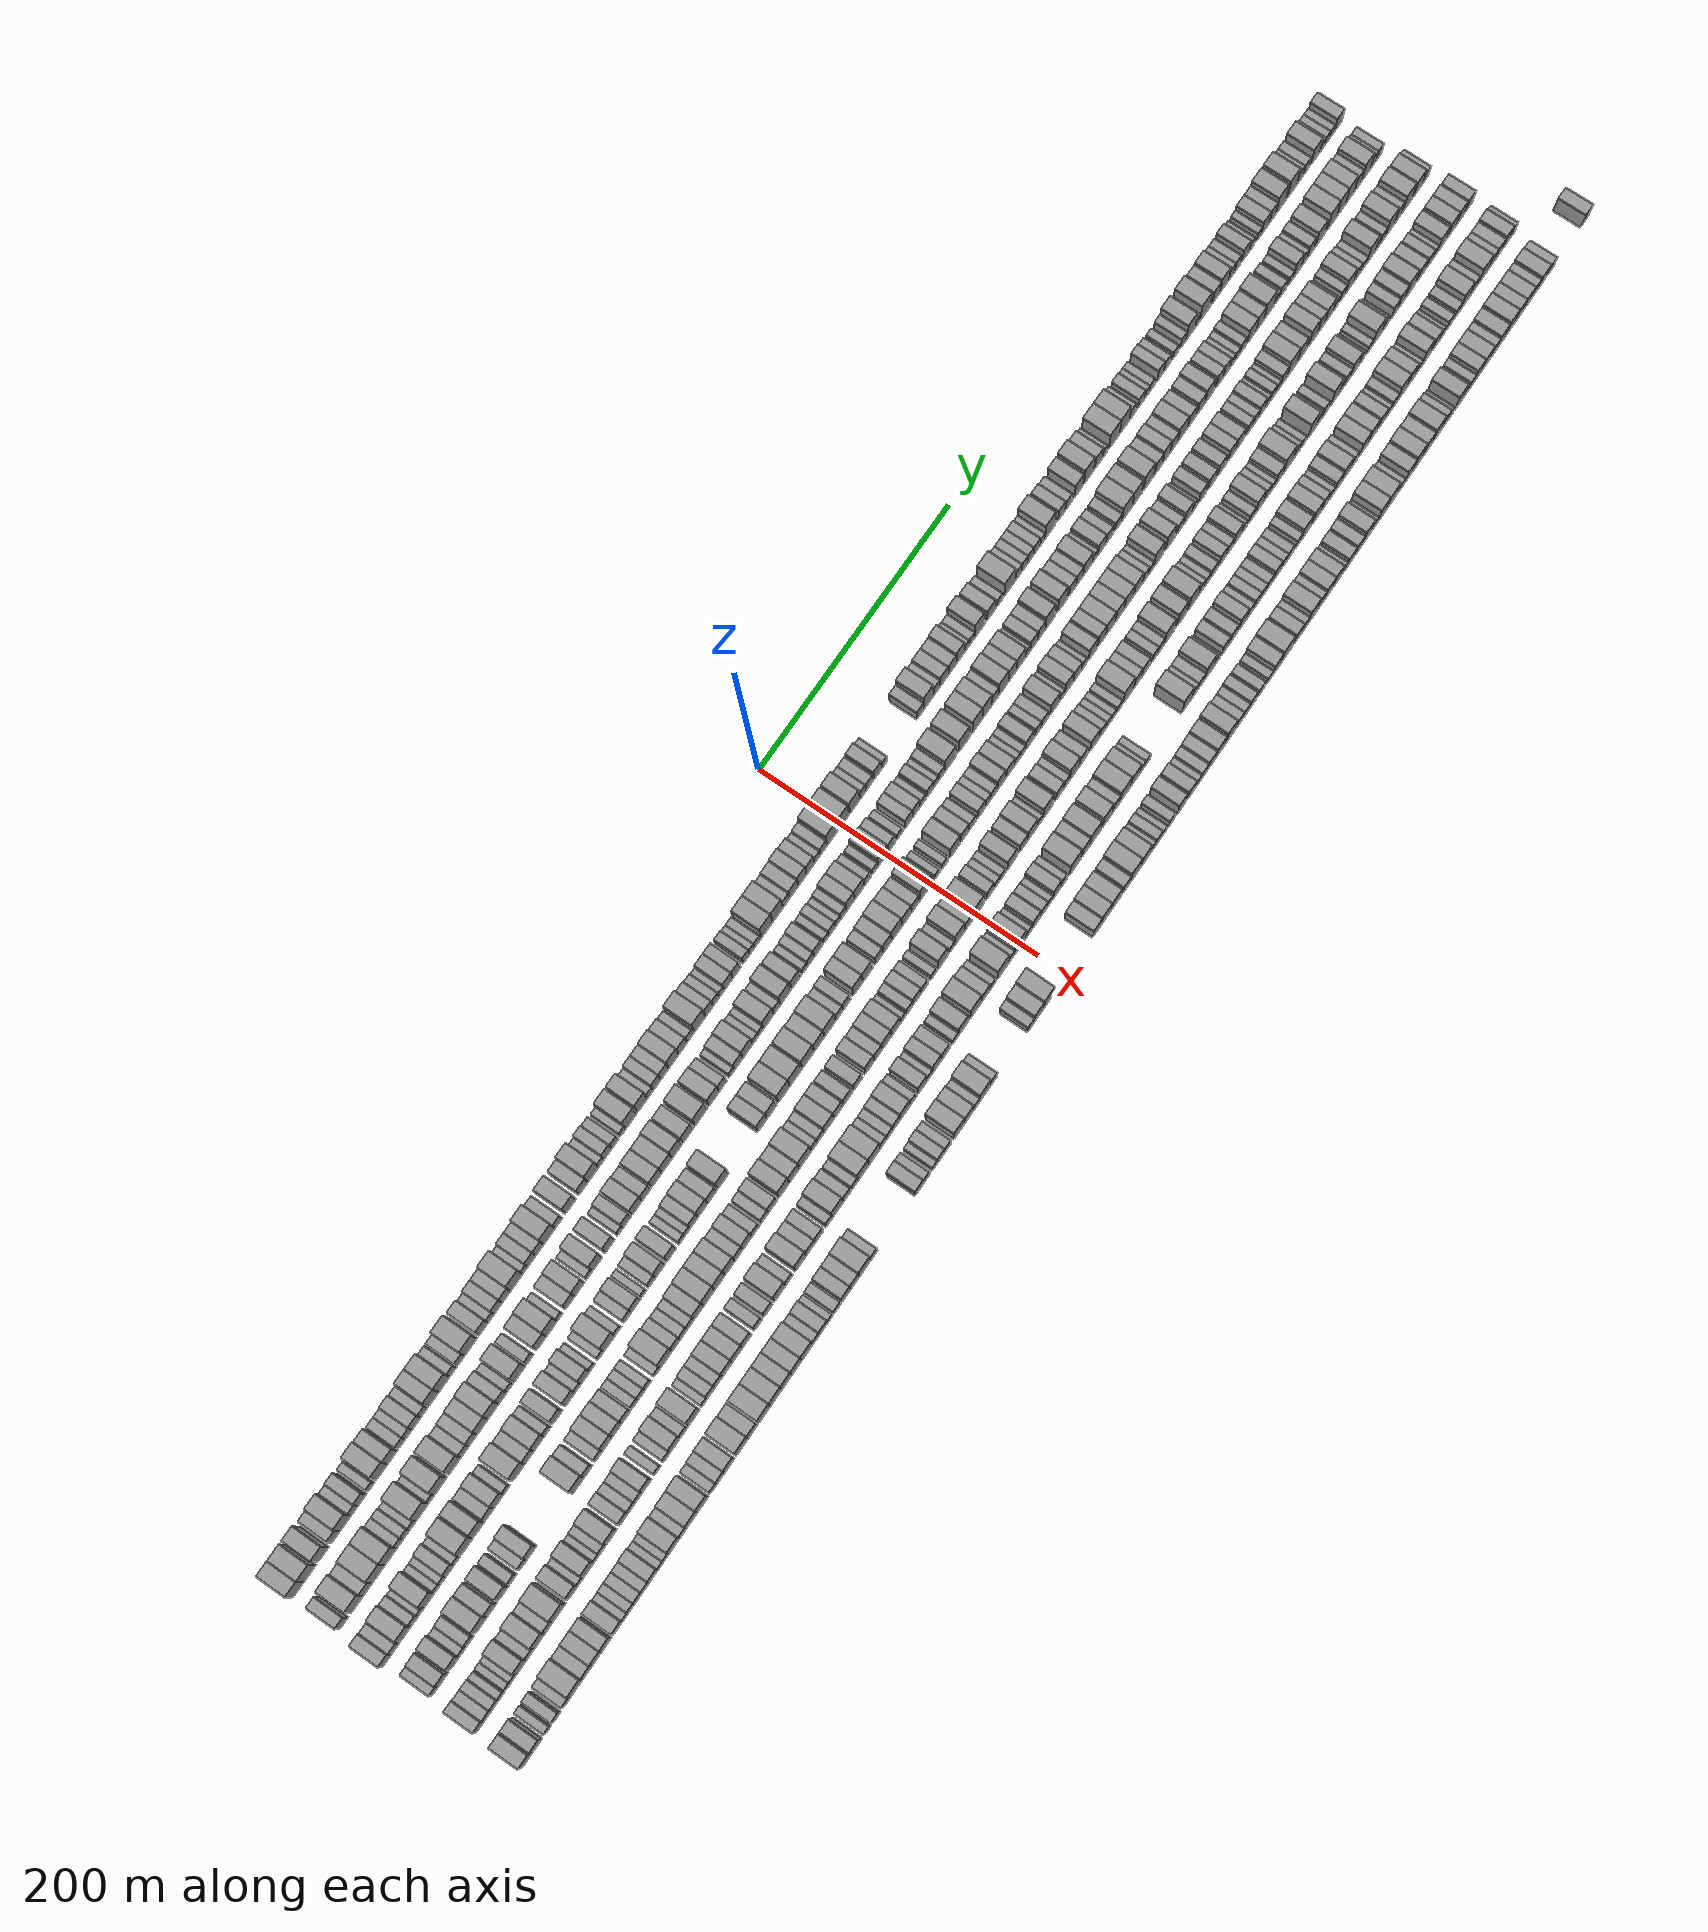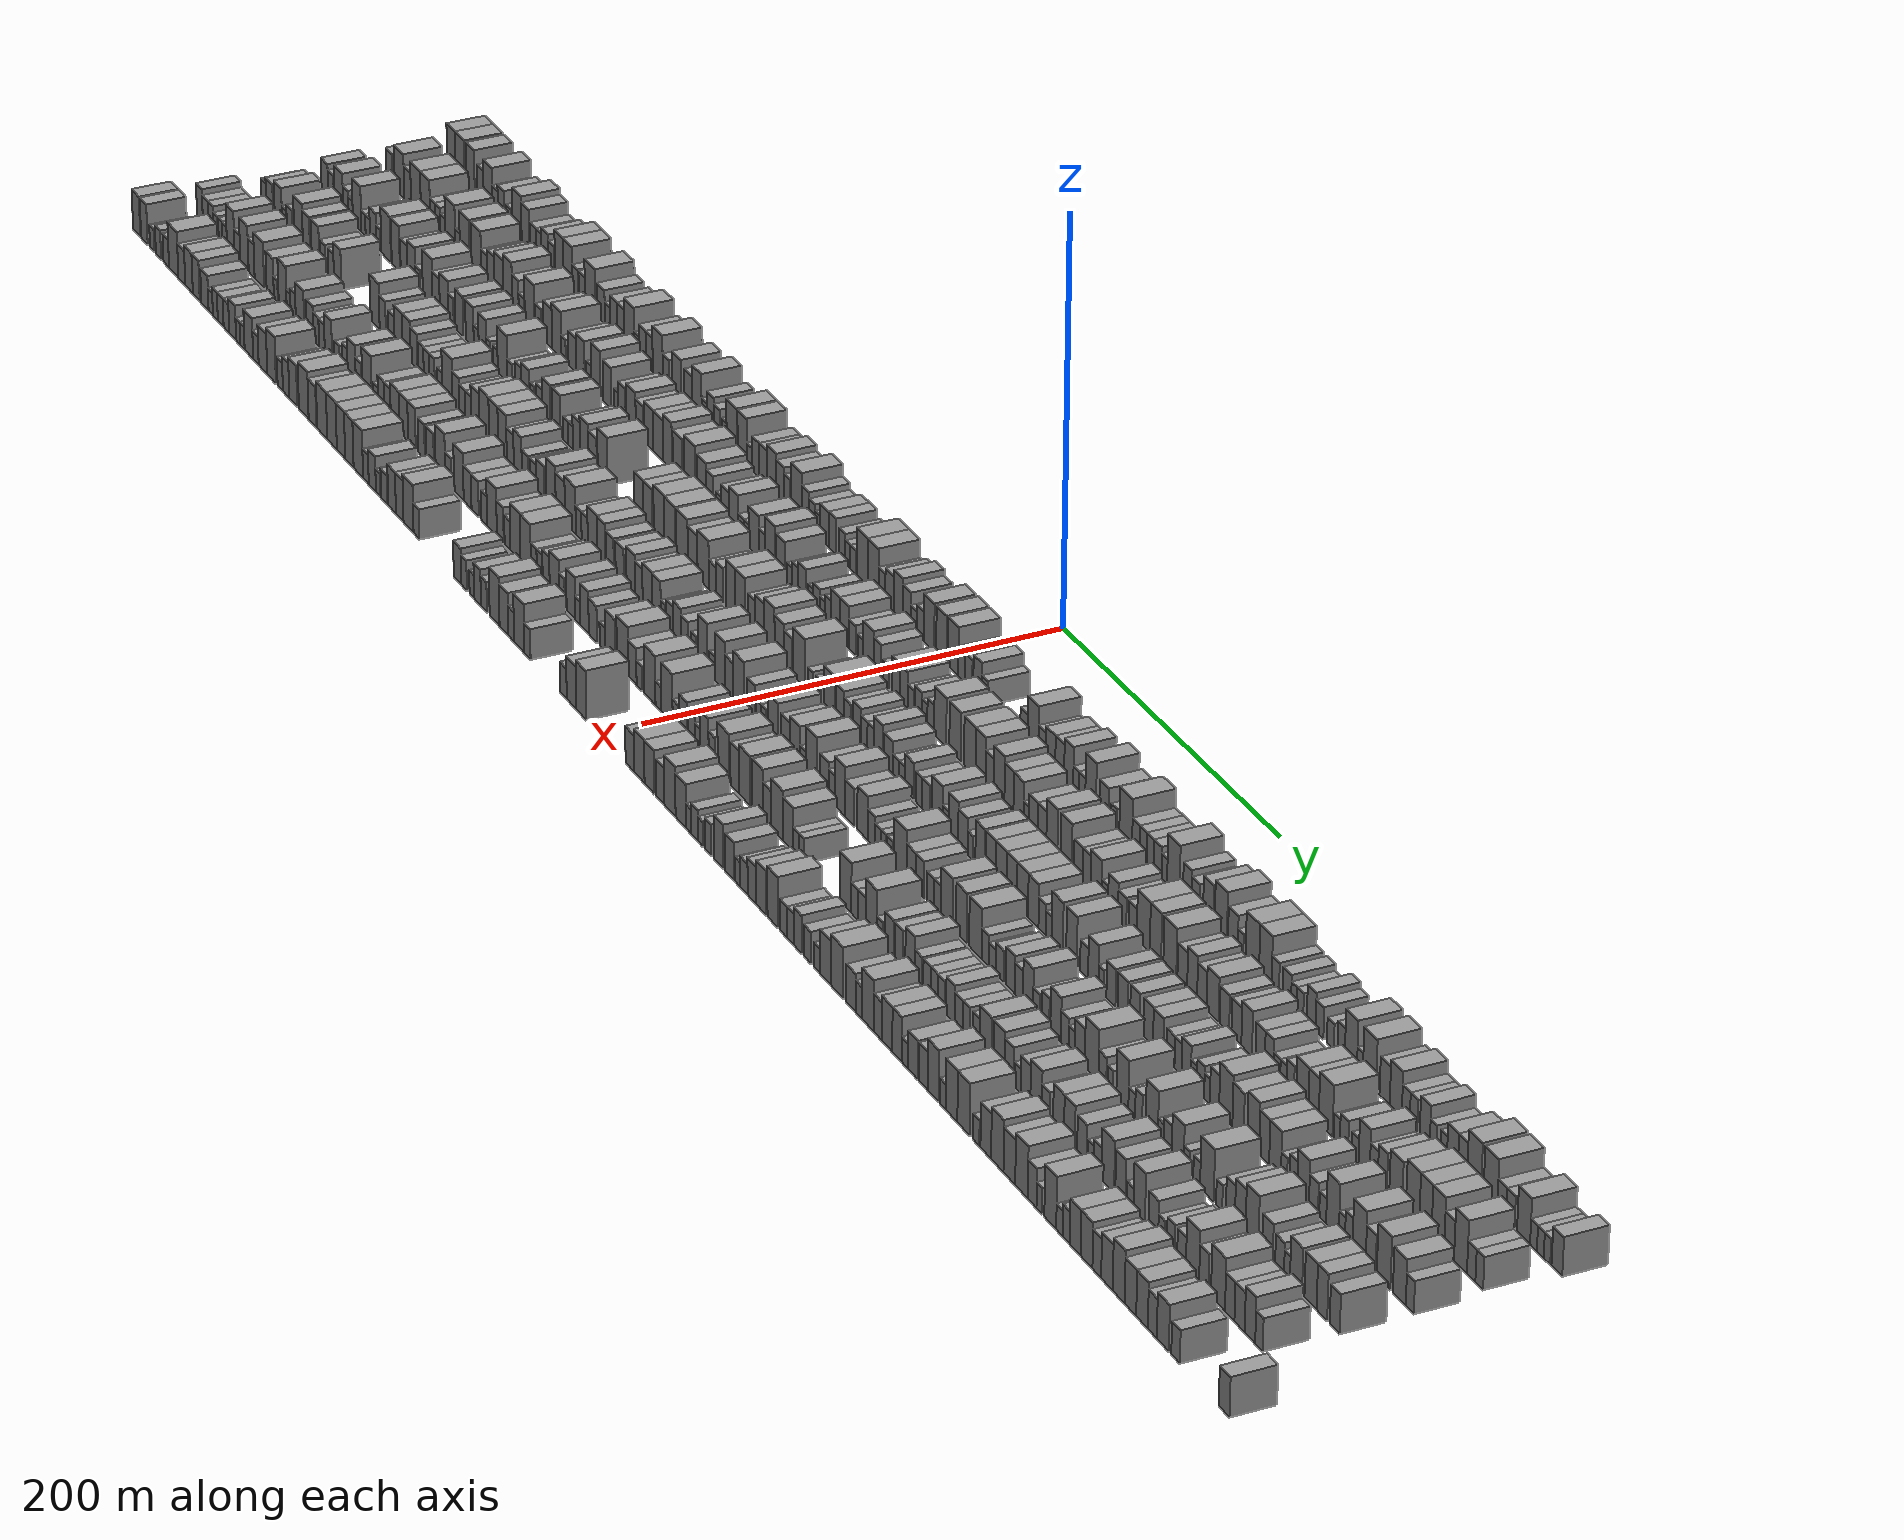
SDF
<sdf version="1.6">
 <world name="default">
  <scene>
   <sky><clouds><speed>12</speed></clouds></sky>
   <ambient>0.4 0.4 0.4 1</ambient>
   <background>0.7 0.7 0.7 1</background>
   <shadows>1</shadows>
  </scene>
  <gravity>0 0 -9.8066</gravity>
  <magnetic_field>6e-06 2.3e-05 -4.2e-05</magnetic_field>
  <physics default="0" name="default_physics" type="ode">
   <ode>
    <solver>
     <type>quick</type>
     <iters>10</iters>
     <sor>1.0</sor>
     <use_dynamic_moi_rescaling>0</use_dynamic_moi_rescaling>
    </solver>
    <constraints>
     <cfm>0</cfm>
     <erp>0.2</erp>
     <contact_max_correcting_vel>100</contact_max_correcting_vel>
     <contact_surface_layer>0.001</contact_surface_layer>
    </constraints>
   </ode>
   <max_step_size>0.004</max_step_size>
   <real_time_factor>1</real_time_factor>
   <real_time_update_rate>250</real_time_update_rate>
  </physics>
  <light name="sun" type="directional">
   <pose>0 0 10 0 0 0</pose>
   <diffuse>0.8 0.8 0.8 1</diffuse>
   <specular>0.2 0.2 0.2 1</specular>
   <attenuation>
    <range>1000</range>
    <constant>0.9</constant>
    <linear>0.01</linear>
    <quadratic>0.001</quadratic>
   </attenuation>
   <direction>-0.5 0.1 -0.9</direction>
  </light>
  <model name="building_1">
   <static>1</static>
   <pose>50.0000 -532.9642 0 0.000000 0.000000 0.000000</pose>
   <link name="link">
    <pose>0 0 12.00 0 0 0</pose>
    <collision name="collision"><geometry><box><size>20.0000 10.0716 24.0000</size></box></geometry></collision>
    <visual name="visual">
     <cast_shadows>0</cast_shadows>
     <geometry><box><size>20.0000 10.0716 24.0000</size></box></geometry>
     <material>
      <script>
       <uri>model://grey_wall/materials/scripts</uri>
       <uri>model://grey_wall/materials/textures</uri>
       <name>vrc/grey_wall</name>
      </script>
     </material>
    </visual>
   </link>
  </model>
  <model name="building_2">
   <static>1</static>
   <pose>50.0000 -522.3553 0 0.000000 0.000000 0.000000</pose>
   <link name="link">
    <pose>0 0 12.00 0 0 0</pose>
    <collision name="collision"><geometry><box><size>20.0000 11.1462 24.0000</size></box></geometry></collision>
    <visual name="visual">
     <cast_shadows>0</cast_shadows>
     <geometry><box><size>20.0000 11.1462 24.0000</size></box></geometry>
     <material>
      <script>
       <uri>model://grey_wall/materials/scripts</uri>
       <uri>model://grey_wall/materials/textures</uri>
       <name>vrc/grey_wall</name>
      </script>
     </material>
    </visual>
   </link>
  </model>
  <model name="building_3">
   <static>1</static>
   <pose>50.0000 -509.8019 0 0.000000 0.000000 0.000000</pose>
   <link name="link">
    <pose>0 0 12.00 0 0 0</pose>
    <collision name="collision"><geometry><box><size>20.0000 9.9606 24.0000</size></box></geometry></collision>
    <visual name="visual">
     <cast_shadows>0</cast_shadows>
     <geometry><box><size>20.0000 9.9606 24.0000</size></box></geometry>
     <material>
      <script>
       <uri>model://grey_wall/materials/scripts</uri>
       <uri>model://grey_wall/materials/textures</uri>
       <name>vrc/grey_wall</name>
      </script>
     </material>
    </visual>
   </link>
  </model>
  <model name="building_4">
   <static>1</static>
   <pose>50.0000 -497.9303 0 0.000000 0.000000 0.000000</pose>
   <link name="link">
    <pose>0 0 9.00 0 0 0</pose>
    <collision name="collision"><geometry><box><size>20.0000 7.7826 18.0000</size></box></geometry></collision>
    <visual name="visual">
     <cast_shadows>0</cast_shadows>
     <geometry><box><size>20.0000 7.7826 18.0000</size></box></geometry>
     <material>
      <script>
       <uri>model://grey_wall/materials/scripts</uri>
       <uri>model://grey_wall/materials/textures</uri>
       <name>vrc/grey_wall</name>
      </script>
     </material>
    </visual>
   </link>
  </model>
  <model name="building_5">
   <static>1</static>
   <pose>50.0000 -488.7809 0 0.000000 0.000000 0.000000</pose>
   <link name="link">
    <pose>0 0 12.00 0 0 0</pose>
    <collision name="collision"><geometry><box><size>20.0000 10.5162 24.0000</size></box></geometry></collision>
    <visual name="visual">
     <cast_shadows>0</cast_shadows>
     <geometry><box><size>20.0000 10.5162 24.0000</size></box></geometry>
     <material>
      <script>
       <uri>model://grey_wall/materials/scripts</uri>
       <uri>model://grey_wall/materials/textures</uri>
       <name>vrc/grey_wall</name>
      </script>
     </material>
    </visual>
   </link>
  </model>
  <model name="building_6">
   <static>1</static>
   <pose>50.0000 -480.3390 0 0.000000 0.000000 0.000000</pose>
   <link name="link">
    <pose>0 0 7.50 0 0 0</pose>
    <collision name="collision"><geometry><box><size>20.0000 6.3675 15.0000</size></box></geometry></collision>
    <visual name="visual">
     <cast_shadows>0</cast_shadows>
     <geometry><box><size>20.0000 6.3675 15.0000</size></box></geometry>
     <material>
      <script>
       <uri>model://grey_wall/materials/scripts</uri>
       <uri>model://grey_wall/materials/textures</uri>
       <name>vrc/grey_wall</name>
      </script>
     </material>
    </visual>
   </link>
  </model>
  <model name="building_7">
   <static>1</static>
   <pose>50.0000 -473.3430 0 0.000000 0.000000 0.000000</pose>
   <link name="link">
    <pose>0 0 9.00 0 0 0</pose>
    <collision name="collision"><geometry><box><size>20.0000 7.6245 18.0000</size></box></geometry></collision>
    <visual name="visual">
     <cast_shadows>0</cast_shadows>
     <geometry><box><size>20.0000 7.6245 18.0000</size></box></geometry>
     <material>
      <script>
       <uri>model://grey_wall/materials/scripts</uri>
       <uri>model://grey_wall/materials/textures</uri>
       <name>vrc/grey_wall</name>
      </script>
     </material>
    </visual>
   </link>
  </model>
  <model name="building_8">
   <static>1</static>
   <pose>50.0000 -464.7182 0 0.000000 0.000000 0.000000</pose>
   <link name="link">
    <pose>0 0 6.00 0 0 0</pose>
    <collision name="collision"><geometry><box><size>20.0000 5.6252 12.0000</size></box></geometry></collision>
    <visual name="visual">
     <cast_shadows>0</cast_shadows>
     <geometry><box><size>20.0000 5.6252 12.0000</size></box></geometry>
     <material>
      <script>
       <uri>model://grey_wall/materials/scripts</uri>
       <uri>model://grey_wall/materials/textures</uri>
       <name>vrc/grey_wall</name>
      </script>
     </material>
    </visual>
   </link>
  </model>
  <model name="building_9">
   <static>1</static>
   <pose>50.0000 -454.5455 0 0.000000 0.000000 0.000000</pose>
   <link name="link">
    <pose>0 0 12.00 0 0 0</pose>
    <collision name="collision"><geometry><box><size>20.0000 10.7202 24.0000</size></box></geometry></collision>
    <visual name="visual">
     <cast_shadows>0</cast_shadows>
     <geometry><box><size>20.0000 10.7202 24.0000</size></box></geometry>
     <material>
      <script>
       <uri>model://grey_wall/materials/scripts</uri>
       <uri>model://grey_wall/materials/textures</uri>
       <name>vrc/grey_wall</name>
      </script>
     </material>
    </visual>
   </link>
  </model>
  <model name="building_10">
   <static>1</static>
   <pose>50.0000 -444.7229 0 0.000000 0.000000 0.000000</pose>
   <link name="link">
    <pose>0 0 10.50 0 0 0</pose>
    <collision name="collision"><geometry><box><size>20.0000 8.9249 21.0000</size></box></geometry></collision>
    <visual name="visual">
     <cast_shadows>0</cast_shadows>
     <geometry><box><size>20.0000 8.9249 21.0000</size></box></geometry>
     <material>
      <script>
       <uri>model://grey_wall/materials/scripts</uri>
       <uri>model://grey_wall/materials/textures</uri>
       <name>vrc/grey_wall</name>
      </script>
     </material>
    </visual>
   </link>
  </model>
  <model name="building_11">
   <static>1</static>
   <pose>50.0000 -435.8087 0 0.000000 0.000000 0.000000</pose>
   <link name="link">
    <pose>0 0 7.50 0 0 0</pose>
    <collision name="collision"><geometry><box><size>20.0000 6.9034 15.0000</size></box></geometry></collision>
    <visual name="visual">
     <cast_shadows>0</cast_shadows>
     <geometry><box><size>20.0000 6.9034 15.0000</size></box></geometry>
     <material>
      <script>
       <uri>model://grey_wall/materials/scripts</uri>
       <uri>model://grey_wall/materials/textures</uri>
       <name>vrc/grey_wall</name>
      </script>
     </material>
    </visual>
   </link>
  </model>
  <model name="building_12">
   <static>1</static>
   <pose>50.0000 -429.1963 0 0.000000 0.000000 0.000000</pose>
   <link name="link">
    <pose>0 0 7.50 0 0 0</pose>
    <collision name="collision"><geometry><box><size>20.0000 6.3215 15.0000</size></box></geometry></collision>
    <visual name="visual">
     <cast_shadows>0</cast_shadows>
     <geometry><box><size>20.0000 6.3215 15.0000</size></box></geometry>
     <material>
      <script>
       <uri>model://grey_wall/materials/scripts</uri>
       <uri>model://grey_wall/materials/textures</uri>
       <name>vrc/grey_wall</name>
      </script>
     </material>
    </visual>
   </link>
  </model>
  <model name="building_13">
   <static>1</static>
   <pose>50.0000 -421.8779 0 0.000000 0.000000 0.000000</pose>
   <link name="link">
    <pose>0 0 9.00 0 0 0</pose>
    <collision name="collision"><geometry><box><size>20.0000 8.3153 18.0000</size></box></geometry></collision>
    <visual name="visual">
     <cast_shadows>0</cast_shadows>
     <geometry><box><size>20.0000 8.3153 18.0000</size></box></geometry>
     <material>
      <script>
       <uri>model://grey_wall/materials/scripts</uri>
       <uri>model://grey_wall/materials/textures</uri>
       <name>vrc/grey_wall</name>
      </script>
     </material>
    </visual>
   </link>
  </model>
  <model name="building_14">
   <static>1</static>
   <pose>50.0000 -414.5161 0 0.000000 0.000000 0.000000</pose>
   <link name="link">
    <pose>0 0 7.50 0 0 0</pose>
    <collision name="collision"><geometry><box><size>20.0000 6.4083 15.0000</size></box></geometry></collision>
    <visual name="visual">
     <cast_shadows>0</cast_shadows>
     <geometry><box><size>20.0000 6.4083 15.0000</size></box></geometry>
     <material>
      <script>
       <uri>model://grey_wall/materials/scripts</uri>
       <uri>model://grey_wall/materials/textures</uri>
       <name>vrc/grey_wall</name>
      </script>
     </material>
    </visual>
   </link>
  </model>
  <model name="building_15">
   <static>1</static>
   <pose>50.0000 -405.5095 0 0.000000 0.000000 0.000000</pose>
   <link name="link">
    <pose>0 0 12.00 0 0 0</pose>
    <collision name="collision"><geometry><box><size>20.0000 9.6048 24.0000</size></box></geometry></collision>
    <visual name="visual">
     <cast_shadows>0</cast_shadows>
     <geometry><box><size>20.0000 9.6048 24.0000</size></box></geometry>
     <material>
      <script>
       <uri>model://grey_wall/materials/scripts</uri>
       <uri>model://grey_wall/materials/textures</uri>
       <name>vrc/grey_wall</name>
      </script>
     </material>
    </visual>
   </link>
  </model>
  <model name="building_16">
   <static>1</static>
   <pose>50.0000 -395.4034 0 0.000000 0.000000 0.000000</pose>
   <link name="link">
    <pose>0 0 12.00 0 0 0</pose>
    <collision name="collision"><geometry><box><size>20.0000 10.6074 24.0000</size></box></geometry></collision>
    <visual name="visual">
     <cast_shadows>0</cast_shadows>
     <geometry><box><size>20.0000 10.6074 24.0000</size></box></geometry>
     <material>
      <script>
       <uri>model://grey_wall/materials/scripts</uri>
       <uri>model://grey_wall/materials/textures</uri>
       <name>vrc/grey_wall</name>
      </script>
     </material>
    </visual>
   </link>
  </model>
  <model name="building_17">
   <static>1</static>
   <pose>50.0000 -387.0131 0 0.000000 0.000000 0.000000</pose>
   <link name="link">
    <pose>0 0 7.50 0 0 0</pose>
    <collision name="collision"><geometry><box><size>20.0000 6.1733 15.0000</size></box></geometry></collision>
    <visual name="visual">
     <cast_shadows>0</cast_shadows>
     <geometry><box><size>20.0000 6.1733 15.0000</size></box></geometry>
     <material>
      <script>
       <uri>model://grey_wall/materials/scripts</uri>
       <uri>model://grey_wall/materials/textures</uri>
       <name>vrc/grey_wall</name>
      </script>
     </material>
    </visual>
   </link>
  </model>
  <model name="building_18">
   <static>1</static>
   <pose>50.0000 -379.4041 0 0.000000 0.000000 0.000000</pose>
   <link name="link">
    <pose>0 0 7.50 0 0 0</pose>
    <collision name="collision"><geometry><box><size>20.0000 7.0446 15.0000</size></box></geometry></collision>
    <visual name="visual">
     <cast_shadows>0</cast_shadows>
     <geometry><box><size>20.0000 7.0446 15.0000</size></box></geometry>
     <material>
      <script>
       <uri>model://grey_wall/materials/scripts</uri>
       <uri>model://grey_wall/materials/textures</uri>
       <name>vrc/grey_wall</name>
      </script>
     </material>
    </visual>
   </link>
  </model>
  <model name="building_19">
   <static>1</static>
   <pose>50.0000 -369.9329 0 0.000000 0.000000 0.000000</pose>
   <link name="link">
    <pose>0 0 12.00 0 0 0</pose>
    <collision name="collision"><geometry><box><size>20.0000 11.8979 24.0000</size></box></geometry></collision>
    <visual name="visual">
     <cast_shadows>0</cast_shadows>
     <geometry><box><size>20.0000 11.8979 24.0000</size></box></geometry>
     <material>
      <script>
       <uri>model://grey_wall/materials/scripts</uri>
       <uri>model://grey_wall/materials/textures</uri>
       <name>vrc/grey_wall</name>
      </script>
     </material>
    </visual>
   </link>
  </model>
  <model name="building_20">
   <static>1</static>
   <pose>50.0000 -357.6337 0 0.000000 0.000000 0.000000</pose>
   <link name="link">
    <pose>0 0 9.00 0 0 0</pose>
    <collision name="collision"><geometry><box><size>20.0000 8.7006 18.0000</size></box></geometry></collision>
    <visual name="visual">
     <cast_shadows>0</cast_shadows>
     <geometry><box><size>20.0000 8.7006 18.0000</size></box></geometry>
     <material>
      <script>
       <uri>model://grey_wall/materials/scripts</uri>
       <uri>model://grey_wall/materials/textures</uri>
       <name>vrc/grey_wall</name>
      </script>
     </material>
    </visual>
   </link>
  </model>
  <model name="building_21">
   <static>1</static>
   <pose>50.0000 -350.4063 0 0.000000 0.000000 0.000000</pose>
   <link name="link">
    <pose>0 0 6.00 0 0 0</pose>
    <collision name="collision"><geometry><box><size>20.0000 5.7541 12.0000</size></box></geometry></collision>
    <visual name="visual">
     <cast_shadows>0</cast_shadows>
     <geometry><box><size>20.0000 5.7541 12.0000</size></box></geometry>
     <material>
      <script>
       <uri>model://grey_wall/materials/scripts</uri>
       <uri>model://grey_wall/materials/textures</uri>
       <name>vrc/grey_wall</name>
      </script>
     </material>
    </visual>
   </link>
  </model>
  <model name="building_22">
   <static>1</static>
   <pose>50.0000 -343.5620 0 0.000000 0.000000 0.000000</pose>
   <link name="link">
    <pose>0 0 9.00 0 0 0</pose>
    <collision name="collision"><geometry><box><size>20.0000 7.9346 18.0000</size></box></geometry></collision>
    <visual name="visual">
     <cast_shadows>0</cast_shadows>
     <geometry><box><size>20.0000 7.9346 18.0000</size></box></geometry>
     <material>
      <script>
       <uri>model://grey_wall/materials/scripts</uri>
       <uri>model://grey_wall/materials/textures</uri>
       <name>vrc/grey_wall</name>
      </script>
     </material>
    </visual>
   </link>
  </model>
  <model name="building_23">
   <static>1</static>
   <pose>50.0000 -335.5840 0 0.000000 0.000000 0.000000</pose>
   <link name="link">
    <pose>0 0 9.00 0 0 0</pose>
    <collision name="collision"><geometry><box><size>20.0000 8.0214 18.0000</size></box></geometry></collision>
    <visual name="visual">
     <cast_shadows>0</cast_shadows>
     <geometry><box><size>20.0000 8.0214 18.0000</size></box></geometry>
     <material>
      <script>
       <uri>model://grey_wall/materials/scripts</uri>
       <uri>model://grey_wall/materials/textures</uri>
       <name>vrc/grey_wall</name>
      </script>
     </material>
    </visual>
   </link>
  </model>
  <model name="building_24">
   <static>1</static>
   <pose>50.0000 -325.7760 0 0.000000 0.000000 0.000000</pose>
   <link name="link">
    <pose>0 0 12.00 0 0 0</pose>
    <collision name="collision"><geometry><box><size>20.0000 11.5945 24.0000</size></box></geometry></collision>
    <visual name="visual">
     <cast_shadows>0</cast_shadows>
     <geometry><box><size>20.0000 11.5945 24.0000</size></box></geometry>
     <material>
      <script>
       <uri>model://grey_wall/materials/scripts</uri>
       <uri>model://grey_wall/materials/textures</uri>
       <name>vrc/grey_wall</name>
      </script>
     </material>
    </visual>
   </link>
  </model>
  <model name="building_25">
   <static>1</static>
   <pose>50.0000 -317.4945 0 0.000000 0.000000 0.000000</pose>
   <link name="link">
    <pose>0 0 6.00 0 0 0</pose>
    <collision name="collision"><geometry><box><size>20.0000 4.9685 12.0000</size></box></geometry></collision>
    <visual name="visual">
     <cast_shadows>0</cast_shadows>
     <geometry><box><size>20.0000 4.9685 12.0000</size></box></geometry>
     <material>
      <script>
       <uri>model://grey_wall/materials/scripts</uri>
       <uri>model://grey_wall/materials/textures</uri>
       <name>vrc/grey_wall</name>
      </script>
     </material>
    </visual>
   </link>
  </model>
  <model name="building_26">
   <static>1</static>
   <pose>50.0000 -311.1380 0 0.000000 0.000000 0.000000</pose>
   <link name="link">
    <pose>0 0 9.00 0 0 0</pose>
    <collision name="collision"><geometry><box><size>20.0000 7.7444 18.0000</size></box></geometry></collision>
    <visual name="visual">
     <cast_shadows>0</cast_shadows>
     <geometry><box><size>20.0000 7.7444 18.0000</size></box></geometry>
     <material>
      <script>
       <uri>model://grey_wall/materials/scripts</uri>
       <uri>model://grey_wall/materials/textures</uri>
       <name>vrc/grey_wall</name>
      </script>
     </material>
    </visual>
   </link>
  </model>
  <model name="building_27">
   <static>1</static>
   <pose>50.0000 -303.4338 0 0.000000 0.000000 0.000000</pose>
   <link name="link">
    <pose>0 0 9.00 0 0 0</pose>
    <collision name="collision"><geometry><box><size>20.0000 7.6640 18.0000</size></box></geometry></collision>
    <visual name="visual">
     <cast_shadows>0</cast_shadows>
     <geometry><box><size>20.0000 7.6640 18.0000</size></box></geometry>
     <material>
      <script>
       <uri>model://grey_wall/materials/scripts</uri>
       <uri>model://grey_wall/materials/textures</uri>
       <name>vrc/grey_wall</name>
      </script>
     </material>
    </visual>
   </link>
  </model>
  <model name="building_28">
   <static>1</static>
   <pose>50.0000 -294.0374 0 0.000000 0.000000 0.000000</pose>
   <link name="link">
    <pose>0 0 12.00 0 0 0</pose>
    <collision name="collision"><geometry><box><size>20.0000 11.1289 24.0000</size></box></geometry></collision>
    <visual name="visual">
     <cast_shadows>0</cast_shadows>
     <geometry><box><size>20.0000 11.1289 24.0000</size></box></geometry>
     <material>
      <script>
       <uri>model://grey_wall/materials/scripts</uri>
       <uri>model://grey_wall/materials/textures</uri>
       <name>vrc/grey_wall</name>
      </script>
     </material>
    </visual>
   </link>
  </model>
  <model name="building_29">
   <static>1</static>
   <pose>50.0000 -284.8770 0 0.000000 0.000000 0.000000</pose>
   <link name="link">
    <pose>0 0 7.50 0 0 0</pose>
    <collision name="collision"><geometry><box><size>20.0000 7.1919 15.0000</size></box></geometry></collision>
    <visual name="visual">
     <cast_shadows>0</cast_shadows>
     <geometry><box><size>20.0000 7.1919 15.0000</size></box></geometry>
     <material>
      <script>
       <uri>model://grey_wall/materials/scripts</uri>
       <uri>model://grey_wall/materials/textures</uri>
       <name>vrc/grey_wall</name>
      </script>
     </material>
    </visual>
   </link>
  </model>
  <model name="building_30">
   <static>1</static>
   <pose>50.0000 -273.1539 0 0.000000 0.000000 0.000000</pose>
   <link name="link">
    <pose>0 0 10.50 0 0 0</pose>
    <collision name="collision"><geometry><box><size>20.0000 10.2542 21.0000</size></box></geometry></collision>
    <visual name="visual">
     <cast_shadows>0</cast_shadows>
     <geometry><box><size>20.0000 10.2542 21.0000</size></box></geometry>
     <material>
      <script>
       <uri>model://grey_wall/materials/scripts</uri>
       <uri>model://grey_wall/materials/textures</uri>
       <name>vrc/grey_wall</name>
      </script>
     </material>
    </visual>
   </link>
  </model>
  <model name="building_31">
   <static>1</static>
   <pose>50.0000 -260.6110 0 0.000000 0.000000 0.000000</pose>
   <link name="link">
    <pose>0 0 9.00 0 0 0</pose>
    <collision name="collision"><geometry><box><size>20.0000 8.8316 18.0000</size></box></geometry></collision>
    <visual name="visual">
     <cast_shadows>0</cast_shadows>
     <geometry><box><size>20.0000 8.8316 18.0000</size></box></geometry>
     <material>
      <script>
       <uri>model://grey_wall/materials/scripts</uri>
       <uri>model://grey_wall/materials/textures</uri>
       <name>vrc/grey_wall</name>
      </script>
     </material>
    </visual>
   </link>
  </model>
  <model name="building_32">
   <static>1</static>
   <pose>50.0000 -251.0286 0 0.000000 0.000000 0.000000</pose>
   <link name="link">
    <pose>0 0 12.00 0 0 0</pose>
    <collision name="collision"><geometry><box><size>20.0000 10.3332 24.0000</size></box></geometry></collision>
    <visual name="visual">
     <cast_shadows>0</cast_shadows>
     <geometry><box><size>20.0000 10.3332 24.0000</size></box></geometry>
     <material>
      <script>
       <uri>model://grey_wall/materials/scripts</uri>
       <uri>model://grey_wall/materials/textures</uri>
       <name>vrc/grey_wall</name>
      </script>
     </material>
    </visual>
   </link>
  </model>
  <model name="building_33">
   <static>1</static>
   <pose>50.0000 -243.0790 0 0.000000 0.000000 0.000000</pose>
   <link name="link">
    <pose>0 0 6.00 0 0 0</pose>
    <collision name="collision"><geometry><box><size>20.0000 5.5659 12.0000</size></box></geometry></collision>
    <visual name="visual">
     <cast_shadows>0</cast_shadows>
     <geometry><box><size>20.0000 5.5659 12.0000</size></box></geometry>
     <material>
      <script>
       <uri>model://grey_wall/materials/scripts</uri>
       <uri>model://grey_wall/materials/textures</uri>
       <name>vrc/grey_wall</name>
      </script>
     </material>
    </visual>
   </link>
  </model>
  <model name="building_34">
   <static>1</static>
   <pose>50.0000 -236.5503 0 0.000000 0.000000 0.000000</pose>
   <link name="link">
    <pose>0 0 9.00 0 0 0</pose>
    <collision name="collision"><geometry><box><size>20.0000 7.4915 18.0000</size></box></geometry></collision>
    <visual name="visual">
     <cast_shadows>0</cast_shadows>
     <geometry><box><size>20.0000 7.4915 18.0000</size></box></geometry>
     <material>
      <script>
       <uri>model://grey_wall/materials/scripts</uri>
       <uri>model://grey_wall/materials/textures</uri>
       <name>vrc/grey_wall</name>
      </script>
     </material>
    </visual>
   </link>
  </model>
  <model name="building_35">
   <static>1</static>
   <pose>50.0000 -229.5090 0 0.000000 0.000000 0.000000</pose>
   <link name="link">
    <pose>0 0 7.50 0 0 0</pose>
    <collision name="collision"><geometry><box><size>20.0000 6.5911 15.0000</size></box></geometry></collision>
    <visual name="visual">
     <cast_shadows>0</cast_shadows>
     <geometry><box><size>20.0000 6.5911 15.0000</size></box></geometry>
     <material>
      <script>
       <uri>model://grey_wall/materials/scripts</uri>
       <uri>model://grey_wall/materials/textures</uri>
       <name>vrc/grey_wall</name>
      </script>
     </material>
    </visual>
   </link>
  </model>
  <model name="building_36">
   <static>1</static>
   <pose>50.0000 -221.5522 0 0.000000 0.000000 0.000000</pose>
   <link name="link">
    <pose>0 0 6.00 0 0 0</pose>
    <collision name="collision"><geometry><box><size>20.0000 5.3224 12.0000</size></box></geometry></collision>
    <visual name="visual">
     <cast_shadows>0</cast_shadows>
     <geometry><box><size>20.0000 5.3224 12.0000</size></box></geometry>
     <material>
      <script>
       <uri>model://grey_wall/materials/scripts</uri>
       <uri>model://grey_wall/materials/textures</uri>
       <name>vrc/grey_wall</name>
      </script>
     </material>
    </visual>
   </link>
  </model>
  <model name="building_37">
   <static>1</static>
   <pose>50.0000 -213.4849 0 0.000000 0.000000 0.000000</pose>
   <link name="link">
    <pose>0 0 12.00 0 0 0</pose>
    <collision name="collision"><geometry><box><size>20.0000 10.8123 24.0000</size></box></geometry></collision>
    <visual name="visual">
     <cast_shadows>0</cast_shadows>
     <geometry><box><size>20.0000 10.8123 24.0000</size></box></geometry>
     <material>
      <script>
       <uri>model://grey_wall/materials/scripts</uri>
       <uri>model://grey_wall/materials/textures</uri>
       <name>vrc/grey_wall</name>
      </script>
     </material>
    </visual>
   </link>
  </model>
  <model name="building_38">
   <static>1</static>
   <pose>50.0000 -202.2470 0 0.000000 0.000000 0.000000</pose>
   <link name="link">
    <pose>0 0 12.00 0 0 0</pose>
    <collision name="collision"><geometry><box><size>20.0000 9.6637 24.0000</size></box></geometry></collision>
    <visual name="visual">
     <cast_shadows>0</cast_shadows>
     <geometry><box><size>20.0000 9.6637 24.0000</size></box></geometry>
     <material>
      <script>
       <uri>model://grey_wall/materials/scripts</uri>
       <uri>model://grey_wall/materials/textures</uri>
       <name>vrc/grey_wall</name>
      </script>
     </material>
    </visual>
   </link>
  </model>
  <model name="building_39">
   <static>1</static>
   <pose>50.0000 -194.4472 0 0.000000 0.000000 0.000000</pose>
   <link name="link">
    <pose>0 0 6.00 0 0 0</pose>
    <collision name="collision"><geometry><box><size>20.0000 5.9358 12.0000</size></box></geometry></collision>
    <visual name="visual">
     <cast_shadows>0</cast_shadows>
     <geometry><box><size>20.0000 5.9358 12.0000</size></box></geometry>
     <material>
      <script>
       <uri>model://grey_wall/materials/scripts</uri>
       <uri>model://grey_wall/materials/textures</uri>
       <name>vrc/grey_wall</name>
      </script>
     </material>
    </visual>
   </link>
  </model>
  <model name="building_40">
   <static>1</static>
   <pose>50.0000 -187.7414 0 0.000000 0.000000 0.000000</pose>
   <link name="link">
    <pose>0 0 9.00 0 0 0</pose>
    <collision name="collision"><geometry><box><size>20.0000 7.4758 18.0000</size></box></geometry></collision>
    <visual name="visual">
     <cast_shadows>0</cast_shadows>
     <geometry><box><size>20.0000 7.4758 18.0000</size></box></geometry>
     <material>
      <script>
       <uri>model://grey_wall/materials/scripts</uri>
       <uri>model://grey_wall/materials/textures</uri>
       <name>vrc/grey_wall</name>
      </script>
     </material>
    </visual>
   </link>
  </model>
  <model name="building_41">
   <static>1</static>
   <pose>50.0000 -180.0132 0 0.000000 0.000000 0.000000</pose>
   <link name="link">
    <pose>0 0 9.00 0 0 0</pose>
    <collision name="collision"><geometry><box><size>20.0000 7.9806 18.0000</size></box></geometry></collision>
    <visual name="visual">
     <cast_shadows>0</cast_shadows>
     <geometry><box><size>20.0000 7.9806 18.0000</size></box></geometry>
     <material>
      <script>
       <uri>model://grey_wall/materials/scripts</uri>
       <uri>model://grey_wall/materials/textures</uri>
       <name>vrc/grey_wall</name>
      </script>
     </material>
    </visual>
   </link>
  </model>
  <model name="building_42">
   <static>1</static>
   <pose>50.0000 -171.0096 0 0.000000 0.000000 0.000000</pose>
   <link name="link">
    <pose>0 0 10.50 0 0 0</pose>
    <collision name="collision"><geometry><box><size>20.0000 10.0265 21.0000</size></box></geometry></collision>
    <visual name="visual">
     <cast_shadows>0</cast_shadows>
     <geometry><box><size>20.0000 10.0265 21.0000</size></box></geometry>
     <material>
      <script>
       <uri>model://grey_wall/materials/scripts</uri>
       <uri>model://grey_wall/materials/textures</uri>
       <name>vrc/grey_wall</name>
      </script>
     </material>
    </visual>
   </link>
  </model>
  <model name="building_43">
   <static>1</static>
   <pose>50.0000 -161.8085 0 0.000000 0.000000 0.000000</pose>
   <link name="link">
    <pose>0 0 9.00 0 0 0</pose>
    <collision name="collision"><geometry><box><size>20.0000 8.3756 18.0000</size></box></geometry></collision>
    <visual name="visual">
     <cast_shadows>0</cast_shadows>
     <geometry><box><size>20.0000 8.3756 18.0000</size></box></geometry>
     <material>
      <script>
       <uri>model://grey_wall/materials/scripts</uri>
       <uri>model://grey_wall/materials/textures</uri>
       <name>vrc/grey_wall</name>
      </script>
     </material>
    </visual>
   </link>
  </model>
  <model name="building_44">
   <static>1</static>
   <pose>50.0000 -154.5138 0 0.000000 0.000000 0.000000</pose>
   <link name="link">
    <pose>0 0 7.50 0 0 0</pose>
    <collision name="collision"><geometry><box><size>20.0000 6.2137 15.0000</size></box></geometry></collision>
    <visual name="visual">
     <cast_shadows>0</cast_shadows>
     <geometry><box><size>20.0000 6.2137 15.0000</size></box></geometry>
     <material>
      <script>
       <uri>model://grey_wall/materials/scripts</uri>
       <uri>model://grey_wall/materials/textures</uri>
       <name>vrc/grey_wall</name>
      </script>
     </material>
    </visual>
   </link>
  </model>
  <model name="building_45">
   <static>1</static>
   <pose>50.0000 -144.7512 0 0.000000 0.000000 0.000000</pose>
   <link name="link">
    <pose>0 0 12.00 0 0 0</pose>
    <collision name="collision"><geometry><box><size>20.0000 11.3115 24.0000</size></box></geometry></collision>
    <visual name="visual">
     <cast_shadows>0</cast_shadows>
     <geometry><box><size>20.0000 11.3115 24.0000</size></box></geometry>
     <material>
      <script>
       <uri>model://grey_wall/materials/scripts</uri>
       <uri>model://grey_wall/materials/textures</uri>
       <name>vrc/grey_wall</name>
      </script>
     </material>
    </visual>
   </link>
  </model>
  <model name="building_46">
   <static>1</static>
   <pose>50.0000 -135.3058 0 0.000000 0.000000 0.000000</pose>
   <link name="link">
    <pose>0 0 9.00 0 0 0</pose>
    <collision name="collision"><geometry><box><size>20.0000 7.5793 18.0000</size></box></geometry></collision>
    <visual name="visual">
     <cast_shadows>0</cast_shadows>
     <geometry><box><size>20.0000 7.5793 18.0000</size></box></geometry>
     <material>
      <script>
       <uri>model://grey_wall/materials/scripts</uri>
       <uri>model://grey_wall/materials/textures</uri>
       <name>vrc/grey_wall</name>
      </script>
     </material>
    </visual>
   </link>
  </model>
  <model name="building_47">
   <static>1</static>
   <pose>50.0000 -128.3319 0 0.000000 0.000000 0.000000</pose>
   <link name="link">
    <pose>0 0 7.50 0 0 0</pose>
    <collision name="collision"><geometry><box><size>20.0000 6.3683 15.0000</size></box></geometry></collision>
    <visual name="visual">
     <cast_shadows>0</cast_shadows>
     <geometry><box><size>20.0000 6.3683 15.0000</size></box></geometry>
     <material>
      <script>
       <uri>model://grey_wall/materials/scripts</uri>
       <uri>model://grey_wall/materials/textures</uri>
       <name>vrc/grey_wall</name>
      </script>
     </material>
    </visual>
   </link>
  </model>
  <model name="building_48">
   <static>1</static>
   <pose>50.0000 -122.7031 0 0.000000 0.000000 0.000000</pose>
   <link name="link">
    <pose>0 0 6.00 0 0 0</pose>
    <collision name="collision"><geometry><box><size>20.0000 4.8894 12.0000</size></box></geometry></collision>
    <visual name="visual">
     <cast_shadows>0</cast_shadows>
     <geometry><box><size>20.0000 4.8894 12.0000</size></box></geometry>
     <material>
      <script>
       <uri>model://grey_wall/materials/scripts</uri>
       <uri>model://grey_wall/materials/textures</uri>
       <name>vrc/grey_wall</name>
      </script>
     </material>
    </visual>
   </link>
  </model>
  <model name="building_49">
   <static>1</static>
   <pose>50.0000 -115.8903 0 0.000000 0.000000 0.000000</pose>
   <link name="link">
    <pose>0 0 9.00 0 0 0</pose>
    <collision name="collision"><geometry><box><size>20.0000 8.7363 18.0000</size></box></geometry></collision>
    <visual name="visual">
     <cast_shadows>0</cast_shadows>
     <geometry><box><size>20.0000 8.7363 18.0000</size></box></geometry>
     <material>
      <script>
       <uri>model://grey_wall/materials/scripts</uri>
       <uri>model://grey_wall/materials/textures</uri>
       <name>vrc/grey_wall</name>
      </script>
     </material>
    </visual>
   </link>
  </model>
  <model name="building_50">
   <static>1</static>
   <pose>50.0000 -107.7333 0 0.000000 0.000000 0.000000</pose>
   <link name="link">
    <pose>0 0 9.00 0 0 0</pose>
    <collision name="collision"><geometry><box><size>20.0000 7.5775 18.0000</size></box></geometry></collision>
    <visual name="visual">
     <cast_shadows>0</cast_shadows>
     <geometry><box><size>20.0000 7.5775 18.0000</size></box></geometry>
     <material>
      <script>
       <uri>model://grey_wall/materials/scripts</uri>
       <uri>model://grey_wall/materials/textures</uri>
       <name>vrc/grey_wall</name>
      </script>
     </material>
    </visual>
   </link>
  </model>
  <model name="building_51">
   <static>1</static>
   <pose>50.0000 -97.6213 0 0.000000 0.000000 0.000000</pose>
   <link name="link">
    <pose>0 0 7.50 0 0 0</pose>
    <collision name="collision"><geometry><box><size>20.0000 6.6466 15.0000</size></box></geometry></collision>
    <visual name="visual">
     <cast_shadows>0</cast_shadows>
     <geometry><box><size>20.0000 6.6466 15.0000</size></box></geometry>
     <material>
      <script>
       <uri>model://grey_wall/materials/scripts</uri>
       <uri>model://grey_wall/materials/textures</uri>
       <name>vrc/grey_wall</name>
      </script>
     </material>
    </visual>
   </link>
  </model>
  <model name="building_52">
   <static>1</static>
   <pose>50.0000 -91.8817 0 0.000000 0.000000 0.000000</pose>
   <link name="link">
    <pose>0 0 6.00 0 0 0</pose>
    <collision name="collision"><geometry><box><size>20.0000 4.8325 12.0000</size></box></geometry></collision>
    <visual name="visual">
     <cast_shadows>0</cast_shadows>
     <geometry><box><size>20.0000 4.8325 12.0000</size></box></geometry>
     <material>
      <script>
       <uri>model://grey_wall/materials/scripts</uri>
       <uri>model://grey_wall/materials/textures</uri>
       <name>vrc/grey_wall</name>
      </script>
     </material>
    </visual>
   </link>
  </model>
  <model name="building_53">
   <static>1</static>
   <pose>50.0000 -86.5118 0 0.000000 0.000000 0.000000</pose>
   <link name="link">
    <pose>0 0 6.00 0 0 0</pose>
    <collision name="collision"><geometry><box><size>20.0000 5.9075 12.0000</size></box></geometry></collision>
    <visual name="visual">
     <cast_shadows>0</cast_shadows>
     <geometry><box><size>20.0000 5.9075 12.0000</size></box></geometry>
     <material>
      <script>
       <uri>model://grey_wall/materials/scripts</uri>
       <uri>model://grey_wall/materials/textures</uri>
       <name>vrc/grey_wall</name>
      </script>
     </material>
    </visual>
   </link>
  </model>
  <model name="building_54">
   <static>1</static>
   <pose>50.0000 -76.9226 0 0.000000 0.000000 0.000000</pose>
   <link name="link">
    <pose>0 0 12.00 0 0 0</pose>
    <collision name="collision"><geometry><box><size>20.0000 11.2709 24.0000</size></box></geometry></collision>
    <visual name="visual">
     <cast_shadows>0</cast_shadows>
     <geometry><box><size>20.0000 11.2709 24.0000</size></box></geometry>
     <material>
      <script>
       <uri>model://grey_wall/materials/scripts</uri>
       <uri>model://grey_wall/materials/textures</uri>
       <name>vrc/grey_wall</name>
      </script>
     </material>
    </visual>
   </link>
  </model>
  <model name="building_55">
   <static>1</static>
   <pose>50.0000 -65.9639 0 0.000000 0.000000 0.000000</pose>
   <link name="link">
    <pose>0 0 12.00 0 0 0</pose>
    <collision name="collision"><geometry><box><size>20.0000 10.6465 24.0000</size></box></geometry></collision>
    <visual name="visual">
     <cast_shadows>0</cast_shadows>
     <geometry><box><size>20.0000 10.6465 24.0000</size></box></geometry>
     <material>
      <script>
       <uri>model://grey_wall/materials/scripts</uri>
       <uri>model://grey_wall/materials/textures</uri>
       <name>vrc/grey_wall</name>
      </script>
     </material>
    </visual>
   </link>
  </model>
  <model name="building_56">
   <static>1</static>
   <pose>50.0000 -57.1928 0 0.000000 0.000000 0.000000</pose>
   <link name="link">
    <pose>0 0 7.50 0 0 0</pose>
    <collision name="collision"><geometry><box><size>20.0000 6.8957 15.0000</size></box></geometry></collision>
    <visual name="visual">
     <cast_shadows>0</cast_shadows>
     <geometry><box><size>20.0000 6.8957 15.0000</size></box></geometry>
     <material>
      <script>
       <uri>model://grey_wall/materials/scripts</uri>
       <uri>model://grey_wall/materials/textures</uri>
       <name>vrc/grey_wall</name>
      </script>
     </material>
    </visual>
   </link>
  </model>
  <model name="building_57">
   <static>1</static>
   <pose>50.0000 -49.3403 0 0.000000 0.000000 0.000000</pose>
   <link name="link">
    <pose>0 0 9.00 0 0 0</pose>
    <collision name="collision"><geometry><box><size>20.0000 8.8094 18.0000</size></box></geometry></collision>
    <visual name="visual">
     <cast_shadows>0</cast_shadows>
     <geometry><box><size>20.0000 8.8094 18.0000</size></box></geometry>
     <material>
      <script>
       <uri>model://grey_wall/materials/scripts</uri>
       <uri>model://grey_wall/materials/textures</uri>
       <name>vrc/grey_wall</name>
      </script>
     </material>
    </visual>
   </link>
  </model>
  <model name="building_58">
   <static>1</static>
   <pose>50.0000 -40.6614 0 0.000000 0.000000 0.000000</pose>
   <link name="link">
    <pose>0 0 10.50 0 0 0</pose>
    <collision name="collision"><geometry><box><size>20.0000 8.5483 21.0000</size></box></geometry></collision>
    <visual name="visual">
     <cast_shadows>0</cast_shadows>
     <geometry><box><size>20.0000 8.5483 21.0000</size></box></geometry>
     <material>
      <script>
       <uri>model://grey_wall/materials/scripts</uri>
       <uri>model://grey_wall/materials/textures</uri>
       <name>vrc/grey_wall</name>
      </script>
     </material>
    </visual>
   </link>
  </model>
  <model name="building_59">
   <static>1</static>
   <pose>50.0000 -32.2992 0 0.000000 0.000000 0.000000</pose>
   <link name="link">
    <pose>0 0 9.00 0 0 0</pose>
    <collision name="collision"><geometry><box><size>20.0000 8.1760 18.0000</size></box></geometry></collision>
    <visual name="visual">
     <cast_shadows>0</cast_shadows>
     <geometry><box><size>20.0000 8.1760 18.0000</size></box></geometry>
     <material>
      <script>
       <uri>model://grey_wall/materials/scripts</uri>
       <uri>model://grey_wall/materials/textures</uri>
       <name>vrc/grey_wall</name>
      </script>
     </material>
    </visual>
   </link>
  </model>
  <model name="building_60">
   <static>1</static>
   <pose>50.0000 -25.2892 0 0.000000 0.000000 0.000000</pose>
   <link name="link">
    <pose>0 0 6.00 0 0 0</pose>
    <collision name="collision"><geometry><box><size>20.0000 5.8441 12.0000</size></box></geometry></collision>
    <visual name="visual">
     <cast_shadows>0</cast_shadows>
     <geometry><box><size>20.0000 5.8441 12.0000</size></box></geometry>
     <material>
      <script>
       <uri>model://grey_wall/materials/scripts</uri>
       <uri>model://grey_wall/materials/textures</uri>
       <name>vrc/grey_wall</name>
      </script>
     </material>
    </visual>
   </link>
  </model>
  <model name="building_61">
   <static>1</static>
   <pose>50.0000 -18.8741 0 0.000000 0.000000 0.000000</pose>
   <link name="link">
    <pose>0 0 7.50 0 0 0</pose>
    <collision name="collision"><geometry><box><size>20.0000 6.9859 15.0000</size></box></geometry></collision>
    <visual name="visual">
     <cast_shadows>0</cast_shadows>
     <geometry><box><size>20.0000 6.9859 15.0000</size></box></geometry>
     <material>
      <script>
       <uri>model://grey_wall/materials/scripts</uri>
       <uri>model://grey_wall/materials/textures</uri>
       <name>vrc/grey_wall</name>
      </script>
     </material>
    </visual>
   </link>
  </model>
  <model name="building_62">
   <static>1</static>
   <pose>50.0000 -10.2212 0 0.000000 0.000000 0.000000</pose>
   <link name="link">
    <pose>0 0 12.00 0 0 0</pose>
    <collision name="collision"><geometry><box><size>20.0000 10.3200 24.0000</size></box></geometry></collision>
    <visual name="visual">
     <cast_shadows>0</cast_shadows>
     <geometry><box><size>20.0000 10.3200 24.0000</size></box></geometry>
     <material>
      <script>
       <uri>model://grey_wall/materials/scripts</uri>
       <uri>model://grey_wall/materials/textures</uri>
       <name>vrc/grey_wall</name>
      </script>
     </material>
    </visual>
   </link>
  </model>
  <model name="building_63">
   <static>1</static>
   <pose>50.0000 2.1206 0 0.000000 0.000000 0.000000</pose>
   <link name="link">
    <pose>0 0 12.00 0 0 0</pose>
    <collision name="collision"><geometry><box><size>20.0000 10.3635 24.0000</size></box></geometry></collision>
    <visual name="visual">
     <cast_shadows>0</cast_shadows>
     <geometry><box><size>20.0000 10.3635 24.0000</size></box></geometry>
     <material>
      <script>
       <uri>model://grey_wall/materials/scripts</uri>
       <uri>model://grey_wall/materials/textures</uri>
       <name>vrc/grey_wall</name>
      </script>
     </material>
    </visual>
   </link>
  </model>
  <model name="building_64">
   <static>1</static>
   <pose>50.0000 13.4297 0 0.000000 0.000000 0.000000</pose>
   <link name="link">
    <pose>0 0 12.00 0 0 0</pose>
    <collision name="collision"><geometry><box><size>20.0000 10.2548 24.0000</size></box></geometry></collision>
    <visual name="visual">
     <cast_shadows>0</cast_shadows>
     <geometry><box><size>20.0000 10.2548 24.0000</size></box></geometry>
     <material>
      <script>
       <uri>model://grey_wall/materials/scripts</uri>
       <uri>model://grey_wall/materials/textures</uri>
       <name>vrc/grey_wall</name>
      </script>
     </material>
    </visual>
   </link>
  </model>
  <model name="building_65">
   <static>1</static>
   <pose>50.0000 21.7936 0 0.000000 0.000000 0.000000</pose>
   <link name="link">
    <pose>0 0 7.50 0 0 0</pose>
    <collision name="collision"><geometry><box><size>20.0000 6.4729 15.0000</size></box></geometry></collision>
    <visual name="visual">
     <cast_shadows>0</cast_shadows>
     <geometry><box><size>20.0000 6.4729 15.0000</size></box></geometry>
     <material>
      <script>
       <uri>model://grey_wall/materials/scripts</uri>
       <uri>model://grey_wall/materials/textures</uri>
       <name>vrc/grey_wall</name>
      </script>
     </material>
    </visual>
   </link>
  </model>
  <model name="building_66">
   <static>1</static>
   <pose>50.0000 28.6067 0 0.000000 0.000000 0.000000</pose>
   <link name="link">
    <pose>0 0 7.50 0 0 0</pose>
    <collision name="collision"><geometry><box><size>20.0000 7.1533 15.0000</size></box></geometry></collision>
    <visual name="visual">
     <cast_shadows>0</cast_shadows>
     <geometry><box><size>20.0000 7.1533 15.0000</size></box></geometry>
     <material>
      <script>
       <uri>model://grey_wall/materials/scripts</uri>
       <uri>model://grey_wall/materials/textures</uri>
       <name>vrc/grey_wall</name>
      </script>
     </material>
    </visual>
   </link>
  </model>
  <model name="building_67">
   <static>1</static>
   <pose>50.0000 37.2827 0 0.000000 0.000000 0.000000</pose>
   <link name="link">
    <pose>0 0 9.00 0 0 0</pose>
    <collision name="collision"><geometry><box><size>20.0000 8.1987 18.0000</size></box></geometry></collision>
    <visual name="visual">
     <cast_shadows>0</cast_shadows>
     <geometry><box><size>20.0000 8.1987 18.0000</size></box></geometry>
     <material>
      <script>
       <uri>model://grey_wall/materials/scripts</uri>
       <uri>model://grey_wall/materials/textures</uri>
       <name>vrc/grey_wall</name>
      </script>
     </material>
    </visual>
   </link>
  </model>
  <model name="building_68">
   <static>1</static>
   <pose>50.0000 44.2342 0 0.000000 0.000000 0.000000</pose>
   <link name="link">
    <pose>0 0 6.00 0 0 0</pose>
    <collision name="collision"><geometry><box><size>20.0000 5.7043 12.0000</size></box></geometry></collision>
    <visual name="visual">
     <cast_shadows>0</cast_shadows>
     <geometry><box><size>20.0000 5.7043 12.0000</size></box></geometry>
     <material>
      <script>
       <uri>model://grey_wall/materials/scripts</uri>
       <uri>model://grey_wall/materials/textures</uri>
       <name>vrc/grey_wall</name>
      </script>
     </material>
    </visual>
   </link>
  </model>
  <model name="building_69">
   <static>1</static>
   <pose>50.0000 81.9519 0 0.000000 0.000000 0.000000</pose>
   <link name="link">
    <pose>0 0 7.50 0 0 0</pose>
    <collision name="collision"><geometry><box><size>20.0000 7.2437 15.0000</size></box></geometry></collision>
    <visual name="visual">
     <cast_shadows>0</cast_shadows>
     <geometry><box><size>20.0000 7.2437 15.0000</size></box></geometry>
     <material>
      <script>
       <uri>model://grey_wall/materials/scripts</uri>
       <uri>model://grey_wall/materials/textures</uri>
       <name>vrc/grey_wall</name>
      </script>
     </material>
    </visual>
   </link>
  </model>
  <model name="building_70">
   <static>1</static>
   <pose>50.0000 90.5914 0 0.000000 0.000000 0.000000</pose>
   <link name="link">
    <pose>0 0 12.00 0 0 0</pose>
    <collision name="collision"><geometry><box><size>20.0000 10.0355 24.0000</size></box></geometry></collision>
    <visual name="visual">
     <cast_shadows>0</cast_shadows>
     <geometry><box><size>20.0000 10.0355 24.0000</size></box></geometry>
     <material>
      <script>
       <uri>model://grey_wall/materials/scripts</uri>
       <uri>model://grey_wall/materials/textures</uri>
       <name>vrc/grey_wall</name>
      </script>
     </material>
    </visual>
   </link>
  </model>
  <model name="building_71">
   <static>1</static>
   <pose>50.0000 99.0993 0 0.000000 0.000000 0.000000</pose>
   <link name="link">
    <pose>0 0 7.50 0 0 0</pose>
    <collision name="collision"><geometry><box><size>20.0000 6.9803 15.0000</size></box></geometry></collision>
    <visual name="visual">
     <cast_shadows>0</cast_shadows>
     <geometry><box><size>20.0000 6.9803 15.0000</size></box></geometry>
     <material>
      <script>
       <uri>model://grey_wall/materials/scripts</uri>
       <uri>model://grey_wall/materials/textures</uri>
       <name>vrc/grey_wall</name>
      </script>
     </material>
    </visual>
   </link>
  </model>
  <model name="building_72">
   <static>1</static>
   <pose>50.0000 107.0059 0 0.000000 0.000000 0.000000</pose>
   <link name="link">
    <pose>0 0 9.00 0 0 0</pose>
    <collision name="collision"><geometry><box><size>20.0000 8.8329 18.0000</size></box></geometry></collision>
    <visual name="visual">
     <cast_shadows>0</cast_shadows>
     <geometry><box><size>20.0000 8.8329 18.0000</size></box></geometry>
     <material>
      <script>
       <uri>model://grey_wall/materials/scripts</uri>
       <uri>model://grey_wall/materials/textures</uri>
       <name>vrc/grey_wall</name>
      </script>
     </material>
    </visual>
   </link>
  </model>
  <model name="building_73">
   <static>1</static>
   <pose>50.0000 115.6059 0 0.000000 0.000000 0.000000</pose>
   <link name="link">
    <pose>0 0 9.00 0 0 0</pose>
    <collision name="collision"><geometry><box><size>20.0000 8.3672 18.0000</size></box></geometry></collision>
    <visual name="visual">
     <cast_shadows>0</cast_shadows>
     <geometry><box><size>20.0000 8.3672 18.0000</size></box></geometry>
     <material>
      <script>
       <uri>model://grey_wall/materials/scripts</uri>
       <uri>model://grey_wall/materials/textures</uri>
       <name>vrc/grey_wall</name>
      </script>
     </material>
    </visual>
   </link>
  </model>
  <model name="building_74">
   <static>1</static>
   <pose>50.0000 124.0413 0 0.000000 0.000000 0.000000</pose>
   <link name="link">
    <pose>0 0 10.50 0 0 0</pose>
    <collision name="collision"><geometry><box><size>20.0000 8.5036 21.0000</size></box></geometry></collision>
    <visual name="visual">
     <cast_shadows>0</cast_shadows>
     <geometry><box><size>20.0000 8.5036 21.0000</size></box></geometry>
     <material>
      <script>
       <uri>model://grey_wall/materials/scripts</uri>
       <uri>model://grey_wall/materials/textures</uri>
       <name>vrc/grey_wall</name>
      </script>
     </material>
    </visual>
   </link>
  </model>
  <model name="building_75">
   <static>1</static>
   <pose>50.0000 130.9076 0 0.000000 0.000000 0.000000</pose>
   <link name="link">
    <pose>0 0 6.00 0 0 0</pose>
    <collision name="collision"><geometry><box><size>20.0000 5.2291 12.0000</size></box></geometry></collision>
    <visual name="visual">
     <cast_shadows>0</cast_shadows>
     <geometry><box><size>20.0000 5.2291 12.0000</size></box></geometry>
     <material>
      <script>
       <uri>model://grey_wall/materials/scripts</uri>
       <uri>model://grey_wall/materials/textures</uri>
       <name>vrc/grey_wall</name>
      </script>
     </material>
    </visual>
   </link>
  </model>
  <model name="building_76">
   <static>1</static>
   <pose>50.0000 136.5107 0 0.000000 0.000000 0.000000</pose>
   <link name="link">
    <pose>0 0 6.00 0 0 0</pose>
    <collision name="collision"><geometry><box><size>20.0000 5.9771 12.0000</size></box></geometry></collision>
    <visual name="visual">
     <cast_shadows>0</cast_shadows>
     <geometry><box><size>20.0000 5.9771 12.0000</size></box></geometry>
     <material>
      <script>
       <uri>model://grey_wall/materials/scripts</uri>
       <uri>model://grey_wall/materials/textures</uri>
       <name>vrc/grey_wall</name>
      </script>
     </material>
    </visual>
   </link>
  </model>
  <model name="building_77">
   <static>1</static>
   <pose>50.0000 144.4579 0 0.000000 0.000000 0.000000</pose>
   <link name="link">
    <pose>0 0 12.00 0 0 0</pose>
    <collision name="collision"><geometry><box><size>20.0000 9.9173 24.0000</size></box></geometry></collision>
    <visual name="visual">
     <cast_shadows>0</cast_shadows>
     <geometry><box><size>20.0000 9.9173 24.0000</size></box></geometry>
     <material>
      <script>
       <uri>model://grey_wall/materials/scripts</uri>
       <uri>model://grey_wall/materials/textures</uri>
       <name>vrc/grey_wall</name>
      </script>
     </material>
    </visual>
   </link>
  </model>
  <model name="building_78">
   <static>1</static>
   <pose>50.0000 156.8406 0 0.000000 0.000000 0.000000</pose>
   <link name="link">
    <pose>0 0 9.00 0 0 0</pose>
    <collision name="collision"><geometry><box><size>20.0000 8.8481 18.0000</size></box></geometry></collision>
    <visual name="visual">
     <cast_shadows>0</cast_shadows>
     <geometry><box><size>20.0000 8.8481 18.0000</size></box></geometry>
     <material>
      <script>
       <uri>model://grey_wall/materials/scripts</uri>
       <uri>model://grey_wall/materials/textures</uri>
       <name>vrc/grey_wall</name>
      </script>
     </material>
    </visual>
   </link>
  </model>
  <model name="building_79">
   <static>1</static>
   <pose>50.0000 166.0811 0 0.000000 0.000000 0.000000</pose>
   <link name="link">
    <pose>0 0 6.00 0 0 0</pose>
    <collision name="collision"><geometry><box><size>20.0000 5.6328 12.0000</size></box></geometry></collision>
    <visual name="visual">
     <cast_shadows>0</cast_shadows>
     <geometry><box><size>20.0000 5.6328 12.0000</size></box></geometry>
     <material>
      <script>
       <uri>model://grey_wall/materials/scripts</uri>
       <uri>model://grey_wall/materials/textures</uri>
       <name>vrc/grey_wall</name>
      </script>
     </material>
    </visual>
   </link>
  </model>
  <model name="building_80">
   <static>1</static>
   <pose>50.0000 176.7652 0 0.000000 0.000000 0.000000</pose>
   <link name="link">
    <pose>0 0 12.00 0 0 0</pose>
    <collision name="collision"><geometry><box><size>20.0000 11.7355 24.0000</size></box></geometry></collision>
    <visual name="visual">
     <cast_shadows>0</cast_shadows>
     <geometry><box><size>20.0000 11.7355 24.0000</size></box></geometry>
     <material>
      <script>
       <uri>model://grey_wall/materials/scripts</uri>
       <uri>model://grey_wall/materials/textures</uri>
       <name>vrc/grey_wall</name>
      </script>
     </material>
    </visual>
   </link>
  </model>
  <model name="building_81">
   <static>1</static>
   <pose>50.0000 186.1530 0 0.000000 0.000000 0.000000</pose>
   <link name="link">
    <pose>0 0 7.50 0 0 0</pose>
    <collision name="collision"><geometry><box><size>20.0000 7.0402 15.0000</size></box></geometry></collision>
    <visual name="visual">
     <cast_shadows>0</cast_shadows>
     <geometry><box><size>20.0000 7.0402 15.0000</size></box></geometry>
     <material>
      <script>
       <uri>model://grey_wall/materials/scripts</uri>
       <uri>model://grey_wall/materials/textures</uri>
       <name>vrc/grey_wall</name>
      </script>
     </material>
    </visual>
   </link>
  </model>
  <model name="building_82">
   <static>1</static>
   <pose>50.0000 192.8551 0 0.000000 0.000000 0.000000</pose>
   <link name="link">
    <pose>0 0 7.50 0 0 0</pose>
    <collision name="collision"><geometry><box><size>20.0000 6.3639 15.0000</size></box></geometry></collision>
    <visual name="visual">
     <cast_shadows>0</cast_shadows>
     <geometry><box><size>20.0000 6.3639 15.0000</size></box></geometry>
     <material>
      <script>
       <uri>model://grey_wall/materials/scripts</uri>
       <uri>model://grey_wall/materials/textures</uri>
       <name>vrc/grey_wall</name>
      </script>
     </material>
    </visual>
   </link>
  </model>
  <model name="building_83">
   <static>1</static>
   <pose>50.0000 199.2035 0 0.000000 0.000000 0.000000</pose>
   <link name="link">
    <pose>0 0 7.50 0 0 0</pose>
    <collision name="collision"><geometry><box><size>20.0000 6.3328 15.0000</size></box></geometry></collision>
    <visual name="visual">
     <cast_shadows>0</cast_shadows>
     <geometry><box><size>20.0000 6.3328 15.0000</size></box></geometry>
     <material>
      <script>
       <uri>model://grey_wall/materials/scripts</uri>
       <uri>model://grey_wall/materials/textures</uri>
       <name>vrc/grey_wall</name>
      </script>
     </material>
    </visual>
   </link>
  </model>
  <model name="building_84">
   <static>1</static>
   <pose>50.0000 205.8547 0 0.000000 0.000000 0.000000</pose>
   <link name="link">
    <pose>0 0 7.50 0 0 0</pose>
    <collision name="collision"><geometry><box><size>20.0000 6.9696 15.0000</size></box></geometry></collision>
    <visual name="visual">
     <cast_shadows>0</cast_shadows>
     <geometry><box><size>20.0000 6.9696 15.0000</size></box></geometry>
     <material>
      <script>
       <uri>model://grey_wall/materials/scripts</uri>
       <uri>model://grey_wall/materials/textures</uri>
       <name>vrc/grey_wall</name>
      </script>
     </material>
    </visual>
   </link>
  </model>
  <model name="building_85">
   <static>1</static>
   <pose>50.0000 211.8485 0 0.000000 0.000000 0.000000</pose>
   <link name="link">
    <pose>0 0 6.00 0 0 0</pose>
    <collision name="collision"><geometry><box><size>20.0000 5.0180 12.0000</size></box></geometry></collision>
    <visual name="visual">
     <cast_shadows>0</cast_shadows>
     <geometry><box><size>20.0000 5.0180 12.0000</size></box></geometry>
     <material>
      <script>
       <uri>model://grey_wall/materials/scripts</uri>
       <uri>model://grey_wall/materials/textures</uri>
       <name>vrc/grey_wall</name>
      </script>
     </material>
    </visual>
   </link>
  </model>
  <model name="building_86">
   <static>1</static>
   <pose>50.0000 219.9474 0 0.000000 0.000000 0.000000</pose>
   <link name="link">
    <pose>0 0 12.00 0 0 0</pose>
    <collision name="collision"><geometry><box><size>20.0000 11.1800 24.0000</size></box></geometry></collision>
    <visual name="visual">
     <cast_shadows>0</cast_shadows>
     <geometry><box><size>20.0000 11.1800 24.0000</size></box></geometry>
     <material>
      <script>
       <uri>model://grey_wall/materials/scripts</uri>
       <uri>model://grey_wall/materials/textures</uri>
       <name>vrc/grey_wall</name>
      </script>
     </material>
    </visual>
   </link>
  </model>
  <model name="building_87">
   <static>1</static>
   <pose>50.0000 232.3564 0 0.000000 0.000000 0.000000</pose>
   <link name="link">
    <pose>0 0 9.00 0 0 0</pose>
    <collision name="collision"><geometry><box><size>20.0000 7.6379 18.0000</size></box></geometry></collision>
    <visual name="visual">
     <cast_shadows>0</cast_shadows>
     <geometry><box><size>20.0000 7.6379 18.0000</size></box></geometry>
     <material>
      <script>
       <uri>model://grey_wall/materials/scripts</uri>
       <uri>model://grey_wall/materials/textures</uri>
       <name>vrc/grey_wall</name>
      </script>
     </material>
    </visual>
   </link>
  </model>
  <model name="building_88">
   <static>1</static>
   <pose>50.0000 239.7600 0 0.000000 0.000000 0.000000</pose>
   <link name="link">
    <pose>0 0 7.50 0 0 0</pose>
    <collision name="collision"><geometry><box><size>20.0000 7.1695 15.0000</size></box></geometry></collision>
    <visual name="visual">
     <cast_shadows>0</cast_shadows>
     <geometry><box><size>20.0000 7.1695 15.0000</size></box></geometry>
     <material>
      <script>
       <uri>model://grey_wall/materials/scripts</uri>
       <uri>model://grey_wall/materials/textures</uri>
       <name>vrc/grey_wall</name>
      </script>
     </material>
    </visual>
   </link>
  </model>
  <model name="building_89">
   <static>1</static>
   <pose>50.0000 250.9808 0 0.000000 0.000000 0.000000</pose>
   <link name="link">
    <pose>0 0 10.50 0 0 0</pose>
    <collision name="collision"><geometry><box><size>20.0000 9.2720 21.0000</size></box></geometry></collision>
    <visual name="visual">
     <cast_shadows>0</cast_shadows>
     <geometry><box><size>20.0000 9.2720 21.0000</size></box></geometry>
     <material>
      <script>
       <uri>model://grey_wall/materials/scripts</uri>
       <uri>model://grey_wall/materials/textures</uri>
       <name>vrc/grey_wall</name>
      </script>
     </material>
    </visual>
   </link>
  </model>
  <model name="building_90">
   <static>1</static>
   <pose>50.0000 261.9958 0 0.000000 0.000000 0.000000</pose>
   <link name="link">
    <pose>0 0 12.00 0 0 0</pose>
    <collision name="collision"><geometry><box><size>20.0000 10.7581 24.0000</size></box></geometry></collision>
    <visual name="visual">
     <cast_shadows>0</cast_shadows>
     <geometry><box><size>20.0000 10.7581 24.0000</size></box></geometry>
     <material>
      <script>
       <uri>model://grey_wall/materials/scripts</uri>
       <uri>model://grey_wall/materials/textures</uri>
       <name>vrc/grey_wall</name>
      </script>
     </material>
    </visual>
   </link>
  </model>
  <model name="building_91">
   <static>1</static>
   <pose>50.0000 272.6833 0 0.000000 0.000000 0.000000</pose>
   <link name="link">
    <pose>0 0 9.00 0 0 0</pose>
    <collision name="collision"><geometry><box><size>20.0000 8.6168 18.0000</size></box></geometry></collision>
    <visual name="visual">
     <cast_shadows>0</cast_shadows>
     <geometry><box><size>20.0000 8.6168 18.0000</size></box></geometry>
     <material>
      <script>
       <uri>model://grey_wall/materials/scripts</uri>
       <uri>model://grey_wall/materials/textures</uri>
       <name>vrc/grey_wall</name>
      </script>
     </material>
    </visual>
   </link>
  </model>
  <model name="building_92">
   <static>1</static>
   <pose>50.0000 279.3937 0 0.000000 0.000000 0.000000</pose>
   <link name="link">
    <pose>0 0 6.00 0 0 0</pose>
    <collision name="collision"><geometry><box><size>20.0000 4.8040 12.0000</size></box></geometry></collision>
    <visual name="visual">
     <cast_shadows>0</cast_shadows>
     <geometry><box><size>20.0000 4.8040 12.0000</size></box></geometry>
     <material>
      <script>
       <uri>model://grey_wall/materials/scripts</uri>
       <uri>model://grey_wall/materials/textures</uri>
       <name>vrc/grey_wall</name>
      </script>
     </material>
    </visual>
   </link>
  </model>
  <model name="building_93">
   <static>1</static>
   <pose>50.0000 289.6886 0 0.000000 0.000000 0.000000</pose>
   <link name="link">
    <pose>0 0 12.00 0 0 0</pose>
    <collision name="collision"><geometry><box><size>20.0000 11.7859 24.0000</size></box></geometry></collision>
    <visual name="visual">
     <cast_shadows>0</cast_shadows>
     <geometry><box><size>20.0000 11.7859 24.0000</size></box></geometry>
     <material>
      <script>
       <uri>model://grey_wall/materials/scripts</uri>
       <uri>model://grey_wall/materials/textures</uri>
       <name>vrc/grey_wall</name>
      </script>
     </material>
    </visual>
   </link>
  </model>
  <model name="building_94">
   <static>1</static>
   <pose>50.0000 301.0021 0 0.000000 0.000000 0.000000</pose>
   <link name="link">
    <pose>0 0 12.00 0 0 0</pose>
    <collision name="collision"><geometry><box><size>20.0000 10.8413 24.0000</size></box></geometry></collision>
    <visual name="visual">
     <cast_shadows>0</cast_shadows>
     <geometry><box><size>20.0000 10.8413 24.0000</size></box></geometry>
     <material>
      <script>
       <uri>model://grey_wall/materials/scripts</uri>
       <uri>model://grey_wall/materials/textures</uri>
       <name>vrc/grey_wall</name>
      </script>
     </material>
    </visual>
   </link>
  </model>
  <model name="building_95">
   <static>1</static>
   <pose>50.0000 309.6219 0 0.000000 0.000000 0.000000</pose>
   <link name="link">
    <pose>0 0 7.50 0 0 0</pose>
    <collision name="collision"><geometry><box><size>20.0000 6.3983 15.0000</size></box></geometry></collision>
    <visual name="visual">
     <cast_shadows>0</cast_shadows>
     <geometry><box><size>20.0000 6.3983 15.0000</size></box></geometry>
     <material>
      <script>
       <uri>model://grey_wall/materials/scripts</uri>
       <uri>model://grey_wall/materials/textures</uri>
       <name>vrc/grey_wall</name>
      </script>
     </material>
    </visual>
   </link>
  </model>
  <model name="building_96">
   <static>1</static>
   <pose>50.0000 319.5005 0 0.000000 0.000000 0.000000</pose>
   <link name="link">
    <pose>0 0 7.50 0 0 0</pose>
    <collision name="collision"><geometry><box><size>20.0000 7.3589 15.0000</size></box></geometry></collision>
    <visual name="visual">
     <cast_shadows>0</cast_shadows>
     <geometry><box><size>20.0000 7.3589 15.0000</size></box></geometry>
     <material>
      <script>
       <uri>model://grey_wall/materials/scripts</uri>
       <uri>model://grey_wall/materials/textures</uri>
       <name>vrc/grey_wall</name>
      </script>
     </material>
    </visual>
   </link>
  </model>
  <model name="building_97">
   <static>1</static>
   <pose>50.0000 325.6646 0 0.000000 0.000000 0.000000</pose>
   <link name="link">
    <pose>0 0 6.00 0 0 0</pose>
    <collision name="collision"><geometry><box><size>20.0000 4.9692 12.0000</size></box></geometry></collision>
    <visual name="visual">
     <cast_shadows>0</cast_shadows>
     <geometry><box><size>20.0000 4.9692 12.0000</size></box></geometry>
     <material>
      <script>
       <uri>model://grey_wall/materials/scripts</uri>
       <uri>model://grey_wall/materials/textures</uri>
       <name>vrc/grey_wall</name>
      </script>
     </material>
    </visual>
   </link>
  </model>
  <model name="building_98">
   <static>1</static>
   <pose>50.0000 330.9107 0 0.000000 0.000000 0.000000</pose>
   <link name="link">
    <pose>0 0 6.00 0 0 0</pose>
    <collision name="collision"><geometry><box><size>20.0000 5.5231 12.0000</size></box></geometry></collision>
    <visual name="visual">
     <cast_shadows>0</cast_shadows>
     <geometry><box><size>20.0000 5.5231 12.0000</size></box></geometry>
     <material>
      <script>
       <uri>model://grey_wall/materials/scripts</uri>
       <uri>model://grey_wall/materials/textures</uri>
       <name>vrc/grey_wall</name>
      </script>
     </material>
    </visual>
   </link>
  </model>
  <model name="building_99">
   <static>1</static>
   <pose>50.0000 340.4136 0 0.000000 0.000000 0.000000</pose>
   <link name="link">
    <pose>0 0 9.00 0 0 0</pose>
    <collision name="collision"><geometry><box><size>20.0000 7.4826 18.0000</size></box></geometry></collision>
    <visual name="visual">
     <cast_shadows>0</cast_shadows>
     <geometry><box><size>20.0000 7.4826 18.0000</size></box></geometry>
     <material>
      <script>
       <uri>model://grey_wall/materials/scripts</uri>
       <uri>model://grey_wall/materials/textures</uri>
       <name>vrc/grey_wall</name>
      </script>
     </material>
    </visual>
   </link>
  </model>
  <model name="building_100">
   <static>1</static>
   <pose>50.0000 347.4969 0 0.000000 0.000000 0.000000</pose>
   <link name="link">
    <pose>0 0 7.50 0 0 0</pose>
    <collision name="collision"><geometry><box><size>20.0000 6.6842 15.0000</size></box></geometry></collision>
    <visual name="visual">
     <cast_shadows>0</cast_shadows>
     <geometry><box><size>20.0000 6.6842 15.0000</size></box></geometry>
     <material>
      <script>
       <uri>model://grey_wall/materials/scripts</uri>
       <uri>model://grey_wall/materials/textures</uri>
       <name>vrc/grey_wall</name>
      </script>
     </material>
    </visual>
   </link>
  </model>
  <model name="building_101">
   <static>1</static>
   <pose>50.0000 356.7583 0 0.000000 0.000000 0.000000</pose>
   <link name="link">
    <pose>0 0 6.00 0 0 0</pose>
    <collision name="collision"><geometry><box><size>20.0000 5.8385 12.0000</size></box></geometry></collision>
    <visual name="visual">
     <cast_shadows>0</cast_shadows>
     <geometry><box><size>20.0000 5.8385 12.0000</size></box></geometry>
     <material>
      <script>
       <uri>model://grey_wall/materials/scripts</uri>
       <uri>model://grey_wall/materials/textures</uri>
       <name>vrc/grey_wall</name>
      </script>
     </material>
    </visual>
   </link>
  </model>
  <model name="building_102">
   <static>1</static>
   <pose>50.0000 365.7462 0 0.000000 0.000000 0.000000</pose>
   <link name="link">
    <pose>0 0 7.50 0 0 0</pose>
    <collision name="collision"><geometry><box><size>20.0000 6.1374 15.0000</size></box></geometry></collision>
    <visual name="visual">
     <cast_shadows>0</cast_shadows>
     <geometry><box><size>20.0000 6.1374 15.0000</size></box></geometry>
     <material>
      <script>
       <uri>model://grey_wall/materials/scripts</uri>
       <uri>model://grey_wall/materials/textures</uri>
       <name>vrc/grey_wall</name>
      </script>
     </material>
    </visual>
   </link>
  </model>
  <model name="building_103">
   <static>1</static>
   <pose>50.0000 373.9174 0 0.000000 0.000000 0.000000</pose>
   <link name="link">
    <pose>0 0 12.00 0 0 0</pose>
    <collision name="collision"><geometry><box><size>20.0000 10.2050 24.0000</size></box></geometry></collision>
    <visual name="visual">
     <cast_shadows>0</cast_shadows>
     <geometry><box><size>20.0000 10.2050 24.0000</size></box></geometry>
     <material>
      <script>
       <uri>model://grey_wall/materials/scripts</uri>
       <uri>model://grey_wall/materials/textures</uri>
       <name>vrc/grey_wall</name>
      </script>
     </material>
    </visual>
   </link>
  </model>
  <model name="building_104">
   <static>1</static>
   <pose>50.0000 381.4650 0 0.000000 0.000000 0.000000</pose>
   <link name="link">
    <pose>0 0 6.00 0 0 0</pose>
    <collision name="collision"><geometry><box><size>20.0000 4.8901 12.0000</size></box></geometry></collision>
    <visual name="visual">
     <cast_shadows>0</cast_shadows>
     <geometry><box><size>20.0000 4.8901 12.0000</size></box></geometry>
     <material>
      <script>
       <uri>model://grey_wall/materials/scripts</uri>
       <uri>model://grey_wall/materials/textures</uri>
       <name>vrc/grey_wall</name>
      </script>
     </material>
    </visual>
   </link>
  </model>
  <model name="building_105">
   <static>1</static>
   <pose>50.0000 389.4284 0 0.000000 0.000000 0.000000</pose>
   <link name="link">
    <pose>0 0 12.00 0 0 0</pose>
    <collision name="collision"><geometry><box><size>20.0000 11.0369 24.0000</size></box></geometry></collision>
    <visual name="visual">
     <cast_shadows>0</cast_shadows>
     <geometry><box><size>20.0000 11.0369 24.0000</size></box></geometry>
     <material>
      <script>
       <uri>model://grey_wall/materials/scripts</uri>
       <uri>model://grey_wall/materials/textures</uri>
       <name>vrc/grey_wall</name>
      </script>
     </material>
    </visual>
   </link>
  </model>
  <model name="building_106">
   <static>1</static>
   <pose>50.0000 402.1592 0 0.000000 0.000000 0.000000</pose>
   <link name="link">
    <pose>0 0 9.00 0 0 0</pose>
    <collision name="collision"><geometry><box><size>20.0000 8.4245 18.0000</size></box></geometry></collision>
    <visual name="visual">
     <cast_shadows>0</cast_shadows>
     <geometry><box><size>20.0000 8.4245 18.0000</size></box></geometry>
     <material>
      <script>
       <uri>model://grey_wall/materials/scripts</uri>
       <uri>model://grey_wall/materials/textures</uri>
       <name>vrc/grey_wall</name>
      </script>
     </material>
    </visual>
   </link>
  </model>
  <model name="building_107">
   <static>1</static>
   <pose>50.0000 411.3269 0 0.000000 0.000000 0.000000</pose>
   <link name="link">
    <pose>0 0 10.50 0 0 0</pose>
    <collision name="collision"><geometry><box><size>20.0000 9.9109 21.0000</size></box></geometry></collision>
    <visual name="visual">
     <cast_shadows>0</cast_shadows>
     <geometry><box><size>20.0000 9.9109 21.0000</size></box></geometry>
     <material>
      <script>
       <uri>model://grey_wall/materials/scripts</uri>
       <uri>model://grey_wall/materials/textures</uri>
       <name>vrc/grey_wall</name>
      </script>
     </material>
    </visual>
   </link>
  </model>
  <model name="building_108">
   <static>1</static>
   <pose>50.0000 419.5437 0 0.000000 0.000000 0.000000</pose>
   <link name="link">
    <pose>0 0 7.50 0 0 0</pose>
    <collision name="collision"><geometry><box><size>20.0000 6.5229 15.0000</size></box></geometry></collision>
    <visual name="visual">
     <cast_shadows>0</cast_shadows>
     <geometry><box><size>20.0000 6.5229 15.0000</size></box></geometry>
     <material>
      <script>
       <uri>model://grey_wall/materials/scripts</uri>
       <uri>model://grey_wall/materials/textures</uri>
       <name>vrc/grey_wall</name>
      </script>
     </material>
    </visual>
   </link>
  </model>
  <model name="building_109">
   <static>1</static>
   <pose>50.0000 425.9141 0 0.000000 0.000000 0.000000</pose>
   <link name="link">
    <pose>0 0 7.50 0 0 0</pose>
    <collision name="collision"><geometry><box><size>20.0000 6.2178 15.0000</size></box></geometry></collision>
    <visual name="visual">
     <cast_shadows>0</cast_shadows>
     <geometry><box><size>20.0000 6.2178 15.0000</size></box></geometry>
     <material>
      <script>
       <uri>model://grey_wall/materials/scripts</uri>
       <uri>model://grey_wall/materials/textures</uri>
       <name>vrc/grey_wall</name>
      </script>
     </material>
    </visual>
   </link>
  </model>
  <model name="building_110">
   <static>1</static>
   <pose>50.0000 435.1483 0 0.000000 0.000000 0.000000</pose>
   <link name="link">
    <pose>0 0 9.00 0 0 0</pose>
    <collision name="collision"><geometry><box><size>20.0000 8.2505 18.0000</size></box></geometry></collision>
    <visual name="visual">
     <cast_shadows>0</cast_shadows>
     <geometry><box><size>20.0000 8.2505 18.0000</size></box></geometry>
     <material>
      <script>
       <uri>model://grey_wall/materials/scripts</uri>
       <uri>model://grey_wall/materials/textures</uri>
       <name>vrc/grey_wall</name>
      </script>
     </material>
    </visual>
   </link>
  </model>
  <model name="building_111">
   <static>1</static>
   <pose>50.0000 442.0036 0 0.000000 0.000000 0.000000</pose>
   <link name="link">
    <pose>0 0 6.00 0 0 0</pose>
    <collision name="collision"><geometry><box><size>20.0000 5.4600 12.0000</size></box></geometry></collision>
    <visual name="visual">
     <cast_shadows>0</cast_shadows>
     <geometry><box><size>20.0000 5.4600 12.0000</size></box></geometry>
     <material>
      <script>
       <uri>model://grey_wall/materials/scripts</uri>
       <uri>model://grey_wall/materials/textures</uri>
       <name>vrc/grey_wall</name>
      </script>
     </material>
    </visual>
   </link>
  </model>
  <model name="building_112">
   <static>1</static>
   <pose>50.0000 450.4099 0 0.000000 0.000000 0.000000</pose>
   <link name="link">
    <pose>0 0 6.00 0 0 0</pose>
    <collision name="collision"><geometry><box><size>20.0000 5.3527 12.0000</size></box></geometry></collision>
    <visual name="visual">
     <cast_shadows>0</cast_shadows>
     <geometry><box><size>20.0000 5.3527 12.0000</size></box></geometry>
     <material>
      <script>
       <uri>model://grey_wall/materials/scripts</uri>
       <uri>model://grey_wall/materials/textures</uri>
       <name>vrc/grey_wall</name>
      </script>
     </material>
    </visual>
   </link>
  </model>
  <model name="building_113">
   <static>1</static>
   <pose>50.0000 457.4978 0 0.000000 0.000000 0.000000</pose>
   <link name="link">
    <pose>0 0 9.00 0 0 0</pose>
    <collision name="collision"><geometry><box><size>20.0000 8.8231 18.0000</size></box></geometry></collision>
    <visual name="visual">
     <cast_shadows>0</cast_shadows>
     <geometry><box><size>20.0000 8.8231 18.0000</size></box></geometry>
     <material>
      <script>
       <uri>model://grey_wall/materials/scripts</uri>
       <uri>model://grey_wall/materials/textures</uri>
       <name>vrc/grey_wall</name>
      </script>
     </material>
    </visual>
   </link>
  </model>
  <model name="building_114">
   <static>1</static>
   <pose>50.0000 465.6105 0 0.000000 0.000000 0.000000</pose>
   <link name="link">
    <pose>0 0 9.00 0 0 0</pose>
    <collision name="collision"><geometry><box><size>20.0000 7.4023 18.0000</size></box></geometry></collision>
    <visual name="visual">
     <cast_shadows>0</cast_shadows>
     <geometry><box><size>20.0000 7.4023 18.0000</size></box></geometry>
     <material>
      <script>
       <uri>model://grey_wall/materials/scripts</uri>
       <uri>model://grey_wall/materials/textures</uri>
       <name>vrc/grey_wall</name>
      </script>
     </material>
    </visual>
   </link>
  </model>
  <model name="building_115">
   <static>1</static>
   <pose>50.0000 474.8818 0 0.000000 0.000000 0.000000</pose>
   <link name="link">
    <pose>0 0 12.00 0 0 0</pose>
    <collision name="collision"><geometry><box><size>20.0000 11.1403 24.0000</size></box></geometry></collision>
    <visual name="visual">
     <cast_shadows>0</cast_shadows>
     <geometry><box><size>20.0000 11.1403 24.0000</size></box></geometry>
     <material>
      <script>
       <uri>model://grey_wall/materials/scripts</uri>
       <uri>model://grey_wall/materials/textures</uri>
       <name>vrc/grey_wall</name>
      </script>
     </material>
    </visual>
   </link>
  </model>
  <model name="building_116">
   <static>1</static>
   <pose>50.0000 487.9712 0 0.000000 0.000000 0.000000</pose>
   <link name="link">
    <pose>0 0 12.00 0 0 0</pose>
    <collision name="collision"><geometry><box><size>20.0000 11.0385 24.0000</size></box></geometry></collision>
    <visual name="visual">
     <cast_shadows>0</cast_shadows>
     <geometry><box><size>20.0000 11.0385 24.0000</size></box></geometry>
     <material>
      <script>
       <uri>model://grey_wall/materials/scripts</uri>
       <uri>model://grey_wall/materials/textures</uri>
       <name>vrc/grey_wall</name>
      </script>
     </material>
    </visual>
   </link>
  </model>
  <model name="building_117">
   <static>1</static>
   <pose>50.0000 497.0116 0 0.000000 0.000000 0.000000</pose>
   <link name="link">
    <pose>0 0 7.50 0 0 0</pose>
    <collision name="collision"><geometry><box><size>20.0000 7.0424 15.0000</size></box></geometry></collision>
    <visual name="visual">
     <cast_shadows>0</cast_shadows>
     <geometry><box><size>20.0000 7.0424 15.0000</size></box></geometry>
     <material>
      <script>
       <uri>model://grey_wall/materials/scripts</uri>
       <uri>model://grey_wall/materials/textures</uri>
       <name>vrc/grey_wall</name>
      </script>
     </material>
    </visual>
   </link>
  </model>
  <model name="building_118">
   <static>1</static>
   <pose>50.0000 503.8961 0 0.000000 0.000000 0.000000</pose>
   <link name="link">
    <pose>0 0 7.50 0 0 0</pose>
    <collision name="collision"><geometry><box><size>20.0000 6.7266 15.0000</size></box></geometry></collision>
    <visual name="visual">
     <cast_shadows>0</cast_shadows>
     <geometry><box><size>20.0000 6.7266 15.0000</size></box></geometry>
     <material>
      <script>
       <uri>model://grey_wall/materials/scripts</uri>
       <uri>model://grey_wall/materials/textures</uri>
       <name>vrc/grey_wall</name>
      </script>
     </material>
    </visual>
   </link>
  </model>
  <model name="building_119">
   <static>1</static>
   <pose>50.0000 514.4172 0 0.000000 0.000000 0.000000</pose>
   <link name="link">
    <pose>0 0 10.50 0 0 0</pose>
    <collision name="collision"><geometry><box><size>20.0000 10.3154 21.0000</size></box></geometry></collision>
    <visual name="visual">
     <cast_shadows>0</cast_shadows>
     <geometry><box><size>20.0000 10.3154 21.0000</size></box></geometry>
     <material>
      <script>
       <uri>model://grey_wall/materials/scripts</uri>
       <uri>model://grey_wall/materials/textures</uri>
       <name>vrc/grey_wall</name>
      </script>
     </material>
    </visual>
   </link>
  </model>
  <model name="building_120">
   <static>1</static>
   <pose>50.0000 522.2414 0 0.000000 0.000000 0.000000</pose>
   <link name="link">
    <pose>0 0 6.00 0 0 0</pose>
    <collision name="collision"><geometry><box><size>20.0000 5.3331 12.0000</size></box></geometry></collision>
    <visual name="visual">
     <cast_shadows>0</cast_shadows>
     <geometry><box><size>20.0000 5.3331 12.0000</size></box></geometry>
     <material>
      <script>
       <uri>model://grey_wall/materials/scripts</uri>
       <uri>model://grey_wall/materials/textures</uri>
       <name>vrc/grey_wall</name>
      </script>
     </material>
    </visual>
   </link>
  </model>
  <model name="building_121">
   <static>1</static>
   <pose>50.0000 527.5682 0 0.000000 0.000000 0.000000</pose>
   <link name="link">
    <pose>0 0 6.00 0 0 0</pose>
    <collision name="collision"><geometry><box><size>20.0000 5.3204 12.0000</size></box></geometry></collision>
    <visual name="visual">
     <cast_shadows>0</cast_shadows>
     <geometry><box><size>20.0000 5.3204 12.0000</size></box></geometry>
     <material>
      <script>
       <uri>model://grey_wall/materials/scripts</uri>
       <uri>model://grey_wall/materials/textures</uri>
       <name>vrc/grey_wall</name>
      </script>
     </material>
    </visual>
   </link>
  </model>
  <model name="building_122">
   <static>1</static>
   <pose>50.0000 532.7677 0 0.000000 0.000000 0.000000</pose>
   <link name="link">
    <pose>0 0 6.00 0 0 0</pose>
    <collision name="collision"><geometry><box><size>20.0000 5.0787 12.0000</size></box></geometry></collision>
    <visual name="visual">
     <cast_shadows>0</cast_shadows>
     <geometry><box><size>20.0000 5.0787 12.0000</size></box></geometry>
     <material>
      <script>
       <uri>model://grey_wall/materials/scripts</uri>
       <uri>model://grey_wall/materials/textures</uri>
       <name>vrc/grey_wall</name>
      </script>
     </material>
    </visual>
   </link>
  </model>
  <model name="building_123">
   <static>1</static>
   <pose>50.0000 540.5076 0 0.000000 0.000000 0.000000</pose>
   <link name="link">
    <pose>0 0 9.00 0 0 0</pose>
    <collision name="collision"><geometry><box><size>20.0000 8.4010 18.0000</size></box></geometry></collision>
    <visual name="visual">
     <cast_shadows>0</cast_shadows>
     <geometry><box><size>20.0000 8.4010 18.0000</size></box></geometry>
     <material>
      <script>
       <uri>model://grey_wall/materials/scripts</uri>
       <uri>model://grey_wall/materials/textures</uri>
       <name>vrc/grey_wall</name>
      </script>
     </material>
    </visual>
   </link>
  </model>
  <model name="building_124">
   <static>1</static>
   <pose>82.0000 -533.2308 0 0.000000 0.000000 0.000000</pose>
   <link name="link">
    <pose>0 0 9.00 0 0 0</pose>
    <collision name="collision"><geometry><box><size>20.0000 7.5384 18.0000</size></box></geometry></collision>
    <visual name="visual">
     <cast_shadows>0</cast_shadows>
     <geometry><box><size>20.0000 7.5384 18.0000</size></box></geometry>
     <material>
      <script>
       <uri>model://grey_wall/materials/scripts</uri>
       <uri>model://grey_wall/materials/textures</uri>
       <name>vrc/grey_wall</name>
      </script>
     </material>
    </visual>
   </link>
  </model>
  <model name="building_125">
   <static>1</static>
   <pose>82.0000 -520.7141 0 0.000000 0.000000 0.000000</pose>
   <link name="link">
    <pose>0 0 12.00 0 0 0</pose>
    <collision name="collision"><geometry><box><size>20.0000 11.4949 24.0000</size></box></geometry></collision>
    <visual name="visual">
     <cast_shadows>0</cast_shadows>
     <geometry><box><size>20.0000 11.4949 24.0000</size></box></geometry>
     <material>
      <script>
       <uri>model://grey_wall/materials/scripts</uri>
       <uri>model://grey_wall/materials/textures</uri>
       <name>vrc/grey_wall</name>
      </script>
     </material>
    </visual>
   </link>
  </model>
  <model name="building_126">
   <static>1</static>
   <pose>82.0000 -510.8341 0 0.000000 0.000000 0.000000</pose>
   <link name="link">
    <pose>0 0 9.00 0 0 0</pose>
    <collision name="collision"><geometry><box><size>20.0000 8.2651 18.0000</size></box></geometry></collision>
    <visual name="visual">
     <cast_shadows>0</cast_shadows>
     <geometry><box><size>20.0000 8.2651 18.0000</size></box></geometry>
     <material>
      <script>
       <uri>model://grey_wall/materials/scripts</uri>
       <uri>model://grey_wall/materials/textures</uri>
       <name>vrc/grey_wall</name>
      </script>
     </material>
    </visual>
   </link>
  </model>
  <model name="building_127">
   <static>1</static>
   <pose>82.0000 -500.7084 0 0.000000 0.000000 0.000000</pose>
   <link name="link">
    <pose>0 0 12.00 0 0 0</pose>
    <collision name="collision"><geometry><box><size>20.0000 11.9864 24.0000</size></box></geometry></collision>
    <visual name="visual">
     <cast_shadows>0</cast_shadows>
     <geometry><box><size>20.0000 11.9864 24.0000</size></box></geometry>
     <material>
      <script>
       <uri>model://grey_wall/materials/scripts</uri>
       <uri>model://grey_wall/materials/textures</uri>
       <name>vrc/grey_wall</name>
      </script>
     </material>
    </visual>
   </link>
  </model>
  <model name="building_128">
   <static>1</static>
   <pose>82.0000 -489.1323 0 0.000000 0.000000 0.000000</pose>
   <link name="link">
    <pose>0 0 12.00 0 0 0</pose>
    <collision name="collision"><geometry><box><size>20.0000 11.1657 24.0000</size></box></geometry></collision>
    <visual name="visual">
     <cast_shadows>0</cast_shadows>
     <geometry><box><size>20.0000 11.1657 24.0000</size></box></geometry>
     <material>
      <script>
       <uri>model://grey_wall/materials/scripts</uri>
       <uri>model://grey_wall/materials/textures</uri>
       <name>vrc/grey_wall</name>
      </script>
     </material>
    </visual>
   </link>
  </model>
  <model name="building_129">
   <static>1</static>
   <pose>82.0000 -480.4658 0 0.000000 0.000000 0.000000</pose>
   <link name="link">
    <pose>0 0 7.50 0 0 0</pose>
    <collision name="collision"><geometry><box><size>20.0000 6.1675 15.0000</size></box></geometry></collision>
    <visual name="visual">
     <cast_shadows>0</cast_shadows>
     <geometry><box><size>20.0000 6.1675 15.0000</size></box></geometry>
     <material>
      <script>
       <uri>model://grey_wall/materials/scripts</uri>
       <uri>model://grey_wall/materials/textures</uri>
       <name>vrc/grey_wall</name>
      </script>
     </material>
    </visual>
   </link>
  </model>
  <model name="building_130">
   <static>1</static>
   <pose>82.0000 -474.3320 0 0.000000 0.000000 0.000000</pose>
   <link name="link">
    <pose>0 0 7.50 0 0 0</pose>
    <collision name="collision"><geometry><box><size>20.0000 6.1001 15.0000</size></box></geometry></collision>
    <visual name="visual">
     <cast_shadows>0</cast_shadows>
     <geometry><box><size>20.0000 6.1001 15.0000</size></box></geometry>
     <material>
      <script>
       <uri>model://grey_wall/materials/scripts</uri>
       <uri>model://grey_wall/materials/textures</uri>
       <name>vrc/grey_wall</name>
      </script>
     </material>
    </visual>
   </link>
  </model>
  <model name="building_131">
   <static>1</static>
   <pose>82.0000 -468.3574 0 0.000000 0.000000 0.000000</pose>
   <link name="link">
    <pose>0 0 6.00 0 0 0</pose>
    <collision name="collision"><geometry><box><size>20.0000 5.8491 12.0000</size></box></geometry></collision>
    <visual name="visual">
     <cast_shadows>0</cast_shadows>
     <geometry><box><size>20.0000 5.8491 12.0000</size></box></geometry>
     <material>
      <script>
       <uri>model://grey_wall/materials/scripts</uri>
       <uri>model://grey_wall/materials/textures</uri>
       <name>vrc/grey_wall</name>
      </script>
     </material>
    </visual>
   </link>
  </model>
  <model name="building_132">
   <static>1</static>
   <pose>82.0000 -459.5084 0 0.000000 0.000000 0.000000</pose>
   <link name="link">
    <pose>0 0 12.00 0 0 0</pose>
    <collision name="collision"><geometry><box><size>20.0000 11.8490 24.0000</size></box></geometry></collision>
    <visual name="visual">
     <cast_shadows>0</cast_shadows>
     <geometry><box><size>20.0000 11.8490 24.0000</size></box></geometry>
     <material>
      <script>
       <uri>model://grey_wall/materials/scripts</uri>
       <uri>model://grey_wall/materials/textures</uri>
       <name>vrc/grey_wall</name>
      </script>
     </material>
    </visual>
   </link>
  </model>
  <model name="building_133">
   <static>1</static>
   <pose>82.0000 -450.8107 0 0.000000 0.000000 0.000000</pose>
   <link name="link">
    <pose>0 0 6.00 0 0 0</pose>
    <collision name="collision"><geometry><box><size>20.0000 5.5463 12.0000</size></box></geometry></collision>
    <visual name="visual">
     <cast_shadows>0</cast_shadows>
     <geometry><box><size>20.0000 5.5463 12.0000</size></box></geometry>
     <material>
      <script>
       <uri>model://grey_wall/materials/scripts</uri>
       <uri>model://grey_wall/materials/textures</uri>
       <name>vrc/grey_wall</name>
      </script>
     </material>
    </visual>
   </link>
  </model>
  <model name="building_134">
   <static>1</static>
   <pose>82.0000 -442.2227 0 0.000000 0.000000 0.000000</pose>
   <link name="link">
    <pose>0 0 12.00 0 0 0</pose>
    <collision name="collision"><geometry><box><size>20.0000 11.6296 24.0000</size></box></geometry></collision>
    <visual name="visual">
     <cast_shadows>0</cast_shadows>
     <geometry><box><size>20.0000 11.6296 24.0000</size></box></geometry>
     <material>
      <script>
       <uri>model://grey_wall/materials/scripts</uri>
       <uri>model://grey_wall/materials/textures</uri>
       <name>vrc/grey_wall</name>
      </script>
     </material>
    </visual>
   </link>
  </model>
  <model name="building_135">
   <static>1</static>
   <pose>82.0000 -428.6539 0 0.000000 0.000000 0.000000</pose>
   <link name="link">
    <pose>0 0 12.00 0 0 0</pose>
    <collision name="collision"><geometry><box><size>20.0000 11.5081 24.0000</size></box></geometry></collision>
    <visual name="visual">
     <cast_shadows>0</cast_shadows>
     <geometry><box><size>20.0000 11.5081 24.0000</size></box></geometry>
     <material>
      <script>
       <uri>model://grey_wall/materials/scripts</uri>
       <uri>model://grey_wall/materials/textures</uri>
       <name>vrc/grey_wall</name>
      </script>
     </material>
    </visual>
   </link>
  </model>
  <model name="building_136">
   <static>1</static>
   <pose>82.0000 -419.1675 0 0.000000 0.000000 0.000000</pose>
   <link name="link">
    <pose>0 0 7.50 0 0 0</pose>
    <collision name="collision"><geometry><box><size>20.0000 7.4648 15.0000</size></box></geometry></collision>
    <visual name="visual">
     <cast_shadows>0</cast_shadows>
     <geometry><box><size>20.0000 7.4648 15.0000</size></box></geometry>
     <material>
      <script>
       <uri>model://grey_wall/materials/scripts</uri>
       <uri>model://grey_wall/materials/textures</uri>
       <name>vrc/grey_wall</name>
      </script>
     </material>
    </visual>
   </link>
  </model>
  <model name="building_137">
   <static>1</static>
   <pose>82.0000 -411.4044 0 0.000000 0.000000 0.000000</pose>
   <link name="link">
    <pose>0 0 9.00 0 0 0</pose>
    <collision name="collision"><geometry><box><size>20.0000 8.0614 18.0000</size></box></geometry></collision>
    <visual name="visual">
     <cast_shadows>0</cast_shadows>
     <geometry><box><size>20.0000 8.0614 18.0000</size></box></geometry>
     <material>
      <script>
       <uri>model://grey_wall/materials/scripts</uri>
       <uri>model://grey_wall/materials/textures</uri>
       <name>vrc/grey_wall</name>
      </script>
     </material>
    </visual>
   </link>
  </model>
  <model name="building_138">
   <static>1</static>
   <pose>82.0000 -402.2185 0 0.000000 0.000000 0.000000</pose>
   <link name="link">
    <pose>0 0 10.50 0 0 0</pose>
    <collision name="collision"><geometry><box><size>20.0000 10.3103 21.0000</size></box></geometry></collision>
    <visual name="visual">
     <cast_shadows>0</cast_shadows>
     <geometry><box><size>20.0000 10.3103 21.0000</size></box></geometry>
     <material>
      <script>
       <uri>model://grey_wall/materials/scripts</uri>
       <uri>model://grey_wall/materials/textures</uri>
       <name>vrc/grey_wall</name>
      </script>
     </material>
    </visual>
   </link>
  </model>
  <model name="building_139">
   <static>1</static>
   <pose>82.0000 -391.9085 0 0.000000 0.000000 0.000000</pose>
   <link name="link">
    <pose>0 0 12.00 0 0 0</pose>
    <collision name="collision"><geometry><box><size>20.0000 10.3097 24.0000</size></box></geometry></collision>
    <visual name="visual">
     <cast_shadows>0</cast_shadows>
     <geometry><box><size>20.0000 10.3097 24.0000</size></box></geometry>
     <material>
      <script>
       <uri>model://grey_wall/materials/scripts</uri>
       <uri>model://grey_wall/materials/textures</uri>
       <name>vrc/grey_wall</name>
      </script>
     </material>
    </visual>
   </link>
  </model>
  <model name="building_140">
   <static>1</static>
   <pose>82.0000 -382.9541 0 0.000000 0.000000 0.000000</pose>
   <link name="link">
    <pose>0 0 9.00 0 0 0</pose>
    <collision name="collision"><geometry><box><size>20.0000 7.5991 18.0000</size></box></geometry></collision>
    <visual name="visual">
     <cast_shadows>0</cast_shadows>
     <geometry><box><size>20.0000 7.5991 18.0000</size></box></geometry>
     <material>
      <script>
       <uri>model://grey_wall/materials/scripts</uri>
       <uri>model://grey_wall/materials/textures</uri>
       <name>vrc/grey_wall</name>
      </script>
     </material>
    </visual>
   </link>
  </model>
  <model name="building_141">
   <static>1</static>
   <pose>82.0000 -376.1549 0 0.000000 0.000000 0.000000</pose>
   <link name="link">
    <pose>0 0 6.00 0 0 0</pose>
    <collision name="collision"><geometry><box><size>20.0000 5.9994 12.0000</size></box></geometry></collision>
    <visual name="visual">
     <cast_shadows>0</cast_shadows>
     <geometry><box><size>20.0000 5.9994 12.0000</size></box></geometry>
     <material>
      <script>
       <uri>model://grey_wall/materials/scripts</uri>
       <uri>model://grey_wall/materials/textures</uri>
       <name>vrc/grey_wall</name>
      </script>
     </material>
    </visual>
   </link>
  </model>
  <model name="building_142">
   <static>1</static>
   <pose>82.0000 -366.6918 0 0.000000 0.000000 0.000000</pose>
   <link name="link">
    <pose>0 0 12.00 0 0 0</pose>
    <collision name="collision"><geometry><box><size>20.0000 10.9269 24.0000</size></box></geometry></collision>
    <visual name="visual">
     <cast_shadows>0</cast_shadows>
     <geometry><box><size>20.0000 10.9269 24.0000</size></box></geometry>
     <material>
      <script>
       <uri>model://grey_wall/materials/scripts</uri>
       <uri>model://grey_wall/materials/textures</uri>
       <name>vrc/grey_wall</name>
      </script>
     </material>
    </visual>
   </link>
  </model>
  <model name="building_143">
   <static>1</static>
   <pose>82.0000 -356.8459 0 0.000000 0.000000 0.000000</pose>
   <link name="link">
    <pose>0 0 7.50 0 0 0</pose>
    <collision name="collision"><geometry><box><size>20.0000 6.7649 15.0000</size></box></geometry></collision>
    <visual name="visual">
     <cast_shadows>0</cast_shadows>
     <geometry><box><size>20.0000 6.7649 15.0000</size></box></geometry>
     <material>
      <script>
       <uri>model://grey_wall/materials/scripts</uri>
       <uri>model://grey_wall/materials/textures</uri>
       <name>vrc/grey_wall</name>
      </script>
     </material>
    </visual>
   </link>
  </model>
  <model name="building_144">
   <static>1</static>
   <pose>82.0000 -345.6927 0 0.000000 0.000000 0.000000</pose>
   <link name="link">
    <pose>0 0 10.50 0 0 0</pose>
    <collision name="collision"><geometry><box><size>20.0000 9.5417 21.0000</size></box></geometry></collision>
    <visual name="visual">
     <cast_shadows>0</cast_shadows>
     <geometry><box><size>20.0000 9.5417 21.0000</size></box></geometry>
     <material>
      <script>
       <uri>model://grey_wall/materials/scripts</uri>
       <uri>model://grey_wall/materials/textures</uri>
       <name>vrc/grey_wall</name>
      </script>
     </material>
    </visual>
   </link>
  </model>
  <model name="building_145">
   <static>1</static>
   <pose>82.0000 -335.6916 0 0.000000 0.000000 0.000000</pose>
   <link name="link">
    <pose>0 0 12.00 0 0 0</pose>
    <collision name="collision"><geometry><box><size>20.0000 10.4604 24.0000</size></box></geometry></collision>
    <visual name="visual">
     <cast_shadows>0</cast_shadows>
     <geometry><box><size>20.0000 10.4604 24.0000</size></box></geometry>
     <material>
      <script>
       <uri>model://grey_wall/materials/scripts</uri>
       <uri>model://grey_wall/materials/textures</uri>
       <name>vrc/grey_wall</name>
      </script>
     </material>
    </visual>
   </link>
  </model>
  <model name="building_146">
   <static>1</static>
   <pose>82.0000 -327.9243 0 0.000000 0.000000 0.000000</pose>
   <link name="link">
    <pose>0 0 6.00 0 0 0</pose>
    <collision name="collision"><geometry><box><size>20.0000 5.0742 12.0000</size></box></geometry></collision>
    <visual name="visual">
     <cast_shadows>0</cast_shadows>
     <geometry><box><size>20.0000 5.0742 12.0000</size></box></geometry>
     <material>
      <script>
       <uri>model://grey_wall/materials/scripts</uri>
       <uri>model://grey_wall/materials/textures</uri>
       <name>vrc/grey_wall</name>
      </script>
     </material>
    </visual>
   </link>
  </model>
  <model name="building_147">
   <static>1</static>
   <pose>82.0000 -318.0060 0 0.000000 0.000000 0.000000</pose>
   <link name="link">
    <pose>0 0 9.00 0 0 0</pose>
    <collision name="collision"><geometry><box><size>20.0000 8.7626 18.0000</size></box></geometry></collision>
    <visual name="visual">
     <cast_shadows>0</cast_shadows>
     <geometry><box><size>20.0000 8.7626 18.0000</size></box></geometry>
     <material>
      <script>
       <uri>model://grey_wall/materials/scripts</uri>
       <uri>model://grey_wall/materials/textures</uri>
       <name>vrc/grey_wall</name>
      </script>
     </material>
    </visual>
   </link>
  </model>
  <model name="building_148">
   <static>1</static>
   <pose>82.0000 -308.7873 0 0.000000 0.000000 0.000000</pose>
   <link name="link">
    <pose>0 0 10.50 0 0 0</pose>
    <collision name="collision"><geometry><box><size>20.0000 9.6747 21.0000</size></box></geometry></collision>
    <visual name="visual">
     <cast_shadows>0</cast_shadows>
     <geometry><box><size>20.0000 9.6747 21.0000</size></box></geometry>
     <material>
      <script>
       <uri>model://grey_wall/materials/scripts</uri>
       <uri>model://grey_wall/materials/textures</uri>
       <name>vrc/grey_wall</name>
      </script>
     </material>
    </visual>
   </link>
  </model>
  <model name="building_149">
   <static>1</static>
   <pose>82.0000 -299.0927 0 0.000000 0.000000 0.000000</pose>
   <link name="link">
    <pose>0 0 6.00 0 0 0</pose>
    <collision name="collision"><geometry><box><size>20.0000 5.7146 12.0000</size></box></geometry></collision>
    <visual name="visual">
     <cast_shadows>0</cast_shadows>
     <geometry><box><size>20.0000 5.7146 12.0000</size></box></geometry>
     <material>
      <script>
       <uri>model://grey_wall/materials/scripts</uri>
       <uri>model://grey_wall/materials/textures</uri>
       <name>vrc/grey_wall</name>
      </script>
     </material>
    </visual>
   </link>
  </model>
  <model name="building_150">
   <static>1</static>
   <pose>82.0000 -291.3906 0 0.000000 0.000000 0.000000</pose>
   <link name="link">
    <pose>0 0 12.00 0 0 0</pose>
    <collision name="collision"><geometry><box><size>20.0000 9.6897 24.0000</size></box></geometry></collision>
    <visual name="visual">
     <cast_shadows>0</cast_shadows>
     <geometry><box><size>20.0000 9.6897 24.0000</size></box></geometry>
     <material>
      <script>
       <uri>model://grey_wall/materials/scripts</uri>
       <uri>model://grey_wall/materials/textures</uri>
       <name>vrc/grey_wall</name>
      </script>
     </material>
    </visual>
   </link>
  </model>
  <model name="building_151">
   <static>1</static>
   <pose>82.0000 -278.9891 0 0.000000 0.000000 0.000000</pose>
   <link name="link">
    <pose>0 0 10.50 0 0 0</pose>
    <collision name="collision"><geometry><box><size>20.0000 9.1133 21.0000</size></box></geometry></collision>
    <visual name="visual">
     <cast_shadows>0</cast_shadows>
     <geometry><box><size>20.0000 9.1133 21.0000</size></box></geometry>
     <material>
      <script>
       <uri>model://grey_wall/materials/scripts</uri>
       <uri>model://grey_wall/materials/textures</uri>
       <name>vrc/grey_wall</name>
      </script>
     </material>
    </visual>
   </link>
  </model>
  <model name="building_152">
   <static>1</static>
   <pose>82.0000 -268.8483 0 0.000000 0.000000 0.000000</pose>
   <link name="link">
    <pose>0 0 6.00 0 0 0</pose>
    <collision name="collision"><geometry><box><size>20.0000 5.1683 12.0000</size></box></geometry></collision>
    <visual name="visual">
     <cast_shadows>0</cast_shadows>
     <geometry><box><size>20.0000 5.1683 12.0000</size></box></geometry>
     <material>
      <script>
       <uri>model://grey_wall/materials/scripts</uri>
       <uri>model://grey_wall/materials/textures</uri>
       <name>vrc/grey_wall</name>
      </script>
     </material>
    </visual>
   </link>
  </model>
  <model name="building_153">
   <static>1</static>
   <pose>82.0000 -262.3096 0 0.000000 0.000000 0.000000</pose>
   <link name="link">
    <pose>0 0 9.00 0 0 0</pose>
    <collision name="collision"><geometry><box><size>20.0000 7.9090 18.0000</size></box></geometry></collision>
    <visual name="visual">
     <cast_shadows>0</cast_shadows>
     <geometry><box><size>20.0000 7.9090 18.0000</size></box></geometry>
     <material>
      <script>
       <uri>model://grey_wall/materials/scripts</uri>
       <uri>model://grey_wall/materials/textures</uri>
       <name>vrc/grey_wall</name>
      </script>
     </material>
    </visual>
   </link>
  </model>
  <model name="building_154">
   <static>1</static>
   <pose>82.0000 -252.2941 0 0.000000 0.000000 0.000000</pose>
   <link name="link">
    <pose>0 0 10.50 0 0 0</pose>
    <collision name="collision"><geometry><box><size>20.0000 10.1221 21.0000</size></box></geometry></collision>
    <visual name="visual">
     <cast_shadows>0</cast_shadows>
     <geometry><box><size>20.0000 10.1221 21.0000</size></box></geometry>
     <material>
      <script>
       <uri>model://grey_wall/materials/scripts</uri>
       <uri>model://grey_wall/materials/textures</uri>
       <name>vrc/grey_wall</name>
      </script>
     </material>
    </visual>
   </link>
  </model>
  <model name="building_155">
   <static>1</static>
   <pose>82.0000 -243.1228 0 0.000000 0.000000 0.000000</pose>
   <link name="link">
    <pose>0 0 9.00 0 0 0</pose>
    <collision name="collision"><geometry><box><size>20.0000 8.2204 18.0000</size></box></geometry></collision>
    <visual name="visual">
     <cast_shadows>0</cast_shadows>
     <geometry><box><size>20.0000 8.2204 18.0000</size></box></geometry>
     <material>
      <script>
       <uri>model://grey_wall/materials/scripts</uri>
       <uri>model://grey_wall/materials/textures</uri>
       <name>vrc/grey_wall</name>
      </script>
     </material>
    </visual>
   </link>
  </model>
  <model name="building_156">
   <static>1</static>
   <pose>82.0000 -232.9565 0 0.000000 0.000000 0.000000</pose>
   <link name="link">
    <pose>0 0 10.50 0 0 0</pose>
    <collision name="collision"><geometry><box><size>20.0000 10.1122 21.0000</size></box></geometry></collision>
    <visual name="visual">
     <cast_shadows>0</cast_shadows>
     <geometry><box><size>20.0000 10.1122 21.0000</size></box></geometry>
     <material>
      <script>
       <uri>model://grey_wall/materials/scripts</uri>
       <uri>model://grey_wall/materials/textures</uri>
       <name>vrc/grey_wall</name>
      </script>
     </material>
    </visual>
   </link>
  </model>
  <model name="building_157">
   <static>1</static>
   <pose>82.0000 -222.7397 0 0.000000 0.000000 0.000000</pose>
   <link name="link">
    <pose>0 0 10.50 0 0 0</pose>
    <collision name="collision"><geometry><box><size>20.0000 10.3216 21.0000</size></box></geometry></collision>
    <visual name="visual">
     <cast_shadows>0</cast_shadows>
     <geometry><box><size>20.0000 10.3216 21.0000</size></box></geometry>
     <material>
      <script>
       <uri>model://grey_wall/materials/scripts</uri>
       <uri>model://grey_wall/materials/textures</uri>
       <name>vrc/grey_wall</name>
      </script>
     </material>
    </visual>
   </link>
  </model>
  <model name="building_158">
   <static>1</static>
   <pose>82.0000 -212.7467 0 0.000000 0.000000 0.000000</pose>
   <link name="link">
    <pose>0 0 12.00 0 0 0</pose>
    <collision name="collision"><geometry><box><size>20.0000 9.6644 24.0000</size></box></geometry></collision>
    <visual name="visual">
     <cast_shadows>0</cast_shadows>
     <geometry><box><size>20.0000 9.6644 24.0000</size></box></geometry>
     <material>
      <script>
       <uri>model://grey_wall/materials/scripts</uri>
       <uri>model://grey_wall/materials/textures</uri>
       <name>vrc/grey_wall</name>
      </script>
     </material>
    </visual>
   </link>
  </model>
  <model name="building_159">
   <static>1</static>
   <pose>82.0000 -201.8767 0 0.000000 0.000000 0.000000</pose>
   <link name="link">
    <pose>0 0 10.50 0 0 0</pose>
    <collision name="collision"><geometry><box><size>20.0000 10.0757 21.0000</size></box></geometry></collision>
    <visual name="visual">
     <cast_shadows>0</cast_shadows>
     <geometry><box><size>20.0000 10.0757 21.0000</size></box></geometry>
     <material>
      <script>
       <uri>model://grey_wall/materials/scripts</uri>
       <uri>model://grey_wall/materials/textures</uri>
       <name>vrc/grey_wall</name>
      </script>
     </material>
    </visual>
   </link>
  </model>
  <model name="building_160">
   <static>1</static>
   <pose>82.0000 -188.8904 0 0.000000 0.000000 0.000000</pose>
   <link name="link">
    <pose>0 0 12.00 0 0 0</pose>
    <collision name="collision"><geometry><box><size>20.0000 11.8968 24.0000</size></box></geometry></collision>
    <visual name="visual">
     <cast_shadows>0</cast_shadows>
     <geometry><box><size>20.0000 11.8968 24.0000</size></box></geometry>
     <material>
      <script>
       <uri>model://grey_wall/materials/scripts</uri>
       <uri>model://grey_wall/materials/textures</uri>
       <name>vrc/grey_wall</name>
      </script>
     </material>
    </visual>
   </link>
  </model>
  <model name="building_161">
   <static>1</static>
   <pose>82.0000 -175.7721 0 0.000000 0.000000 0.000000</pose>
   <link name="link">
    <pose>0 0 10.50 0 0 0</pose>
    <collision name="collision"><geometry><box><size>20.0000 10.3398 21.0000</size></box></geometry></collision>
    <visual name="visual">
     <cast_shadows>0</cast_shadows>
     <geometry><box><size>20.0000 10.3398 21.0000</size></box></geometry>
     <material>
      <script>
       <uri>model://grey_wall/materials/scripts</uri>
       <uri>model://grey_wall/materials/textures</uri>
       <name>vrc/grey_wall</name>
      </script>
     </material>
    </visual>
   </link>
  </model>
  <model name="building_162">
   <static>1</static>
   <pose>82.0000 -166.9886 0 0.000000 0.000000 0.000000</pose>
   <link name="link">
    <pose>0 0 9.00 0 0 0</pose>
    <collision name="collision"><geometry><box><size>20.0000 7.2272 18.0000</size></box></geometry></collision>
    <visual name="visual">
     <cast_shadows>0</cast_shadows>
     <geometry><box><size>20.0000 7.2272 18.0000</size></box></geometry>
     <material>
      <script>
       <uri>model://grey_wall/materials/scripts</uri>
       <uri>model://grey_wall/materials/textures</uri>
       <name>vrc/grey_wall</name>
      </script>
     </material>
    </visual>
   </link>
  </model>
  <model name="building_163">
   <static>1</static>
   <pose>82.0000 -157.9283 0 0.000000 0.000000 0.000000</pose>
   <link name="link">
    <pose>0 0 6.00 0 0 0</pose>
    <collision name="collision"><geometry><box><size>20.0000 4.8933 12.0000</size></box></geometry></collision>
    <visual name="visual">
     <cast_shadows>0</cast_shadows>
     <geometry><box><size>20.0000 4.8933 12.0000</size></box></geometry>
     <material>
      <script>
       <uri>model://grey_wall/materials/scripts</uri>
       <uri>model://grey_wall/materials/textures</uri>
       <name>vrc/grey_wall</name>
      </script>
     </material>
    </visual>
   </link>
  </model>
  <model name="building_164">
   <static>1</static>
   <pose>82.0000 -151.1940 0 0.000000 0.000000 0.000000</pose>
   <link name="link">
    <pose>0 0 9.00 0 0 0</pose>
    <collision name="collision"><geometry><box><size>20.0000 8.5754 18.0000</size></box></geometry></collision>
    <visual name="visual">
     <cast_shadows>0</cast_shadows>
     <geometry><box><size>20.0000 8.5754 18.0000</size></box></geometry>
     <material>
      <script>
       <uri>model://grey_wall/materials/scripts</uri>
       <uri>model://grey_wall/materials/textures</uri>
       <name>vrc/grey_wall</name>
      </script>
     </material>
    </visual>
   </link>
  </model>
  <model name="building_165">
   <static>1</static>
   <pose>82.0000 -141.9310 0 0.000000 0.000000 0.000000</pose>
   <link name="link">
    <pose>0 0 10.50 0 0 0</pose>
    <collision name="collision"><geometry><box><size>20.0000 9.9508 21.0000</size></box></geometry></collision>
    <visual name="visual">
     <cast_shadows>0</cast_shadows>
     <geometry><box><size>20.0000 9.9508 21.0000</size></box></geometry>
     <material>
      <script>
       <uri>model://grey_wall/materials/scripts</uri>
       <uri>model://grey_wall/materials/textures</uri>
       <name>vrc/grey_wall</name>
      </script>
     </material>
    </visual>
   </link>
  </model>
  <model name="building_166">
   <static>1</static>
   <pose>82.0000 -134.0317 0 0.000000 0.000000 0.000000</pose>
   <link name="link">
    <pose>0 0 6.00 0 0 0</pose>
    <collision name="collision"><geometry><box><size>20.0000 5.8476 12.0000</size></box></geometry></collision>
    <visual name="visual">
     <cast_shadows>0</cast_shadows>
     <geometry><box><size>20.0000 5.8476 12.0000</size></box></geometry>
     <material>
      <script>
       <uri>model://grey_wall/materials/scripts</uri>
       <uri>model://grey_wall/materials/textures</uri>
       <name>vrc/grey_wall</name>
      </script>
     </material>
    </visual>
   </link>
  </model>
  <model name="building_167">
   <static>1</static>
   <pose>82.0000 -128.6366 0 0.000000 0.000000 0.000000</pose>
   <link name="link">
    <pose>0 0 6.00 0 0 0</pose>
    <collision name="collision"><geometry><box><size>20.0000 4.9426 12.0000</size></box></geometry></collision>
    <visual name="visual">
     <cast_shadows>0</cast_shadows>
     <geometry><box><size>20.0000 4.9426 12.0000</size></box></geometry>
     <material>
      <script>
       <uri>model://grey_wall/materials/scripts</uri>
       <uri>model://grey_wall/materials/textures</uri>
       <name>vrc/grey_wall</name>
      </script>
     </material>
    </visual>
   </link>
  </model>
  <model name="building_168">
   <static>1</static>
   <pose>82.0000 -120.9324 0 0.000000 0.000000 0.000000</pose>
   <link name="link">
    <pose>0 0 10.50 0 0 0</pose>
    <collision name="collision"><geometry><box><size>20.0000 10.4659 21.0000</size></box></geometry></collision>
    <visual name="visual">
     <cast_shadows>0</cast_shadows>
     <geometry><box><size>20.0000 10.4659 21.0000</size></box></geometry>
     <material>
      <script>
       <uri>model://grey_wall/materials/scripts</uri>
       <uri>model://grey_wall/materials/textures</uri>
       <name>vrc/grey_wall</name>
      </script>
     </material>
    </visual>
   </link>
  </model>
  <model name="building_169">
   <static>1</static>
   <pose>82.0000 -112.3498 0 0.000000 0.000000 0.000000</pose>
   <link name="link">
    <pose>0 0 7.50 0 0 0</pose>
    <collision name="collision"><geometry><box><size>20.0000 6.6992 15.0000</size></box></geometry></collision>
    <visual name="visual">
     <cast_shadows>0</cast_shadows>
     <geometry><box><size>20.0000 6.6992 15.0000</size></box></geometry>
     <material>
      <script>
       <uri>model://grey_wall/materials/scripts</uri>
       <uri>model://grey_wall/materials/textures</uri>
       <name>vrc/grey_wall</name>
      </script>
     </material>
    </visual>
   </link>
  </model>
  <model name="building_170">
   <static>1</static>
   <pose>82.0000 -103.7498 0 0.000000 0.000000 0.000000</pose>
   <link name="link">
    <pose>0 0 12.00 0 0 0</pose>
    <collision name="collision"><geometry><box><size>20.0000 10.5010 24.0000</size></box></geometry></collision>
    <visual name="visual">
     <cast_shadows>0</cast_shadows>
     <geometry><box><size>20.0000 10.5010 24.0000</size></box></geometry>
     <material>
      <script>
       <uri>model://grey_wall/materials/scripts</uri>
       <uri>model://grey_wall/materials/textures</uri>
       <name>vrc/grey_wall</name>
      </script>
     </material>
    </visual>
   </link>
  </model>
  <model name="building_171">
   <static>1</static>
   <pose>82.0000 -93.0246 0 0.000000 0.000000 0.000000</pose>
   <link name="link">
    <pose>0 0 10.50 0 0 0</pose>
    <collision name="collision"><geometry><box><size>20.0000 8.9493 21.0000</size></box></geometry></collision>
    <visual name="visual">
     <cast_shadows>0</cast_shadows>
     <geometry><box><size>20.0000 8.9493 21.0000</size></box></geometry>
     <material>
      <script>
       <uri>model://grey_wall/materials/scripts</uri>
       <uri>model://grey_wall/materials/textures</uri>
       <name>vrc/grey_wall</name>
      </script>
     </material>
    </visual>
   </link>
  </model>
  <model name="building_172">
   <static>1</static>
   <pose>82.0000 -83.8953 0 0.000000 0.000000 0.000000</pose>
   <link name="link">
    <pose>0 0 6.00 0 0 0</pose>
    <collision name="collision"><geometry><box><size>20.0000 5.3094 12.0000</size></box></geometry></collision>
    <visual name="visual">
     <cast_shadows>0</cast_shadows>
     <geometry><box><size>20.0000 5.3094 12.0000</size></box></geometry>
     <material>
      <script>
       <uri>model://grey_wall/materials/scripts</uri>
       <uri>model://grey_wall/materials/textures</uri>
       <name>vrc/grey_wall</name>
      </script>
     </material>
    </visual>
   </link>
  </model>
  <model name="building_173">
   <static>1</static>
   <pose>82.0000 -77.9438 0 0.000000 0.000000 0.000000</pose>
   <link name="link">
    <pose>0 0 7.50 0 0 0</pose>
    <collision name="collision"><geometry><box><size>20.0000 6.5935 15.0000</size></box></geometry></collision>
    <visual name="visual">
     <cast_shadows>0</cast_shadows>
     <geometry><box><size>20.0000 6.5935 15.0000</size></box></geometry>
     <material>
      <script>
       <uri>model://grey_wall/materials/scripts</uri>
       <uri>model://grey_wall/materials/textures</uri>
       <name>vrc/grey_wall</name>
      </script>
     </material>
    </visual>
   </link>
  </model>
  <model name="building_174">
   <static>1</static>
   <pose>82.0000 -70.6756 0 0.000000 0.000000 0.000000</pose>
   <link name="link">
    <pose>0 0 9.00 0 0 0</pose>
    <collision name="collision"><geometry><box><size>20.0000 7.9430 18.0000</size></box></geometry></collision>
    <visual name="visual">
     <cast_shadows>0</cast_shadows>
     <geometry><box><size>20.0000 7.9430 18.0000</size></box></geometry>
     <material>
      <script>
       <uri>model://grey_wall/materials/scripts</uri>
       <uri>model://grey_wall/materials/textures</uri>
       <name>vrc/grey_wall</name>
      </script>
     </material>
    </visual>
   </link>
  </model>
  <model name="building_175">
   <static>1</static>
   <pose>82.0000 -62.0339 0 0.000000 0.000000 0.000000</pose>
   <link name="link">
    <pose>0 0 6.00 0 0 0</pose>
    <collision name="collision"><geometry><box><size>20.0000 5.3404 12.0000</size></box></geometry></collision>
    <visual name="visual">
     <cast_shadows>0</cast_shadows>
     <geometry><box><size>20.0000 5.3404 12.0000</size></box></geometry>
     <material>
      <script>
       <uri>model://grey_wall/materials/scripts</uri>
       <uri>model://grey_wall/materials/textures</uri>
       <name>vrc/grey_wall</name>
      </script>
     </material>
    </visual>
   </link>
  </model>
  <model name="building_176">
   <static>1</static>
   <pose>82.0000 -55.9721 0 0.000000 0.000000 0.000000</pose>
   <link name="link">
    <pose>0 0 7.50 0 0 0</pose>
    <collision name="collision"><geometry><box><size>20.0000 6.7833 15.0000</size></box></geometry></collision>
    <visual name="visual">
     <cast_shadows>0</cast_shadows>
     <geometry><box><size>20.0000 6.7833 15.0000</size></box></geometry>
     <material>
      <script>
       <uri>model://grey_wall/materials/scripts</uri>
       <uri>model://grey_wall/materials/textures</uri>
       <name>vrc/grey_wall</name>
      </script>
     </material>
    </visual>
   </link>
  </model>
  <model name="building_177">
   <static>1</static>
   <pose>82.0000 -49.9755 0 0.000000 0.000000 0.000000</pose>
   <link name="link">
    <pose>0 0 6.00 0 0 0</pose>
    <collision name="collision"><geometry><box><size>20.0000 5.2097 12.0000</size></box></geometry></collision>
    <visual name="visual">
     <cast_shadows>0</cast_shadows>
     <geometry><box><size>20.0000 5.2097 12.0000</size></box></geometry>
     <material>
      <script>
       <uri>model://grey_wall/materials/scripts</uri>
       <uri>model://grey_wall/materials/textures</uri>
       <name>vrc/grey_wall</name>
      </script>
     </material>
    </visual>
   </link>
  </model>
  <model name="building_178">
   <static>1</static>
   <pose>82.0000 -44.3319 0 0.000000 0.000000 0.000000</pose>
   <link name="link">
    <pose>0 0 7.50 0 0 0</pose>
    <collision name="collision"><geometry><box><size>20.0000 6.0776 15.0000</size></box></geometry></collision>
    <visual name="visual">
     <cast_shadows>0</cast_shadows>
     <geometry><box><size>20.0000 6.0776 15.0000</size></box></geometry>
     <material>
      <script>
       <uri>model://grey_wall/materials/scripts</uri>
       <uri>model://grey_wall/materials/textures</uri>
       <name>vrc/grey_wall</name>
      </script>
     </material>
    </visual>
   </link>
  </model>
  <model name="building_179">
   <static>1</static>
   <pose>82.0000 -37.0064 0 0.000000 0.000000 0.000000</pose>
   <link name="link">
    <pose>0 0 10.50 0 0 0</pose>
    <collision name="collision"><geometry><box><size>20.0000 8.5734 21.0000</size></box></geometry></collision>
    <visual name="visual">
     <cast_shadows>0</cast_shadows>
     <geometry><box><size>20.0000 8.5734 21.0000</size></box></geometry>
     <material>
      <script>
       <uri>model://grey_wall/materials/scripts</uri>
       <uri>model://grey_wall/materials/textures</uri>
       <name>vrc/grey_wall</name>
      </script>
     </material>
    </visual>
   </link>
  </model>
  <model name="building_180">
   <static>1</static>
   <pose>82.0000 -27.9647 0 0.000000 0.000000 0.000000</pose>
   <link name="link">
    <pose>0 0 10.50 0 0 0</pose>
    <collision name="collision"><geometry><box><size>20.0000 9.5098 21.0000</size></box></geometry></collision>
    <visual name="visual">
     <cast_shadows>0</cast_shadows>
     <geometry><box><size>20.0000 9.5098 21.0000</size></box></geometry>
     <material>
      <script>
       <uri>model://grey_wall/materials/scripts</uri>
       <uri>model://grey_wall/materials/textures</uri>
       <name>vrc/grey_wall</name>
      </script>
     </material>
    </visual>
   </link>
  </model>
  <model name="building_181">
   <static>1</static>
   <pose>82.0000 -19.9243 0 0.000000 0.000000 0.000000</pose>
   <link name="link">
    <pose>0 0 7.50 0 0 0</pose>
    <collision name="collision"><geometry><box><size>20.0000 6.5710 15.0000</size></box></geometry></collision>
    <visual name="visual">
     <cast_shadows>0</cast_shadows>
     <geometry><box><size>20.0000 6.5710 15.0000</size></box></geometry>
     <material>
      <script>
       <uri>model://grey_wall/materials/scripts</uri>
       <uri>model://grey_wall/materials/textures</uri>
       <name>vrc/grey_wall</name>
      </script>
     </material>
    </visual>
   </link>
  </model>
  <model name="building_182">
   <static>1</static>
   <pose>82.0000 -11.7941 0 0.000000 0.000000 0.000000</pose>
   <link name="link">
    <pose>0 0 6.00 0 0 0</pose>
    <collision name="collision"><geometry><box><size>20.0000 5.6893 12.0000</size></box></geometry></collision>
    <visual name="visual">
     <cast_shadows>0</cast_shadows>
     <geometry><box><size>20.0000 5.6893 12.0000</size></box></geometry>
     <material>
      <script>
       <uri>model://grey_wall/materials/scripts</uri>
       <uri>model://grey_wall/materials/textures</uri>
       <name>vrc/grey_wall</name>
      </script>
     </material>
    </visual>
   </link>
  </model>
  <model name="building_183">
   <static>1</static>
   <pose>82.0000 -3.7559 0 0.000000 0.000000 0.000000</pose>
   <link name="link">
    <pose>0 0 10.50 0 0 0</pose>
    <collision name="collision"><geometry><box><size>20.0000 10.3873 21.0000</size></box></geometry></collision>
    <visual name="visual">
     <cast_shadows>0</cast_shadows>
     <geometry><box><size>20.0000 10.3873 21.0000</size></box></geometry>
     <material>
      <script>
       <uri>model://grey_wall/materials/scripts</uri>
       <uri>model://grey_wall/materials/textures</uri>
       <name>vrc/grey_wall</name>
      </script>
     </material>
    </visual>
   </link>
  </model>
  <model name="building_184">
   <static>1</static>
   <pose>82.0000 5.1672 0 0.000000 0.000000 0.000000</pose>
   <link name="link">
    <pose>0 0 9.00 0 0 0</pose>
    <collision name="collision"><geometry><box><size>20.0000 7.4589 18.0000</size></box></geometry></collision>
    <visual name="visual">
     <cast_shadows>0</cast_shadows>
     <geometry><box><size>20.0000 7.4589 18.0000</size></box></geometry>
     <material>
      <script>
       <uri>model://grey_wall/materials/scripts</uri>
       <uri>model://grey_wall/materials/textures</uri>
       <name>vrc/grey_wall</name>
      </script>
     </material>
    </visual>
   </link>
  </model>
  <model name="building_185">
   <static>1</static>
   <pose>82.0000 13.7027 0 0.000000 0.000000 0.000000</pose>
   <link name="link">
    <pose>0 0 6.00 0 0 0</pose>
    <collision name="collision"><geometry><box><size>20.0000 5.6120 12.0000</size></box></geometry></collision>
    <visual name="visual">
     <cast_shadows>0</cast_shadows>
     <geometry><box><size>20.0000 5.6120 12.0000</size></box></geometry>
     <material>
      <script>
       <uri>model://grey_wall/materials/scripts</uri>
       <uri>model://grey_wall/materials/textures</uri>
       <name>vrc/grey_wall</name>
      </script>
     </material>
    </visual>
   </link>
  </model>
  <model name="building_186">
   <static>1</static>
   <pose>82.0000 23.3266 0 0.000000 0.000000 0.000000</pose>
   <link name="link">
    <pose>0 0 9.00 0 0 0</pose>
    <collision name="collision"><geometry><box><size>20.0000 7.6357 18.0000</size></box></geometry></collision>
    <visual name="visual">
     <cast_shadows>0</cast_shadows>
     <geometry><box><size>20.0000 7.6357 18.0000</size></box></geometry>
     <material>
      <script>
       <uri>model://grey_wall/materials/scripts</uri>
       <uri>model://grey_wall/materials/textures</uri>
       <name>vrc/grey_wall</name>
      </script>
     </material>
    </visual>
   </link>
  </model>
  <model name="building_187">
   <static>1</static>
   <pose>82.0000 31.1403 0 0.000000 0.000000 0.000000</pose>
   <link name="link">
    <pose>0 0 9.00 0 0 0</pose>
    <collision name="collision"><geometry><box><size>20.0000 7.9918 18.0000</size></box></geometry></collision>
    <visual name="visual">
     <cast_shadows>0</cast_shadows>
     <geometry><box><size>20.0000 7.9918 18.0000</size></box></geometry>
     <material>
      <script>
       <uri>model://grey_wall/materials/scripts</uri>
       <uri>model://grey_wall/materials/textures</uri>
       <name>vrc/grey_wall</name>
      </script>
     </material>
    </visual>
   </link>
  </model>
  <model name="building_188">
   <static>1</static>
   <pose>82.0000 38.1059 0 0.000000 0.000000 0.000000</pose>
   <link name="link">
    <pose>0 0 6.00 0 0 0</pose>
    <collision name="collision"><geometry><box><size>20.0000 5.9394 12.0000</size></box></geometry></collision>
    <visual name="visual">
     <cast_shadows>0</cast_shadows>
     <geometry><box><size>20.0000 5.9394 12.0000</size></box></geometry>
     <material>
      <script>
       <uri>model://grey_wall/materials/scripts</uri>
       <uri>model://grey_wall/materials/textures</uri>
       <name>vrc/grey_wall</name>
      </script>
     </material>
    </visual>
   </link>
  </model>
  <model name="building_189">
   <static>1</static>
   <pose>82.0000 45.7054 0 0.000000 0.000000 0.000000</pose>
   <link name="link">
    <pose>0 0 7.50 0 0 0</pose>
    <collision name="collision"><geometry><box><size>20.0000 7.2595 15.0000</size></box></geometry></collision>
    <visual name="visual">
     <cast_shadows>0</cast_shadows>
     <geometry><box><size>20.0000 7.2595 15.0000</size></box></geometry>
     <material>
      <script>
       <uri>model://grey_wall/materials/scripts</uri>
       <uri>model://grey_wall/materials/textures</uri>
       <name>vrc/grey_wall</name>
      </script>
     </material>
    </visual>
   </link>
  </model>
  <model name="building_190">
   <static>1</static>
   <pose>82.0000 51.8095 0 0.000000 0.000000 0.000000</pose>
   <link name="link">
    <pose>0 0 6.00 0 0 0</pose>
    <collision name="collision"><geometry><box><size>20.0000 4.9488 12.0000</size></box></geometry></collision>
    <visual name="visual">
     <cast_shadows>0</cast_shadows>
     <geometry><box><size>20.0000 4.9488 12.0000</size></box></geometry>
     <material>
      <script>
       <uri>model://grey_wall/materials/scripts</uri>
       <uri>model://grey_wall/materials/textures</uri>
       <name>vrc/grey_wall</name>
      </script>
     </material>
    </visual>
   </link>
  </model>
  <model name="building_191">
   <static>1</static>
   <pose>82.0000 57.6232 0 0.000000 0.000000 0.000000</pose>
   <link name="link">
    <pose>0 0 7.50 0 0 0</pose>
    <collision name="collision"><geometry><box><size>20.0000 6.6786 15.0000</size></box></geometry></collision>
    <visual name="visual">
     <cast_shadows>0</cast_shadows>
     <geometry><box><size>20.0000 6.6786 15.0000</size></box></geometry>
     <material>
      <script>
       <uri>model://grey_wall/materials/scripts</uri>
       <uri>model://grey_wall/materials/textures</uri>
       <name>vrc/grey_wall</name>
      </script>
     </material>
    </visual>
   </link>
  </model>
  <model name="building_192">
   <static>1</static>
   <pose>82.0000 66.7649 0 0.000000 0.000000 0.000000</pose>
   <link name="link">
    <pose>0 0 12.00 0 0 0</pose>
    <collision name="collision"><geometry><box><size>20.0000 11.6047 24.0000</size></box></geometry></collision>
    <visual name="visual">
     <cast_shadows>0</cast_shadows>
     <geometry><box><size>20.0000 11.6047 24.0000</size></box></geometry>
     <material>
      <script>
       <uri>model://grey_wall/materials/scripts</uri>
       <uri>model://grey_wall/materials/textures</uri>
       <name>vrc/grey_wall</name>
      </script>
     </material>
    </visual>
   </link>
  </model>
  <model name="building_193">
   <static>1</static>
   <pose>82.0000 81.1708 0 0.000000 0.000000 0.000000</pose>
   <link name="link">
    <pose>0 0 12.00 0 0 0</pose>
    <collision name="collision"><geometry><box><size>20.0000 11.2072 24.0000</size></box></geometry></collision>
    <visual name="visual">
     <cast_shadows>0</cast_shadows>
     <geometry><box><size>20.0000 11.2072 24.0000</size></box></geometry>
     <material>
      <script>
       <uri>model://grey_wall/materials/scripts</uri>
       <uri>model://grey_wall/materials/textures</uri>
       <name>vrc/grey_wall</name>
      </script>
     </material>
    </visual>
   </link>
  </model>
  <model name="building_194">
   <static>1</static>
   <pose>82.0000 95.1800 0 0.000000 0.000000 0.000000</pose>
   <link name="link">
    <pose>0 0 12.00 0 0 0</pose>
    <collision name="collision"><geometry><box><size>20.0000 10.8113 24.0000</size></box></geometry></collision>
    <visual name="visual">
     <cast_shadows>0</cast_shadows>
     <geometry><box><size>20.0000 10.8113 24.0000</size></box></geometry>
     <material>
      <script>
       <uri>model://grey_wall/materials/scripts</uri>
       <uri>model://grey_wall/materials/textures</uri>
       <name>vrc/grey_wall</name>
      </script>
     </material>
    </visual>
   </link>
  </model>
  <model name="building_195">
   <static>1</static>
   <pose>82.0000 105.5067 0 0.000000 0.000000 0.000000</pose>
   <link name="link">
    <pose>0 0 12.00 0 0 0</pose>
    <collision name="collision"><geometry><box><size>20.0000 9.8421 24.0000</size></box></geometry></collision>
    <visual name="visual">
     <cast_shadows>0</cast_shadows>
     <geometry><box><size>20.0000 9.8421 24.0000</size></box></geometry>
     <material>
      <script>
       <uri>model://grey_wall/materials/scripts</uri>
       <uri>model://grey_wall/materials/textures</uri>
       <name>vrc/grey_wall</name>
      </script>
     </material>
    </visual>
   </link>
  </model>
  <model name="building_196">
   <static>1</static>
   <pose>82.0000 114.0996 0 0.000000 0.000000 0.000000</pose>
   <link name="link">
    <pose>0 0 9.00 0 0 0</pose>
    <collision name="collision"><geometry><box><size>20.0000 7.3436 18.0000</size></box></geometry></collision>
    <visual name="visual">
     <cast_shadows>0</cast_shadows>
     <geometry><box><size>20.0000 7.3436 18.0000</size></box></geometry>
     <material>
      <script>
       <uri>model://grey_wall/materials/scripts</uri>
       <uri>model://grey_wall/materials/textures</uri>
       <name>vrc/grey_wall</name>
      </script>
     </material>
    </visual>
   </link>
  </model>
  <model name="building_197">
   <static>1</static>
   <pose>82.0000 122.9147 0 0.000000 0.000000 0.000000</pose>
   <link name="link">
    <pose>0 0 12.00 0 0 0</pose>
    <collision name="collision"><geometry><box><size>20.0000 10.2866 24.0000</size></box></geometry></collision>
    <visual name="visual">
     <cast_shadows>0</cast_shadows>
     <geometry><box><size>20.0000 10.2866 24.0000</size></box></geometry>
     <material>
      <script>
       <uri>model://grey_wall/materials/scripts</uri>
       <uri>model://grey_wall/materials/textures</uri>
       <name>vrc/grey_wall</name>
      </script>
     </material>
    </visual>
   </link>
  </model>
  <model name="building_198">
   <static>1</static>
   <pose>82.0000 132.3144 0 0.000000 0.000000 0.000000</pose>
   <link name="link">
    <pose>0 0 10.50 0 0 0</pose>
    <collision name="collision"><geometry><box><size>20.0000 8.5127 21.0000</size></box></geometry></collision>
    <visual name="visual">
     <cast_shadows>0</cast_shadows>
     <geometry><box><size>20.0000 8.5127 21.0000</size></box></geometry>
     <material>
      <script>
       <uri>model://grey_wall/materials/scripts</uri>
       <uri>model://grey_wall/materials/textures</uri>
       <name>vrc/grey_wall</name>
      </script>
     </material>
    </visual>
   </link>
  </model>
  <model name="building_199">
   <static>1</static>
   <pose>82.0000 141.4174 0 0.000000 0.000000 0.000000</pose>
   <link name="link">
    <pose>0 0 10.50 0 0 0</pose>
    <collision name="collision"><geometry><box><size>20.0000 9.6934 21.0000</size></box></geometry></collision>
    <visual name="visual">
     <cast_shadows>0</cast_shadows>
     <geometry><box><size>20.0000 9.6934 21.0000</size></box></geometry>
     <material>
      <script>
       <uri>model://grey_wall/materials/scripts</uri>
       <uri>model://grey_wall/materials/textures</uri>
       <name>vrc/grey_wall</name>
      </script>
     </material>
    </visual>
   </link>
  </model>
  <model name="building_200">
   <static>1</static>
   <pose>82.0000 148.6942 0 0.000000 0.000000 0.000000</pose>
   <link name="link">
    <pose>0 0 6.00 0 0 0</pose>
    <collision name="collision"><geometry><box><size>20.0000 4.8602 12.0000</size></box></geometry></collision>
    <visual name="visual">
     <cast_shadows>0</cast_shadows>
     <geometry><box><size>20.0000 4.8602 12.0000</size></box></geometry>
     <material>
      <script>
       <uri>model://grey_wall/materials/scripts</uri>
       <uri>model://grey_wall/materials/textures</uri>
       <name>vrc/grey_wall</name>
      </script>
     </material>
    </visual>
   </link>
  </model>
  <model name="building_201">
   <static>1</static>
   <pose>82.0000 155.2026 0 0.000000 0.000000 0.000000</pose>
   <link name="link">
    <pose>0 0 9.00 0 0 0</pose>
    <collision name="collision"><geometry><box><size>20.0000 8.1565 18.0000</size></box></geometry></collision>
    <visual name="visual">
     <cast_shadows>0</cast_shadows>
     <geometry><box><size>20.0000 8.1565 18.0000</size></box></geometry>
     <material>
      <script>
       <uri>model://grey_wall/materials/scripts</uri>
       <uri>model://grey_wall/materials/textures</uri>
       <name>vrc/grey_wall</name>
      </script>
     </material>
    </visual>
   </link>
  </model>
  <model name="building_202">
   <static>1</static>
   <pose>82.0000 163.2782 0 0.000000 0.000000 0.000000</pose>
   <link name="link">
    <pose>0 0 9.00 0 0 0</pose>
    <collision name="collision"><geometry><box><size>20.0000 7.9947 18.0000</size></box></geometry></collision>
    <visual name="visual">
     <cast_shadows>0</cast_shadows>
     <geometry><box><size>20.0000 7.9947 18.0000</size></box></geometry>
     <material>
      <script>
       <uri>model://grey_wall/materials/scripts</uri>
       <uri>model://grey_wall/materials/textures</uri>
       <name>vrc/grey_wall</name>
      </script>
     </material>
    </visual>
   </link>
  </model>
  <model name="building_203">
   <static>1</static>
   <pose>82.0000 172.3744 0 0.000000 0.000000 0.000000</pose>
   <link name="link">
    <pose>0 0 12.00 0 0 0</pose>
    <collision name="collision"><geometry><box><size>20.0000 10.1978 24.0000</size></box></geometry></collision>
    <visual name="visual">
     <cast_shadows>0</cast_shadows>
     <geometry><box><size>20.0000 10.1978 24.0000</size></box></geometry>
     <material>
      <script>
       <uri>model://grey_wall/materials/scripts</uri>
       <uri>model://grey_wall/materials/textures</uri>
       <name>vrc/grey_wall</name>
      </script>
     </material>
    </visual>
   </link>
  </model>
  <model name="building_204">
   <static>1</static>
   <pose>82.0000 185.6185 0 0.000000 0.000000 0.000000</pose>
   <link name="link">
    <pose>0 0 12.00 0 0 0</pose>
    <collision name="collision"><geometry><box><size>20.0000 10.2904 24.0000</size></box></geometry></collision>
    <visual name="visual">
     <cast_shadows>0</cast_shadows>
     <geometry><box><size>20.0000 10.2904 24.0000</size></box></geometry>
     <material>
      <script>
       <uri>model://grey_wall/materials/scripts</uri>
       <uri>model://grey_wall/materials/textures</uri>
       <name>vrc/grey_wall</name>
      </script>
     </material>
    </visual>
   </link>
  </model>
  <model name="building_205">
   <static>1</static>
   <pose>82.0000 196.6512 0 0.000000 0.000000 0.000000</pose>
   <link name="link">
    <pose>0 0 9.00 0 0 0</pose>
    <collision name="collision"><geometry><box><size>20.0000 7.7751 18.0000</size></box></geometry></collision>
    <visual name="visual">
     <cast_shadows>0</cast_shadows>
     <geometry><box><size>20.0000 7.7751 18.0000</size></box></geometry>
     <material>
      <script>
       <uri>model://grey_wall/materials/scripts</uri>
       <uri>model://grey_wall/materials/textures</uri>
       <name>vrc/grey_wall</name>
      </script>
     </material>
    </visual>
   </link>
  </model>
  <model name="building_206">
   <static>1</static>
   <pose>82.0000 204.2456 0 0.000000 0.000000 0.000000</pose>
   <link name="link">
    <pose>0 0 9.00 0 0 0</pose>
    <collision name="collision"><geometry><box><size>20.0000 7.4137 18.0000</size></box></geometry></collision>
    <visual name="visual">
     <cast_shadows>0</cast_shadows>
     <geometry><box><size>20.0000 7.4137 18.0000</size></box></geometry>
     <material>
      <script>
       <uri>model://grey_wall/materials/scripts</uri>
       <uri>model://grey_wall/materials/textures</uri>
       <name>vrc/grey_wall</name>
      </script>
     </material>
    </visual>
   </link>
  </model>
  <model name="building_207">
   <static>1</static>
   <pose>82.0000 213.0238 0 0.000000 0.000000 0.000000</pose>
   <link name="link">
    <pose>0 0 10.50 0 0 0</pose>
    <collision name="collision"><geometry><box><size>20.0000 10.1427 21.0000</size></box></geometry></collision>
    <visual name="visual">
     <cast_shadows>0</cast_shadows>
     <geometry><box><size>20.0000 10.1427 21.0000</size></box></geometry>
     <material>
      <script>
       <uri>model://grey_wall/materials/scripts</uri>
       <uri>model://grey_wall/materials/textures</uri>
       <name>vrc/grey_wall</name>
      </script>
     </material>
    </visual>
   </link>
  </model>
  <model name="building_208">
   <static>1</static>
   <pose>82.0000 220.9729 0 0.000000 0.000000 0.000000</pose>
   <link name="link">
    <pose>0 0 6.00 0 0 0</pose>
    <collision name="collision"><geometry><box><size>20.0000 5.7555 12.0000</size></box></geometry></collision>
    <visual name="visual">
     <cast_shadows>0</cast_shadows>
     <geometry><box><size>20.0000 5.7555 12.0000</size></box></geometry>
     <material>
      <script>
       <uri>model://grey_wall/materials/scripts</uri>
       <uri>model://grey_wall/materials/textures</uri>
       <name>vrc/grey_wall</name>
      </script>
     </material>
    </visual>
   </link>
  </model>
  <model name="building_209">
   <static>1</static>
   <pose>82.0000 228.3318 0 0.000000 0.000000 0.000000</pose>
   <link name="link">
    <pose>0 0 9.00 0 0 0</pose>
    <collision name="collision"><geometry><box><size>20.0000 8.9624 18.0000</size></box></geometry></collision>
    <visual name="visual">
     <cast_shadows>0</cast_shadows>
     <geometry><box><size>20.0000 8.9624 18.0000</size></box></geometry>
     <material>
      <script>
       <uri>model://grey_wall/materials/scripts</uri>
       <uri>model://grey_wall/materials/textures</uri>
       <name>vrc/grey_wall</name>
      </script>
     </material>
    </visual>
   </link>
  </model>
  <model name="building_210">
   <static>1</static>
   <pose>82.0000 236.5430 0 0.000000 0.000000 0.000000</pose>
   <link name="link">
    <pose>0 0 7.50 0 0 0</pose>
    <collision name="collision"><geometry><box><size>20.0000 7.4599 15.0000</size></box></geometry></collision>
    <visual name="visual">
     <cast_shadows>0</cast_shadows>
     <geometry><box><size>20.0000 7.4599 15.0000</size></box></geometry>
     <material>
      <script>
       <uri>model://grey_wall/materials/scripts</uri>
       <uri>model://grey_wall/materials/textures</uri>
       <name>vrc/grey_wall</name>
      </script>
     </material>
    </visual>
   </link>
  </model>
  <model name="building_211">
   <static>1</static>
   <pose>82.0000 246.0062 0 0.000000 0.000000 0.000000</pose>
   <link name="link">
    <pose>0 0 7.50 0 0 0</pose>
    <collision name="collision"><geometry><box><size>20.0000 7.4666 15.0000</size></box></geometry></collision>
    <visual name="visual">
     <cast_shadows>0</cast_shadows>
     <geometry><box><size>20.0000 7.4666 15.0000</size></box></geometry>
     <material>
      <script>
       <uri>model://grey_wall/materials/scripts</uri>
       <uri>model://grey_wall/materials/textures</uri>
       <name>vrc/grey_wall</name>
      </script>
     </material>
    </visual>
   </link>
  </model>
  <model name="building_212">
   <static>1</static>
   <pose>82.0000 255.5413 0 0.000000 0.000000 0.000000</pose>
   <link name="link">
    <pose>0 0 12.00 0 0 0</pose>
    <collision name="collision"><geometry><box><size>20.0000 11.6035 24.0000</size></box></geometry></collision>
    <visual name="visual">
     <cast_shadows>0</cast_shadows>
     <geometry><box><size>20.0000 11.6035 24.0000</size></box></geometry>
     <material>
      <script>
       <uri>model://grey_wall/materials/scripts</uri>
       <uri>model://grey_wall/materials/textures</uri>
       <name>vrc/grey_wall</name>
      </script>
     </material>
    </visual>
   </link>
  </model>
  <model name="building_213">
   <static>1</static>
   <pose>82.0000 266.3607 0 0.000000 0.000000 0.000000</pose>
   <link name="link">
    <pose>0 0 12.00 0 0 0</pose>
    <collision name="collision"><geometry><box><size>20.0000 10.0354 24.0000</size></box></geometry></collision>
    <visual name="visual">
     <cast_shadows>0</cast_shadows>
     <geometry><box><size>20.0000 10.0354 24.0000</size></box></geometry>
     <material>
      <script>
       <uri>model://grey_wall/materials/scripts</uri>
       <uri>model://grey_wall/materials/textures</uri>
       <name>vrc/grey_wall</name>
      </script>
     </material>
    </visual>
   </link>
  </model>
  <model name="building_214">
   <static>1</static>
   <pose>82.0000 279.0757 0 0.000000 0.000000 0.000000</pose>
   <link name="link">
    <pose>0 0 12.00 0 0 0</pose>
    <collision name="collision"><geometry><box><size>20.0000 11.3946 24.0000</size></box></geometry></collision>
    <visual name="visual">
     <cast_shadows>0</cast_shadows>
     <geometry><box><size>20.0000 11.3946 24.0000</size></box></geometry>
     <material>
      <script>
       <uri>model://grey_wall/materials/scripts</uri>
       <uri>model://grey_wall/materials/textures</uri>
       <name>vrc/grey_wall</name>
      </script>
     </material>
    </visual>
   </link>
  </model>
  <model name="building_215">
   <static>1</static>
   <pose>82.0000 290.0755 0 0.000000 0.000000 0.000000</pose>
   <link name="link">
    <pose>0 0 9.00 0 0 0</pose>
    <collision name="collision"><geometry><box><size>20.0000 8.6048 18.0000</size></box></geometry></collision>
    <visual name="visual">
     <cast_shadows>0</cast_shadows>
     <geometry><box><size>20.0000 8.6048 18.0000</size></box></geometry>
     <material>
      <script>
       <uri>model://grey_wall/materials/scripts</uri>
       <uri>model://grey_wall/materials/textures</uri>
       <name>vrc/grey_wall</name>
      </script>
     </material>
    </visual>
   </link>
  </model>
  <model name="building_216">
   <static>1</static>
   <pose>82.0000 298.7338 0 0.000000 0.000000 0.000000</pose>
   <link name="link">
    <pose>0 0 10.50 0 0 0</pose>
    <collision name="collision"><geometry><box><size>20.0000 8.7118 21.0000</size></box></geometry></collision>
    <visual name="visual">
     <cast_shadows>0</cast_shadows>
     <geometry><box><size>20.0000 8.7118 21.0000</size></box></geometry>
     <material>
      <script>
       <uri>model://grey_wall/materials/scripts</uri>
       <uri>model://grey_wall/materials/textures</uri>
       <name>vrc/grey_wall</name>
      </script>
     </material>
    </visual>
   </link>
  </model>
  <model name="building_217">
   <static>1</static>
   <pose>82.0000 307.2395 0 0.000000 0.000000 0.000000</pose>
   <link name="link">
    <pose>0 0 9.00 0 0 0</pose>
    <collision name="collision"><geometry><box><size>20.0000 8.2997 18.0000</size></box></geometry></collision>
    <visual name="visual">
     <cast_shadows>0</cast_shadows>
     <geometry><box><size>20.0000 8.2997 18.0000</size></box></geometry>
     <material>
      <script>
       <uri>model://grey_wall/materials/scripts</uri>
       <uri>model://grey_wall/materials/textures</uri>
       <name>vrc/grey_wall</name>
      </script>
     </material>
    </visual>
   </link>
  </model>
  <model name="building_218">
   <static>1</static>
   <pose>82.0000 316.5841 0 0.000000 0.000000 0.000000</pose>
   <link name="link">
    <pose>0 0 10.50 0 0 0</pose>
    <collision name="collision"><geometry><box><size>20.0000 10.3896 21.0000</size></box></geometry></collision>
    <visual name="visual">
     <cast_shadows>0</cast_shadows>
     <geometry><box><size>20.0000 10.3896 21.0000</size></box></geometry>
     <material>
      <script>
       <uri>model://grey_wall/materials/scripts</uri>
       <uri>model://grey_wall/materials/textures</uri>
       <name>vrc/grey_wall</name>
      </script>
     </material>
    </visual>
   </link>
  </model>
  <model name="building_219">
   <static>1</static>
   <pose>82.0000 326.8329 0 0.000000 0.000000 0.000000</pose>
   <link name="link">
    <pose>0 0 9.00 0 0 0</pose>
    <collision name="collision"><geometry><box><size>20.0000 8.1081 18.0000</size></box></geometry></collision>
    <visual name="visual">
     <cast_shadows>0</cast_shadows>
     <geometry><box><size>20.0000 8.1081 18.0000</size></box></geometry>
     <material>
      <script>
       <uri>model://grey_wall/materials/scripts</uri>
       <uri>model://grey_wall/materials/textures</uri>
       <name>vrc/grey_wall</name>
      </script>
     </material>
    </visual>
   </link>
  </model>
  <model name="building_220">
   <static>1</static>
   <pose>82.0000 337.1702 0 0.000000 0.000000 0.000000</pose>
   <link name="link">
    <pose>0 0 9.00 0 0 0</pose>
    <collision name="collision"><geometry><box><size>20.0000 8.5665 18.0000</size></box></geometry></collision>
    <visual name="visual">
     <cast_shadows>0</cast_shadows>
     <geometry><box><size>20.0000 8.5665 18.0000</size></box></geometry>
     <material>
      <script>
       <uri>model://grey_wall/materials/scripts</uri>
       <uri>model://grey_wall/materials/textures</uri>
       <name>vrc/grey_wall</name>
      </script>
     </material>
    </visual>
   </link>
  </model>
  <model name="building_221">
   <static>1</static>
   <pose>82.0000 346.0060 0 0.000000 0.000000 0.000000</pose>
   <link name="link">
    <pose>0 0 10.50 0 0 0</pose>
    <collision name="collision"><geometry><box><size>20.0000 9.1050 21.0000</size></box></geometry></collision>
    <visual name="visual">
     <cast_shadows>0</cast_shadows>
     <geometry><box><size>20.0000 9.1050 21.0000</size></box></geometry>
     <material>
      <script>
       <uri>model://grey_wall/materials/scripts</uri>
       <uri>model://grey_wall/materials/textures</uri>
       <name>vrc/grey_wall</name>
      </script>
     </material>
    </visual>
   </link>
  </model>
  <model name="building_222">
   <static>1</static>
   <pose>82.0000 357.4823 0 0.000000 0.000000 0.000000</pose>
   <link name="link">
    <pose>0 0 9.00 0 0 0</pose>
    <collision name="collision"><geometry><box><size>20.0000 7.8478 18.0000</size></box></geometry></collision>
    <visual name="visual">
     <cast_shadows>0</cast_shadows>
     <geometry><box><size>20.0000 7.8478 18.0000</size></box></geometry>
     <material>
      <script>
       <uri>model://grey_wall/materials/scripts</uri>
       <uri>model://grey_wall/materials/textures</uri>
       <name>vrc/grey_wall</name>
      </script>
     </material>
    </visual>
   </link>
  </model>
  <model name="building_223">
   <static>1</static>
   <pose>82.0000 365.0432 0 0.000000 0.000000 0.000000</pose>
   <link name="link">
    <pose>0 0 9.00 0 0 0</pose>
    <collision name="collision"><geometry><box><size>20.0000 7.2739 18.0000</size></box></geometry></collision>
    <visual name="visual">
     <cast_shadows>0</cast_shadows>
     <geometry><box><size>20.0000 7.2739 18.0000</size></box></geometry>
     <material>
      <script>
       <uri>model://grey_wall/materials/scripts</uri>
       <uri>model://grey_wall/materials/textures</uri>
       <name>vrc/grey_wall</name>
      </script>
     </material>
    </visual>
   </link>
  </model>
  <model name="building_224">
   <static>1</static>
   <pose>82.0000 371.6005 0 0.000000 0.000000 0.000000</pose>
   <link name="link">
    <pose>0 0 6.00 0 0 0</pose>
    <collision name="collision"><geometry><box><size>20.0000 5.8408 12.0000</size></box></geometry></collision>
    <visual name="visual">
     <cast_shadows>0</cast_shadows>
     <geometry><box><size>20.0000 5.8408 12.0000</size></box></geometry>
     <material>
      <script>
       <uri>model://grey_wall/materials/scripts</uri>
       <uri>model://grey_wall/materials/textures</uri>
       <name>vrc/grey_wall</name>
      </script>
     </material>
    </visual>
   </link>
  </model>
  <model name="building_225">
   <static>1</static>
   <pose>82.0000 377.1424 0 0.000000 0.000000 0.000000</pose>
   <link name="link">
    <pose>0 0 6.00 0 0 0</pose>
    <collision name="collision"><geometry><box><size>20.0000 5.2430 12.0000</size></box></geometry></collision>
    <visual name="visual">
     <cast_shadows>0</cast_shadows>
     <geometry><box><size>20.0000 5.2430 12.0000</size></box></geometry>
     <material>
      <script>
       <uri>model://grey_wall/materials/scripts</uri>
       <uri>model://grey_wall/materials/textures</uri>
       <name>vrc/grey_wall</name>
      </script>
     </material>
    </visual>
   </link>
  </model>
  <model name="building_226">
   <static>1</static>
   <pose>82.0000 382.9406 0 0.000000 0.000000 0.000000</pose>
   <link name="link">
    <pose>0 0 7.50 0 0 0</pose>
    <collision name="collision"><geometry><box><size>20.0000 6.3533 15.0000</size></box></geometry></collision>
    <visual name="visual">
     <cast_shadows>0</cast_shadows>
     <geometry><box><size>20.0000 6.3533 15.0000</size></box></geometry>
     <material>
      <script>
       <uri>model://grey_wall/materials/scripts</uri>
       <uri>model://grey_wall/materials/textures</uri>
       <name>vrc/grey_wall</name>
      </script>
     </material>
    </visual>
   </link>
  </model>
  <model name="building_227">
   <static>1</static>
   <pose>82.0000 393.1873 0 0.000000 0.000000 0.000000</pose>
   <link name="link">
    <pose>0 0 10.50 0 0 0</pose>
    <collision name="collision"><geometry><box><size>20.0000 10.1401 21.0000</size></box></geometry></collision>
    <visual name="visual">
     <cast_shadows>0</cast_shadows>
     <geometry><box><size>20.0000 10.1401 21.0000</size></box></geometry>
     <material>
      <script>
       <uri>model://grey_wall/materials/scripts</uri>
       <uri>model://grey_wall/materials/textures</uri>
       <name>vrc/grey_wall</name>
      </script>
     </material>
    </visual>
   </link>
  </model>
  <model name="building_228">
   <static>1</static>
   <pose>82.0000 402.5990 0 0.000000 0.000000 0.000000</pose>
   <link name="link">
    <pose>0 0 10.50 0 0 0</pose>
    <collision name="collision"><geometry><box><size>20.0000 8.6833 21.0000</size></box></geometry></collision>
    <visual name="visual">
     <cast_shadows>0</cast_shadows>
     <geometry><box><size>20.0000 8.6833 21.0000</size></box></geometry>
     <material>
      <script>
       <uri>model://grey_wall/materials/scripts</uri>
       <uri>model://grey_wall/materials/textures</uri>
       <name>vrc/grey_wall</name>
      </script>
     </material>
    </visual>
   </link>
  </model>
  <model name="building_229">
   <static>1</static>
   <pose>82.0000 412.7066 0 0.000000 0.000000 0.000000</pose>
   <link name="link">
    <pose>0 0 12.00 0 0 0</pose>
    <collision name="collision"><geometry><box><size>20.0000 11.5320 24.0000</size></box></geometry></collision>
    <visual name="visual">
     <cast_shadows>0</cast_shadows>
     <geometry><box><size>20.0000 11.5320 24.0000</size></box></geometry>
     <material>
      <script>
       <uri>model://grey_wall/materials/scripts</uri>
       <uri>model://grey_wall/materials/textures</uri>
       <name>vrc/grey_wall</name>
      </script>
     </material>
    </visual>
   </link>
  </model>
  <model name="building_230">
   <static>1</static>
   <pose>82.0000 422.0156 0 0.000000 0.000000 0.000000</pose>
   <link name="link">
    <pose>0 0 6.00 0 0 0</pose>
    <collision name="collision"><geometry><box><size>20.0000 5.0860 12.0000</size></box></geometry></collision>
    <visual name="visual">
     <cast_shadows>0</cast_shadows>
     <geometry><box><size>20.0000 5.0860 12.0000</size></box></geometry>
     <material>
      <script>
       <uri>model://grey_wall/materials/scripts</uri>
       <uri>model://grey_wall/materials/textures</uri>
       <name>vrc/grey_wall</name>
      </script>
     </material>
    </visual>
   </link>
  </model>
  <model name="building_231">
   <static>1</static>
   <pose>82.0000 427.9667 0 0.000000 0.000000 0.000000</pose>
   <link name="link">
    <pose>0 0 7.50 0 0 0</pose>
    <collision name="collision"><geometry><box><size>20.0000 6.8162 15.0000</size></box></geometry></collision>
    <visual name="visual">
     <cast_shadows>0</cast_shadows>
     <geometry><box><size>20.0000 6.8162 15.0000</size></box></geometry>
     <material>
      <script>
       <uri>model://grey_wall/materials/scripts</uri>
       <uri>model://grey_wall/materials/textures</uri>
       <name>vrc/grey_wall</name>
      </script>
     </material>
    </visual>
   </link>
  </model>
  <model name="building_232">
   <static>1</static>
   <pose>82.0000 437.2028 0 0.000000 0.000000 0.000000</pose>
   <link name="link">
    <pose>0 0 6.00 0 0 0</pose>
    <collision name="collision"><geometry><box><size>20.0000 5.6559 12.0000</size></box></geometry></collision>
    <visual name="visual">
     <cast_shadows>0</cast_shadows>
     <geometry><box><size>20.0000 5.6559 12.0000</size></box></geometry>
     <material>
      <script>
       <uri>model://grey_wall/materials/scripts</uri>
       <uri>model://grey_wall/materials/textures</uri>
       <name>vrc/grey_wall</name>
      </script>
     </material>
    </visual>
   </link>
  </model>
  <model name="building_233">
   <static>1</static>
   <pose>82.0000 444.6213 0 0.000000 0.000000 0.000000</pose>
   <link name="link">
    <pose>0 0 10.50 0 0 0</pose>
    <collision name="collision"><geometry><box><size>20.0000 9.1812 21.0000</size></box></geometry></collision>
    <visual name="visual">
     <cast_shadows>0</cast_shadows>
     <geometry><box><size>20.0000 9.1812 21.0000</size></box></geometry>
     <material>
      <script>
       <uri>model://grey_wall/materials/scripts</uri>
       <uri>model://grey_wall/materials/textures</uri>
       <name>vrc/grey_wall</name>
      </script>
     </material>
    </visual>
   </link>
  </model>
  <model name="building_234">
   <static>1</static>
   <pose>82.0000 452.4720 0 0.000000 0.000000 0.000000</pose>
   <link name="link">
    <pose>0 0 7.50 0 0 0</pose>
    <collision name="collision"><geometry><box><size>20.0000 6.5202 15.0000</size></box></geometry></collision>
    <visual name="visual">
     <cast_shadows>0</cast_shadows>
     <geometry><box><size>20.0000 6.5202 15.0000</size></box></geometry>
     <material>
      <script>
       <uri>model://grey_wall/materials/scripts</uri>
       <uri>model://grey_wall/materials/textures</uri>
       <name>vrc/grey_wall</name>
      </script>
     </material>
    </visual>
   </link>
  </model>
  <model name="building_235">
   <static>1</static>
   <pose>82.0000 459.4486 0 0.000000 0.000000 0.000000</pose>
   <link name="link">
    <pose>0 0 9.00 0 0 0</pose>
    <collision name="collision"><geometry><box><size>20.0000 7.4329 18.0000</size></box></geometry></collision>
    <visual name="visual">
     <cast_shadows>0</cast_shadows>
     <geometry><box><size>20.0000 7.4329 18.0000</size></box></geometry>
     <material>
      <script>
       <uri>model://grey_wall/materials/scripts</uri>
       <uri>model://grey_wall/materials/textures</uri>
       <name>vrc/grey_wall</name>
      </script>
     </material>
    </visual>
   </link>
  </model>
  <model name="building_236">
   <static>1</static>
   <pose>82.0000 470.3721 0 0.000000 0.000000 0.000000</pose>
   <link name="link">
    <pose>0 0 10.50 0 0 0</pose>
    <collision name="collision"><geometry><box><size>20.0000 10.4141 21.0000</size></box></geometry></collision>
    <visual name="visual">
     <cast_shadows>0</cast_shadows>
     <geometry><box><size>20.0000 10.4141 21.0000</size></box></geometry>
     <material>
      <script>
       <uri>model://grey_wall/materials/scripts</uri>
       <uri>model://grey_wall/materials/textures</uri>
       <name>vrc/grey_wall</name>
      </script>
     </material>
    </visual>
   </link>
  </model>
  <model name="building_237">
   <static>1</static>
   <pose>82.0000 483.9860 0 0.000000 0.000000 0.000000</pose>
   <link name="link">
    <pose>0 0 12.00 0 0 0</pose>
    <collision name="collision"><geometry><box><size>20.0000 10.8137 24.0000</size></box></geometry></collision>
    <visual name="visual">
     <cast_shadows>0</cast_shadows>
     <geometry><box><size>20.0000 10.8137 24.0000</size></box></geometry>
     <material>
      <script>
       <uri>model://grey_wall/materials/scripts</uri>
       <uri>model://grey_wall/materials/textures</uri>
       <name>vrc/grey_wall</name>
      </script>
     </material>
    </visual>
   </link>
  </model>
  <model name="building_238">
   <static>1</static>
   <pose>82.0000 494.3053 0 0.000000 0.000000 0.000000</pose>
   <link name="link">
    <pose>0 0 12.00 0 0 0</pose>
    <collision name="collision"><geometry><box><size>20.0000 9.8251 24.0000</size></box></geometry></collision>
    <visual name="visual">
     <cast_shadows>0</cast_shadows>
     <geometry><box><size>20.0000 9.8251 24.0000</size></box></geometry>
     <material>
      <script>
       <uri>model://grey_wall/materials/scripts</uri>
       <uri>model://grey_wall/materials/textures</uri>
       <name>vrc/grey_wall</name>
      </script>
     </material>
    </visual>
   </link>
  </model>
  <model name="building_239">
   <static>1</static>
   <pose>82.0000 504.2802 0 0.000000 0.000000 0.000000</pose>
   <link name="link">
    <pose>0 0 12.00 0 0 0</pose>
    <collision name="collision"><geometry><box><size>20.0000 10.1247 24.0000</size></box></geometry></collision>
    <visual name="visual">
     <cast_shadows>0</cast_shadows>
     <geometry><box><size>20.0000 10.1247 24.0000</size></box></geometry>
     <material>
      <script>
       <uri>model://grey_wall/materials/scripts</uri>
       <uri>model://grey_wall/materials/textures</uri>
       <name>vrc/grey_wall</name>
      </script>
     </material>
    </visual>
   </link>
  </model>
  <model name="building_240">
   <static>1</static>
   <pose>82.0000 513.2927 0 0.000000 0.000000 0.000000</pose>
   <link name="link">
    <pose>0 0 9.00 0 0 0</pose>
    <collision name="collision"><geometry><box><size>20.0000 7.9004 18.0000</size></box></geometry></collision>
    <visual name="visual">
     <cast_shadows>0</cast_shadows>
     <geometry><box><size>20.0000 7.9004 18.0000</size></box></geometry>
     <material>
      <script>
       <uri>model://grey_wall/materials/scripts</uri>
       <uri>model://grey_wall/materials/textures</uri>
       <name>vrc/grey_wall</name>
      </script>
     </material>
    </visual>
   </link>
  </model>
  <model name="building_241">
   <static>1</static>
   <pose>82.0000 522.3784 0 0.000000 0.000000 0.000000</pose>
   <link name="link">
    <pose>0 0 12.00 0 0 0</pose>
    <collision name="collision"><geometry><box><size>20.0000 10.2709 24.0000</size></box></geometry></collision>
    <visual name="visual">
     <cast_shadows>0</cast_shadows>
     <geometry><box><size>20.0000 10.2709 24.0000</size></box></geometry>
     <material>
      <script>
       <uri>model://grey_wall/materials/scripts</uri>
       <uri>model://grey_wall/materials/textures</uri>
       <name>vrc/grey_wall</name>
      </script>
     </material>
    </visual>
   </link>
  </model>
  <model name="building_242">
   <static>1</static>
   <pose>82.0000 530.8448 0 0.000000 0.000000 0.000000</pose>
   <link name="link">
    <pose>0 0 7.50 0 0 0</pose>
    <collision name="collision"><geometry><box><size>20.0000 6.6619 15.0000</size></box></geometry></collision>
    <visual name="visual">
     <cast_shadows>0</cast_shadows>
     <geometry><box><size>20.0000 6.6619 15.0000</size></box></geometry>
     <material>
      <script>
       <uri>model://grey_wall/materials/scripts</uri>
       <uri>model://grey_wall/materials/textures</uri>
       <name>vrc/grey_wall</name>
      </script>
     </material>
    </visual>
   </link>
  </model>
  <model name="building_243">
   <static>1</static>
   <pose>82.0000 537.2142 0 0.000000 0.000000 0.000000</pose>
   <link name="link">
    <pose>0 0 7.50 0 0 0</pose>
    <collision name="collision"><geometry><box><size>20.0000 6.0770 15.0000</size></box></geometry></collision>
    <visual name="visual">
     <cast_shadows>0</cast_shadows>
     <geometry><box><size>20.0000 6.0770 15.0000</size></box></geometry>
     <material>
      <script>
       <uri>model://grey_wall/materials/scripts</uri>
       <uri>model://grey_wall/materials/textures</uri>
       <name>vrc/grey_wall</name>
      </script>
     </material>
    </visual>
   </link>
  </model>
  <model name="building_244">
   <static>1</static>
   <pose>114.0000 -535.8837 0 0.000000 0.000000 0.000000</pose>
   <link name="link">
    <pose>0 0 9.00 0 0 0</pose>
    <collision name="collision"><geometry><box><size>20.0000 8.2325 18.0000</size></box></geometry></collision>
    <visual name="visual">
     <cast_shadows>0</cast_shadows>
     <geometry><box><size>20.0000 8.2325 18.0000</size></box></geometry>
     <material>
      <script>
       <uri>model://grey_wall/materials/scripts</uri>
       <uri>model://grey_wall/materials/textures</uri>
       <name>vrc/grey_wall</name>
      </script>
     </material>
    </visual>
   </link>
  </model>
  <model name="building_245">
   <static>1</static>
   <pose>114.0000 -528.2429 0 0.000000 0.000000 0.000000</pose>
   <link name="link">
    <pose>0 0 7.50 0 0 0</pose>
    <collision name="collision"><geometry><box><size>20.0000 7.0492 15.0000</size></box></geometry></collision>
    <visual name="visual">
     <cast_shadows>0</cast_shadows>
     <geometry><box><size>20.0000 7.0492 15.0000</size></box></geometry>
     <material>
      <script>
       <uri>model://grey_wall/materials/scripts</uri>
       <uri>model://grey_wall/materials/textures</uri>
       <name>vrc/grey_wall</name>
      </script>
     </material>
    </visual>
   </link>
  </model>
  <model name="building_246">
   <static>1</static>
   <pose>114.0000 -518.5119 0 0.000000 0.000000 0.000000</pose>
   <link name="link">
    <pose>0 0 10.50 0 0 0</pose>
    <collision name="collision"><geometry><box><size>20.0000 10.4127 21.0000</size></box></geometry></collision>
    <visual name="visual">
     <cast_shadows>0</cast_shadows>
     <geometry><box><size>20.0000 10.4127 21.0000</size></box></geometry>
     <material>
      <script>
       <uri>model://grey_wall/materials/scripts</uri>
       <uri>model://grey_wall/materials/textures</uri>
       <name>vrc/grey_wall</name>
      </script>
     </material>
    </visual>
   </link>
  </model>
  <model name="building_247">
   <static>1</static>
   <pose>114.0000 -509.9622 0 0.000000 0.000000 0.000000</pose>
   <link name="link">
    <pose>0 0 7.50 0 0 0</pose>
    <collision name="collision"><geometry><box><size>20.0000 6.6868 15.0000</size></box></geometry></collision>
    <visual name="visual">
     <cast_shadows>0</cast_shadows>
     <geometry><box><size>20.0000 6.6868 15.0000</size></box></geometry>
     <material>
      <script>
       <uri>model://grey_wall/materials/scripts</uri>
       <uri>model://grey_wall/materials/textures</uri>
       <name>vrc/grey_wall</name>
      </script>
     </material>
    </visual>
   </link>
  </model>
  <model name="building_248">
   <static>1</static>
   <pose>114.0000 -504.0144 0 0.000000 0.000000 0.000000</pose>
   <link name="link">
    <pose>0 0 6.00 0 0 0</pose>
    <collision name="collision"><geometry><box><size>20.0000 5.2089 12.0000</size></box></geometry></collision>
    <visual name="visual">
     <cast_shadows>0</cast_shadows>
     <geometry><box><size>20.0000 5.2089 12.0000</size></box></geometry>
     <material>
      <script>
       <uri>model://grey_wall/materials/scripts</uri>
       <uri>model://grey_wall/materials/textures</uri>
       <name>vrc/grey_wall</name>
      </script>
     </material>
    </visual>
   </link>
  </model>
  <model name="building_249">
   <static>1</static>
   <pose>114.0000 -496.2249 0 0.000000 0.000000 0.000000</pose>
   <link name="link">
    <pose>0 0 12.00 0 0 0</pose>
    <collision name="collision"><geometry><box><size>20.0000 10.3700 24.0000</size></box></geometry></collision>
    <visual name="visual">
     <cast_shadows>0</cast_shadows>
     <geometry><box><size>20.0000 10.3700 24.0000</size></box></geometry>
     <material>
      <script>
       <uri>model://grey_wall/materials/scripts</uri>
       <uri>model://grey_wall/materials/textures</uri>
       <name>vrc/grey_wall</name>
      </script>
     </material>
    </visual>
   </link>
  </model>
  <model name="building_250">
   <static>1</static>
   <pose>114.0000 -488.4803 0 0.000000 0.000000 0.000000</pose>
   <link name="link">
    <pose>0 0 6.00 0 0 0</pose>
    <collision name="collision"><geometry><box><size>20.0000 5.1191 12.0000</size></box></geometry></collision>
    <visual name="visual">
     <cast_shadows>0</cast_shadows>
     <geometry><box><size>20.0000 5.1191 12.0000</size></box></geometry>
     <material>
      <script>
       <uri>model://grey_wall/materials/scripts</uri>
       <uri>model://grey_wall/materials/textures</uri>
       <name>vrc/grey_wall</name>
      </script>
     </material>
    </visual>
   </link>
  </model>
  <model name="building_251">
   <static>1</static>
   <pose>114.0000 -483.2197 0 0.000000 0.000000 0.000000</pose>
   <link name="link">
    <pose>0 0 6.00 0 0 0</pose>
    <collision name="collision"><geometry><box><size>20.0000 5.4021 12.0000</size></box></geometry></collision>
    <visual name="visual">
     <cast_shadows>0</cast_shadows>
     <geometry><box><size>20.0000 5.4021 12.0000</size></box></geometry>
     <material>
      <script>
       <uri>model://grey_wall/materials/scripts</uri>
       <uri>model://grey_wall/materials/textures</uri>
       <name>vrc/grey_wall</name>
      </script>
     </material>
    </visual>
   </link>
  </model>
  <model name="building_252">
   <static>1</static>
   <pose>114.0000 -476.7211 0 0.000000 0.000000 0.000000</pose>
   <link name="link">
    <pose>0 0 9.00 0 0 0</pose>
    <collision name="collision"><geometry><box><size>20.0000 7.5950 18.0000</size></box></geometry></collision>
    <visual name="visual">
     <cast_shadows>0</cast_shadows>
     <geometry><box><size>20.0000 7.5950 18.0000</size></box></geometry>
     <material>
      <script>
       <uri>model://grey_wall/materials/scripts</uri>
       <uri>model://grey_wall/materials/textures</uri>
       <name>vrc/grey_wall</name>
      </script>
     </material>
    </visual>
   </link>
  </model>
  <model name="building_253">
   <static>1</static>
   <pose>114.0000 -470.3696 0 0.000000 0.000000 0.000000</pose>
   <link name="link">
    <pose>0 0 6.00 0 0 0</pose>
    <collision name="collision"><geometry><box><size>20.0000 5.1081 12.0000</size></box></geometry></collision>
    <visual name="visual">
     <cast_shadows>0</cast_shadows>
     <geometry><box><size>20.0000 5.1081 12.0000</size></box></geometry>
     <material>
      <script>
       <uri>model://grey_wall/materials/scripts</uri>
       <uri>model://grey_wall/materials/textures</uri>
       <name>vrc/grey_wall</name>
      </script>
     </material>
    </visual>
   </link>
  </model>
  <model name="building_254">
   <static>1</static>
   <pose>114.0000 -461.0405 0 0.000000 0.000000 0.000000</pose>
   <link name="link">
    <pose>0 0 12.00 0 0 0</pose>
    <collision name="collision"><geometry><box><size>20.0000 11.5499 24.0000</size></box></geometry></collision>
    <visual name="visual">
     <cast_shadows>0</cast_shadows>
     <geometry><box><size>20.0000 11.5499 24.0000</size></box></geometry>
     <material>
      <script>
       <uri>model://grey_wall/materials/scripts</uri>
       <uri>model://grey_wall/materials/textures</uri>
       <name>vrc/grey_wall</name>
      </script>
     </material>
    </visual>
   </link>
  </model>
  <model name="building_255">
   <static>1</static>
   <pose>114.0000 -449.3753 0 0.000000 0.000000 0.000000</pose>
   <link name="link">
    <pose>0 0 12.00 0 0 0</pose>
    <collision name="collision"><geometry><box><size>20.0000 9.7806 24.0000</size></box></geometry></collision>
    <visual name="visual">
     <cast_shadows>0</cast_shadows>
     <geometry><box><size>20.0000 9.7806 24.0000</size></box></geometry>
     <material>
      <script>
       <uri>model://grey_wall/materials/scripts</uri>
       <uri>model://grey_wall/materials/textures</uri>
       <name>vrc/grey_wall</name>
      </script>
     </material>
    </visual>
   </link>
  </model>
  <model name="building_256">
   <static>1</static>
   <pose>114.0000 -439.3042 0 0.000000 0.000000 0.000000</pose>
   <link name="link">
    <pose>0 0 9.00 0 0 0</pose>
    <collision name="collision"><geometry><box><size>20.0000 8.3617 18.0000</size></box></geometry></collision>
    <visual name="visual">
     <cast_shadows>0</cast_shadows>
     <geometry><box><size>20.0000 8.3617 18.0000</size></box></geometry>
     <material>
      <script>
       <uri>model://grey_wall/materials/scripts</uri>
       <uri>model://grey_wall/materials/textures</uri>
       <name>vrc/grey_wall</name>
      </script>
     </material>
    </visual>
   </link>
  </model>
  <model name="building_257">
   <static>1</static>
   <pose>114.0000 -430.5533 0 0.000000 0.000000 0.000000</pose>
   <link name="link">
    <pose>0 0 10.50 0 0 0</pose>
    <collision name="collision"><geometry><box><size>20.0000 9.1401 21.0000</size></box></geometry></collision>
    <visual name="visual">
     <cast_shadows>0</cast_shadows>
     <geometry><box><size>20.0000 9.1401 21.0000</size></box></geometry>
     <material>
      <script>
       <uri>model://grey_wall/materials/scripts</uri>
       <uri>model://grey_wall/materials/textures</uri>
       <name>vrc/grey_wall</name>
      </script>
     </material>
    </visual>
   </link>
  </model>
  <model name="building_258">
   <static>1</static>
   <pose>114.0000 -423.0463 0 0.000000 0.000000 0.000000</pose>
   <link name="link">
    <pose>0 0 6.00 0 0 0</pose>
    <collision name="collision"><geometry><box><size>20.0000 5.8737 12.0000</size></box></geometry></collision>
    <visual name="visual">
     <cast_shadows>0</cast_shadows>
     <geometry><box><size>20.0000 5.8737 12.0000</size></box></geometry>
     <material>
      <script>
       <uri>model://grey_wall/materials/scripts</uri>
       <uri>model://grey_wall/materials/textures</uri>
       <name>vrc/grey_wall</name>
      </script>
     </material>
    </visual>
   </link>
  </model>
  <model name="building_259">
   <static>1</static>
   <pose>114.0000 -411.3610 0 0.000000 0.000000 0.000000</pose>
   <link name="link">
    <pose>0 0 12.00 0 0 0</pose>
    <collision name="collision"><geometry><box><size>20.0000 11.4968 24.0000</size></box></geometry></collision>
    <visual name="visual">
     <cast_shadows>0</cast_shadows>
     <geometry><box><size>20.0000 11.4968 24.0000</size></box></geometry>
     <material>
      <script>
       <uri>model://grey_wall/materials/scripts</uri>
       <uri>model://grey_wall/materials/textures</uri>
       <name>vrc/grey_wall</name>
      </script>
     </material>
    </visual>
   </link>
  </model>
  <model name="building_260">
   <static>1</static>
   <pose>114.0000 -401.2925 0 0.000000 0.000000 0.000000</pose>
   <link name="link">
    <pose>0 0 9.00 0 0 0</pose>
    <collision name="collision"><geometry><box><size>20.0000 8.6402 18.0000</size></box></geometry></collision>
    <visual name="visual">
     <cast_shadows>0</cast_shadows>
     <geometry><box><size>20.0000 8.6402 18.0000</size></box></geometry>
     <material>
      <script>
       <uri>model://grey_wall/materials/scripts</uri>
       <uri>model://grey_wall/materials/textures</uri>
       <name>vrc/grey_wall</name>
      </script>
     </material>
    </visual>
   </link>
  </model>
  <model name="building_261">
   <static>1</static>
   <pose>114.0000 -391.9645 0 0.000000 0.000000 0.000000</pose>
   <link name="link">
    <pose>0 0 10.50 0 0 0</pose>
    <collision name="collision"><geometry><box><size>20.0000 10.0158 21.0000</size></box></geometry></collision>
    <visual name="visual">
     <cast_shadows>0</cast_shadows>
     <geometry><box><size>20.0000 10.0158 21.0000</size></box></geometry>
     <material>
      <script>
       <uri>model://grey_wall/materials/scripts</uri>
       <uri>model://grey_wall/materials/textures</uri>
       <name>vrc/grey_wall</name>
      </script>
     </material>
    </visual>
   </link>
  </model>
  <model name="building_262">
   <static>1</static>
   <pose>114.0000 -383.8403 0 0.000000 0.000000 0.000000</pose>
   <link name="link">
    <pose>0 0 7.50 0 0 0</pose>
    <collision name="collision"><geometry><box><size>20.0000 6.2326 15.0000</size></box></geometry></collision>
    <visual name="visual">
     <cast_shadows>0</cast_shadows>
     <geometry><box><size>20.0000 6.2326 15.0000</size></box></geometry>
     <material>
      <script>
       <uri>model://grey_wall/materials/scripts</uri>
       <uri>model://grey_wall/materials/textures</uri>
       <name>vrc/grey_wall</name>
      </script>
     </material>
    </visual>
   </link>
  </model>
  <model name="building_263">
   <static>1</static>
   <pose>114.0000 -374.1591 0 0.000000 0.000000 0.000000</pose>
   <link name="link">
    <pose>0 0 10.50 0 0 0</pose>
    <collision name="collision"><geometry><box><size>20.0000 9.1299 21.0000</size></box></geometry></collision>
    <visual name="visual">
     <cast_shadows>0</cast_shadows>
     <geometry><box><size>20.0000 9.1299 21.0000</size></box></geometry>
     <material>
      <script>
       <uri>model://grey_wall/materials/scripts</uri>
       <uri>model://grey_wall/materials/textures</uri>
       <name>vrc/grey_wall</name>
      </script>
     </material>
    </visual>
   </link>
  </model>
  <model name="building_264">
   <static>1</static>
   <pose>114.0000 -361.9577 0 0.000000 0.000000 0.000000</pose>
   <link name="link">
    <pose>0 0 10.50 0 0 0</pose>
    <collision name="collision"><geometry><box><size>20.0000 9.2729 21.0000</size></box></geometry></collision>
    <visual name="visual">
     <cast_shadows>0</cast_shadows>
     <geometry><box><size>20.0000 9.2729 21.0000</size></box></geometry>
     <material>
      <script>
       <uri>model://grey_wall/materials/scripts</uri>
       <uri>model://grey_wall/materials/textures</uri>
       <name>vrc/grey_wall</name>
      </script>
     </material>
    </visual>
   </link>
  </model>
  <model name="building_265">
   <static>1</static>
   <pose>114.0000 -354.4246 0 0.000000 0.000000 0.000000</pose>
   <link name="link">
    <pose>0 0 6.00 0 0 0</pose>
    <collision name="collision"><geometry><box><size>20.0000 5.7931 12.0000</size></box></geometry></collision>
    <visual name="visual">
     <cast_shadows>0</cast_shadows>
     <geometry><box><size>20.0000 5.7931 12.0000</size></box></geometry>
     <material>
      <script>
       <uri>model://grey_wall/materials/scripts</uri>
       <uri>model://grey_wall/materials/textures</uri>
       <name>vrc/grey_wall</name>
      </script>
     </material>
    </visual>
   </link>
  </model>
  <model name="building_266">
   <static>1</static>
   <pose>114.0000 -347.2264 0 0.000000 0.000000 0.000000</pose>
   <link name="link">
    <pose>0 0 10.50 0 0 0</pose>
    <collision name="collision"><geometry><box><size>20.0000 8.6033 21.0000</size></box></geometry></collision>
    <visual name="visual">
     <cast_shadows>0</cast_shadows>
     <geometry><box><size>20.0000 8.6033 21.0000</size></box></geometry>
     <material>
      <script>
       <uri>model://grey_wall/materials/scripts</uri>
       <uri>model://grey_wall/materials/textures</uri>
       <name>vrc/grey_wall</name>
      </script>
     </material>
    </visual>
   </link>
  </model>
  <model name="building_267">
   <static>1</static>
   <pose>114.0000 -340.5179 0 0.000000 0.000000 0.000000</pose>
   <link name="link">
    <pose>0 0 6.00 0 0 0</pose>
    <collision name="collision"><geometry><box><size>20.0000 4.8137 12.0000</size></box></geometry></collision>
    <visual name="visual">
     <cast_shadows>0</cast_shadows>
     <geometry><box><size>20.0000 4.8137 12.0000</size></box></geometry>
     <material>
      <script>
       <uri>model://grey_wall/materials/scripts</uri>
       <uri>model://grey_wall/materials/textures</uri>
       <name>vrc/grey_wall</name>
      </script>
     </material>
    </visual>
   </link>
  </model>
  <model name="building_268">
   <static>1</static>
   <pose>114.0000 -332.3845 0 0.000000 0.000000 0.000000</pose>
   <link name="link">
    <pose>0 0 6.00 0 0 0</pose>
    <collision name="collision"><geometry><box><size>20.0000 5.4530 12.0000</size></box></geometry></collision>
    <visual name="visual">
     <cast_shadows>0</cast_shadows>
     <geometry><box><size>20.0000 5.4530 12.0000</size></box></geometry>
     <material>
      <script>
       <uri>model://grey_wall/materials/scripts</uri>
       <uri>model://grey_wall/materials/textures</uri>
       <name>vrc/grey_wall</name>
      </script>
     </material>
    </visual>
   </link>
  </model>
  <model name="building_269">
   <static>1</static>
   <pose>114.0000 -324.0901 0 0.000000 0.000000 0.000000</pose>
   <link name="link">
    <pose>0 0 12.00 0 0 0</pose>
    <collision name="collision"><geometry><box><size>20.0000 11.1359 24.0000</size></box></geometry></collision>
    <visual name="visual">
     <cast_shadows>0</cast_shadows>
     <geometry><box><size>20.0000 11.1359 24.0000</size></box></geometry>
     <material>
      <script>
       <uri>model://grey_wall/materials/scripts</uri>
       <uri>model://grey_wall/materials/textures</uri>
       <name>vrc/grey_wall</name>
      </script>
     </material>
    </visual>
   </link>
  </model>
  <model name="building_270">
   <static>1</static>
   <pose>114.0000 -315.6091 0 0.000000 0.000000 0.000000</pose>
   <link name="link">
    <pose>0 0 6.00 0 0 0</pose>
    <collision name="collision"><geometry><box><size>20.0000 5.8260 12.0000</size></box></geometry></collision>
    <visual name="visual">
     <cast_shadows>0</cast_shadows>
     <geometry><box><size>20.0000 5.8260 12.0000</size></box></geometry>
     <material>
      <script>
       <uri>model://grey_wall/materials/scripts</uri>
       <uri>model://grey_wall/materials/textures</uri>
       <name>vrc/grey_wall</name>
      </script>
     </material>
    </visual>
   </link>
  </model>
  <model name="building_271">
   <static>1</static>
   <pose>114.0000 -306.1959 0 0.000000 0.000000 0.000000</pose>
   <link name="link">
    <pose>0 0 7.50 0 0 0</pose>
    <collision name="collision"><geometry><box><size>20.0000 7.0005 15.0000</size></box></geometry></collision>
    <visual name="visual">
     <cast_shadows>0</cast_shadows>
     <geometry><box><size>20.0000 7.0005 15.0000</size></box></geometry>
     <material>
      <script>
       <uri>model://grey_wall/materials/scripts</uri>
       <uri>model://grey_wall/materials/textures</uri>
       <name>vrc/grey_wall</name>
      </script>
     </material>
    </visual>
   </link>
  </model>
  <model name="building_272">
   <static>1</static>
   <pose>114.0000 -298.2511 0 0.000000 0.000000 0.000000</pose>
   <link name="link">
    <pose>0 0 9.00 0 0 0</pose>
    <collision name="collision"><geometry><box><size>20.0000 8.8891 18.0000</size></box></geometry></collision>
    <visual name="visual">
     <cast_shadows>0</cast_shadows>
     <geometry><box><size>20.0000 8.8891 18.0000</size></box></geometry>
     <material>
      <script>
       <uri>model://grey_wall/materials/scripts</uri>
       <uri>model://grey_wall/materials/textures</uri>
       <name>vrc/grey_wall</name>
      </script>
     </material>
    </visual>
   </link>
  </model>
  <model name="building_273">
   <static>1</static>
   <pose>114.0000 -290.2604 0 0.000000 0.000000 0.000000</pose>
   <link name="link">
    <pose>0 0 6.00 0 0 0</pose>
    <collision name="collision"><geometry><box><size>20.0000 5.0923 12.0000</size></box></geometry></collision>
    <visual name="visual">
     <cast_shadows>0</cast_shadows>
     <geometry><box><size>20.0000 5.0923 12.0000</size></box></geometry>
     <material>
      <script>
       <uri>model://grey_wall/materials/scripts</uri>
       <uri>model://grey_wall/materials/textures</uri>
       <name>vrc/grey_wall</name>
      </script>
     </material>
    </visual>
   </link>
  </model>
  <model name="building_274">
   <static>1</static>
   <pose>114.0000 -282.3144 0 0.000000 0.000000 0.000000</pose>
   <link name="link">
    <pose>0 0 7.50 0 0 0</pose>
    <collision name="collision"><geometry><box><size>20.0000 6.7995 15.0000</size></box></geometry></collision>
    <visual name="visual">
     <cast_shadows>0</cast_shadows>
     <geometry><box><size>20.0000 6.7995 15.0000</size></box></geometry>
     <material>
      <script>
       <uri>model://grey_wall/materials/scripts</uri>
       <uri>model://grey_wall/materials/textures</uri>
       <name>vrc/grey_wall</name>
      </script>
     </material>
    </visual>
   </link>
  </model>
  <model name="building_275">
   <static>1</static>
   <pose>114.0000 -274.3603 0 0.000000 0.000000 0.000000</pose>
   <link name="link">
    <pose>0 0 10.50 0 0 0</pose>
    <collision name="collision"><geometry><box><size>20.0000 9.1087 21.0000</size></box></geometry></collision>
    <visual name="visual">
     <cast_shadows>0</cast_shadows>
     <geometry><box><size>20.0000 9.1087 21.0000</size></box></geometry>
     <material>
      <script>
       <uri>model://grey_wall/materials/scripts</uri>
       <uri>model://grey_wall/materials/textures</uri>
       <name>vrc/grey_wall</name>
      </script>
     </material>
    </visual>
   </link>
  </model>
  <model name="building_276">
   <static>1</static>
   <pose>114.0000 -263.2259 0 0.000000 0.000000 0.000000</pose>
   <link name="link">
    <pose>0 0 10.50 0 0 0</pose>
    <collision name="collision"><geometry><box><size>20.0000 9.1601 21.0000</size></box></geometry></collision>
    <visual name="visual">
     <cast_shadows>0</cast_shadows>
     <geometry><box><size>20.0000 9.1601 21.0000</size></box></geometry>
     <material>
      <script>
       <uri>model://grey_wall/materials/scripts</uri>
       <uri>model://grey_wall/materials/textures</uri>
       <name>vrc/grey_wall</name>
      </script>
     </material>
    </visual>
   </link>
  </model>
  <model name="building_277">
   <static>1</static>
   <pose>114.0000 -252.8734 0 0.000000 0.000000 0.000000</pose>
   <link name="link">
    <pose>0 0 6.00 0 0 0</pose>
    <collision name="collision"><geometry><box><size>20.0000 5.5448 12.0000</size></box></geometry></collision>
    <visual name="visual">
     <cast_shadows>0</cast_shadows>
     <geometry><box><size>20.0000 5.5448 12.0000</size></box></geometry>
     <material>
      <script>
       <uri>model://grey_wall/materials/scripts</uri>
       <uri>model://grey_wall/materials/textures</uri>
       <name>vrc/grey_wall</name>
      </script>
     </material>
    </visual>
   </link>
  </model>
  <model name="building_278">
   <static>1</static>
   <pose>114.0000 -247.5273 0 0.000000 0.000000 0.000000</pose>
   <link name="link">
    <pose>0 0 6.00 0 0 0</pose>
    <collision name="collision"><geometry><box><size>20.0000 5.1475 12.0000</size></box></geometry></collision>
    <visual name="visual">
     <cast_shadows>0</cast_shadows>
     <geometry><box><size>20.0000 5.1475 12.0000</size></box></geometry>
     <material>
      <script>
       <uri>model://grey_wall/materials/scripts</uri>
       <uri>model://grey_wall/materials/textures</uri>
       <name>vrc/grey_wall</name>
      </script>
     </material>
    </visual>
   </link>
  </model>
  <model name="building_279">
   <static>1</static>
   <pose>114.0000 -240.9968 0 0.000000 0.000000 0.000000</pose>
   <link name="link">
    <pose>0 0 9.00 0 0 0</pose>
    <collision name="collision"><geometry><box><size>20.0000 7.9136 18.0000</size></box></geometry></collision>
    <visual name="visual">
     <cast_shadows>0</cast_shadows>
     <geometry><box><size>20.0000 7.9136 18.0000</size></box></geometry>
     <material>
      <script>
       <uri>model://grey_wall/materials/scripts</uri>
       <uri>model://grey_wall/materials/textures</uri>
       <name>vrc/grey_wall</name>
      </script>
     </material>
    </visual>
   </link>
  </model>
  <model name="building_280">
   <static>1</static>
   <pose>114.0000 -232.2082 0 0.000000 0.000000 0.000000</pose>
   <link name="link">
    <pose>0 0 10.50 0 0 0</pose>
    <collision name="collision"><geometry><box><size>20.0000 9.6635 21.0000</size></box></geometry></collision>
    <visual name="visual">
     <cast_shadows>0</cast_shadows>
     <geometry><box><size>20.0000 9.6635 21.0000</size></box></geometry>
     <material>
      <script>
       <uri>model://grey_wall/materials/scripts</uri>
       <uri>model://grey_wall/materials/textures</uri>
       <name>vrc/grey_wall</name>
      </script>
     </material>
    </visual>
   </link>
  </model>
  <model name="building_281">
   <static>1</static>
   <pose>114.0000 -222.9036 0 0.000000 0.000000 0.000000</pose>
   <link name="link">
    <pose>0 0 9.00 0 0 0</pose>
    <collision name="collision"><geometry><box><size>20.0000 8.9457 18.0000</size></box></geometry></collision>
    <visual name="visual">
     <cast_shadows>0</cast_shadows>
     <geometry><box><size>20.0000 8.9457 18.0000</size></box></geometry>
     <material>
      <script>
       <uri>model://grey_wall/materials/scripts</uri>
       <uri>model://grey_wall/materials/textures</uri>
       <name>vrc/grey_wall</name>
      </script>
     </material>
    </visual>
   </link>
  </model>
  <model name="building_282">
   <static>1</static>
   <pose>114.0000 -212.0162 0 0.000000 0.000000 0.000000</pose>
   <link name="link">
    <pose>0 0 12.00 0 0 0</pose>
    <collision name="collision"><geometry><box><size>20.0000 10.8293 24.0000</size></box></geometry></collision>
    <visual name="visual">
     <cast_shadows>0</cast_shadows>
     <geometry><box><size>20.0000 10.8293 24.0000</size></box></geometry>
     <material>
      <script>
       <uri>model://grey_wall/materials/scripts</uri>
       <uri>model://grey_wall/materials/textures</uri>
       <name>vrc/grey_wall</name>
      </script>
     </material>
    </visual>
   </link>
  </model>
  <model name="building_283">
   <static>1</static>
   <pose>114.0000 -172.7421 0 0.000000 0.000000 0.000000</pose>
   <link name="link">
    <pose>0 0 10.50 0 0 0</pose>
    <collision name="collision"><geometry><box><size>20.0000 9.2396 21.0000</size></box></geometry></collision>
    <visual name="visual">
     <cast_shadows>0</cast_shadows>
     <geometry><box><size>20.0000 9.2396 21.0000</size></box></geometry>
     <material>
      <script>
       <uri>model://grey_wall/materials/scripts</uri>
       <uri>model://grey_wall/materials/textures</uri>
       <name>vrc/grey_wall</name>
      </script>
     </material>
    </visual>
   </link>
  </model>
  <model name="building_284">
   <static>1</static>
   <pose>114.0000 -163.3964 0 0.000000 0.000000 0.000000</pose>
   <link name="link">
    <pose>0 0 10.50 0 0 0</pose>
    <collision name="collision"><geometry><box><size>20.0000 9.4518 21.0000</size></box></geometry></collision>
    <visual name="visual">
     <cast_shadows>0</cast_shadows>
     <geometry><box><size>20.0000 9.4518 21.0000</size></box></geometry>
     <material>
      <script>
       <uri>model://grey_wall/materials/scripts</uri>
       <uri>model://grey_wall/materials/textures</uri>
       <name>vrc/grey_wall</name>
      </script>
     </material>
    </visual>
   </link>
  </model>
  <model name="building_285">
   <static>1</static>
   <pose>114.0000 -150.8934 0 0.000000 0.000000 0.000000</pose>
   <link name="link">
    <pose>0 0 12.00 0 0 0</pose>
    <collision name="collision"><geometry><box><size>20.0000 11.5542 24.0000</size></box></geometry></collision>
    <visual name="visual">
     <cast_shadows>0</cast_shadows>
     <geometry><box><size>20.0000 11.5542 24.0000</size></box></geometry>
     <material>
      <script>
       <uri>model://grey_wall/materials/scripts</uri>
       <uri>model://grey_wall/materials/textures</uri>
       <name>vrc/grey_wall</name>
      </script>
     </material>
    </visual>
   </link>
  </model>
  <model name="building_286">
   <static>1</static>
   <pose>114.0000 -139.2770 0 0.000000 0.000000 0.000000</pose>
   <link name="link">
    <pose>0 0 12.00 0 0 0</pose>
    <collision name="collision"><geometry><box><size>20.0000 11.6785 24.0000</size></box></geometry></collision>
    <visual name="visual">
     <cast_shadows>0</cast_shadows>
     <geometry><box><size>20.0000 11.6785 24.0000</size></box></geometry>
     <material>
      <script>
       <uri>model://grey_wall/materials/scripts</uri>
       <uri>model://grey_wall/materials/textures</uri>
       <name>vrc/grey_wall</name>
      </script>
     </material>
    </visual>
   </link>
  </model>
  <model name="building_287">
   <static>1</static>
   <pose>114.0000 -126.4446 0 0.000000 0.000000 0.000000</pose>
   <link name="link">
    <pose>0 0 12.00 0 0 0</pose>
    <collision name="collision"><geometry><box><size>20.0000 11.9862 24.0000</size></box></geometry></collision>
    <visual name="visual">
     <cast_shadows>0</cast_shadows>
     <geometry><box><size>20.0000 11.9862 24.0000</size></box></geometry>
     <material>
      <script>
       <uri>model://grey_wall/materials/scripts</uri>
       <uri>model://grey_wall/materials/textures</uri>
       <name>vrc/grey_wall</name>
      </script>
     </material>
    </visual>
   </link>
  </model>
  <model name="building_288">
   <static>1</static>
   <pose>114.0000 -115.2723 0 0.000000 0.000000 0.000000</pose>
   <link name="link">
    <pose>0 0 10.50 0 0 0</pose>
    <collision name="collision"><geometry><box><size>20.0000 10.3585 21.0000</size></box></geometry></collision>
    <visual name="visual">
     <cast_shadows>0</cast_shadows>
     <geometry><box><size>20.0000 10.3585 21.0000</size></box></geometry>
     <material>
      <script>
       <uri>model://grey_wall/materials/scripts</uri>
       <uri>model://grey_wall/materials/textures</uri>
       <name>vrc/grey_wall</name>
      </script>
     </material>
    </visual>
   </link>
  </model>
  <model name="building_289">
   <static>1</static>
   <pose>114.0000 -104.2452 0 0.000000 0.000000 0.000000</pose>
   <link name="link">
    <pose>0 0 12.00 0 0 0</pose>
    <collision name="collision"><geometry><box><size>20.0000 11.6957 24.0000</size></box></geometry></collision>
    <visual name="visual">
     <cast_shadows>0</cast_shadows>
     <geometry><box><size>20.0000 11.6957 24.0000</size></box></geometry>
     <material>
      <script>
       <uri>model://grey_wall/materials/scripts</uri>
       <uri>model://grey_wall/materials/textures</uri>
       <name>vrc/grey_wall</name>
      </script>
     </material>
    </visual>
   </link>
  </model>
  <model name="building_290">
   <static>1</static>
   <pose>114.0000 -94.7264 0 0.000000 0.000000 0.000000</pose>
   <link name="link">
    <pose>0 0 7.50 0 0 0</pose>
    <collision name="collision"><geometry><box><size>20.0000 7.3418 15.0000</size></box></geometry></collision>
    <visual name="visual">
     <cast_shadows>0</cast_shadows>
     <geometry><box><size>20.0000 7.3418 15.0000</size></box></geometry>
     <material>
      <script>
       <uri>model://grey_wall/materials/scripts</uri>
       <uri>model://grey_wall/materials/textures</uri>
       <name>vrc/grey_wall</name>
      </script>
     </material>
    </visual>
   </link>
  </model>
  <model name="building_291">
   <static>1</static>
   <pose>114.0000 -87.2454 0 0.000000 0.000000 0.000000</pose>
   <link name="link">
    <pose>0 0 9.00 0 0 0</pose>
    <collision name="collision"><geometry><box><size>20.0000 7.6203 18.0000</size></box></geometry></collision>
    <visual name="visual">
     <cast_shadows>0</cast_shadows>
     <geometry><box><size>20.0000 7.6203 18.0000</size></box></geometry>
     <material>
      <script>
       <uri>model://grey_wall/materials/scripts</uri>
       <uri>model://grey_wall/materials/textures</uri>
       <name>vrc/grey_wall</name>
      </script>
     </material>
    </visual>
   </link>
  </model>
  <model name="building_292">
   <static>1</static>
   <pose>114.0000 -75.6227 0 0.000000 0.000000 0.000000</pose>
   <link name="link">
    <pose>0 0 12.00 0 0 0</pose>
    <collision name="collision"><geometry><box><size>20.0000 9.6250 24.0000</size></box></geometry></collision>
    <visual name="visual">
     <cast_shadows>0</cast_shadows>
     <geometry><box><size>20.0000 9.6250 24.0000</size></box></geometry>
     <material>
      <script>
       <uri>model://grey_wall/materials/scripts</uri>
       <uri>model://grey_wall/materials/textures</uri>
       <name>vrc/grey_wall</name>
      </script>
     </material>
    </visual>
   </link>
  </model>
  <model name="building_293">
   <static>1</static>
   <pose>114.0000 -65.8164 0 0.000000 0.000000 0.000000</pose>
   <link name="link">
    <pose>0 0 12.00 0 0 0</pose>
    <collision name="collision"><geometry><box><size>20.0000 9.9877 24.0000</size></box></geometry></collision>
    <visual name="visual">
     <cast_shadows>0</cast_shadows>
     <geometry><box><size>20.0000 9.9877 24.0000</size></box></geometry>
     <material>
      <script>
       <uri>model://grey_wall/materials/scripts</uri>
       <uri>model://grey_wall/materials/textures</uri>
       <name>vrc/grey_wall</name>
      </script>
     </material>
    </visual>
   </link>
  </model>
  <model name="building_294">
   <static>1</static>
   <pose>114.0000 -53.9530 0 0.000000 0.000000 0.000000</pose>
   <link name="link">
    <pose>0 0 9.00 0 0 0</pose>
    <collision name="collision"><geometry><box><size>20.0000 7.7391 18.0000</size></box></geometry></collision>
    <visual name="visual">
     <cast_shadows>0</cast_shadows>
     <geometry><box><size>20.0000 7.7391 18.0000</size></box></geometry>
     <material>
      <script>
       <uri>model://grey_wall/materials/scripts</uri>
       <uri>model://grey_wall/materials/textures</uri>
       <name>vrc/grey_wall</name>
      </script>
     </material>
    </visual>
   </link>
  </model>
  <model name="building_295">
   <static>1</static>
   <pose>114.0000 -45.5780 0 0.000000 0.000000 0.000000</pose>
   <link name="link">
    <pose>0 0 10.50 0 0 0</pose>
    <collision name="collision"><geometry><box><size>20.0000 9.0108 21.0000</size></box></geometry></collision>
    <visual name="visual">
     <cast_shadows>0</cast_shadows>
     <geometry><box><size>20.0000 9.0108 21.0000</size></box></geometry>
     <material>
      <script>
       <uri>model://grey_wall/materials/scripts</uri>
       <uri>model://grey_wall/materials/textures</uri>
       <name>vrc/grey_wall</name>
      </script>
     </material>
    </visual>
   </link>
  </model>
  <model name="building_296">
   <static>1</static>
   <pose>114.0000 -35.7423 0 0.000000 0.000000 0.000000</pose>
   <link name="link">
    <pose>0 0 12.00 0 0 0</pose>
    <collision name="collision"><geometry><box><size>20.0000 10.6607 24.0000</size></box></geometry></collision>
    <visual name="visual">
     <cast_shadows>0</cast_shadows>
     <geometry><box><size>20.0000 10.6607 24.0000</size></box></geometry>
     <material>
      <script>
       <uri>model://grey_wall/materials/scripts</uri>
       <uri>model://grey_wall/materials/textures</uri>
       <name>vrc/grey_wall</name>
      </script>
     </material>
    </visual>
   </link>
  </model>
  <model name="building_297">
   <static>1</static>
   <pose>114.0000 -25.5016 0 0.000000 0.000000 0.000000</pose>
   <link name="link">
    <pose>0 0 10.50 0 0 0</pose>
    <collision name="collision"><geometry><box><size>20.0000 9.8206 21.0000</size></box></geometry></collision>
    <visual name="visual">
     <cast_shadows>0</cast_shadows>
     <geometry><box><size>20.0000 9.8206 21.0000</size></box></geometry>
     <material>
      <script>
       <uri>model://grey_wall/materials/scripts</uri>
       <uri>model://grey_wall/materials/textures</uri>
       <name>vrc/grey_wall</name>
      </script>
     </material>
    </visual>
   </link>
  </model>
  <model name="building_298">
   <static>1</static>
   <pose>114.0000 -16.5375 0 0.000000 0.000000 0.000000</pose>
   <link name="link">
    <pose>0 0 9.00 0 0 0</pose>
    <collision name="collision"><geometry><box><size>20.0000 8.1075 18.0000</size></box></geometry></collision>
    <visual name="visual">
     <cast_shadows>0</cast_shadows>
     <geometry><box><size>20.0000 8.1075 18.0000</size></box></geometry>
     <material>
      <script>
       <uri>model://grey_wall/materials/scripts</uri>
       <uri>model://grey_wall/materials/textures</uri>
       <name>vrc/grey_wall</name>
      </script>
     </material>
    </visual>
   </link>
  </model>
  <model name="building_299">
   <static>1</static>
   <pose>114.0000 -5.5475 0 0.000000 0.000000 0.000000</pose>
   <link name="link">
    <pose>0 0 12.00 0 0 0</pose>
    <collision name="collision"><geometry><box><size>20.0000 11.8725 24.0000</size></box></geometry></collision>
    <visual name="visual">
     <cast_shadows>0</cast_shadows>
     <geometry><box><size>20.0000 11.8725 24.0000</size></box></geometry>
     <material>
      <script>
       <uri>model://grey_wall/materials/scripts</uri>
       <uri>model://grey_wall/materials/textures</uri>
       <name>vrc/grey_wall</name>
      </script>
     </material>
    </visual>
   </link>
  </model>
  <model name="building_300">
   <static>1</static>
   <pose>114.0000 5.8387 0 0.000000 0.000000 0.000000</pose>
   <link name="link">
    <pose>0 0 6.00 0 0 0</pose>
    <collision name="collision"><geometry><box><size>20.0000 4.9000 12.0000</size></box></geometry></collision>
    <visual name="visual">
     <cast_shadows>0</cast_shadows>
     <geometry><box><size>20.0000 4.9000 12.0000</size></box></geometry>
     <material>
      <script>
       <uri>model://grey_wall/materials/scripts</uri>
       <uri>model://grey_wall/materials/textures</uri>
       <name>vrc/grey_wall</name>
      </script>
     </material>
    </visual>
   </link>
  </model>
  <model name="building_301">
   <static>1</static>
   <pose>114.0000 13.9475 0 0.000000 0.000000 0.000000</pose>
   <link name="link">
    <pose>0 0 6.00 0 0 0</pose>
    <collision name="collision"><geometry><box><size>20.0000 5.3176 12.0000</size></box></geometry></collision>
    <visual name="visual">
     <cast_shadows>0</cast_shadows>
     <geometry><box><size>20.0000 5.3176 12.0000</size></box></geometry>
     <material>
      <script>
       <uri>model://grey_wall/materials/scripts</uri>
       <uri>model://grey_wall/materials/textures</uri>
       <name>vrc/grey_wall</name>
      </script>
     </material>
    </visual>
   </link>
  </model>
  <model name="building_302">
   <static>1</static>
   <pose>114.0000 24.8426 0 0.000000 0.000000 0.000000</pose>
   <link name="link">
    <pose>0 0 10.50 0 0 0</pose>
    <collision name="collision"><geometry><box><size>20.0000 10.4727 21.0000</size></box></geometry></collision>
    <visual name="visual">
     <cast_shadows>0</cast_shadows>
     <geometry><box><size>20.0000 10.4727 21.0000</size></box></geometry>
     <material>
      <script>
       <uri>model://grey_wall/materials/scripts</uri>
       <uri>model://grey_wall/materials/textures</uri>
       <name>vrc/grey_wall</name>
      </script>
     </material>
    </visual>
   </link>
  </model>
  <model name="building_303">
   <static>1</static>
   <pose>114.0000 35.2411 0 0.000000 0.000000 0.000000</pose>
   <link name="link">
    <pose>0 0 9.00 0 0 0</pose>
    <collision name="collision"><geometry><box><size>20.0000 8.3243 18.0000</size></box></geometry></collision>
    <visual name="visual">
     <cast_shadows>0</cast_shadows>
     <geometry><box><size>20.0000 8.3243 18.0000</size></box></geometry>
     <material>
      <script>
       <uri>model://grey_wall/materials/scripts</uri>
       <uri>model://grey_wall/materials/textures</uri>
       <name>vrc/grey_wall</name>
      </script>
     </material>
    </visual>
   </link>
  </model>
  <model name="building_304">
   <static>1</static>
   <pose>114.0000 42.7486 0 0.000000 0.000000 0.000000</pose>
   <link name="link">
    <pose>0 0 7.50 0 0 0</pose>
    <collision name="collision"><geometry><box><size>20.0000 6.6907 15.0000</size></box></geometry></collision>
    <visual name="visual">
     <cast_shadows>0</cast_shadows>
     <geometry><box><size>20.0000 6.6907 15.0000</size></box></geometry>
     <material>
      <script>
       <uri>model://grey_wall/materials/scripts</uri>
       <uri>model://grey_wall/materials/textures</uri>
       <name>vrc/grey_wall</name>
      </script>
     </material>
    </visual>
   </link>
  </model>
  <model name="building_305">
   <static>1</static>
   <pose>114.0000 52.2071 0 0.000000 0.000000 0.000000</pose>
   <link name="link">
    <pose>0 0 9.00 0 0 0</pose>
    <collision name="collision"><geometry><box><size>20.0000 8.2265 18.0000</size></box></geometry></collision>
    <visual name="visual">
     <cast_shadows>0</cast_shadows>
     <geometry><box><size>20.0000 8.2265 18.0000</size></box></geometry>
     <material>
      <script>
       <uri>model://grey_wall/materials/scripts</uri>
       <uri>model://grey_wall/materials/textures</uri>
       <name>vrc/grey_wall</name>
      </script>
     </material>
    </visual>
   </link>
  </model>
  <model name="building_306">
   <static>1</static>
   <pose>114.0000 59.3452 0 0.000000 0.000000 0.000000</pose>
   <link name="link">
    <pose>0 0 7.50 0 0 0</pose>
    <collision name="collision"><geometry><box><size>20.0000 6.0496 15.0000</size></box></geometry></collision>
    <visual name="visual">
     <cast_shadows>0</cast_shadows>
     <geometry><box><size>20.0000 6.0496 15.0000</size></box></geometry>
     <material>
      <script>
       <uri>model://grey_wall/materials/scripts</uri>
       <uri>model://grey_wall/materials/textures</uri>
       <name>vrc/grey_wall</name>
      </script>
     </material>
    </visual>
   </link>
  </model>
  <model name="building_307">
   <static>1</static>
   <pose>114.0000 65.6597 0 0.000000 0.000000 0.000000</pose>
   <link name="link">
    <pose>0 0 7.50 0 0 0</pose>
    <collision name="collision"><geometry><box><size>20.0000 6.5793 15.0000</size></box></geometry></collision>
    <visual name="visual">
     <cast_shadows>0</cast_shadows>
     <geometry><box><size>20.0000 6.5793 15.0000</size></box></geometry>
     <material>
      <script>
       <uri>model://grey_wall/materials/scripts</uri>
       <uri>model://grey_wall/materials/textures</uri>
       <name>vrc/grey_wall</name>
      </script>
     </material>
    </visual>
   </link>
  </model>
  <model name="building_308">
   <static>1</static>
   <pose>114.0000 73.2250 0 0.000000 0.000000 0.000000</pose>
   <link name="link">
    <pose>0 0 10.50 0 0 0</pose>
    <collision name="collision"><geometry><box><size>20.0000 8.5515 21.0000</size></box></geometry></collision>
    <visual name="visual">
     <cast_shadows>0</cast_shadows>
     <geometry><box><size>20.0000 8.5515 21.0000</size></box></geometry>
     <material>
      <script>
       <uri>model://grey_wall/materials/scripts</uri>
       <uri>model://grey_wall/materials/textures</uri>
       <name>vrc/grey_wall</name>
      </script>
     </material>
    </visual>
   </link>
  </model>
  <model name="building_309">
   <static>1</static>
   <pose>114.0000 82.9486 0 0.000000 0.000000 0.000000</pose>
   <link name="link">
    <pose>0 0 9.00 0 0 0</pose>
    <collision name="collision"><geometry><box><size>20.0000 8.8956 18.0000</size></box></geometry></collision>
    <visual name="visual">
     <cast_shadows>0</cast_shadows>
     <geometry><box><size>20.0000 8.8956 18.0000</size></box></geometry>
     <material>
      <script>
       <uri>model://grey_wall/materials/scripts</uri>
       <uri>model://grey_wall/materials/textures</uri>
       <name>vrc/grey_wall</name>
      </script>
     </material>
    </visual>
   </link>
  </model>
  <model name="building_310">
   <static>1</static>
   <pose>114.0000 90.3458 0 0.000000 0.000000 0.000000</pose>
   <link name="link">
    <pose>0 0 6.00 0 0 0</pose>
    <collision name="collision"><geometry><box><size>20.0000 5.8988 12.0000</size></box></geometry></collision>
    <visual name="visual">
     <cast_shadows>0</cast_shadows>
     <geometry><box><size>20.0000 5.8988 12.0000</size></box></geometry>
     <material>
      <script>
       <uri>model://grey_wall/materials/scripts</uri>
       <uri>model://grey_wall/materials/textures</uri>
       <name>vrc/grey_wall</name>
      </script>
     </material>
    </visual>
   </link>
  </model>
  <model name="building_311">
   <static>1</static>
   <pose>114.0000 96.0281 0 0.000000 0.000000 0.000000</pose>
   <link name="link">
    <pose>0 0 6.00 0 0 0</pose>
    <collision name="collision"><geometry><box><size>20.0000 5.4659 12.0000</size></box></geometry></collision>
    <visual name="visual">
     <cast_shadows>0</cast_shadows>
     <geometry><box><size>20.0000 5.4659 12.0000</size></box></geometry>
     <material>
      <script>
       <uri>model://grey_wall/materials/scripts</uri>
       <uri>model://grey_wall/materials/textures</uri>
       <name>vrc/grey_wall</name>
      </script>
     </material>
    </visual>
   </link>
  </model>
  <model name="building_312">
   <static>1</static>
   <pose>114.0000 103.0811 0 0.000000 0.000000 0.000000</pose>
   <link name="link">
    <pose>0 0 9.00 0 0 0</pose>
    <collision name="collision"><geometry><box><size>20.0000 8.6402 18.0000</size></box></geometry></collision>
    <visual name="visual">
     <cast_shadows>0</cast_shadows>
     <geometry><box><size>20.0000 8.6402 18.0000</size></box></geometry>
     <material>
      <script>
       <uri>model://grey_wall/materials/scripts</uri>
       <uri>model://grey_wall/materials/textures</uri>
       <name>vrc/grey_wall</name>
      </script>
     </material>
    </visual>
   </link>
  </model>
  <model name="building_313">
   <static>1</static>
   <pose>114.0000 112.4127 0 0.000000 0.000000 0.000000</pose>
   <link name="link">
    <pose>0 0 7.50 0 0 0</pose>
    <collision name="collision"><geometry><box><size>20.0000 6.0228 15.0000</size></box></geometry></collision>
    <visual name="visual">
     <cast_shadows>0</cast_shadows>
     <geometry><box><size>20.0000 6.0228 15.0000</size></box></geometry>
     <material>
      <script>
       <uri>model://grey_wall/materials/scripts</uri>
       <uri>model://grey_wall/materials/textures</uri>
       <name>vrc/grey_wall</name>
      </script>
     </material>
    </visual>
   </link>
  </model>
  <model name="building_314">
   <static>1</static>
   <pose>114.0000 119.1524 0 0.000000 0.000000 0.000000</pose>
   <link name="link">
    <pose>0 0 7.50 0 0 0</pose>
    <collision name="collision"><geometry><box><size>20.0000 7.4566 15.0000</size></box></geometry></collision>
    <visual name="visual">
     <cast_shadows>0</cast_shadows>
     <geometry><box><size>20.0000 7.4566 15.0000</size></box></geometry>
     <material>
      <script>
       <uri>model://grey_wall/materials/scripts</uri>
       <uri>model://grey_wall/materials/textures</uri>
       <name>vrc/grey_wall</name>
      </script>
     </material>
    </visual>
   </link>
  </model>
  <model name="building_315">
   <static>1</static>
   <pose>114.0000 129.8959 0 0.000000 0.000000 0.000000</pose>
   <link name="link">
    <pose>0 0 10.50 0 0 0</pose>
    <collision name="collision"><geometry><box><size>20.0000 10.0305 21.0000</size></box></geometry></collision>
    <visual name="visual">
     <cast_shadows>0</cast_shadows>
     <geometry><box><size>20.0000 10.0305 21.0000</size></box></geometry>
     <material>
      <script>
       <uri>model://grey_wall/materials/scripts</uri>
       <uri>model://grey_wall/materials/textures</uri>
       <name>vrc/grey_wall</name>
      </script>
     </material>
    </visual>
   </link>
  </model>
  <model name="building_316">
   <static>1</static>
   <pose>114.0000 137.7092 0 0.000000 0.000000 0.000000</pose>
   <link name="link">
    <pose>0 0 6.00 0 0 0</pose>
    <collision name="collision"><geometry><box><size>20.0000 5.5960 12.0000</size></box></geometry></collision>
    <visual name="visual">
     <cast_shadows>0</cast_shadows>
     <geometry><box><size>20.0000 5.5960 12.0000</size></box></geometry>
     <material>
      <script>
       <uri>model://grey_wall/materials/scripts</uri>
       <uri>model://grey_wall/materials/textures</uri>
       <name>vrc/grey_wall</name>
      </script>
     </material>
    </visual>
   </link>
  </model>
  <model name="building_317">
   <static>1</static>
   <pose>114.0000 145.1137 0 0.000000 0.000000 0.000000</pose>
   <link name="link">
    <pose>0 0 10.50 0 0 0</pose>
    <collision name="collision"><geometry><box><size>20.0000 9.2130 21.0000</size></box></geometry></collision>
    <visual name="visual">
     <cast_shadows>0</cast_shadows>
     <geometry><box><size>20.0000 9.2130 21.0000</size></box></geometry>
     <material>
      <script>
       <uri>model://grey_wall/materials/scripts</uri>
       <uri>model://grey_wall/materials/textures</uri>
       <name>vrc/grey_wall</name>
      </script>
     </material>
    </visual>
   </link>
  </model>
  <model name="building_318">
   <static>1</static>
   <pose>114.0000 154.1741 0 0.000000 0.000000 0.000000</pose>
   <link name="link">
    <pose>0 0 9.00 0 0 0</pose>
    <collision name="collision"><geometry><box><size>20.0000 8.9079 18.0000</size></box></geometry></collision>
    <visual name="visual">
     <cast_shadows>0</cast_shadows>
     <geometry><box><size>20.0000 8.9079 18.0000</size></box></geometry>
     <material>
      <script>
       <uri>model://grey_wall/materials/scripts</uri>
       <uri>model://grey_wall/materials/textures</uri>
       <name>vrc/grey_wall</name>
      </script>
     </material>
    </visual>
   </link>
  </model>
  <model name="building_319">
   <static>1</static>
   <pose>114.0000 161.2552 0 0.000000 0.000000 0.000000</pose>
   <link name="link">
    <pose>0 0 6.00 0 0 0</pose>
    <collision name="collision"><geometry><box><size>20.0000 5.2543 12.0000</size></box></geometry></collision>
    <visual name="visual">
     <cast_shadows>0</cast_shadows>
     <geometry><box><size>20.0000 5.2543 12.0000</size></box></geometry>
     <material>
      <script>
       <uri>model://grey_wall/materials/scripts</uri>
       <uri>model://grey_wall/materials/textures</uri>
       <name>vrc/grey_wall</name>
      </script>
     </material>
    </visual>
   </link>
  </model>
  <model name="building_320">
   <static>1</static>
   <pose>114.0000 170.2914 0 0.000000 0.000000 0.000000</pose>
   <link name="link">
    <pose>0 0 10.50 0 0 0</pose>
    <collision name="collision"><geometry><box><size>20.0000 8.8182 21.0000</size></box></geometry></collision>
    <visual name="visual">
     <cast_shadows>0</cast_shadows>
     <geometry><box><size>20.0000 8.8182 21.0000</size></box></geometry>
     <material>
      <script>
       <uri>model://grey_wall/materials/scripts</uri>
       <uri>model://grey_wall/materials/textures</uri>
       <name>vrc/grey_wall</name>
      </script>
     </material>
    </visual>
   </link>
  </model>
  <model name="building_321">
   <static>1</static>
   <pose>114.0000 180.1378 0 0.000000 0.000000 0.000000</pose>
   <link name="link">
    <pose>0 0 10.50 0 0 0</pose>
    <collision name="collision"><geometry><box><size>20.0000 8.8746 21.0000</size></box></geometry></collision>
    <visual name="visual">
     <cast_shadows>0</cast_shadows>
     <geometry><box><size>20.0000 8.8746 21.0000</size></box></geometry>
     <material>
      <script>
       <uri>model://grey_wall/materials/scripts</uri>
       <uri>model://grey_wall/materials/textures</uri>
       <name>vrc/grey_wall</name>
      </script>
     </material>
    </visual>
   </link>
  </model>
  <model name="building_322">
   <static>1</static>
   <pose>114.0000 189.7854 0 0.000000 0.000000 0.000000</pose>
   <link name="link">
    <pose>0 0 10.50 0 0 0</pose>
    <collision name="collision"><geometry><box><size>20.0000 10.4207 21.0000</size></box></geometry></collision>
    <visual name="visual">
     <cast_shadows>0</cast_shadows>
     <geometry><box><size>20.0000 10.4207 21.0000</size></box></geometry>
     <material>
      <script>
       <uri>model://grey_wall/materials/scripts</uri>
       <uri>model://grey_wall/materials/textures</uri>
       <name>vrc/grey_wall</name>
      </script>
     </material>
    </visual>
   </link>
  </model>
  <model name="building_323">
   <static>1</static>
   <pose>114.0000 199.7937 0 0.000000 0.000000 0.000000</pose>
   <link name="link">
    <pose>0 0 10.50 0 0 0</pose>
    <collision name="collision"><geometry><box><size>20.0000 9.5959 21.0000</size></box></geometry></collision>
    <visual name="visual">
     <cast_shadows>0</cast_shadows>
     <geometry><box><size>20.0000 9.5959 21.0000</size></box></geometry>
     <material>
      <script>
       <uri>model://grey_wall/materials/scripts</uri>
       <uri>model://grey_wall/materials/textures</uri>
       <name>vrc/grey_wall</name>
      </script>
     </material>
    </visual>
   </link>
  </model>
  <model name="building_324">
   <static>1</static>
   <pose>114.0000 209.6919 0 0.000000 0.000000 0.000000</pose>
   <link name="link">
    <pose>0 0 10.50 0 0 0</pose>
    <collision name="collision"><geometry><box><size>20.0000 10.2006 21.0000</size></box></geometry></collision>
    <visual name="visual">
     <cast_shadows>0</cast_shadows>
     <geometry><box><size>20.0000 10.2006 21.0000</size></box></geometry>
     <material>
      <script>
       <uri>model://grey_wall/materials/scripts</uri>
       <uri>model://grey_wall/materials/textures</uri>
       <name>vrc/grey_wall</name>
      </script>
     </material>
    </visual>
   </link>
  </model>
  <model name="building_325">
   <static>1</static>
   <pose>114.0000 219.5724 0 0.000000 0.000000 0.000000</pose>
   <link name="link">
    <pose>0 0 10.50 0 0 0</pose>
    <collision name="collision"><geometry><box><size>20.0000 9.5603 21.0000</size></box></geometry></collision>
    <visual name="visual">
     <cast_shadows>0</cast_shadows>
     <geometry><box><size>20.0000 9.5603 21.0000</size></box></geometry>
     <material>
      <script>
       <uri>model://grey_wall/materials/scripts</uri>
       <uri>model://grey_wall/materials/textures</uri>
       <name>vrc/grey_wall</name>
      </script>
     </material>
    </visual>
   </link>
  </model>
  <model name="building_326">
   <static>1</static>
   <pose>114.0000 227.7351 0 0.000000 0.000000 0.000000</pose>
   <link name="link">
    <pose>0 0 7.50 0 0 0</pose>
    <collision name="collision"><geometry><box><size>20.0000 6.7651 15.0000</size></box></geometry></collision>
    <visual name="visual">
     <cast_shadows>0</cast_shadows>
     <geometry><box><size>20.0000 6.7651 15.0000</size></box></geometry>
     <material>
      <script>
       <uri>model://grey_wall/materials/scripts</uri>
       <uri>model://grey_wall/materials/textures</uri>
       <name>vrc/grey_wall</name>
      </script>
     </material>
    </visual>
   </link>
  </model>
  <model name="building_327">
   <static>1</static>
   <pose>114.0000 233.6773 0 0.000000 0.000000 0.000000</pose>
   <link name="link">
    <pose>0 0 6.00 0 0 0</pose>
    <collision name="collision"><geometry><box><size>20.0000 5.1193 12.0000</size></box></geometry></collision>
    <visual name="visual">
     <cast_shadows>0</cast_shadows>
     <geometry><box><size>20.0000 5.1193 12.0000</size></box></geometry>
     <material>
      <script>
       <uri>model://grey_wall/materials/scripts</uri>
       <uri>model://grey_wall/materials/textures</uri>
       <name>vrc/grey_wall</name>
      </script>
     </material>
    </visual>
   </link>
  </model>
  <model name="building_328">
   <static>1</static>
   <pose>114.0000 241.3833 0 0.000000 0.000000 0.000000</pose>
   <link name="link">
    <pose>0 0 12.00 0 0 0</pose>
    <collision name="collision"><geometry><box><size>20.0000 10.2926 24.0000</size></box></geometry></collision>
    <visual name="visual">
     <cast_shadows>0</cast_shadows>
     <geometry><box><size>20.0000 10.2926 24.0000</size></box></geometry>
     <material>
      <script>
       <uri>model://grey_wall/materials/scripts</uri>
       <uri>model://grey_wall/materials/textures</uri>
       <name>vrc/grey_wall</name>
      </script>
     </material>
    </visual>
   </link>
  </model>
  <model name="building_329">
   <static>1</static>
   <pose>114.0000 254.3425 0 0.000000 0.000000 0.000000</pose>
   <link name="link">
    <pose>0 0 12.00 0 0 0</pose>
    <collision name="collision"><geometry><box><size>20.0000 9.6259 24.0000</size></box></geometry></collision>
    <visual name="visual">
     <cast_shadows>0</cast_shadows>
     <geometry><box><size>20.0000 9.6259 24.0000</size></box></geometry>
     <material>
      <script>
       <uri>model://grey_wall/materials/scripts</uri>
       <uri>model://grey_wall/materials/textures</uri>
       <name>vrc/grey_wall</name>
      </script>
     </material>
    </visual>
   </link>
  </model>
  <model name="building_330">
   <static>1</static>
   <pose>114.0000 265.7468 0 0.000000 0.000000 0.000000</pose>
   <link name="link">
    <pose>0 0 7.50 0 0 0</pose>
    <collision name="collision"><geometry><box><size>20.0000 7.1826 15.0000</size></box></geometry></collision>
    <visual name="visual">
     <cast_shadows>0</cast_shadows>
     <geometry><box><size>20.0000 7.1826 15.0000</size></box></geometry>
     <material>
      <script>
       <uri>model://grey_wall/materials/scripts</uri>
       <uri>model://grey_wall/materials/textures</uri>
       <name>vrc/grey_wall</name>
      </script>
     </material>
    </visual>
   </link>
  </model>
  <model name="building_331">
   <static>1</static>
   <pose>114.0000 273.8996 0 0.000000 0.000000 0.000000</pose>
   <link name="link">
    <pose>0 0 10.50 0 0 0</pose>
    <collision name="collision"><geometry><box><size>20.0000 9.1229 21.0000</size></box></geometry></collision>
    <visual name="visual">
     <cast_shadows>0</cast_shadows>
     <geometry><box><size>20.0000 9.1229 21.0000</size></box></geometry>
     <material>
      <script>
       <uri>model://grey_wall/materials/scripts</uri>
       <uri>model://grey_wall/materials/textures</uri>
       <name>vrc/grey_wall</name>
      </script>
     </material>
    </visual>
   </link>
  </model>
  <model name="building_332">
   <static>1</static>
   <pose>114.0000 281.0257 0 0.000000 0.000000 0.000000</pose>
   <link name="link">
    <pose>0 0 6.00 0 0 0</pose>
    <collision name="collision"><geometry><box><size>20.0000 5.1295 12.0000</size></box></geometry></collision>
    <visual name="visual">
     <cast_shadows>0</cast_shadows>
     <geometry><box><size>20.0000 5.1295 12.0000</size></box></geometry>
     <material>
      <script>
       <uri>model://grey_wall/materials/scripts</uri>
       <uri>model://grey_wall/materials/textures</uri>
       <name>vrc/grey_wall</name>
      </script>
     </material>
    </visual>
   </link>
  </model>
  <model name="building_333">
   <static>1</static>
   <pose>114.0000 289.6596 0 0.000000 0.000000 0.000000</pose>
   <link name="link">
    <pose>0 0 9.00 0 0 0</pose>
    <collision name="collision"><geometry><box><size>20.0000 8.1382 18.0000</size></box></geometry></collision>
    <visual name="visual">
     <cast_shadows>0</cast_shadows>
     <geometry><box><size>20.0000 8.1382 18.0000</size></box></geometry>
     <material>
      <script>
       <uri>model://grey_wall/materials/scripts</uri>
       <uri>model://grey_wall/materials/textures</uri>
       <name>vrc/grey_wall</name>
      </script>
     </material>
    </visual>
   </link>
  </model>
  <model name="building_334">
   <static>1</static>
   <pose>114.0000 300.1911 0 0.000000 0.000000 0.000000</pose>
   <link name="link">
    <pose>0 0 9.00 0 0 0</pose>
    <collision name="collision"><geometry><box><size>20.0000 8.9248 18.0000</size></box></geometry></collision>
    <visual name="visual">
     <cast_shadows>0</cast_shadows>
     <geometry><box><size>20.0000 8.9248 18.0000</size></box></geometry>
     <material>
      <script>
       <uri>model://grey_wall/materials/scripts</uri>
       <uri>model://grey_wall/materials/textures</uri>
       <name>vrc/grey_wall</name>
      </script>
     </material>
    </visual>
   </link>
  </model>
  <model name="building_335">
   <static>1</static>
   <pose>114.0000 310.8947 0 0.000000 0.000000 0.000000</pose>
   <link name="link">
    <pose>0 0 9.00 0 0 0</pose>
    <collision name="collision"><geometry><box><size>20.0000 8.4823 18.0000</size></box></geometry></collision>
    <visual name="visual">
     <cast_shadows>0</cast_shadows>
     <geometry><box><size>20.0000 8.4823 18.0000</size></box></geometry>
     <material>
      <script>
       <uri>model://grey_wall/materials/scripts</uri>
       <uri>model://grey_wall/materials/textures</uri>
       <name>vrc/grey_wall</name>
      </script>
     </material>
    </visual>
   </link>
  </model>
  <model name="building_336">
   <static>1</static>
   <pose>114.0000 322.4674 0 0.000000 0.000000 0.000000</pose>
   <link name="link">
    <pose>0 0 9.00 0 0 0</pose>
    <collision name="collision"><geometry><box><size>20.0000 8.6630 18.0000</size></box></geometry></collision>
    <visual name="visual">
     <cast_shadows>0</cast_shadows>
     <geometry><box><size>20.0000 8.6630 18.0000</size></box></geometry>
     <material>
      <script>
       <uri>model://grey_wall/materials/scripts</uri>
       <uri>model://grey_wall/materials/textures</uri>
       <name>vrc/grey_wall</name>
      </script>
     </material>
    </visual>
   </link>
  </model>
  <model name="building_337">
   <static>1</static>
   <pose>114.0000 331.2446 0 0.000000 0.000000 0.000000</pose>
   <link name="link">
    <pose>0 0 9.00 0 0 0</pose>
    <collision name="collision"><geometry><box><size>20.0000 8.8915 18.0000</size></box></geometry></collision>
    <visual name="visual">
     <cast_shadows>0</cast_shadows>
     <geometry><box><size>20.0000 8.8915 18.0000</size></box></geometry>
     <material>
      <script>
       <uri>model://grey_wall/materials/scripts</uri>
       <uri>model://grey_wall/materials/textures</uri>
       <name>vrc/grey_wall</name>
      </script>
     </material>
    </visual>
   </link>
  </model>
  <model name="building_338">
   <static>1</static>
   <pose>114.0000 342.0853 0 0.000000 0.000000 0.000000</pose>
   <link name="link">
    <pose>0 0 7.50 0 0 0</pose>
    <collision name="collision"><geometry><box><size>20.0000 6.7898 15.0000</size></box></geometry></collision>
    <visual name="visual">
     <cast_shadows>0</cast_shadows>
     <geometry><box><size>20.0000 6.7898 15.0000</size></box></geometry>
     <material>
      <script>
       <uri>model://grey_wall/materials/scripts</uri>
       <uri>model://grey_wall/materials/textures</uri>
       <name>vrc/grey_wall</name>
      </script>
     </material>
    </visual>
   </link>
  </model>
  <model name="building_339">
   <static>1</static>
   <pose>114.0000 348.5525 0 0.000000 0.000000 0.000000</pose>
   <link name="link">
    <pose>0 0 7.50 0 0 0</pose>
    <collision name="collision"><geometry><box><size>20.0000 6.1446 15.0000</size></box></geometry></collision>
    <visual name="visual">
     <cast_shadows>0</cast_shadows>
     <geometry><box><size>20.0000 6.1446 15.0000</size></box></geometry>
     <material>
      <script>
       <uri>model://grey_wall/materials/scripts</uri>
       <uri>model://grey_wall/materials/textures</uri>
       <name>vrc/grey_wall</name>
      </script>
     </material>
    </visual>
   </link>
  </model>
  <model name="building_340">
   <static>1</static>
   <pose>114.0000 355.6087 0 0.000000 0.000000 0.000000</pose>
   <link name="link">
    <pose>0 0 9.00 0 0 0</pose>
    <collision name="collision"><geometry><box><size>20.0000 7.9677 18.0000</size></box></geometry></collision>
    <visual name="visual">
     <cast_shadows>0</cast_shadows>
     <geometry><box><size>20.0000 7.9677 18.0000</size></box></geometry>
     <material>
      <script>
       <uri>model://grey_wall/materials/scripts</uri>
       <uri>model://grey_wall/materials/textures</uri>
       <name>vrc/grey_wall</name>
      </script>
     </material>
    </visual>
   </link>
  </model>
  <model name="building_341">
   <static>1</static>
   <pose>114.0000 362.1841 0 0.000000 0.000000 0.000000</pose>
   <link name="link">
    <pose>0 0 6.00 0 0 0</pose>
    <collision name="collision"><geometry><box><size>20.0000 5.1832 12.0000</size></box></geometry></collision>
    <visual name="visual">
     <cast_shadows>0</cast_shadows>
     <geometry><box><size>20.0000 5.1832 12.0000</size></box></geometry>
     <material>
      <script>
       <uri>model://grey_wall/materials/scripts</uri>
       <uri>model://grey_wall/materials/textures</uri>
       <name>vrc/grey_wall</name>
      </script>
     </material>
    </visual>
   </link>
  </model>
  <model name="building_342">
   <static>1</static>
   <pose>114.0000 367.9247 0 0.000000 0.000000 0.000000</pose>
   <link name="link">
    <pose>0 0 7.50 0 0 0</pose>
    <collision name="collision"><geometry><box><size>20.0000 6.2980 15.0000</size></box></geometry></collision>
    <visual name="visual">
     <cast_shadows>0</cast_shadows>
     <geometry><box><size>20.0000 6.2980 15.0000</size></box></geometry>
     <material>
      <script>
       <uri>model://grey_wall/materials/scripts</uri>
       <uri>model://grey_wall/materials/textures</uri>
       <name>vrc/grey_wall</name>
      </script>
     </material>
    </visual>
   </link>
  </model>
  <model name="building_343">
   <static>1</static>
   <pose>114.0000 373.5170 0 0.000000 0.000000 0.000000</pose>
   <link name="link">
    <pose>0 0 6.00 0 0 0</pose>
    <collision name="collision"><geometry><box><size>20.0000 4.8867 12.0000</size></box></geometry></collision>
    <visual name="visual">
     <cast_shadows>0</cast_shadows>
     <geometry><box><size>20.0000 4.8867 12.0000</size></box></geometry>
     <material>
      <script>
       <uri>model://grey_wall/materials/scripts</uri>
       <uri>model://grey_wall/materials/textures</uri>
       <name>vrc/grey_wall</name>
      </script>
     </material>
    </visual>
   </link>
  </model>
  <model name="building_344">
   <static>1</static>
   <pose>114.0000 379.8763 0 0.000000 0.000000 0.000000</pose>
   <link name="link">
    <pose>0 0 9.00 0 0 0</pose>
    <collision name="collision"><geometry><box><size>20.0000 7.8319 18.0000</size></box></geometry></collision>
    <visual name="visual">
     <cast_shadows>0</cast_shadows>
     <geometry><box><size>20.0000 7.8319 18.0000</size></box></geometry>
     <material>
      <script>
       <uri>model://grey_wall/materials/scripts</uri>
       <uri>model://grey_wall/materials/textures</uri>
       <name>vrc/grey_wall</name>
      </script>
     </material>
    </visual>
   </link>
  </model>
  <model name="building_345">
   <static>1</static>
   <pose>114.0000 389.4554 0 0.000000 0.000000 0.000000</pose>
   <link name="link">
    <pose>0 0 12.00 0 0 0</pose>
    <collision name="collision"><geometry><box><size>20.0000 11.3261 24.0000</size></box></geometry></collision>
    <visual name="visual">
     <cast_shadows>0</cast_shadows>
     <geometry><box><size>20.0000 11.3261 24.0000</size></box></geometry>
     <material>
      <script>
       <uri>model://grey_wall/materials/scripts</uri>
       <uri>model://grey_wall/materials/textures</uri>
       <name>vrc/grey_wall</name>
      </script>
     </material>
    </visual>
   </link>
  </model>
  <model name="building_346">
   <static>1</static>
   <pose>114.0000 399.8982 0 0.000000 0.000000 0.000000</pose>
   <link name="link">
    <pose>0 0 10.50 0 0 0</pose>
    <collision name="collision"><geometry><box><size>20.0000 9.5595 21.0000</size></box></geometry></collision>
    <visual name="visual">
     <cast_shadows>0</cast_shadows>
     <geometry><box><size>20.0000 9.5595 21.0000</size></box></geometry>
     <material>
      <script>
       <uri>model://grey_wall/materials/scripts</uri>
       <uri>model://grey_wall/materials/textures</uri>
       <name>vrc/grey_wall</name>
      </script>
     </material>
    </visual>
   </link>
  </model>
  <model name="building_347">
   <static>1</static>
   <pose>114.0000 412.6769 0 0.000000 0.000000 0.000000</pose>
   <link name="link">
    <pose>0 0 12.00 0 0 0</pose>
    <collision name="collision"><geometry><box><size>20.0000 9.9980 24.0000</size></box></geometry></collision>
    <visual name="visual">
     <cast_shadows>0</cast_shadows>
     <geometry><box><size>20.0000 9.9980 24.0000</size></box></geometry>
     <material>
      <script>
       <uri>model://grey_wall/materials/scripts</uri>
       <uri>model://grey_wall/materials/textures</uri>
       <name>vrc/grey_wall</name>
      </script>
     </material>
    </visual>
   </link>
  </model>
  <model name="building_348">
   <static>1</static>
   <pose>114.0000 421.8931 0 0.000000 0.000000 0.000000</pose>
   <link name="link">
    <pose>0 0 10.50 0 0 0</pose>
    <collision name="collision"><geometry><box><size>20.0000 8.4344 21.0000</size></box></geometry></collision>
    <visual name="visual">
     <cast_shadows>0</cast_shadows>
     <geometry><box><size>20.0000 8.4344 21.0000</size></box></geometry>
     <material>
      <script>
       <uri>model://grey_wall/materials/scripts</uri>
       <uri>model://grey_wall/materials/textures</uri>
       <name>vrc/grey_wall</name>
      </script>
     </material>
    </visual>
   </link>
  </model>
  <model name="building_349">
   <static>1</static>
   <pose>114.0000 431.0409 0 0.000000 0.000000 0.000000</pose>
   <link name="link">
    <pose>0 0 10.50 0 0 0</pose>
    <collision name="collision"><geometry><box><size>20.0000 9.8613 21.0000</size></box></geometry></collision>
    <visual name="visual">
     <cast_shadows>0</cast_shadows>
     <geometry><box><size>20.0000 9.8613 21.0000</size></box></geometry>
     <material>
      <script>
       <uri>model://grey_wall/materials/scripts</uri>
       <uri>model://grey_wall/materials/textures</uri>
       <name>vrc/grey_wall</name>
      </script>
     </material>
    </visual>
   </link>
  </model>
  <model name="building_350">
   <static>1</static>
   <pose>114.0000 438.4761 0 0.000000 0.000000 0.000000</pose>
   <link name="link">
    <pose>0 0 6.00 0 0 0</pose>
    <collision name="collision"><geometry><box><size>20.0000 5.0091 12.0000</size></box></geometry></collision>
    <visual name="visual">
     <cast_shadows>0</cast_shadows>
     <geometry><box><size>20.0000 5.0091 12.0000</size></box></geometry>
     <material>
      <script>
       <uri>model://grey_wall/materials/scripts</uri>
       <uri>model://grey_wall/materials/textures</uri>
       <name>vrc/grey_wall</name>
      </script>
     </material>
    </visual>
   </link>
  </model>
  <model name="building_351">
   <static>1</static>
   <pose>114.0000 446.1635 0 0.000000 0.000000 0.000000</pose>
   <link name="link">
    <pose>0 0 7.50 0 0 0</pose>
    <collision name="collision"><geometry><box><size>20.0000 6.3658 15.0000</size></box></geometry></collision>
    <visual name="visual">
     <cast_shadows>0</cast_shadows>
     <geometry><box><size>20.0000 6.3658 15.0000</size></box></geometry>
     <material>
      <script>
       <uri>model://grey_wall/materials/scripts</uri>
       <uri>model://grey_wall/materials/textures</uri>
       <name>vrc/grey_wall</name>
      </script>
     </material>
    </visual>
   </link>
  </model>
  <model name="building_352">
   <static>1</static>
   <pose>114.0000 454.2563 0 0.000000 0.000000 0.000000</pose>
   <link name="link">
    <pose>0 0 10.50 0 0 0</pose>
    <collision name="collision"><geometry><box><size>20.0000 9.8198 21.0000</size></box></geometry></collision>
    <visual name="visual">
     <cast_shadows>0</cast_shadows>
     <geometry><box><size>20.0000 9.8198 21.0000</size></box></geometry>
     <material>
      <script>
       <uri>model://grey_wall/materials/scripts</uri>
       <uri>model://grey_wall/materials/textures</uri>
       <name>vrc/grey_wall</name>
      </script>
     </material>
    </visual>
   </link>
  </model>
  <model name="building_353">
   <static>1</static>
   <pose>114.0000 462.8729 0 0.000000 0.000000 0.000000</pose>
   <link name="link">
    <pose>0 0 7.50 0 0 0</pose>
    <collision name="collision"><geometry><box><size>20.0000 7.4135 15.0000</size></box></geometry></collision>
    <visual name="visual">
     <cast_shadows>0</cast_shadows>
     <geometry><box><size>20.0000 7.4135 15.0000</size></box></geometry>
     <material>
      <script>
       <uri>model://grey_wall/materials/scripts</uri>
       <uri>model://grey_wall/materials/textures</uri>
       <name>vrc/grey_wall</name>
      </script>
     </material>
    </visual>
   </link>
  </model>
  <model name="building_354">
   <static>1</static>
   <pose>114.0000 470.4361 0 0.000000 0.000000 0.000000</pose>
   <link name="link">
    <pose>0 0 6.00 0 0 0</pose>
    <collision name="collision"><geometry><box><size>20.0000 5.7128 12.0000</size></box></geometry></collision>
    <visual name="visual">
     <cast_shadows>0</cast_shadows>
     <geometry><box><size>20.0000 5.7128 12.0000</size></box></geometry>
     <material>
      <script>
       <uri>model://grey_wall/materials/scripts</uri>
       <uri>model://grey_wall/materials/textures</uri>
       <name>vrc/grey_wall</name>
      </script>
     </material>
    </visual>
   </link>
  </model>
  <model name="building_355">
   <static>1</static>
   <pose>114.0000 478.4560 0 0.000000 0.000000 0.000000</pose>
   <link name="link">
    <pose>0 0 12.00 0 0 0</pose>
    <collision name="collision"><geometry><box><size>20.0000 10.3272 24.0000</size></box></geometry></collision>
    <visual name="visual">
     <cast_shadows>0</cast_shadows>
     <geometry><box><size>20.0000 10.3272 24.0000</size></box></geometry>
     <material>
      <script>
       <uri>model://grey_wall/materials/scripts</uri>
       <uri>model://grey_wall/materials/textures</uri>
       <name>vrc/grey_wall</name>
      </script>
     </material>
    </visual>
   </link>
  </model>
  <model name="building_356">
   <static>1</static>
   <pose>114.0000 486.0853 0 0.000000 0.000000 0.000000</pose>
   <link name="link">
    <pose>0 0 6.00 0 0 0</pose>
    <collision name="collision"><geometry><box><size>20.0000 4.9314 12.0000</size></box></geometry></collision>
    <visual name="visual">
     <cast_shadows>0</cast_shadows>
     <geometry><box><size>20.0000 4.9314 12.0000</size></box></geometry>
     <material>
      <script>
       <uri>model://grey_wall/materials/scripts</uri>
       <uri>model://grey_wall/materials/textures</uri>
       <name>vrc/grey_wall</name>
      </script>
     </material>
    </visual>
   </link>
  </model>
  <model name="building_357">
   <static>1</static>
   <pose>114.0000 491.6095 0 0.000000 0.000000 0.000000</pose>
   <link name="link">
    <pose>0 0 7.50 0 0 0</pose>
    <collision name="collision"><geometry><box><size>20.0000 6.1168 15.0000</size></box></geometry></collision>
    <visual name="visual">
     <cast_shadows>0</cast_shadows>
     <geometry><box><size>20.0000 6.1168 15.0000</size></box></geometry>
     <material>
      <script>
       <uri>model://grey_wall/materials/scripts</uri>
       <uri>model://grey_wall/materials/textures</uri>
       <name>vrc/grey_wall</name>
      </script>
     </material>
    </visual>
   </link>
  </model>
  <model name="building_358">
   <static>1</static>
   <pose>114.0000 500.0259 0 0.000000 0.000000 0.000000</pose>
   <link name="link">
    <pose>0 0 12.00 0 0 0</pose>
    <collision name="collision"><geometry><box><size>20.0000 10.7162 24.0000</size></box></geometry></collision>
    <visual name="visual">
     <cast_shadows>0</cast_shadows>
     <geometry><box><size>20.0000 10.7162 24.0000</size></box></geometry>
     <material>
      <script>
       <uri>model://grey_wall/materials/scripts</uri>
       <uri>model://grey_wall/materials/textures</uri>
       <name>vrc/grey_wall</name>
      </script>
     </material>
    </visual>
   </link>
  </model>
  <model name="building_359">
   <static>1</static>
   <pose>114.0000 509.3288 0 0.000000 0.000000 0.000000</pose>
   <link name="link">
    <pose>0 0 9.00 0 0 0</pose>
    <collision name="collision"><geometry><box><size>20.0000 7.8896 18.0000</size></box></geometry></collision>
    <visual name="visual">
     <cast_shadows>0</cast_shadows>
     <geometry><box><size>20.0000 7.8896 18.0000</size></box></geometry>
     <material>
      <script>
       <uri>model://grey_wall/materials/scripts</uri>
       <uri>model://grey_wall/materials/textures</uri>
       <name>vrc/grey_wall</name>
      </script>
     </material>
    </visual>
   </link>
  </model>
  <model name="building_360">
   <static>1</static>
   <pose>114.0000 519.7587 0 0.000000 0.000000 0.000000</pose>
   <link name="link">
    <pose>0 0 12.00 0 0 0</pose>
    <collision name="collision"><geometry><box><size>20.0000 10.9702 24.0000</size></box></geometry></collision>
    <visual name="visual">
     <cast_shadows>0</cast_shadows>
     <geometry><box><size>20.0000 10.9702 24.0000</size></box></geometry>
     <material>
      <script>
       <uri>model://grey_wall/materials/scripts</uri>
       <uri>model://grey_wall/materials/textures</uri>
       <name>vrc/grey_wall</name>
      </script>
     </material>
    </visual>
   </link>
  </model>
  <model name="building_361">
   <static>1</static>
   <pose>114.0000 532.3979 0 0.000000 0.000000 0.000000</pose>
   <link name="link">
    <pose>0 0 10.50 0 0 0</pose>
    <collision name="collision"><geometry><box><size>20.0000 10.3083 21.0000</size></box></geometry></collision>
    <visual name="visual">
     <cast_shadows>0</cast_shadows>
     <geometry><box><size>20.0000 10.3083 21.0000</size></box></geometry>
     <material>
      <script>
       <uri>model://grey_wall/materials/scripts</uri>
       <uri>model://grey_wall/materials/textures</uri>
       <name>vrc/grey_wall</name>
      </script>
     </material>
    </visual>
   </link>
  </model>
  <model name="building_362">
   <static>1</static>
   <pose>114.0000 540.7414 0 0.000000 0.000000 0.000000</pose>
   <link name="link">
    <pose>0 0 7.50 0 0 0</pose>
    <collision name="collision"><geometry><box><size>20.0000 6.3786 15.0000</size></box></geometry></collision>
    <visual name="visual">
     <cast_shadows>0</cast_shadows>
     <geometry><box><size>20.0000 6.3786 15.0000</size></box></geometry>
     <material>
      <script>
       <uri>model://grey_wall/materials/scripts</uri>
       <uri>model://grey_wall/materials/textures</uri>
       <name>vrc/grey_wall</name>
      </script>
     </material>
    </visual>
   </link>
  </model>
  <model name="building_363">
   <static>1</static>
   <pose>146.0000 -533.9772 0 0.000000 0.000000 0.000000</pose>
   <link name="link">
    <pose>0 0 7.50 0 0 0</pose>
    <collision name="collision"><geometry><box><size>20.0000 6.0457 15.0000</size></box></geometry></collision>
    <visual name="visual">
     <cast_shadows>0</cast_shadows>
     <geometry><box><size>20.0000 6.0457 15.0000</size></box></geometry>
     <material>
      <script>
       <uri>model://grey_wall/materials/scripts</uri>
       <uri>model://grey_wall/materials/textures</uri>
       <name>vrc/grey_wall</name>
      </script>
     </material>
    </visual>
   </link>
  </model>
  <model name="building_364">
   <static>1</static>
   <pose>146.0000 -526.6402 0 0.000000 0.000000 0.000000</pose>
   <link name="link">
    <pose>0 0 9.00 0 0 0</pose>
    <collision name="collision"><geometry><box><size>20.0000 8.6281 18.0000</size></box></geometry></collision>
    <visual name="visual">
     <cast_shadows>0</cast_shadows>
     <geometry><box><size>20.0000 8.6281 18.0000</size></box></geometry>
     <material>
      <script>
       <uri>model://grey_wall/materials/scripts</uri>
       <uri>model://grey_wall/materials/textures</uri>
       <name>vrc/grey_wall</name>
      </script>
     </material>
    </visual>
   </link>
  </model>
  <model name="building_365">
   <static>1</static>
   <pose>146.0000 -515.7292 0 0.000000 0.000000 0.000000</pose>
   <link name="link">
    <pose>0 0 10.50 0 0 0</pose>
    <collision name="collision"><geometry><box><size>20.0000 9.1940 21.0000</size></box></geometry></collision>
    <visual name="visual">
     <cast_shadows>0</cast_shadows>
     <geometry><box><size>20.0000 9.1940 21.0000</size></box></geometry>
     <material>
      <script>
       <uri>model://grey_wall/materials/scripts</uri>
       <uri>model://grey_wall/materials/textures</uri>
       <name>vrc/grey_wall</name>
      </script>
     </material>
    </visual>
   </link>
  </model>
  <model name="building_366">
   <static>1</static>
   <pose>146.0000 -508.1521 0 0.000000 0.000000 0.000000</pose>
   <link name="link">
    <pose>0 0 6.00 0 0 0</pose>
    <collision name="collision"><geometry><box><size>20.0000 5.9602 12.0000</size></box></geometry></collision>
    <visual name="visual">
     <cast_shadows>0</cast_shadows>
     <geometry><box><size>20.0000 5.9602 12.0000</size></box></geometry>
     <material>
      <script>
       <uri>model://grey_wall/materials/scripts</uri>
       <uri>model://grey_wall/materials/textures</uri>
       <name>vrc/grey_wall</name>
      </script>
     </material>
    </visual>
   </link>
  </model>
  <model name="building_367">
   <static>1</static>
   <pose>146.0000 -501.6224 0 0.000000 0.000000 0.000000</pose>
   <link name="link">
    <pose>0 0 7.50 0 0 0</pose>
    <collision name="collision"><geometry><box><size>20.0000 7.0992 15.0000</size></box></geometry></collision>
    <visual name="visual">
     <cast_shadows>0</cast_shadows>
     <geometry><box><size>20.0000 7.0992 15.0000</size></box></geometry>
     <material>
      <script>
       <uri>model://grey_wall/materials/scripts</uri>
       <uri>model://grey_wall/materials/textures</uri>
       <name>vrc/grey_wall</name>
      </script>
     </material>
    </visual>
   </link>
  </model>
  <model name="building_368">
   <static>1</static>
   <pose>146.0000 -490.7066 0 0.000000 0.000000 0.000000</pose>
   <link name="link">
    <pose>0 0 12.00 0 0 0</pose>
    <collision name="collision"><geometry><box><size>20.0000 10.7323 24.0000</size></box></geometry></collision>
    <visual name="visual">
     <cast_shadows>0</cast_shadows>
     <geometry><box><size>20.0000 10.7323 24.0000</size></box></geometry>
     <material>
      <script>
       <uri>model://grey_wall/materials/scripts</uri>
       <uri>model://grey_wall/materials/textures</uri>
       <name>vrc/grey_wall</name>
      </script>
     </material>
    </visual>
   </link>
  </model>
  <model name="building_369">
   <static>1</static>
   <pose>146.0000 -480.9946 0 0.000000 0.000000 0.000000</pose>
   <link name="link">
    <pose>0 0 10.50 0 0 0</pose>
    <collision name="collision"><geometry><box><size>20.0000 8.6919 21.0000</size></box></geometry></collision>
    <visual name="visual">
     <cast_shadows>0</cast_shadows>
     <geometry><box><size>20.0000 8.6919 21.0000</size></box></geometry>
     <material>
      <script>
       <uri>model://grey_wall/materials/scripts</uri>
       <uri>model://grey_wall/materials/textures</uri>
       <name>vrc/grey_wall</name>
      </script>
     </material>
    </visual>
   </link>
  </model>
  <model name="building_370">
   <static>1</static>
   <pose>146.0000 -469.9564 0 0.000000 0.000000 0.000000</pose>
   <link name="link">
    <pose>0 0 10.50 0 0 0</pose>
    <collision name="collision"><geometry><box><size>20.0000 9.3844 21.0000</size></box></geometry></collision>
    <visual name="visual">
     <cast_shadows>0</cast_shadows>
     <geometry><box><size>20.0000 9.3844 21.0000</size></box></geometry>
     <material>
      <script>
       <uri>model://grey_wall/materials/scripts</uri>
       <uri>model://grey_wall/materials/textures</uri>
       <name>vrc/grey_wall</name>
      </script>
     </material>
    </visual>
   </link>
  </model>
  <model name="building_371">
   <static>1</static>
   <pose>146.0000 -460.8632 0 0.000000 0.000000 0.000000</pose>
   <link name="link">
    <pose>0 0 7.50 0 0 0</pose>
    <collision name="collision"><geometry><box><size>20.0000 6.8019 15.0000</size></box></geometry></collision>
    <visual name="visual">
     <cast_shadows>0</cast_shadows>
     <geometry><box><size>20.0000 6.8019 15.0000</size></box></geometry>
     <material>
      <script>
       <uri>model://grey_wall/materials/scripts</uri>
       <uri>model://grey_wall/materials/textures</uri>
       <name>vrc/grey_wall</name>
      </script>
     </material>
    </visual>
   </link>
  </model>
  <model name="building_372">
   <static>1</static>
   <pose>146.0000 -450.9510 0 0.000000 0.000000 0.000000</pose>
   <link name="link">
    <pose>0 0 7.50 0 0 0</pose>
    <collision name="collision"><geometry><box><size>20.0000 7.0226 15.0000</size></box></geometry></collision>
    <visual name="visual">
     <cast_shadows>0</cast_shadows>
     <geometry><box><size>20.0000 7.0226 15.0000</size></box></geometry>
     <material>
      <script>
       <uri>model://grey_wall/materials/scripts</uri>
       <uri>model://grey_wall/materials/textures</uri>
       <name>vrc/grey_wall</name>
      </script>
     </material>
    </visual>
   </link>
  </model>
  <model name="building_373">
   <static>1</static>
   <pose>146.0000 -442.9779 0 0.000000 0.000000 0.000000</pose>
   <link name="link">
    <pose>0 0 10.50 0 0 0</pose>
    <collision name="collision"><geometry><box><size>20.0000 8.9235 21.0000</size></box></geometry></collision>
    <visual name="visual">
     <cast_shadows>0</cast_shadows>
     <geometry><box><size>20.0000 8.9235 21.0000</size></box></geometry>
     <material>
      <script>
       <uri>model://grey_wall/materials/scripts</uri>
       <uri>model://grey_wall/materials/textures</uri>
       <name>vrc/grey_wall</name>
      </script>
     </material>
    </visual>
   </link>
  </model>
  <model name="building_374">
   <static>1</static>
   <pose>146.0000 -398.0932 0 0.000000 0.000000 0.000000</pose>
   <link name="link">
    <pose>0 0 12.00 0 0 0</pose>
    <collision name="collision"><geometry><box><size>20.0000 10.9487 24.0000</size></box></geometry></collision>
    <visual name="visual">
     <cast_shadows>0</cast_shadows>
     <geometry><box><size>20.0000 10.9487 24.0000</size></box></geometry>
     <material>
      <script>
       <uri>model://grey_wall/materials/scripts</uri>
       <uri>model://grey_wall/materials/textures</uri>
       <name>vrc/grey_wall</name>
      </script>
     </material>
    </visual>
   </link>
  </model>
  <model name="building_375">
   <static>1</static>
   <pose>146.0000 -388.8633 0 0.000000 0.000000 0.000000</pose>
   <link name="link">
    <pose>0 0 9.00 0 0 0</pose>
    <collision name="collision"><geometry><box><size>20.0000 7.5111 18.0000</size></box></geometry></collision>
    <visual name="visual">
     <cast_shadows>0</cast_shadows>
     <geometry><box><size>20.0000 7.5111 18.0000</size></box></geometry>
     <material>
      <script>
       <uri>model://grey_wall/materials/scripts</uri>
       <uri>model://grey_wall/materials/textures</uri>
       <name>vrc/grey_wall</name>
      </script>
     </material>
    </visual>
   </link>
  </model>
  <model name="building_376">
   <static>1</static>
   <pose>146.0000 -378.6182 0 0.000000 0.000000 0.000000</pose>
   <link name="link">
    <pose>0 0 7.50 0 0 0</pose>
    <collision name="collision"><geometry><box><size>20.0000 6.9792 15.0000</size></box></geometry></collision>
    <visual name="visual">
     <cast_shadows>0</cast_shadows>
     <geometry><box><size>20.0000 6.9792 15.0000</size></box></geometry>
     <material>
      <script>
       <uri>model://grey_wall/materials/scripts</uri>
       <uri>model://grey_wall/materials/textures</uri>
       <name>vrc/grey_wall</name>
      </script>
     </material>
    </visual>
   </link>
  </model>
  <model name="building_377">
   <static>1</static>
   <pose>146.0000 -370.2852 0 0.000000 0.000000 0.000000</pose>
   <link name="link">
    <pose>0 0 10.50 0 0 0</pose>
    <collision name="collision"><geometry><box><size>20.0000 9.6868 21.0000</size></box></geometry></collision>
    <visual name="visual">
     <cast_shadows>0</cast_shadows>
     <geometry><box><size>20.0000 9.6868 21.0000</size></box></geometry>
     <material>
      <script>
       <uri>model://grey_wall/materials/scripts</uri>
       <uri>model://grey_wall/materials/textures</uri>
       <name>vrc/grey_wall</name>
      </script>
     </material>
    </visual>
   </link>
  </model>
  <model name="building_378">
   <static>1</static>
   <pose>146.0000 -360.8754 0 0.000000 0.000000 0.000000</pose>
   <link name="link">
    <pose>0 0 10.50 0 0 0</pose>
    <collision name="collision"><geometry><box><size>20.0000 9.1327 21.0000</size></box></geometry></collision>
    <visual name="visual">
     <cast_shadows>0</cast_shadows>
     <geometry><box><size>20.0000 9.1327 21.0000</size></box></geometry>
     <material>
      <script>
       <uri>model://grey_wall/materials/scripts</uri>
       <uri>model://grey_wall/materials/textures</uri>
       <name>vrc/grey_wall</name>
      </script>
     </material>
    </visual>
   </link>
  </model>
  <model name="building_379">
   <static>1</static>
   <pose>146.0000 -352.0877 0 0.000000 0.000000 0.000000</pose>
   <link name="link">
    <pose>0 0 9.00 0 0 0</pose>
    <collision name="collision"><geometry><box><size>20.0000 8.4426 18.0000</size></box></geometry></collision>
    <visual name="visual">
     <cast_shadows>0</cast_shadows>
     <geometry><box><size>20.0000 8.4426 18.0000</size></box></geometry>
     <material>
      <script>
       <uri>model://grey_wall/materials/scripts</uri>
       <uri>model://grey_wall/materials/textures</uri>
       <name>vrc/grey_wall</name>
      </script>
     </material>
    </visual>
   </link>
  </model>
  <model name="building_380">
   <static>1</static>
   <pose>146.0000 -343.7599 0 0.000000 0.000000 0.000000</pose>
   <link name="link">
    <pose>0 0 7.50 0 0 0</pose>
    <collision name="collision"><geometry><box><size>20.0000 6.2130 15.0000</size></box></geometry></collision>
    <visual name="visual">
     <cast_shadows>0</cast_shadows>
     <geometry><box><size>20.0000 6.2130 15.0000</size></box></geometry>
     <material>
      <script>
       <uri>model://grey_wall/materials/scripts</uri>
       <uri>model://grey_wall/materials/textures</uri>
       <name>vrc/grey_wall</name>
      </script>
     </material>
    </visual>
   </link>
  </model>
  <model name="building_381">
   <static>1</static>
   <pose>146.0000 -337.2980 0 0.000000 0.000000 0.000000</pose>
   <link name="link">
    <pose>0 0 7.50 0 0 0</pose>
    <collision name="collision"><geometry><box><size>20.0000 6.7107 15.0000</size></box></geometry></collision>
    <visual name="visual">
     <cast_shadows>0</cast_shadows>
     <geometry><box><size>20.0000 6.7107 15.0000</size></box></geometry>
     <material>
      <script>
       <uri>model://grey_wall/materials/scripts</uri>
       <uri>model://grey_wall/materials/textures</uri>
       <name>vrc/grey_wall</name>
      </script>
     </material>
    </visual>
   </link>
  </model>
  <model name="building_382">
   <static>1</static>
   <pose>146.0000 -330.8778 0 0.000000 0.000000 0.000000</pose>
   <link name="link">
    <pose>0 0 7.50 0 0 0</pose>
    <collision name="collision"><geometry><box><size>20.0000 6.1298 15.0000</size></box></geometry></collision>
    <visual name="visual">
     <cast_shadows>0</cast_shadows>
     <geometry><box><size>20.0000 6.1298 15.0000</size></box></geometry>
     <material>
      <script>
       <uri>model://grey_wall/materials/scripts</uri>
       <uri>model://grey_wall/materials/textures</uri>
       <name>vrc/grey_wall</name>
      </script>
     </material>
    </visual>
   </link>
  </model>
  <model name="building_383">
   <static>1</static>
   <pose>146.0000 -321.9743 0 0.000000 0.000000 0.000000</pose>
   <link name="link">
    <pose>0 0 6.00 0 0 0</pose>
    <collision name="collision"><geometry><box><size>20.0000 5.6771 12.0000</size></box></geometry></collision>
    <visual name="visual">
     <cast_shadows>0</cast_shadows>
     <geometry><box><size>20.0000 5.6771 12.0000</size></box></geometry>
     <material>
      <script>
       <uri>model://grey_wall/materials/scripts</uri>
       <uri>model://grey_wall/materials/textures</uri>
       <name>vrc/grey_wall</name>
      </script>
     </material>
    </visual>
   </link>
  </model>
  <model name="building_384">
   <static>1</static>
   <pose>146.0000 -313.2667 0 0.000000 0.000000 0.000000</pose>
   <link name="link">
    <pose>0 0 12.00 0 0 0</pose>
    <collision name="collision"><geometry><box><size>20.0000 11.7381 24.0000</size></box></geometry></collision>
    <visual name="visual">
     <cast_shadows>0</cast_shadows>
     <geometry><box><size>20.0000 11.7381 24.0000</size></box></geometry>
     <material>
      <script>
       <uri>model://grey_wall/materials/scripts</uri>
       <uri>model://grey_wall/materials/textures</uri>
       <name>vrc/grey_wall</name>
      </script>
     </material>
    </visual>
   </link>
  </model>
  <model name="building_385">
   <static>1</static>
   <pose>146.0000 -303.4073 0 0.000000 0.000000 0.000000</pose>
   <link name="link">
    <pose>0 0 9.00 0 0 0</pose>
    <collision name="collision"><geometry><box><size>20.0000 7.9807 18.0000</size></box></geometry></collision>
    <visual name="visual">
     <cast_shadows>0</cast_shadows>
     <geometry><box><size>20.0000 7.9807 18.0000</size></box></geometry>
     <material>
      <script>
       <uri>model://grey_wall/materials/scripts</uri>
       <uri>model://grey_wall/materials/textures</uri>
       <name>vrc/grey_wall</name>
      </script>
     </material>
    </visual>
   </link>
  </model>
  <model name="building_386">
   <static>1</static>
   <pose>146.0000 -296.0037 0 0.000000 0.000000 0.000000</pose>
   <link name="link">
    <pose>0 0 7.50 0 0 0</pose>
    <collision name="collision"><geometry><box><size>20.0000 6.8265 15.0000</size></box></geometry></collision>
    <visual name="visual">
     <cast_shadows>0</cast_shadows>
     <geometry><box><size>20.0000 6.8265 15.0000</size></box></geometry>
     <material>
      <script>
       <uri>model://grey_wall/materials/scripts</uri>
       <uri>model://grey_wall/materials/textures</uri>
       <name>vrc/grey_wall</name>
      </script>
     </material>
    </visual>
   </link>
  </model>
  <model name="building_387">
   <static>1</static>
   <pose>146.0000 -289.2825 0 0.000000 0.000000 0.000000</pose>
   <link name="link">
    <pose>0 0 7.50 0 0 0</pose>
    <collision name="collision"><geometry><box><size>20.0000 6.6161 15.0000</size></box></geometry></collision>
    <visual name="visual">
     <cast_shadows>0</cast_shadows>
     <geometry><box><size>20.0000 6.6161 15.0000</size></box></geometry>
     <material>
      <script>
       <uri>model://grey_wall/materials/scripts</uri>
       <uri>model://grey_wall/materials/textures</uri>
       <name>vrc/grey_wall</name>
      </script>
     </material>
    </visual>
   </link>
  </model>
  <model name="building_388">
   <static>1</static>
   <pose>146.0000 -281.3084 0 0.000000 0.000000 0.000000</pose>
   <link name="link">
    <pose>0 0 10.50 0 0 0</pose>
    <collision name="collision"><geometry><box><size>20.0000 9.3321 21.0000</size></box></geometry></collision>
    <visual name="visual">
     <cast_shadows>0</cast_shadows>
     <geometry><box><size>20.0000 9.3321 21.0000</size></box></geometry>
     <material>
      <script>
       <uri>model://grey_wall/materials/scripts</uri>
       <uri>model://grey_wall/materials/textures</uri>
       <name>vrc/grey_wall</name>
      </script>
     </material>
    </visual>
   </link>
  </model>
  <model name="building_389">
   <static>1</static>
   <pose>146.0000 -271.0627 0 0.000000 0.000000 0.000000</pose>
   <link name="link">
    <pose>0 0 12.00 0 0 0</pose>
    <collision name="collision"><geometry><box><size>20.0000 11.1592 24.0000</size></box></geometry></collision>
    <visual name="visual">
     <cast_shadows>0</cast_shadows>
     <geometry><box><size>20.0000 11.1592 24.0000</size></box></geometry>
     <material>
      <script>
       <uri>model://grey_wall/materials/scripts</uri>
       <uri>model://grey_wall/materials/textures</uri>
       <name>vrc/grey_wall</name>
      </script>
     </material>
    </visual>
   </link>
  </model>
  <model name="building_390">
   <static>1</static>
   <pose>146.0000 -260.3905 0 0.000000 0.000000 0.000000</pose>
   <link name="link">
    <pose>0 0 12.00 0 0 0</pose>
    <collision name="collision"><geometry><box><size>20.0000 10.1852 24.0000</size></box></geometry></collision>
    <visual name="visual">
     <cast_shadows>0</cast_shadows>
     <geometry><box><size>20.0000 10.1852 24.0000</size></box></geometry>
     <material>
      <script>
       <uri>model://grey_wall/materials/scripts</uri>
       <uri>model://grey_wall/materials/textures</uri>
       <name>vrc/grey_wall</name>
      </script>
     </material>
    </visual>
   </link>
  </model>
  <model name="building_391">
   <static>1</static>
   <pose>146.0000 -250.4460 0 0.000000 0.000000 0.000000</pose>
   <link name="link">
    <pose>0 0 12.00 0 0 0</pose>
    <collision name="collision"><geometry><box><size>20.0000 9.7036 24.0000</size></box></geometry></collision>
    <visual name="visual">
     <cast_shadows>0</cast_shadows>
     <geometry><box><size>20.0000 9.7036 24.0000</size></box></geometry>
     <material>
      <script>
       <uri>model://grey_wall/materials/scripts</uri>
       <uri>model://grey_wall/materials/textures</uri>
       <name>vrc/grey_wall</name>
      </script>
     </material>
    </visual>
   </link>
  </model>
  <model name="building_392">
   <static>1</static>
   <pose>146.0000 -241.6604 0 0.000000 0.000000 0.000000</pose>
   <link name="link">
    <pose>0 0 9.00 0 0 0</pose>
    <collision name="collision"><geometry><box><size>20.0000 7.8678 18.0000</size></box></geometry></collision>
    <visual name="visual">
     <cast_shadows>0</cast_shadows>
     <geometry><box><size>20.0000 7.8678 18.0000</size></box></geometry>
     <material>
      <script>
       <uri>model://grey_wall/materials/scripts</uri>
       <uri>model://grey_wall/materials/textures</uri>
       <name>vrc/grey_wall</name>
      </script>
     </material>
    </visual>
   </link>
  </model>
  <model name="building_393">
   <static>1</static>
   <pose>146.0000 -233.2150 0 0.000000 0.000000 0.000000</pose>
   <link name="link">
    <pose>0 0 10.50 0 0 0</pose>
    <collision name="collision"><geometry><box><size>20.0000 9.0230 21.0000</size></box></geometry></collision>
    <visual name="visual">
     <cast_shadows>0</cast_shadows>
     <geometry><box><size>20.0000 9.0230 21.0000</size></box></geometry>
     <material>
      <script>
       <uri>model://grey_wall/materials/scripts</uri>
       <uri>model://grey_wall/materials/textures</uri>
       <name>vrc/grey_wall</name>
      </script>
     </material>
    </visual>
   </link>
  </model>
  <model name="building_394">
   <static>1</static>
   <pose>146.0000 -225.0099 0 0.000000 0.000000 0.000000</pose>
   <link name="link">
    <pose>0 0 7.50 0 0 0</pose>
    <collision name="collision"><geometry><box><size>20.0000 7.3872 15.0000</size></box></geometry></collision>
    <visual name="visual">
     <cast_shadows>0</cast_shadows>
     <geometry><box><size>20.0000 7.3872 15.0000</size></box></geometry>
     <material>
      <script>
       <uri>model://grey_wall/materials/scripts</uri>
       <uri>model://grey_wall/materials/textures</uri>
       <name>vrc/grey_wall</name>
      </script>
     </material>
    </visual>
   </link>
  </model>
  <model name="building_395">
   <static>1</static>
   <pose>146.0000 -215.7951 0 0.000000 0.000000 0.000000</pose>
   <link name="link">
    <pose>0 0 7.50 0 0 0</pose>
    <collision name="collision"><geometry><box><size>20.0000 7.0424 15.0000</size></box></geometry></collision>
    <visual name="visual">
     <cast_shadows>0</cast_shadows>
     <geometry><box><size>20.0000 7.0424 15.0000</size></box></geometry>
     <material>
      <script>
       <uri>model://grey_wall/materials/scripts</uri>
       <uri>model://grey_wall/materials/textures</uri>
       <name>vrc/grey_wall</name>
      </script>
     </material>
    </visual>
   </link>
  </model>
  <model name="building_396">
   <static>1</static>
   <pose>146.0000 -207.9326 0 0.000000 0.000000 0.000000</pose>
   <link name="link">
    <pose>0 0 9.00 0 0 0</pose>
    <collision name="collision"><geometry><box><size>20.0000 8.6827 18.0000</size></box></geometry></collision>
    <visual name="visual">
     <cast_shadows>0</cast_shadows>
     <geometry><box><size>20.0000 8.6827 18.0000</size></box></geometry>
     <material>
      <script>
       <uri>model://grey_wall/materials/scripts</uri>
       <uri>model://grey_wall/materials/textures</uri>
       <name>vrc/grey_wall</name>
      </script>
     </material>
    </visual>
   </link>
  </model>
  <model name="building_397">
   <static>1</static>
   <pose>146.0000 -196.3825 0 0.000000 0.000000 0.000000</pose>
   <link name="link">
    <pose>0 0 12.00 0 0 0</pose>
    <collision name="collision"><geometry><box><size>20.0000 10.4175 24.0000</size></box></geometry></collision>
    <visual name="visual">
     <cast_shadows>0</cast_shadows>
     <geometry><box><size>20.0000 10.4175 24.0000</size></box></geometry>
     <material>
      <script>
       <uri>model://grey_wall/materials/scripts</uri>
       <uri>model://grey_wall/materials/textures</uri>
       <name>vrc/grey_wall</name>
      </script>
     </material>
    </visual>
   </link>
  </model>
  <model name="building_398">
   <static>1</static>
   <pose>146.0000 -186.1224 0 0.000000 0.000000 0.000000</pose>
   <link name="link">
    <pose>0 0 10.50 0 0 0</pose>
    <collision name="collision"><geometry><box><size>20.0000 10.1027 21.0000</size></box></geometry></collision>
    <visual name="visual">
     <cast_shadows>0</cast_shadows>
     <geometry><box><size>20.0000 10.1027 21.0000</size></box></geometry>
     <material>
      <script>
       <uri>model://grey_wall/materials/scripts</uri>
       <uri>model://grey_wall/materials/textures</uri>
       <name>vrc/grey_wall</name>
      </script>
     </material>
    </visual>
   </link>
  </model>
  <model name="building_399">
   <static>1</static>
   <pose>146.0000 -175.1663 0 0.000000 0.000000 0.000000</pose>
   <link name="link">
    <pose>0 0 12.00 0 0 0</pose>
    <collision name="collision"><geometry><box><size>20.0000 11.8095 24.0000</size></box></geometry></collision>
    <visual name="visual">
     <cast_shadows>0</cast_shadows>
     <geometry><box><size>20.0000 11.8095 24.0000</size></box></geometry>
     <material>
      <script>
       <uri>model://grey_wall/materials/scripts</uri>
       <uri>model://grey_wall/materials/textures</uri>
       <name>vrc/grey_wall</name>
      </script>
     </material>
    </visual>
   </link>
  </model>
  <model name="building_400">
   <static>1</static>
   <pose>146.0000 -166.1088 0 0.000000 0.000000 0.000000</pose>
   <link name="link">
    <pose>0 0 7.50 0 0 0</pose>
    <collision name="collision"><geometry><box><size>20.0000 6.3054 15.0000</size></box></geometry></collision>
    <visual name="visual">
     <cast_shadows>0</cast_shadows>
     <geometry><box><size>20.0000 6.3054 15.0000</size></box></geometry>
     <material>
      <script>
       <uri>model://grey_wall/materials/scripts</uri>
       <uri>model://grey_wall/materials/textures</uri>
       <name>vrc/grey_wall</name>
      </script>
     </material>
    </visual>
   </link>
  </model>
  <model name="building_401">
   <static>1</static>
   <pose>146.0000 -159.6035 0 0.000000 0.000000 0.000000</pose>
   <link name="link">
    <pose>0 0 7.50 0 0 0</pose>
    <collision name="collision"><geometry><box><size>20.0000 6.7051 15.0000</size></box></geometry></collision>
    <visual name="visual">
     <cast_shadows>0</cast_shadows>
     <geometry><box><size>20.0000 6.7051 15.0000</size></box></geometry>
     <material>
      <script>
       <uri>model://grey_wall/materials/scripts</uri>
       <uri>model://grey_wall/materials/textures</uri>
       <name>vrc/grey_wall</name>
      </script>
     </material>
    </visual>
   </link>
  </model>
  <model name="building_402">
   <static>1</static>
   <pose>146.0000 -151.1840 0 0.000000 0.000000 0.000000</pose>
   <link name="link">
    <pose>0 0 10.50 0 0 0</pose>
    <collision name="collision"><geometry><box><size>20.0000 10.1340 21.0000</size></box></geometry></collision>
    <visual name="visual">
     <cast_shadows>0</cast_shadows>
     <geometry><box><size>20.0000 10.1340 21.0000</size></box></geometry>
     <material>
      <script>
       <uri>model://grey_wall/materials/scripts</uri>
       <uri>model://grey_wall/materials/textures</uri>
       <name>vrc/grey_wall</name>
      </script>
     </material>
    </visual>
   </link>
  </model>
  <model name="building_403">
   <static>1</static>
   <pose>146.0000 -141.8473 0 0.000000 0.000000 0.000000</pose>
   <link name="link">
    <pose>0 0 10.50 0 0 0</pose>
    <collision name="collision"><geometry><box><size>20.0000 8.5393 21.0000</size></box></geometry></collision>
    <visual name="visual">
     <cast_shadows>0</cast_shadows>
     <geometry><box><size>20.0000 8.5393 21.0000</size></box></geometry>
     <material>
      <script>
       <uri>model://grey_wall/materials/scripts</uri>
       <uri>model://grey_wall/materials/textures</uri>
       <name>vrc/grey_wall</name>
      </script>
     </material>
    </visual>
   </link>
  </model>
  <model name="building_404">
   <static>1</static>
   <pose>146.0000 -132.4064 0 0.000000 0.000000 0.000000</pose>
   <link name="link">
    <pose>0 0 9.00 0 0 0</pose>
    <collision name="collision"><geometry><box><size>20.0000 8.3426 18.0000</size></box></geometry></collision>
    <visual name="visual">
     <cast_shadows>0</cast_shadows>
     <geometry><box><size>20.0000 8.3426 18.0000</size></box></geometry>
     <material>
      <script>
       <uri>model://grey_wall/materials/scripts</uri>
       <uri>model://grey_wall/materials/textures</uri>
       <name>vrc/grey_wall</name>
      </script>
     </material>
    </visual>
   </link>
  </model>
  <model name="building_405">
   <static>1</static>
   <pose>146.0000 -121.8721 0 0.000000 0.000000 0.000000</pose>
   <link name="link">
    <pose>0 0 9.00 0 0 0</pose>
    <collision name="collision"><geometry><box><size>20.0000 8.7260 18.0000</size></box></geometry></collision>
    <visual name="visual">
     <cast_shadows>0</cast_shadows>
     <geometry><box><size>20.0000 8.7260 18.0000</size></box></geometry>
     <material>
      <script>
       <uri>model://grey_wall/materials/scripts</uri>
       <uri>model://grey_wall/materials/textures</uri>
       <name>vrc/grey_wall</name>
      </script>
     </material>
    </visual>
   </link>
  </model>
  <model name="building_406">
   <static>1</static>
   <pose>146.0000 -109.9751 0 0.000000 0.000000 0.000000</pose>
   <link name="link">
    <pose>0 0 10.50 0 0 0</pose>
    <collision name="collision"><geometry><box><size>20.0000 9.0681 21.0000</size></box></geometry></collision>
    <visual name="visual">
     <cast_shadows>0</cast_shadows>
     <geometry><box><size>20.0000 9.0681 21.0000</size></box></geometry>
     <material>
      <script>
       <uri>model://grey_wall/materials/scripts</uri>
       <uri>model://grey_wall/materials/textures</uri>
       <name>vrc/grey_wall</name>
      </script>
     </material>
    </visual>
   </link>
  </model>
  <model name="building_407">
   <static>1</static>
   <pose>146.0000 -101.4620 0 0.000000 0.000000 0.000000</pose>
   <link name="link">
    <pose>0 0 9.00 0 0 0</pose>
    <collision name="collision"><geometry><box><size>20.0000 7.9581 18.0000</size></box></geometry></collision>
    <visual name="visual">
     <cast_shadows>0</cast_shadows>
     <geometry><box><size>20.0000 7.9581 18.0000</size></box></geometry>
     <material>
      <script>
       <uri>model://grey_wall/materials/scripts</uri>
       <uri>model://grey_wall/materials/textures</uri>
       <name>vrc/grey_wall</name>
      </script>
     </material>
    </visual>
   </link>
  </model>
  <model name="building_408">
   <static>1</static>
   <pose>146.0000 -92.5635 0 0.000000 0.000000 0.000000</pose>
   <link name="link">
    <pose>0 0 10.50 0 0 0</pose>
    <collision name="collision"><geometry><box><size>20.0000 9.8389 21.0000</size></box></geometry></collision>
    <visual name="visual">
     <cast_shadows>0</cast_shadows>
     <geometry><box><size>20.0000 9.8389 21.0000</size></box></geometry>
     <material>
      <script>
       <uri>model://grey_wall/materials/scripts</uri>
       <uri>model://grey_wall/materials/textures</uri>
       <name>vrc/grey_wall</name>
      </script>
     </material>
    </visual>
   </link>
  </model>
  <model name="building_409">
   <static>1</static>
   <pose>146.0000 -83.0064 0 0.000000 0.000000 0.000000</pose>
   <link name="link">
    <pose>0 0 10.50 0 0 0</pose>
    <collision name="collision"><geometry><box><size>20.0000 9.2752 21.0000</size></box></geometry></collision>
    <visual name="visual">
     <cast_shadows>0</cast_shadows>
     <geometry><box><size>20.0000 9.2752 21.0000</size></box></geometry>
     <material>
      <script>
       <uri>model://grey_wall/materials/scripts</uri>
       <uri>model://grey_wall/materials/textures</uri>
       <name>vrc/grey_wall</name>
      </script>
     </material>
    </visual>
   </link>
  </model>
  <model name="building_410">
   <static>1</static>
   <pose>146.0000 -75.8143 0 0.000000 0.000000 0.000000</pose>
   <link name="link">
    <pose>0 0 6.00 0 0 0</pose>
    <collision name="collision"><geometry><box><size>20.0000 5.1091 12.0000</size></box></geometry></collision>
    <visual name="visual">
     <cast_shadows>0</cast_shadows>
     <geometry><box><size>20.0000 5.1091 12.0000</size></box></geometry>
     <material>
      <script>
       <uri>model://grey_wall/materials/scripts</uri>
       <uri>model://grey_wall/materials/textures</uri>
       <name>vrc/grey_wall</name>
      </script>
     </material>
    </visual>
   </link>
  </model>
  <model name="building_411">
   <static>1</static>
   <pose>146.0000 -68.9345 0 0.000000 0.000000 0.000000</pose>
   <link name="link">
    <pose>0 0 7.50 0 0 0</pose>
    <collision name="collision"><geometry><box><size>20.0000 6.6504 15.0000</size></box></geometry></collision>
    <visual name="visual">
     <cast_shadows>0</cast_shadows>
     <geometry><box><size>20.0000 6.6504 15.0000</size></box></geometry>
     <material>
      <script>
       <uri>model://grey_wall/materials/scripts</uri>
       <uri>model://grey_wall/materials/textures</uri>
       <name>vrc/grey_wall</name>
      </script>
     </material>
    </visual>
   </link>
  </model>
  <model name="building_412">
   <static>1</static>
   <pose>146.0000 -61.3336 0 0.000000 0.000000 0.000000</pose>
   <link name="link">
    <pose>0 0 9.00 0 0 0</pose>
    <collision name="collision"><geometry><box><size>20.0000 8.5514 18.0000</size></box></geometry></collision>
    <visual name="visual">
     <cast_shadows>0</cast_shadows>
     <geometry><box><size>20.0000 8.5514 18.0000</size></box></geometry>
     <material>
      <script>
       <uri>model://grey_wall/materials/scripts</uri>
       <uri>model://grey_wall/materials/textures</uri>
       <name>vrc/grey_wall</name>
      </script>
     </material>
    </visual>
   </link>
  </model>
  <model name="building_413">
   <static>1</static>
   <pose>146.0000 -53.5289 0 0.000000 0.000000 0.000000</pose>
   <link name="link">
    <pose>0 0 7.50 0 0 0</pose>
    <collision name="collision"><geometry><box><size>20.0000 7.0580 15.0000</size></box></geometry></collision>
    <visual name="visual">
     <cast_shadows>0</cast_shadows>
     <geometry><box><size>20.0000 7.0580 15.0000</size></box></geometry>
     <material>
      <script>
       <uri>model://grey_wall/materials/scripts</uri>
       <uri>model://grey_wall/materials/textures</uri>
       <name>vrc/grey_wall</name>
      </script>
     </material>
    </visual>
   </link>
  </model>
  <model name="building_414">
   <static>1</static>
   <pose>146.0000 -44.2437 0 0.000000 0.000000 0.000000</pose>
   <link name="link">
    <pose>0 0 6.00 0 0 0</pose>
    <collision name="collision"><geometry><box><size>20.0000 5.5124 12.0000</size></box></geometry></collision>
    <visual name="visual">
     <cast_shadows>0</cast_shadows>
     <geometry><box><size>20.0000 5.5124 12.0000</size></box></geometry>
     <material>
      <script>
       <uri>model://grey_wall/materials/scripts</uri>
       <uri>model://grey_wall/materials/textures</uri>
       <name>vrc/grey_wall</name>
      </script>
     </material>
    </visual>
   </link>
  </model>
  <model name="building_415">
   <static>1</static>
   <pose>146.0000 -34.6544 0 0.000000 0.000000 0.000000</pose>
   <link name="link">
    <pose>0 0 12.00 0 0 0</pose>
    <collision name="collision"><geometry><box><size>20.0000 9.6662 24.0000</size></box></geometry></collision>
    <visual name="visual">
     <cast_shadows>0</cast_shadows>
     <geometry><box><size>20.0000 9.6662 24.0000</size></box></geometry>
     <material>
      <script>
       <uri>model://grey_wall/materials/scripts</uri>
       <uri>model://grey_wall/materials/textures</uri>
       <name>vrc/grey_wall</name>
      </script>
     </material>
    </visual>
   </link>
  </model>
  <model name="building_416">
   <static>1</static>
   <pose>146.0000 -24.9984 0 0.000000 0.000000 0.000000</pose>
   <link name="link">
    <pose>0 0 6.00 0 0 0</pose>
    <collision name="collision"><geometry><box><size>20.0000 5.6457 12.0000</size></box></geometry></collision>
    <visual name="visual">
     <cast_shadows>0</cast_shadows>
     <geometry><box><size>20.0000 5.6457 12.0000</size></box></geometry>
     <material>
      <script>
       <uri>model://grey_wall/materials/scripts</uri>
       <uri>model://grey_wall/materials/textures</uri>
       <name>vrc/grey_wall</name>
      </script>
     </material>
    </visual>
   </link>
  </model>
  <model name="building_417">
   <static>1</static>
   <pose>146.0000 -17.1208 0 0.000000 0.000000 0.000000</pose>
   <link name="link">
    <pose>0 0 12.00 0 0 0</pose>
    <collision name="collision"><geometry><box><size>20.0000 10.1096 24.0000</size></box></geometry></collision>
    <visual name="visual">
     <cast_shadows>0</cast_shadows>
     <geometry><box><size>20.0000 10.1096 24.0000</size></box></geometry>
     <material>
      <script>
       <uri>model://grey_wall/materials/scripts</uri>
       <uri>model://grey_wall/materials/textures</uri>
       <name>vrc/grey_wall</name>
      </script>
     </material>
    </visual>
   </link>
  </model>
  <model name="building_418">
   <static>1</static>
   <pose>146.0000 -7.6691 0 0.000000 0.000000 0.000000</pose>
   <link name="link">
    <pose>0 0 9.00 0 0 0</pose>
    <collision name="collision"><geometry><box><size>20.0000 8.7937 18.0000</size></box></geometry></collision>
    <visual name="visual">
     <cast_shadows>0</cast_shadows>
     <geometry><box><size>20.0000 8.7937 18.0000</size></box></geometry>
     <material>
      <script>
       <uri>model://grey_wall/materials/scripts</uri>
       <uri>model://grey_wall/materials/textures</uri>
       <name>vrc/grey_wall</name>
      </script>
     </material>
    </visual>
   </link>
  </model>
  <model name="building_419">
   <static>1</static>
   <pose>146.0000 2.2381 0 0.000000 0.000000 0.000000</pose>
   <link name="link">
    <pose>0 0 12.00 0 0 0</pose>
    <collision name="collision"><geometry><box><size>20.0000 11.0206 24.0000</size></box></geometry></collision>
    <visual name="visual">
     <cast_shadows>0</cast_shadows>
     <geometry><box><size>20.0000 11.0206 24.0000</size></box></geometry>
     <material>
      <script>
       <uri>model://grey_wall/materials/scripts</uri>
       <uri>model://grey_wall/materials/textures</uri>
       <name>vrc/grey_wall</name>
      </script>
     </material>
    </visual>
   </link>
  </model>
  <model name="building_420">
   <static>1</static>
   <pose>146.0000 14.5442 0 0.000000 0.000000 0.000000</pose>
   <link name="link">
    <pose>0 0 9.00 0 0 0</pose>
    <collision name="collision"><geometry><box><size>20.0000 7.5917 18.0000</size></box></geometry></collision>
    <visual name="visual">
     <cast_shadows>0</cast_shadows>
     <geometry><box><size>20.0000 7.5917 18.0000</size></box></geometry>
     <material>
      <script>
       <uri>model://grey_wall/materials/scripts</uri>
       <uri>model://grey_wall/materials/textures</uri>
       <name>vrc/grey_wall</name>
      </script>
     </material>
    </visual>
   </link>
  </model>
  <model name="building_421">
   <static>1</static>
   <pose>146.0000 22.0902 0 0.000000 0.000000 0.000000</pose>
   <link name="link">
    <pose>0 0 6.00 0 0 0</pose>
    <collision name="collision"><geometry><box><size>20.0000 5.5003 12.0000</size></box></geometry></collision>
    <visual name="visual">
     <cast_shadows>0</cast_shadows>
     <geometry><box><size>20.0000 5.5003 12.0000</size></box></geometry>
     <material>
      <script>
       <uri>model://grey_wall/materials/scripts</uri>
       <uri>model://grey_wall/materials/textures</uri>
       <name>vrc/grey_wall</name>
      </script>
     </material>
    </visual>
   </link>
  </model>
  <model name="building_422">
   <static>1</static>
   <pose>146.0000 27.5467 0 0.000000 0.000000 0.000000</pose>
   <link name="link">
    <pose>0 0 6.00 0 0 0</pose>
    <collision name="collision"><geometry><box><size>20.0000 5.4125 12.0000</size></box></geometry></collision>
    <visual name="visual">
     <cast_shadows>0</cast_shadows>
     <geometry><box><size>20.0000 5.4125 12.0000</size></box></geometry>
     <material>
      <script>
       <uri>model://grey_wall/materials/scripts</uri>
       <uri>model://grey_wall/materials/textures</uri>
       <name>vrc/grey_wall</name>
      </script>
     </material>
    </visual>
   </link>
  </model>
  <model name="building_423">
   <static>1</static>
   <pose>146.0000 37.1587 0 0.000000 0.000000 0.000000</pose>
   <link name="link">
    <pose>0 0 10.50 0 0 0</pose>
    <collision name="collision"><geometry><box><size>20.0000 9.8117 21.0000</size></box></geometry></collision>
    <visual name="visual">
     <cast_shadows>0</cast_shadows>
     <geometry><box><size>20.0000 9.8117 21.0000</size></box></geometry>
     <material>
      <script>
       <uri>model://grey_wall/materials/scripts</uri>
       <uri>model://grey_wall/materials/textures</uri>
       <name>vrc/grey_wall</name>
      </script>
     </material>
    </visual>
   </link>
  </model>
  <model name="building_424">
   <static>1</static>
   <pose>146.0000 49.4088 0 0.000000 0.000000 0.000000</pose>
   <link name="link">
    <pose>0 0 9.00 0 0 0</pose>
    <collision name="collision"><geometry><box><size>20.0000 8.6884 18.0000</size></box></geometry></collision>
    <visual name="visual">
     <cast_shadows>0</cast_shadows>
     <geometry><box><size>20.0000 8.6884 18.0000</size></box></geometry>
     <material>
      <script>
       <uri>model://grey_wall/materials/scripts</uri>
       <uri>model://grey_wall/materials/textures</uri>
       <name>vrc/grey_wall</name>
      </script>
     </material>
    </visual>
   </link>
  </model>
  <model name="building_425">
   <static>1</static>
   <pose>146.0000 58.8672 0 0.000000 0.000000 0.000000</pose>
   <link name="link">
    <pose>0 0 10.50 0 0 0</pose>
    <collision name="collision"><geometry><box><size>20.0000 10.2285 21.0000</size></box></geometry></collision>
    <visual name="visual">
     <cast_shadows>0</cast_shadows>
     <geometry><box><size>20.0000 10.2285 21.0000</size></box></geometry>
     <material>
      <script>
       <uri>model://grey_wall/materials/scripts</uri>
       <uri>model://grey_wall/materials/textures</uri>
       <name>vrc/grey_wall</name>
      </script>
     </material>
    </visual>
   </link>
  </model>
  <model name="building_426">
   <static>1</static>
   <pose>146.0000 66.8845 0 0.000000 0.000000 0.000000</pose>
   <link name="link">
    <pose>0 0 6.00 0 0 0</pose>
    <collision name="collision"><geometry><box><size>20.0000 5.8061 12.0000</size></box></geometry></collision>
    <visual name="visual">
     <cast_shadows>0</cast_shadows>
     <geometry><box><size>20.0000 5.8061 12.0000</size></box></geometry>
     <material>
      <script>
       <uri>model://grey_wall/materials/scripts</uri>
       <uri>model://grey_wall/materials/textures</uri>
       <name>vrc/grey_wall</name>
      </script>
     </material>
    </visual>
   </link>
  </model>
  <model name="building_427">
   <static>1</static>
   <pose>146.0000 75.0704 0 0.000000 0.000000 0.000000</pose>
   <link name="link">
    <pose>0 0 12.00 0 0 0</pose>
    <collision name="collision"><geometry><box><size>20.0000 10.5656 24.0000</size></box></geometry></collision>
    <visual name="visual">
     <cast_shadows>0</cast_shadows>
     <geometry><box><size>20.0000 10.5656 24.0000</size></box></geometry>
     <material>
      <script>
       <uri>model://grey_wall/materials/scripts</uri>
       <uri>model://grey_wall/materials/textures</uri>
       <name>vrc/grey_wall</name>
      </script>
     </material>
    </visual>
   </link>
  </model>
  <model name="building_428">
   <static>1</static>
   <pose>146.0000 87.6564 0 0.000000 0.000000 0.000000</pose>
   <link name="link">
    <pose>0 0 9.00 0 0 0</pose>
    <collision name="collision"><geometry><box><size>20.0000 8.6064 18.0000</size></box></geometry></collision>
    <visual name="visual">
     <cast_shadows>0</cast_shadows>
     <geometry><box><size>20.0000 8.6064 18.0000</size></box></geometry>
     <material>
      <script>
       <uri>model://grey_wall/materials/scripts</uri>
       <uri>model://grey_wall/materials/textures</uri>
       <name>vrc/grey_wall</name>
      </script>
     </material>
    </visual>
   </link>
  </model>
  <model name="building_429">
   <static>1</static>
   <pose>146.0000 94.9779 0 0.000000 0.000000 0.000000</pose>
   <link name="link">
    <pose>0 0 7.50 0 0 0</pose>
    <collision name="collision"><geometry><box><size>20.0000 6.0366 15.0000</size></box></geometry></collision>
    <visual name="visual">
     <cast_shadows>0</cast_shadows>
     <geometry><box><size>20.0000 6.0366 15.0000</size></box></geometry>
     <material>
      <script>
       <uri>model://grey_wall/materials/scripts</uri>
       <uri>model://grey_wall/materials/textures</uri>
       <name>vrc/grey_wall</name>
      </script>
     </material>
    </visual>
   </link>
  </model>
  <model name="building_430">
   <static>1</static>
   <pose>146.0000 103.0679 0 0.000000 0.000000 0.000000</pose>
   <link name="link">
    <pose>0 0 12.00 0 0 0</pose>
    <collision name="collision"><geometry><box><size>20.0000 10.1435 24.0000</size></box></geometry></collision>
    <visual name="visual">
     <cast_shadows>0</cast_shadows>
     <geometry><box><size>20.0000 10.1435 24.0000</size></box></geometry>
     <material>
      <script>
       <uri>model://grey_wall/materials/scripts</uri>
       <uri>model://grey_wall/materials/textures</uri>
       <name>vrc/grey_wall</name>
      </script>
     </material>
    </visual>
   </link>
  </model>
  <model name="building_431">
   <static>1</static>
   <pose>146.0000 112.4768 0 0.000000 0.000000 0.000000</pose>
   <link name="link">
    <pose>0 0 9.00 0 0 0</pose>
    <collision name="collision"><geometry><box><size>20.0000 8.6742 18.0000</size></box></geometry></collision>
    <visual name="visual">
     <cast_shadows>0</cast_shadows>
     <geometry><box><size>20.0000 8.6742 18.0000</size></box></geometry>
     <material>
      <script>
       <uri>model://grey_wall/materials/scripts</uri>
       <uri>model://grey_wall/materials/textures</uri>
       <name>vrc/grey_wall</name>
      </script>
     </material>
    </visual>
   </link>
  </model>
  <model name="building_432">
   <static>1</static>
   <pose>146.0000 124.8455 0 0.000000 0.000000 0.000000</pose>
   <link name="link">
    <pose>0 0 10.50 0 0 0</pose>
    <collision name="collision"><geometry><box><size>20.0000 10.0632 21.0000</size></box></geometry></collision>
    <visual name="visual">
     <cast_shadows>0</cast_shadows>
     <geometry><box><size>20.0000 10.0632 21.0000</size></box></geometry>
     <material>
      <script>
       <uri>model://grey_wall/materials/scripts</uri>
       <uri>model://grey_wall/materials/textures</uri>
       <name>vrc/grey_wall</name>
      </script>
     </material>
    </visual>
   </link>
  </model>
  <model name="building_433">
   <static>1</static>
   <pose>146.0000 133.4005 0 0.000000 0.000000 0.000000</pose>
   <link name="link">
    <pose>0 0 7.50 0 0 0</pose>
    <collision name="collision"><geometry><box><size>20.0000 7.0467 15.0000</size></box></geometry></collision>
    <visual name="visual">
     <cast_shadows>0</cast_shadows>
     <geometry><box><size>20.0000 7.0467 15.0000</size></box></geometry>
     <material>
      <script>
       <uri>model://grey_wall/materials/scripts</uri>
       <uri>model://grey_wall/materials/textures</uri>
       <name>vrc/grey_wall</name>
      </script>
     </material>
    </visual>
   </link>
  </model>
  <model name="building_434">
   <static>1</static>
   <pose>146.0000 139.7709 0 0.000000 0.000000 0.000000</pose>
   <link name="link">
    <pose>0 0 6.00 0 0 0</pose>
    <collision name="collision"><geometry><box><size>20.0000 5.6942 12.0000</size></box></geometry></collision>
    <visual name="visual">
     <cast_shadows>0</cast_shadows>
     <geometry><box><size>20.0000 5.6942 12.0000</size></box></geometry>
     <material>
      <script>
       <uri>model://grey_wall/materials/scripts</uri>
       <uri>model://grey_wall/materials/textures</uri>
       <name>vrc/grey_wall</name>
      </script>
     </material>
    </visual>
   </link>
  </model>
  <model name="building_435">
   <static>1</static>
   <pose>146.0000 145.0201 0 0.000000 0.000000 0.000000</pose>
   <link name="link">
    <pose>0 0 6.00 0 0 0</pose>
    <collision name="collision"><geometry><box><size>20.0000 4.8041 12.0000</size></box></geometry></collision>
    <visual name="visual">
     <cast_shadows>0</cast_shadows>
     <geometry><box><size>20.0000 4.8041 12.0000</size></box></geometry>
     <material>
      <script>
       <uri>model://grey_wall/materials/scripts</uri>
       <uri>model://grey_wall/materials/textures</uri>
       <name>vrc/grey_wall</name>
      </script>
     </material>
    </visual>
   </link>
  </model>
  <model name="building_436">
   <static>1</static>
   <pose>146.0000 151.2437 0 0.000000 0.000000 0.000000</pose>
   <link name="link">
    <pose>0 0 6.00 0 0 0</pose>
    <collision name="collision"><geometry><box><size>20.0000 5.6432 12.0000</size></box></geometry></collision>
    <visual name="visual">
     <cast_shadows>0</cast_shadows>
     <geometry><box><size>20.0000 5.6432 12.0000</size></box></geometry>
     <material>
      <script>
       <uri>model://grey_wall/materials/scripts</uri>
       <uri>model://grey_wall/materials/textures</uri>
       <name>vrc/grey_wall</name>
      </script>
     </material>
    </visual>
   </link>
  </model>
  <model name="building_437">
   <static>1</static>
   <pose>146.0000 160.9362 0 0.000000 0.000000 0.000000</pose>
   <link name="link">
    <pose>0 0 12.00 0 0 0</pose>
    <collision name="collision"><geometry><box><size>20.0000 11.7419 24.0000</size></box></geometry></collision>
    <visual name="visual">
     <cast_shadows>0</cast_shadows>
     <geometry><box><size>20.0000 11.7419 24.0000</size></box></geometry>
     <material>
      <script>
       <uri>model://grey_wall/materials/scripts</uri>
       <uri>model://grey_wall/materials/textures</uri>
       <name>vrc/grey_wall</name>
      </script>
     </material>
    </visual>
   </link>
  </model>
  <model name="building_438">
   <static>1</static>
   <pose>146.0000 171.0800 0 0.000000 0.000000 0.000000</pose>
   <link name="link">
    <pose>0 0 9.00 0 0 0</pose>
    <collision name="collision"><geometry><box><size>20.0000 8.5457 18.0000</size></box></geometry></collision>
    <visual name="visual">
     <cast_shadows>0</cast_shadows>
     <geometry><box><size>20.0000 8.5457 18.0000</size></box></geometry>
     <material>
      <script>
       <uri>model://grey_wall/materials/scripts</uri>
       <uri>model://grey_wall/materials/textures</uri>
       <name>vrc/grey_wall</name>
      </script>
     </material>
    </visual>
   </link>
  </model>
  <model name="building_439">
   <static>1</static>
   <pose>146.0000 179.3976 0 0.000000 0.000000 0.000000</pose>
   <link name="link">
    <pose>0 0 9.00 0 0 0</pose>
    <collision name="collision"><geometry><box><size>20.0000 8.0894 18.0000</size></box></geometry></collision>
    <visual name="visual">
     <cast_shadows>0</cast_shadows>
     <geometry><box><size>20.0000 8.0894 18.0000</size></box></geometry>
     <material>
      <script>
       <uri>model://grey_wall/materials/scripts</uri>
       <uri>model://grey_wall/materials/textures</uri>
       <name>vrc/grey_wall</name>
      </script>
     </material>
    </visual>
   </link>
  </model>
  <model name="building_440">
   <static>1</static>
   <pose>146.0000 189.7006 0 0.000000 0.000000 0.000000</pose>
   <link name="link">
    <pose>0 0 7.50 0 0 0</pose>
    <collision name="collision"><geometry><box><size>20.0000 6.5165 15.0000</size></box></geometry></collision>
    <visual name="visual">
     <cast_shadows>0</cast_shadows>
     <geometry><box><size>20.0000 6.5165 15.0000</size></box></geometry>
     <material>
      <script>
       <uri>model://grey_wall/materials/scripts</uri>
       <uri>model://grey_wall/materials/textures</uri>
       <name>vrc/grey_wall</name>
      </script>
     </material>
    </visual>
   </link>
  </model>
  <model name="building_441">
   <static>1</static>
   <pose>146.0000 196.1807 0 0.000000 0.000000 0.000000</pose>
   <link name="link">
    <pose>0 0 7.50 0 0 0</pose>
    <collision name="collision"><geometry><box><size>20.0000 6.4438 15.0000</size></box></geometry></collision>
    <visual name="visual">
     <cast_shadows>0</cast_shadows>
     <geometry><box><size>20.0000 6.4438 15.0000</size></box></geometry>
     <material>
      <script>
       <uri>model://grey_wall/materials/scripts</uri>
       <uri>model://grey_wall/materials/textures</uri>
       <name>vrc/grey_wall</name>
      </script>
     </material>
    </visual>
   </link>
  </model>
  <model name="building_442">
   <static>1</static>
   <pose>146.0000 204.8819 0 0.000000 0.000000 0.000000</pose>
   <link name="link">
    <pose>0 0 12.00 0 0 0</pose>
    <collision name="collision"><geometry><box><size>20.0000 10.9585 24.0000</size></box></geometry></collision>
    <visual name="visual">
     <cast_shadows>0</cast_shadows>
     <geometry><box><size>20.0000 10.9585 24.0000</size></box></geometry>
     <material>
      <script>
       <uri>model://grey_wall/materials/scripts</uri>
       <uri>model://grey_wall/materials/textures</uri>
       <name>vrc/grey_wall</name>
      </script>
     </material>
    </visual>
   </link>
  </model>
  <model name="building_443">
   <static>1</static>
   <pose>146.0000 218.4398 0 0.000000 0.000000 0.000000</pose>
   <link name="link">
    <pose>0 0 12.00 0 0 0</pose>
    <collision name="collision"><geometry><box><size>20.0000 10.1573 24.0000</size></box></geometry></collision>
    <visual name="visual">
     <cast_shadows>0</cast_shadows>
     <geometry><box><size>20.0000 10.1573 24.0000</size></box></geometry>
     <material>
      <script>
       <uri>model://grey_wall/materials/scripts</uri>
       <uri>model://grey_wall/materials/textures</uri>
       <name>vrc/grey_wall</name>
      </script>
     </material>
    </visual>
   </link>
  </model>
  <model name="building_444">
   <static>1</static>
   <pose>146.0000 231.3492 0 0.000000 0.000000 0.000000</pose>
   <link name="link">
    <pose>0 0 12.00 0 0 0</pose>
    <collision name="collision"><geometry><box><size>20.0000 11.6617 24.0000</size></box></geometry></collision>
    <visual name="visual">
     <cast_shadows>0</cast_shadows>
     <geometry><box><size>20.0000 11.6617 24.0000</size></box></geometry>
     <material>
      <script>
       <uri>model://grey_wall/materials/scripts</uri>
       <uri>model://grey_wall/materials/textures</uri>
       <name>vrc/grey_wall</name>
      </script>
     </material>
    </visual>
   </link>
  </model>
  <model name="building_445">
   <static>1</static>
   <pose>146.0000 240.5138 0 0.000000 0.000000 0.000000</pose>
   <link name="link">
    <pose>0 0 7.50 0 0 0</pose>
    <collision name="collision"><geometry><box><size>20.0000 6.6674 15.0000</size></box></geometry></collision>
    <visual name="visual">
     <cast_shadows>0</cast_shadows>
     <geometry><box><size>20.0000 6.6674 15.0000</size></box></geometry>
     <material>
      <script>
       <uri>model://grey_wall/materials/scripts</uri>
       <uri>model://grey_wall/materials/textures</uri>
       <name>vrc/grey_wall</name>
      </script>
     </material>
    </visual>
   </link>
  </model>
  <model name="building_446">
   <static>1</static>
   <pose>146.0000 246.7752 0 0.000000 0.000000 0.000000</pose>
   <link name="link">
    <pose>0 0 6.00 0 0 0</pose>
    <collision name="collision"><geometry><box><size>20.0000 5.8554 12.0000</size></box></geometry></collision>
    <visual name="visual">
     <cast_shadows>0</cast_shadows>
     <geometry><box><size>20.0000 5.8554 12.0000</size></box></geometry>
     <material>
      <script>
       <uri>model://grey_wall/materials/scripts</uri>
       <uri>model://grey_wall/materials/textures</uri>
       <name>vrc/grey_wall</name>
      </script>
     </material>
    </visual>
   </link>
  </model>
  <model name="building_447">
   <static>1</static>
   <pose>146.0000 253.4458 0 0.000000 0.000000 0.000000</pose>
   <link name="link">
    <pose>0 0 7.50 0 0 0</pose>
    <collision name="collision"><geometry><box><size>20.0000 7.4857 15.0000</size></box></geometry></collision>
    <visual name="visual">
     <cast_shadows>0</cast_shadows>
     <geometry><box><size>20.0000 7.4857 15.0000</size></box></geometry>
     <material>
      <script>
       <uri>model://grey_wall/materials/scripts</uri>
       <uri>model://grey_wall/materials/textures</uri>
       <name>vrc/grey_wall</name>
      </script>
     </material>
    </visual>
   </link>
  </model>
  <model name="building_448">
   <static>1</static>
   <pose>146.0000 263.3246 0 0.000000 0.000000 0.000000</pose>
   <link name="link">
    <pose>0 0 9.00 0 0 0</pose>
    <collision name="collision"><geometry><box><size>20.0000 8.2719 18.0000</size></box></geometry></collision>
    <visual name="visual">
     <cast_shadows>0</cast_shadows>
     <geometry><box><size>20.0000 8.2719 18.0000</size></box></geometry>
     <material>
      <script>
       <uri>model://grey_wall/materials/scripts</uri>
       <uri>model://grey_wall/materials/textures</uri>
       <name>vrc/grey_wall</name>
      </script>
     </material>
    </visual>
   </link>
  </model>
  <model name="building_449">
   <static>1</static>
   <pose>146.0000 271.1163 0 0.000000 0.000000 0.000000</pose>
   <link name="link">
    <pose>0 0 7.50 0 0 0</pose>
    <collision name="collision"><geometry><box><size>20.0000 7.3114 15.0000</size></box></geometry></collision>
    <visual name="visual">
     <cast_shadows>0</cast_shadows>
     <geometry><box><size>20.0000 7.3114 15.0000</size></box></geometry>
     <material>
      <script>
       <uri>model://grey_wall/materials/scripts</uri>
       <uri>model://grey_wall/materials/textures</uri>
       <name>vrc/grey_wall</name>
      </script>
     </material>
    </visual>
   </link>
  </model>
  <model name="building_450">
   <static>1</static>
   <pose>146.0000 279.3296 0 0.000000 0.000000 0.000000</pose>
   <link name="link">
    <pose>0 0 10.50 0 0 0</pose>
    <collision name="collision"><geometry><box><size>20.0000 9.1151 21.0000</size></box></geometry></collision>
    <visual name="visual">
     <cast_shadows>0</cast_shadows>
     <geometry><box><size>20.0000 9.1151 21.0000</size></box></geometry>
     <material>
      <script>
       <uri>model://grey_wall/materials/scripts</uri>
       <uri>model://grey_wall/materials/textures</uri>
       <name>vrc/grey_wall</name>
      </script>
     </material>
    </visual>
   </link>
  </model>
  <model name="building_451">
   <static>1</static>
   <pose>146.0000 286.7567 0 0.000000 0.000000 0.000000</pose>
   <link name="link">
    <pose>0 0 6.00 0 0 0</pose>
    <collision name="collision"><geometry><box><size>20.0000 5.7392 12.0000</size></box></geometry></collision>
    <visual name="visual">
     <cast_shadows>0</cast_shadows>
     <geometry><box><size>20.0000 5.7392 12.0000</size></box></geometry>
     <material>
      <script>
       <uri>model://grey_wall/materials/scripts</uri>
       <uri>model://grey_wall/materials/textures</uri>
       <name>vrc/grey_wall</name>
      </script>
     </material>
    </visual>
   </link>
  </model>
  <model name="building_452">
   <static>1</static>
   <pose>146.0000 294.9730 0 0.000000 0.000000 0.000000</pose>
   <link name="link">
    <pose>0 0 7.50 0 0 0</pose>
    <collision name="collision"><geometry><box><size>20.0000 6.6934 15.0000</size></box></geometry></collision>
    <visual name="visual">
     <cast_shadows>0</cast_shadows>
     <geometry><box><size>20.0000 6.6934 15.0000</size></box></geometry>
     <material>
      <script>
       <uri>model://grey_wall/materials/scripts</uri>
       <uri>model://grey_wall/materials/textures</uri>
       <name>vrc/grey_wall</name>
      </script>
     </material>
    </visual>
   </link>
  </model>
  <model name="building_453">
   <static>1</static>
   <pose>146.0000 304.0727 0 0.000000 0.000000 0.000000</pose>
   <link name="link">
    <pose>0 0 10.50 0 0 0</pose>
    <collision name="collision"><geometry><box><size>20.0000 9.5059 21.0000</size></box></geometry></collision>
    <visual name="visual">
     <cast_shadows>0</cast_shadows>
     <geometry><box><size>20.0000 9.5059 21.0000</size></box></geometry>
     <material>
      <script>
       <uri>model://grey_wall/materials/scripts</uri>
       <uri>model://grey_wall/materials/textures</uri>
       <name>vrc/grey_wall</name>
      </script>
     </material>
    </visual>
   </link>
  </model>
  <model name="building_454">
   <static>1</static>
   <pose>146.0000 312.3556 0 0.000000 0.000000 0.000000</pose>
   <link name="link">
    <pose>0 0 7.50 0 0 0</pose>
    <collision name="collision"><geometry><box><size>20.0000 7.0600 15.0000</size></box></geometry></collision>
    <visual name="visual">
     <cast_shadows>0</cast_shadows>
     <geometry><box><size>20.0000 7.0600 15.0000</size></box></geometry>
     <material>
      <script>
       <uri>model://grey_wall/materials/scripts</uri>
       <uri>model://grey_wall/materials/textures</uri>
       <name>vrc/grey_wall</name>
      </script>
     </material>
    </visual>
   </link>
  </model>
  <model name="building_455">
   <static>1</static>
   <pose>146.0000 318.5296 0 0.000000 0.000000 0.000000</pose>
   <link name="link">
    <pose>0 0 6.00 0 0 0</pose>
    <collision name="collision"><geometry><box><size>20.0000 5.2879 12.0000</size></box></geometry></collision>
    <visual name="visual">
     <cast_shadows>0</cast_shadows>
     <geometry><box><size>20.0000 5.2879 12.0000</size></box></geometry>
     <material>
      <script>
       <uri>model://grey_wall/materials/scripts</uri>
       <uri>model://grey_wall/materials/textures</uri>
       <name>vrc/grey_wall</name>
      </script>
     </material>
    </visual>
   </link>
  </model>
  <model name="building_456">
   <static>1</static>
   <pose>146.0000 325.5905 0 0.000000 0.000000 0.000000</pose>
   <link name="link">
    <pose>0 0 9.00 0 0 0</pose>
    <collision name="collision"><geometry><box><size>20.0000 8.8341 18.0000</size></box></geometry></collision>
    <visual name="visual">
     <cast_shadows>0</cast_shadows>
     <geometry><box><size>20.0000 8.8341 18.0000</size></box></geometry>
     <material>
      <script>
       <uri>model://grey_wall/materials/scripts</uri>
       <uri>model://grey_wall/materials/textures</uri>
       <name>vrc/grey_wall</name>
      </script>
     </material>
    </visual>
   </link>
  </model>
  <model name="building_457">
   <static>1</static>
   <pose>146.0000 335.9874 0 0.000000 0.000000 0.000000</pose>
   <link name="link">
    <pose>0 0 12.00 0 0 0</pose>
    <collision name="collision"><geometry><box><size>20.0000 11.9597 24.0000</size></box></geometry></collision>
    <visual name="visual">
     <cast_shadows>0</cast_shadows>
     <geometry><box><size>20.0000 11.9597 24.0000</size></box></geometry>
     <material>
      <script>
       <uri>model://grey_wall/materials/scripts</uri>
       <uri>model://grey_wall/materials/textures</uri>
       <name>vrc/grey_wall</name>
      </script>
     </material>
    </visual>
   </link>
  </model>
  <model name="building_458">
   <static>1</static>
   <pose>146.0000 345.3643 0 0.000000 0.000000 0.000000</pose>
   <link name="link">
    <pose>0 0 7.50 0 0 0</pose>
    <collision name="collision"><geometry><box><size>20.0000 6.7942 15.0000</size></box></geometry></collision>
    <visual name="visual">
     <cast_shadows>0</cast_shadows>
     <geometry><box><size>20.0000 6.7942 15.0000</size></box></geometry>
     <material>
      <script>
       <uri>model://grey_wall/materials/scripts</uri>
       <uri>model://grey_wall/materials/textures</uri>
       <name>vrc/grey_wall</name>
      </script>
     </material>
    </visual>
   </link>
  </model>
  <model name="building_459">
   <static>1</static>
   <pose>146.0000 352.1753 0 0.000000 0.000000 0.000000</pose>
   <link name="link">
    <pose>0 0 6.00 0 0 0</pose>
    <collision name="collision"><geometry><box><size>20.0000 4.8277 12.0000</size></box></geometry></collision>
    <visual name="visual">
     <cast_shadows>0</cast_shadows>
     <geometry><box><size>20.0000 4.8277 12.0000</size></box></geometry>
     <material>
      <script>
       <uri>model://grey_wall/materials/scripts</uri>
       <uri>model://grey_wall/materials/textures</uri>
       <name>vrc/grey_wall</name>
      </script>
     </material>
    </visual>
   </link>
  </model>
  <model name="building_460">
   <static>1</static>
   <pose>146.0000 362.8091 0 0.000000 0.000000 0.000000</pose>
   <link name="link">
    <pose>0 0 12.00 0 0 0</pose>
    <collision name="collision"><geometry><box><size>20.0000 10.4398 24.0000</size></box></geometry></collision>
    <visual name="visual">
     <cast_shadows>0</cast_shadows>
     <geometry><box><size>20.0000 10.4398 24.0000</size></box></geometry>
     <material>
      <script>
       <uri>model://grey_wall/materials/scripts</uri>
       <uri>model://grey_wall/materials/textures</uri>
       <name>vrc/grey_wall</name>
      </script>
     </material>
    </visual>
   </link>
  </model>
  <model name="building_461">
   <static>1</static>
   <pose>146.0000 370.9760 0 0.000000 0.000000 0.000000</pose>
   <link name="link">
    <pose>0 0 6.00 0 0 0</pose>
    <collision name="collision"><geometry><box><size>20.0000 5.8940 12.0000</size></box></geometry></collision>
    <visual name="visual">
     <cast_shadows>0</cast_shadows>
     <geometry><box><size>20.0000 5.8940 12.0000</size></box></geometry>
     <material>
      <script>
       <uri>model://grey_wall/materials/scripts</uri>
       <uri>model://grey_wall/materials/textures</uri>
       <name>vrc/grey_wall</name>
      </script>
     </material>
    </visual>
   </link>
  </model>
  <model name="building_462">
   <static>1</static>
   <pose>146.0000 376.9532 0 0.000000 0.000000 0.000000</pose>
   <link name="link">
    <pose>0 0 7.50 0 0 0</pose>
    <collision name="collision"><geometry><box><size>20.0000 6.0603 15.0000</size></box></geometry></collision>
    <visual name="visual">
     <cast_shadows>0</cast_shadows>
     <geometry><box><size>20.0000 6.0603 15.0000</size></box></geometry>
     <material>
      <script>
       <uri>model://grey_wall/materials/scripts</uri>
       <uri>model://grey_wall/materials/textures</uri>
       <name>vrc/grey_wall</name>
      </script>
     </material>
    </visual>
   </link>
  </model>
  <model name="building_463">
   <static>1</static>
   <pose>146.0000 388.2303 0 0.000000 0.000000 0.000000</pose>
   <link name="link">
    <pose>0 0 12.00 0 0 0</pose>
    <collision name="collision"><geometry><box><size>20.0000 10.4940 24.0000</size></box></geometry></collision>
    <visual name="visual">
     <cast_shadows>0</cast_shadows>
     <geometry><box><size>20.0000 10.4940 24.0000</size></box></geometry>
     <material>
      <script>
       <uri>model://grey_wall/materials/scripts</uri>
       <uri>model://grey_wall/materials/textures</uri>
       <name>vrc/grey_wall</name>
      </script>
     </material>
    </visual>
   </link>
  </model>
  <model name="building_464">
   <static>1</static>
   <pose>146.0000 396.0187 0 0.000000 0.000000 0.000000</pose>
   <link name="link">
    <pose>0 0 6.00 0 0 0</pose>
    <collision name="collision"><geometry><box><size>20.0000 5.0828 12.0000</size></box></geometry></collision>
    <visual name="visual">
     <cast_shadows>0</cast_shadows>
     <geometry><box><size>20.0000 5.0828 12.0000</size></box></geometry>
     <material>
      <script>
       <uri>model://grey_wall/materials/scripts</uri>
       <uri>model://grey_wall/materials/textures</uri>
       <name>vrc/grey_wall</name>
      </script>
     </material>
    </visual>
   </link>
  </model>
  <model name="building_465">
   <static>1</static>
   <pose>146.0000 401.9816 0 0.000000 0.000000 0.000000</pose>
   <link name="link">
    <pose>0 0 7.50 0 0 0</pose>
    <collision name="collision"><geometry><box><size>20.0000 6.8430 15.0000</size></box></geometry></collision>
    <visual name="visual">
     <cast_shadows>0</cast_shadows>
     <geometry><box><size>20.0000 6.8430 15.0000</size></box></geometry>
     <material>
      <script>
       <uri>model://grey_wall/materials/scripts</uri>
       <uri>model://grey_wall/materials/textures</uri>
       <name>vrc/grey_wall</name>
      </script>
     </material>
    </visual>
   </link>
  </model>
  <model name="building_466">
   <static>1</static>
   <pose>146.0000 410.4997 0 0.000000 0.000000 0.000000</pose>
   <link name="link">
    <pose>0 0 10.50 0 0 0</pose>
    <collision name="collision"><geometry><box><size>20.0000 10.1931 21.0000</size></box></geometry></collision>
    <visual name="visual">
     <cast_shadows>0</cast_shadows>
     <geometry><box><size>20.0000 10.1931 21.0000</size></box></geometry>
     <material>
      <script>
       <uri>model://grey_wall/materials/scripts</uri>
       <uri>model://grey_wall/materials/textures</uri>
       <name>vrc/grey_wall</name>
      </script>
     </material>
    </visual>
   </link>
  </model>
  <model name="building_467">
   <static>1</static>
   <pose>146.0000 418.1303 0 0.000000 0.000000 0.000000</pose>
   <link name="link">
    <pose>0 0 6.00 0 0 0</pose>
    <collision name="collision"><geometry><box><size>20.0000 5.0680 12.0000</size></box></geometry></collision>
    <visual name="visual">
     <cast_shadows>0</cast_shadows>
     <geometry><box><size>20.0000 5.0680 12.0000</size></box></geometry>
     <material>
      <script>
       <uri>model://grey_wall/materials/scripts</uri>
       <uri>model://grey_wall/materials/textures</uri>
       <name>vrc/grey_wall</name>
      </script>
     </material>
    </visual>
   </link>
  </model>
  <model name="building_468">
   <static>1</static>
   <pose>146.0000 426.5678 0 0.000000 0.000000 0.000000</pose>
   <link name="link">
    <pose>0 0 6.00 0 0 0</pose>
    <collision name="collision"><geometry><box><size>20.0000 5.8070 12.0000</size></box></geometry></collision>
    <visual name="visual">
     <cast_shadows>0</cast_shadows>
     <geometry><box><size>20.0000 5.8070 12.0000</size></box></geometry>
     <material>
      <script>
       <uri>model://grey_wall/materials/scripts</uri>
       <uri>model://grey_wall/materials/textures</uri>
       <name>vrc/grey_wall</name>
      </script>
     </material>
    </visual>
   </link>
  </model>
  <model name="building_469">
   <static>1</static>
   <pose>146.0000 435.2253 0 0.000000 0.000000 0.000000</pose>
   <link name="link">
    <pose>0 0 12.00 0 0 0</pose>
    <collision name="collision"><geometry><box><size>20.0000 11.5081 24.0000</size></box></geometry></collision>
    <visual name="visual">
     <cast_shadows>0</cast_shadows>
     <geometry><box><size>20.0000 11.5081 24.0000</size></box></geometry>
     <material>
      <script>
       <uri>model://grey_wall/materials/scripts</uri>
       <uri>model://grey_wall/materials/textures</uri>
       <name>vrc/grey_wall</name>
      </script>
     </material>
    </visual>
   </link>
  </model>
  <model name="building_470">
   <static>1</static>
   <pose>146.0000 445.5313 0 0.000000 0.000000 0.000000</pose>
   <link name="link">
    <pose>0 0 6.00 0 0 0</pose>
    <collision name="collision"><geometry><box><size>20.0000 5.1039 12.0000</size></box></geometry></collision>
    <visual name="visual">
     <cast_shadows>0</cast_shadows>
     <geometry><box><size>20.0000 5.1039 12.0000</size></box></geometry>
     <material>
      <script>
       <uri>model://grey_wall/materials/scripts</uri>
       <uri>model://grey_wall/materials/textures</uri>
       <name>vrc/grey_wall</name>
      </script>
     </material>
    </visual>
   </link>
  </model>
  <model name="building_471">
   <static>1</static>
   <pose>146.0000 454.8361 0 0.000000 0.000000 0.000000</pose>
   <link name="link">
    <pose>0 0 9.00 0 0 0</pose>
    <collision name="collision"><geometry><box><size>20.0000 7.5058 18.0000</size></box></geometry></collision>
    <visual name="visual">
     <cast_shadows>0</cast_shadows>
     <geometry><box><size>20.0000 7.5058 18.0000</size></box></geometry>
     <material>
      <script>
       <uri>model://grey_wall/materials/scripts</uri>
       <uri>model://grey_wall/materials/textures</uri>
       <name>vrc/grey_wall</name>
      </script>
     </material>
    </visual>
   </link>
  </model>
  <model name="building_472">
   <static>1</static>
   <pose>146.0000 463.0250 0 0.000000 0.000000 0.000000</pose>
   <link name="link">
    <pose>0 0 10.50 0 0 0</pose>
    <collision name="collision"><geometry><box><size>20.0000 8.8720 21.0000</size></box></geometry></collision>
    <visual name="visual">
     <cast_shadows>0</cast_shadows>
     <geometry><box><size>20.0000 8.8720 21.0000</size></box></geometry>
     <material>
      <script>
       <uri>model://grey_wall/materials/scripts</uri>
       <uri>model://grey_wall/materials/textures</uri>
       <name>vrc/grey_wall</name>
      </script>
     </material>
    </visual>
   </link>
  </model>
  <model name="building_473">
   <static>1</static>
   <pose>146.0000 472.7866 0 0.000000 0.000000 0.000000</pose>
   <link name="link">
    <pose>0 0 12.00 0 0 0</pose>
    <collision name="collision"><geometry><box><size>20.0000 10.6513 24.0000</size></box></geometry></collision>
    <visual name="visual">
     <cast_shadows>0</cast_shadows>
     <geometry><box><size>20.0000 10.6513 24.0000</size></box></geometry>
     <material>
      <script>
       <uri>model://grey_wall/materials/scripts</uri>
       <uri>model://grey_wall/materials/textures</uri>
       <name>vrc/grey_wall</name>
      </script>
     </material>
    </visual>
   </link>
  </model>
  <model name="building_474">
   <static>1</static>
   <pose>146.0000 485.4889 0 0.000000 0.000000 0.000000</pose>
   <link name="link">
    <pose>0 0 9.00 0 0 0</pose>
    <collision name="collision"><geometry><box><size>20.0000 8.7534 18.0000</size></box></geometry></collision>
    <visual name="visual">
     <cast_shadows>0</cast_shadows>
     <geometry><box><size>20.0000 8.7534 18.0000</size></box></geometry>
     <material>
      <script>
       <uri>model://grey_wall/materials/scripts</uri>
       <uri>model://grey_wall/materials/textures</uri>
       <name>vrc/grey_wall</name>
      </script>
     </material>
    </visual>
   </link>
  </model>
  <model name="building_475">
   <static>1</static>
   <pose>146.0000 495.5238 0 0.000000 0.000000 0.000000</pose>
   <link name="link">
    <pose>0 0 7.50 0 0 0</pose>
    <collision name="collision"><geometry><box><size>20.0000 7.3164 15.0000</size></box></geometry></collision>
    <visual name="visual">
     <cast_shadows>0</cast_shadows>
     <geometry><box><size>20.0000 7.3164 15.0000</size></box></geometry>
     <material>
      <script>
       <uri>model://grey_wall/materials/scripts</uri>
       <uri>model://grey_wall/materials/textures</uri>
       <name>vrc/grey_wall</name>
      </script>
     </material>
    </visual>
   </link>
  </model>
  <model name="building_476">
   <static>1</static>
   <pose>146.0000 501.5954 0 0.000000 0.000000 0.000000</pose>
   <link name="link">
    <pose>0 0 6.00 0 0 0</pose>
    <collision name="collision"><geometry><box><size>20.0000 4.8267 12.0000</size></box></geometry></collision>
    <visual name="visual">
     <cast_shadows>0</cast_shadows>
     <geometry><box><size>20.0000 4.8267 12.0000</size></box></geometry>
     <material>
      <script>
       <uri>model://grey_wall/materials/scripts</uri>
       <uri>model://grey_wall/materials/textures</uri>
       <name>vrc/grey_wall</name>
      </script>
     </material>
    </visual>
   </link>
  </model>
  <model name="building_477">
   <static>1</static>
   <pose>146.0000 508.9383 0 0.000000 0.000000 0.000000</pose>
   <link name="link">
    <pose>0 0 10.50 0 0 0</pose>
    <collision name="collision"><geometry><box><size>20.0000 9.8592 21.0000</size></box></geometry></collision>
    <visual name="visual">
     <cast_shadows>0</cast_shadows>
     <geometry><box><size>20.0000 9.8592 21.0000</size></box></geometry>
     <material>
      <script>
       <uri>model://grey_wall/materials/scripts</uri>
       <uri>model://grey_wall/materials/textures</uri>
       <name>vrc/grey_wall</name>
      </script>
     </material>
    </visual>
   </link>
  </model>
  <model name="building_478">
   <static>1</static>
   <pose>146.0000 520.7477 0 0.000000 0.000000 0.000000</pose>
   <link name="link">
    <pose>0 0 10.50 0 0 0</pose>
    <collision name="collision"><geometry><box><size>20.0000 9.7596 21.0000</size></box></geometry></collision>
    <visual name="visual">
     <cast_shadows>0</cast_shadows>
     <geometry><box><size>20.0000 9.7596 21.0000</size></box></geometry>
     <material>
      <script>
       <uri>model://grey_wall/materials/scripts</uri>
       <uri>model://grey_wall/materials/textures</uri>
       <name>vrc/grey_wall</name>
      </script>
     </material>
    </visual>
   </link>
  </model>
  <model name="building_479">
   <static>1</static>
   <pose>146.0000 529.9141 0 0.000000 0.000000 0.000000</pose>
   <link name="link">
    <pose>0 0 10.50 0 0 0</pose>
    <collision name="collision"><geometry><box><size>20.0000 8.5731 21.0000</size></box></geometry></collision>
    <visual name="visual">
     <cast_shadows>0</cast_shadows>
     <geometry><box><size>20.0000 8.5731 21.0000</size></box></geometry>
     <material>
      <script>
       <uri>model://grey_wall/materials/scripts</uri>
       <uri>model://grey_wall/materials/textures</uri>
       <name>vrc/grey_wall</name>
      </script>
     </material>
    </visual>
   </link>
  </model>
  <model name="building_480">
   <static>1</static>
   <pose>146.0000 540.2436 0 0.000000 0.000000 0.000000</pose>
   <link name="link">
    <pose>0 0 9.00 0 0 0</pose>
    <collision name="collision"><geometry><box><size>20.0000 8.0859 18.0000</size></box></geometry></collision>
    <visual name="visual">
     <cast_shadows>0</cast_shadows>
     <geometry><box><size>20.0000 8.0859 18.0000</size></box></geometry>
     <material>
      <script>
       <uri>model://grey_wall/materials/scripts</uri>
       <uri>model://grey_wall/materials/textures</uri>
       <name>vrc/grey_wall</name>
      </script>
     </material>
    </visual>
   </link>
  </model>
  <model name="building_481">
   <static>1</static>
   <pose>178.0000 -535.2953 0 0.000000 0.000000 0.000000</pose>
   <link name="link">
    <pose>0 0 9.00 0 0 0</pose>
    <collision name="collision"><geometry><box><size>20.0000 7.4094 18.0000</size></box></geometry></collision>
    <visual name="visual">
     <cast_shadows>0</cast_shadows>
     <geometry><box><size>20.0000 7.4094 18.0000</size></box></geometry>
     <material>
      <script>
       <uri>model://grey_wall/materials/scripts</uri>
       <uri>model://grey_wall/materials/textures</uri>
       <name>vrc/grey_wall</name>
      </script>
     </material>
    </visual>
   </link>
  </model>
  <model name="building_482">
   <static>1</static>
   <pose>178.0000 -528.0949 0 0.000000 0.000000 0.000000</pose>
   <link name="link">
    <pose>0 0 7.50 0 0 0</pose>
    <collision name="collision"><geometry><box><size>20.0000 6.9915 15.0000</size></box></geometry></collision>
    <visual name="visual">
     <cast_shadows>0</cast_shadows>
     <geometry><box><size>20.0000 6.9915 15.0000</size></box></geometry>
     <material>
      <script>
       <uri>model://grey_wall/materials/scripts</uri>
       <uri>model://grey_wall/materials/textures</uri>
       <name>vrc/grey_wall</name>
      </script>
     </material>
    </visual>
   </link>
  </model>
  <model name="building_483">
   <static>1</static>
   <pose>178.0000 -521.2118 0 0.000000 0.000000 0.000000</pose>
   <link name="link">
    <pose>0 0 7.50 0 0 0</pose>
    <collision name="collision"><geometry><box><size>20.0000 6.7747 15.0000</size></box></geometry></collision>
    <visual name="visual">
     <cast_shadows>0</cast_shadows>
     <geometry><box><size>20.0000 6.7747 15.0000</size></box></geometry>
     <material>
      <script>
       <uri>model://grey_wall/materials/scripts</uri>
       <uri>model://grey_wall/materials/textures</uri>
       <name>vrc/grey_wall</name>
      </script>
     </material>
    </visual>
   </link>
  </model>
  <model name="building_484">
   <static>1</static>
   <pose>178.0000 -515.2256 0 0.000000 0.000000 0.000000</pose>
   <link name="link">
    <pose>0 0 6.00 0 0 0</pose>
    <collision name="collision"><geometry><box><size>20.0000 5.1978 12.0000</size></box></geometry></collision>
    <visual name="visual">
     <cast_shadows>0</cast_shadows>
     <geometry><box><size>20.0000 5.1978 12.0000</size></box></geometry>
     <material>
      <script>
       <uri>model://grey_wall/materials/scripts</uri>
       <uri>model://grey_wall/materials/textures</uri>
       <name>vrc/grey_wall</name>
      </script>
     </material>
    </visual>
   </link>
  </model>
  <model name="building_485">
   <static>1</static>
   <pose>178.0000 -509.1801 0 0.000000 0.000000 0.000000</pose>
   <link name="link">
    <pose>0 0 6.00 0 0 0</pose>
    <collision name="collision"><geometry><box><size>20.0000 4.8932 12.0000</size></box></geometry></collision>
    <visual name="visual">
     <cast_shadows>0</cast_shadows>
     <geometry><box><size>20.0000 4.8932 12.0000</size></box></geometry>
     <material>
      <script>
       <uri>model://grey_wall/materials/scripts</uri>
       <uri>model://grey_wall/materials/textures</uri>
       <name>vrc/grey_wall</name>
      </script>
     </material>
    </visual>
   </link>
  </model>
  <model name="building_486">
   <static>1</static>
   <pose>178.0000 -503.9434 0 0.000000 0.000000 0.000000</pose>
   <link name="link">
    <pose>0 0 6.00 0 0 0</pose>
    <collision name="collision"><geometry><box><size>20.0000 5.5801 12.0000</size></box></geometry></collision>
    <visual name="visual">
     <cast_shadows>0</cast_shadows>
     <geometry><box><size>20.0000 5.5801 12.0000</size></box></geometry>
     <material>
      <script>
       <uri>model://grey_wall/materials/scripts</uri>
       <uri>model://grey_wall/materials/textures</uri>
       <name>vrc/grey_wall</name>
      </script>
     </material>
    </visual>
   </link>
  </model>
  <model name="building_487">
   <static>1</static>
   <pose>178.0000 -496.3434 0 0.000000 0.000000 0.000000</pose>
   <link name="link">
    <pose>0 0 12.00 0 0 0</pose>
    <collision name="collision"><geometry><box><size>20.0000 9.6198 24.0000</size></box></geometry></collision>
    <visual name="visual">
     <cast_shadows>0</cast_shadows>
     <geometry><box><size>20.0000 9.6198 24.0000</size></box></geometry>
     <material>
      <script>
       <uri>model://grey_wall/materials/scripts</uri>
       <uri>model://grey_wall/materials/textures</uri>
       <name>vrc/grey_wall</name>
      </script>
     </material>
    </visual>
   </link>
  </model>
  <model name="building_488">
   <static>1</static>
   <pose>178.0000 -488.0123 0 0.000000 0.000000 0.000000</pose>
   <link name="link">
    <pose>0 0 7.50 0 0 0</pose>
    <collision name="collision"><geometry><box><size>20.0000 7.0424 15.0000</size></box></geometry></collision>
    <visual name="visual">
     <cast_shadows>0</cast_shadows>
     <geometry><box><size>20.0000 7.0424 15.0000</size></box></geometry>
     <material>
      <script>
       <uri>model://grey_wall/materials/scripts</uri>
       <uri>model://grey_wall/materials/textures</uri>
       <name>vrc/grey_wall</name>
      </script>
     </material>
    </visual>
   </link>
  </model>
  <model name="building_489">
   <static>1</static>
   <pose>178.0000 -479.3253 0 0.000000 0.000000 0.000000</pose>
   <link name="link">
    <pose>0 0 12.00 0 0 0</pose>
    <collision name="collision"><geometry><box><size>20.0000 10.3317 24.0000</size></box></geometry></collision>
    <visual name="visual">
     <cast_shadows>0</cast_shadows>
     <geometry><box><size>20.0000 10.3317 24.0000</size></box></geometry>
     <material>
      <script>
       <uri>model://grey_wall/materials/scripts</uri>
       <uri>model://grey_wall/materials/textures</uri>
       <name>vrc/grey_wall</name>
      </script>
     </material>
    </visual>
   </link>
  </model>
  <model name="building_490">
   <static>1</static>
   <pose>178.0000 -470.4868 0 0.000000 0.000000 0.000000</pose>
   <link name="link">
    <pose>0 0 9.00 0 0 0</pose>
    <collision name="collision"><geometry><box><size>20.0000 7.3454 18.0000</size></box></geometry></collision>
    <visual name="visual">
     <cast_shadows>0</cast_shadows>
     <geometry><box><size>20.0000 7.3454 18.0000</size></box></geometry>
     <material>
      <script>
       <uri>model://grey_wall/materials/scripts</uri>
       <uri>model://grey_wall/materials/textures</uri>
       <name>vrc/grey_wall</name>
      </script>
     </material>
    </visual>
   </link>
  </model>
  <model name="building_491">
   <static>1</static>
   <pose>178.0000 -460.8904 0 0.000000 0.000000 0.000000</pose>
   <link name="link">
    <pose>0 0 12.00 0 0 0</pose>
    <collision name="collision"><geometry><box><size>20.0000 11.8474 24.0000</size></box></geometry></collision>
    <visual name="visual">
     <cast_shadows>0</cast_shadows>
     <geometry><box><size>20.0000 11.8474 24.0000</size></box></geometry>
     <material>
      <script>
       <uri>model://grey_wall/materials/scripts</uri>
       <uri>model://grey_wall/materials/textures</uri>
       <name>vrc/grey_wall</name>
      </script>
     </material>
    </visual>
   </link>
  </model>
  <model name="building_492">
   <static>1</static>
   <pose>178.0000 -447.4942 0 0.000000 0.000000 0.000000</pose>
   <link name="link">
    <pose>0 0 10.50 0 0 0</pose>
    <collision name="collision"><geometry><box><size>20.0000 8.9451 21.0000</size></box></geometry></collision>
    <visual name="visual">
     <cast_shadows>0</cast_shadows>
     <geometry><box><size>20.0000 8.9451 21.0000</size></box></geometry>
     <material>
      <script>
       <uri>model://grey_wall/materials/scripts</uri>
       <uri>model://grey_wall/materials/textures</uri>
       <name>vrc/grey_wall</name>
      </script>
     </material>
    </visual>
   </link>
  </model>
  <model name="building_493">
   <static>1</static>
   <pose>178.0000 -440.5621 0 0.000000 0.000000 0.000000</pose>
   <link name="link">
    <pose>0 0 6.00 0 0 0</pose>
    <collision name="collision"><geometry><box><size>20.0000 4.9191 12.0000</size></box></geometry></collision>
    <visual name="visual">
     <cast_shadows>0</cast_shadows>
     <geometry><box><size>20.0000 4.9191 12.0000</size></box></geometry>
     <material>
      <script>
       <uri>model://grey_wall/materials/scripts</uri>
       <uri>model://grey_wall/materials/textures</uri>
       <name>vrc/grey_wall</name>
      </script>
     </material>
    </visual>
   </link>
  </model>
  <model name="building_494">
   <static>1</static>
   <pose>178.0000 -432.1652 0 0.000000 0.000000 0.000000</pose>
   <link name="link">
    <pose>0 0 12.00 0 0 0</pose>
    <collision name="collision"><geometry><box><size>20.0000 9.8747 24.0000</size></box></geometry></collision>
    <visual name="visual">
     <cast_shadows>0</cast_shadows>
     <geometry><box><size>20.0000 9.8747 24.0000</size></box></geometry>
     <material>
      <script>
       <uri>model://grey_wall/materials/scripts</uri>
       <uri>model://grey_wall/materials/textures</uri>
       <name>vrc/grey_wall</name>
      </script>
     </material>
    </visual>
   </link>
  </model>
  <model name="building_495">
   <static>1</static>
   <pose>178.0000 -424.7996 0 0.000000 0.000000 0.000000</pose>
   <link name="link">
    <pose>0 0 6.00 0 0 0</pose>
    <collision name="collision"><geometry><box><size>20.0000 4.8564 12.0000</size></box></geometry></collision>
    <visual name="visual">
     <cast_shadows>0</cast_shadows>
     <geometry><box><size>20.0000 4.8564 12.0000</size></box></geometry>
     <material>
      <script>
       <uri>model://grey_wall/materials/scripts</uri>
       <uri>model://grey_wall/materials/textures</uri>
       <name>vrc/grey_wall</name>
      </script>
     </material>
    </visual>
   </link>
  </model>
  <model name="building_496">
   <static>1</static>
   <pose>178.0000 -419.2694 0 0.000000 0.000000 0.000000</pose>
   <link name="link">
    <pose>0 0 7.50 0 0 0</pose>
    <collision name="collision"><geometry><box><size>20.0000 6.2040 15.0000</size></box></geometry></collision>
    <visual name="visual">
     <cast_shadows>0</cast_shadows>
     <geometry><box><size>20.0000 6.2040 15.0000</size></box></geometry>
     <material>
      <script>
       <uri>model://grey_wall/materials/scripts</uri>
       <uri>model://grey_wall/materials/textures</uri>
       <name>vrc/grey_wall</name>
      </script>
     </material>
    </visual>
   </link>
  </model>
  <model name="building_497">
   <static>1</static>
   <pose>178.0000 -411.0218 0 0.000000 0.000000 0.000000</pose>
   <link name="link">
    <pose>0 0 10.50 0 0 0</pose>
    <collision name="collision"><geometry><box><size>20.0000 10.2913 21.0000</size></box></geometry></collision>
    <visual name="visual">
     <cast_shadows>0</cast_shadows>
     <geometry><box><size>20.0000 10.2913 21.0000</size></box></geometry>
     <material>
      <script>
       <uri>model://grey_wall/materials/scripts</uri>
       <uri>model://grey_wall/materials/textures</uri>
       <name>vrc/grey_wall</name>
      </script>
     </material>
    </visual>
   </link>
  </model>
  <model name="building_498">
   <static>1</static>
   <pose>178.0000 -398.9058 0 0.000000 0.000000 0.000000</pose>
   <link name="link">
    <pose>0 0 9.00 0 0 0</pose>
    <collision name="collision"><geometry><box><size>20.0000 7.9407 18.0000</size></box></geometry></collision>
    <visual name="visual">
     <cast_shadows>0</cast_shadows>
     <geometry><box><size>20.0000 7.9407 18.0000</size></box></geometry>
     <material>
      <script>
       <uri>model://grey_wall/materials/scripts</uri>
       <uri>model://grey_wall/materials/textures</uri>
       <name>vrc/grey_wall</name>
      </script>
     </material>
    </visual>
   </link>
  </model>
  <model name="building_499">
   <static>1</static>
   <pose>178.0000 -391.5233 0 0.000000 0.000000 0.000000</pose>
   <link name="link">
    <pose>0 0 7.50 0 0 0</pose>
    <collision name="collision"><geometry><box><size>20.0000 6.8241 15.0000</size></box></geometry></collision>
    <visual name="visual">
     <cast_shadows>0</cast_shadows>
     <geometry><box><size>20.0000 6.8241 15.0000</size></box></geometry>
     <material>
      <script>
       <uri>model://grey_wall/materials/scripts</uri>
       <uri>model://grey_wall/materials/textures</uri>
       <name>vrc/grey_wall</name>
      </script>
     </material>
    </visual>
   </link>
  </model>
  <model name="building_500">
   <static>1</static>
   <pose>178.0000 -384.6755 0 0.000000 0.000000 0.000000</pose>
   <link name="link">
    <pose>0 0 7.50 0 0 0</pose>
    <collision name="collision"><geometry><box><size>20.0000 6.8715 15.0000</size></box></geometry></collision>
    <visual name="visual">
     <cast_shadows>0</cast_shadows>
     <geometry><box><size>20.0000 6.8715 15.0000</size></box></geometry>
     <material>
      <script>
       <uri>model://grey_wall/materials/scripts</uri>
       <uri>model://grey_wall/materials/textures</uri>
       <name>vrc/grey_wall</name>
      </script>
     </material>
    </visual>
   </link>
  </model>
  <model name="building_501">
   <static>1</static>
   <pose>178.0000 -376.8205 0 0.000000 0.000000 0.000000</pose>
   <link name="link">
    <pose>0 0 10.50 0 0 0</pose>
    <collision name="collision"><geometry><box><size>20.0000 8.8385 21.0000</size></box></geometry></collision>
    <visual name="visual">
     <cast_shadows>0</cast_shadows>
     <geometry><box><size>20.0000 8.8385 21.0000</size></box></geometry>
     <material>
      <script>
       <uri>model://grey_wall/materials/scripts</uri>
       <uri>model://grey_wall/materials/textures</uri>
       <name>vrc/grey_wall</name>
      </script>
     </material>
    </visual>
   </link>
  </model>
  <model name="building_502">
   <static>1</static>
   <pose>178.0000 -366.4363 0 0.000000 0.000000 0.000000</pose>
   <link name="link">
    <pose>0 0 6.00 0 0 0</pose>
    <collision name="collision"><geometry><box><size>20.0000 5.9299 12.0000</size></box></geometry></collision>
    <visual name="visual">
     <cast_shadows>0</cast_shadows>
     <geometry><box><size>20.0000 5.9299 12.0000</size></box></geometry>
     <material>
      <script>
       <uri>model://grey_wall/materials/scripts</uri>
       <uri>model://grey_wall/materials/textures</uri>
       <name>vrc/grey_wall</name>
      </script>
     </material>
    </visual>
   </link>
  </model>
  <model name="building_503">
   <static>1</static>
   <pose>178.0000 -357.2514 0 0.000000 0.000000 0.000000</pose>
   <link name="link">
    <pose>0 0 7.50 0 0 0</pose>
    <collision name="collision"><geometry><box><size>20.0000 6.4398 15.0000</size></box></geometry></collision>
    <visual name="visual">
     <cast_shadows>0</cast_shadows>
     <geometry><box><size>20.0000 6.4398 15.0000</size></box></geometry>
     <material>
      <script>
       <uri>model://grey_wall/materials/scripts</uri>
       <uri>model://grey_wall/materials/textures</uri>
       <name>vrc/grey_wall</name>
      </script>
     </material>
    </visual>
   </link>
  </model>
  <model name="building_504">
   <static>1</static>
   <pose>178.0000 -349.1529 0 0.000000 0.000000 0.000000</pose>
   <link name="link">
    <pose>0 0 10.50 0 0 0</pose>
    <collision name="collision"><geometry><box><size>20.0000 9.7573 21.0000</size></box></geometry></collision>
    <visual name="visual">
     <cast_shadows>0</cast_shadows>
     <geometry><box><size>20.0000 9.7573 21.0000</size></box></geometry>
     <material>
      <script>
       <uri>model://grey_wall/materials/scripts</uri>
       <uri>model://grey_wall/materials/textures</uri>
       <name>vrc/grey_wall</name>
      </script>
     </material>
    </visual>
   </link>
  </model>
  <model name="building_505">
   <static>1</static>
   <pose>178.0000 -340.9100 0 0.000000 0.000000 0.000000</pose>
   <link name="link">
    <pose>0 0 7.50 0 0 0</pose>
    <collision name="collision"><geometry><box><size>20.0000 6.7284 15.0000</size></box></geometry></collision>
    <visual name="visual">
     <cast_shadows>0</cast_shadows>
     <geometry><box><size>20.0000 6.7284 15.0000</size></box></geometry>
     <material>
      <script>
       <uri>model://grey_wall/materials/scripts</uri>
       <uri>model://grey_wall/materials/textures</uri>
       <name>vrc/grey_wall</name>
      </script>
     </material>
    </visual>
   </link>
  </model>
  <model name="building_506">
   <static>1</static>
   <pose>178.0000 -330.9495 0 0.000000 0.000000 0.000000</pose>
   <link name="link">
    <pose>0 0 12.00 0 0 0</pose>
    <collision name="collision"><geometry><box><size>20.0000 11.1927 24.0000</size></box></geometry></collision>
    <visual name="visual">
     <cast_shadows>0</cast_shadows>
     <geometry><box><size>20.0000 11.1927 24.0000</size></box></geometry>
     <material>
      <script>
       <uri>model://grey_wall/materials/scripts</uri>
       <uri>model://grey_wall/materials/textures</uri>
       <name>vrc/grey_wall</name>
      </script>
     </material>
    </visual>
   </link>
  </model>
  <model name="building_507">
   <static>1</static>
   <pose>178.0000 -320.6850 0 0.000000 0.000000 0.000000</pose>
   <link name="link">
    <pose>0 0 6.00 0 0 0</pose>
    <collision name="collision"><geometry><box><size>20.0000 5.3364 12.0000</size></box></geometry></collision>
    <visual name="visual">
     <cast_shadows>0</cast_shadows>
     <geometry><box><size>20.0000 5.3364 12.0000</size></box></geometry>
     <material>
      <script>
       <uri>model://grey_wall/materials/scripts</uri>
       <uri>model://grey_wall/materials/textures</uri>
       <name>vrc/grey_wall</name>
      </script>
     </material>
    </visual>
   </link>
  </model>
  <model name="building_508">
   <static>1</static>
   <pose>178.0000 -314.2213 0 0.000000 0.000000 0.000000</pose>
   <link name="link">
    <pose>0 0 9.00 0 0 0</pose>
    <collision name="collision"><geometry><box><size>20.0000 7.5909 18.0000</size></box></geometry></collision>
    <visual name="visual">
     <cast_shadows>0</cast_shadows>
     <geometry><box><size>20.0000 7.5909 18.0000</size></box></geometry>
     <material>
      <script>
       <uri>model://grey_wall/materials/scripts</uri>
       <uri>model://grey_wall/materials/textures</uri>
       <name>vrc/grey_wall</name>
      </script>
     </material>
    </visual>
   </link>
  </model>
  <model name="building_509">
   <static>1</static>
   <pose>178.0000 -306.8215 0 0.000000 0.000000 0.000000</pose>
   <link name="link">
    <pose>0 0 9.00 0 0 0</pose>
    <collision name="collision"><geometry><box><size>20.0000 7.2088 18.0000</size></box></geometry></collision>
    <visual name="visual">
     <cast_shadows>0</cast_shadows>
     <geometry><box><size>20.0000 7.2088 18.0000</size></box></geometry>
     <material>
      <script>
       <uri>model://grey_wall/materials/scripts</uri>
       <uri>model://grey_wall/materials/textures</uri>
       <name>vrc/grey_wall</name>
      </script>
     </material>
    </visual>
   </link>
  </model>
  <model name="building_510">
   <static>1</static>
   <pose>178.0000 -298.2429 0 0.000000 0.000000 0.000000</pose>
   <link name="link">
    <pose>0 0 10.50 0 0 0</pose>
    <collision name="collision"><geometry><box><size>20.0000 9.9484 21.0000</size></box></geometry></collision>
    <visual name="visual">
     <cast_shadows>0</cast_shadows>
     <geometry><box><size>20.0000 9.9484 21.0000</size></box></geometry>
     <material>
      <script>
       <uri>model://grey_wall/materials/scripts</uri>
       <uri>model://grey_wall/materials/textures</uri>
       <name>vrc/grey_wall</name>
      </script>
     </material>
    </visual>
   </link>
  </model>
  <model name="building_511">
   <static>1</static>
   <pose>178.0000 -288.2768 0 0.000000 0.000000 0.000000</pose>
   <link name="link">
    <pose>0 0 10.50 0 0 0</pose>
    <collision name="collision"><geometry><box><size>20.0000 9.9838 21.0000</size></box></geometry></collision>
    <visual name="visual">
     <cast_shadows>0</cast_shadows>
     <geometry><box><size>20.0000 9.9838 21.0000</size></box></geometry>
     <material>
      <script>
       <uri>model://grey_wall/materials/scripts</uri>
       <uri>model://grey_wall/materials/textures</uri>
       <name>vrc/grey_wall</name>
      </script>
     </material>
    </visual>
   </link>
  </model>
  <model name="building_512">
   <static>1</static>
   <pose>178.0000 -278.8826 0 0.000000 0.000000 0.000000</pose>
   <link name="link">
    <pose>0 0 10.50 0 0 0</pose>
    <collision name="collision"><geometry><box><size>20.0000 8.8045 21.0000</size></box></geometry></collision>
    <visual name="visual">
     <cast_shadows>0</cast_shadows>
     <geometry><box><size>20.0000 8.8045 21.0000</size></box></geometry>
     <material>
      <script>
       <uri>model://grey_wall/materials/scripts</uri>
       <uri>model://grey_wall/materials/textures</uri>
       <name>vrc/grey_wall</name>
      </script>
     </material>
    </visual>
   </link>
  </model>
  <model name="building_513">
   <static>1</static>
   <pose>178.0000 -267.7829 0 0.000000 0.000000 0.000000</pose>
   <link name="link">
    <pose>0 0 9.00 0 0 0</pose>
    <collision name="collision"><geometry><box><size>20.0000 7.3949 18.0000</size></box></geometry></collision>
    <visual name="visual">
     <cast_shadows>0</cast_shadows>
     <geometry><box><size>20.0000 7.3949 18.0000</size></box></geometry>
     <material>
      <script>
       <uri>model://grey_wall/materials/scripts</uri>
       <uri>model://grey_wall/materials/textures</uri>
       <name>vrc/grey_wall</name>
      </script>
     </material>
    </visual>
   </link>
  </model>
  <model name="building_514">
   <static>1</static>
   <pose>178.0000 -257.8776 0 0.000000 0.000000 0.000000</pose>
   <link name="link">
    <pose>0 0 9.00 0 0 0</pose>
    <collision name="collision"><geometry><box><size>20.0000 8.4157 18.0000</size></box></geometry></collision>
    <visual name="visual">
     <cast_shadows>0</cast_shadows>
     <geometry><box><size>20.0000 8.4157 18.0000</size></box></geometry>
     <material>
      <script>
       <uri>model://grey_wall/materials/scripts</uri>
       <uri>model://grey_wall/materials/textures</uri>
       <name>vrc/grey_wall</name>
      </script>
     </material>
    </visual>
   </link>
  </model>
  <model name="building_515">
   <static>1</static>
   <pose>178.0000 -246.1997 0 0.000000 0.000000 0.000000</pose>
   <link name="link">
    <pose>0 0 12.00 0 0 0</pose>
    <collision name="collision"><geometry><box><size>20.0000 10.9401 24.0000</size></box></geometry></collision>
    <visual name="visual">
     <cast_shadows>0</cast_shadows>
     <geometry><box><size>20.0000 10.9401 24.0000</size></box></geometry>
     <material>
      <script>
       <uri>model://grey_wall/materials/scripts</uri>
       <uri>model://grey_wall/materials/textures</uri>
       <name>vrc/grey_wall</name>
      </script>
     </material>
    </visual>
   </link>
  </model>
  <model name="building_516">
   <static>1</static>
   <pose>178.0000 -237.2208 0 0.000000 0.000000 0.000000</pose>
   <link name="link">
    <pose>0 0 7.50 0 0 0</pose>
    <collision name="collision"><geometry><box><size>20.0000 7.0178 15.0000</size></box></geometry></collision>
    <visual name="visual">
     <cast_shadows>0</cast_shadows>
     <geometry><box><size>20.0000 7.0178 15.0000</size></box></geometry>
     <material>
      <script>
       <uri>model://grey_wall/materials/scripts</uri>
       <uri>model://grey_wall/materials/textures</uri>
       <name>vrc/grey_wall</name>
      </script>
     </material>
    </visual>
   </link>
  </model>
  <model name="building_517">
   <static>1</static>
   <pose>178.0000 -225.3491 0 0.000000 0.000000 0.000000</pose>
   <link name="link">
    <pose>0 0 12.00 0 0 0</pose>
    <collision name="collision"><geometry><box><size>20.0000 10.7256 24.0000</size></box></geometry></collision>
    <visual name="visual">
     <cast_shadows>0</cast_shadows>
     <geometry><box><size>20.0000 10.7256 24.0000</size></box></geometry>
     <material>
      <script>
       <uri>model://grey_wall/materials/scripts</uri>
       <uri>model://grey_wall/materials/textures</uri>
       <name>vrc/grey_wall</name>
      </script>
     </material>
    </visual>
   </link>
  </model>
  <model name="building_518">
   <static>1</static>
   <pose>178.0000 -215.5752 0 0.000000 0.000000 0.000000</pose>
   <link name="link">
    <pose>0 0 9.00 0 0 0</pose>
    <collision name="collision"><geometry><box><size>20.0000 8.8222 18.0000</size></box></geometry></collision>
    <visual name="visual">
     <cast_shadows>0</cast_shadows>
     <geometry><box><size>20.0000 8.8222 18.0000</size></box></geometry>
     <material>
      <script>
       <uri>model://grey_wall/materials/scripts</uri>
       <uri>model://grey_wall/materials/textures</uri>
       <name>vrc/grey_wall</name>
      </script>
     </material>
    </visual>
   </link>
  </model>
  <model name="building_519">
   <static>1</static>
   <pose>178.0000 -207.1140 0 0.000000 0.000000 0.000000</pose>
   <link name="link">
    <pose>0 0 9.00 0 0 0</pose>
    <collision name="collision"><geometry><box><size>20.0000 8.1000 18.0000</size></box></geometry></collision>
    <visual name="visual">
     <cast_shadows>0</cast_shadows>
     <geometry><box><size>20.0000 8.1000 18.0000</size></box></geometry>
     <material>
      <script>
       <uri>model://grey_wall/materials/scripts</uri>
       <uri>model://grey_wall/materials/textures</uri>
       <name>vrc/grey_wall</name>
      </script>
     </material>
    </visual>
   </link>
  </model>
  <model name="building_520">
   <static>1</static>
   <pose>178.0000 -196.9529 0 0.000000 0.000000 0.000000</pose>
   <link name="link">
    <pose>0 0 7.50 0 0 0</pose>
    <collision name="collision"><geometry><box><size>20.0000 6.2222 15.0000</size></box></geometry></collision>
    <visual name="visual">
     <cast_shadows>0</cast_shadows>
     <geometry><box><size>20.0000 6.2222 15.0000</size></box></geometry>
     <material>
      <script>
       <uri>model://grey_wall/materials/scripts</uri>
       <uri>model://grey_wall/materials/textures</uri>
       <name>vrc/grey_wall</name>
      </script>
     </material>
    </visual>
   </link>
  </model>
  <model name="building_521">
   <static>1</static>
   <pose>178.0000 -188.3964 0 0.000000 0.000000 0.000000</pose>
   <link name="link">
    <pose>0 0 12.00 0 0 0</pose>
    <collision name="collision"><geometry><box><size>20.0000 10.8908 24.0000</size></box></geometry></collision>
    <visual name="visual">
     <cast_shadows>0</cast_shadows>
     <geometry><box><size>20.0000 10.8908 24.0000</size></box></geometry>
     <material>
      <script>
       <uri>model://grey_wall/materials/scripts</uri>
       <uri>model://grey_wall/materials/textures</uri>
       <name>vrc/grey_wall</name>
      </script>
     </material>
    </visual>
   </link>
  </model>
  <model name="building_522">
   <static>1</static>
   <pose>178.0000 -179.1465 0 0.000000 0.000000 0.000000</pose>
   <link name="link">
    <pose>0 0 9.00 0 0 0</pose>
    <collision name="collision"><geometry><box><size>20.0000 7.6091 18.0000</size></box></geometry></collision>
    <visual name="visual">
     <cast_shadows>0</cast_shadows>
     <geometry><box><size>20.0000 7.6091 18.0000</size></box></geometry>
     <material>
      <script>
       <uri>model://grey_wall/materials/scripts</uri>
       <uri>model://grey_wall/materials/textures</uri>
       <name>vrc/grey_wall</name>
      </script>
     </material>
    </visual>
   </link>
  </model>
  <model name="building_523">
   <static>1</static>
   <pose>178.0000 -171.1901 0 0.000000 0.000000 0.000000</pose>
   <link name="link">
    <pose>0 0 7.50 0 0 0</pose>
    <collision name="collision"><geometry><box><size>20.0000 6.3036 15.0000</size></box></geometry></collision>
    <visual name="visual">
     <cast_shadows>0</cast_shadows>
     <geometry><box><size>20.0000 6.3036 15.0000</size></box></geometry>
     <material>
      <script>
       <uri>model://grey_wall/materials/scripts</uri>
       <uri>model://grey_wall/materials/textures</uri>
       <name>vrc/grey_wall</name>
      </script>
     </material>
    </visual>
   </link>
  </model>
  <model name="building_524">
   <static>1</static>
   <pose>178.0000 -162.4718 0 0.000000 0.000000 0.000000</pose>
   <link name="link">
    <pose>0 0 12.00 0 0 0</pose>
    <collision name="collision"><geometry><box><size>20.0000 11.1332 24.0000</size></box></geometry></collision>
    <visual name="visual">
     <cast_shadows>0</cast_shadows>
     <geometry><box><size>20.0000 11.1332 24.0000</size></box></geometry>
     <material>
      <script>
       <uri>model://grey_wall/materials/scripts</uri>
       <uri>model://grey_wall/materials/textures</uri>
       <name>vrc/grey_wall</name>
      </script>
     </material>
    </visual>
   </link>
  </model>
  <model name="building_525">
   <static>1</static>
   <pose>178.0000 -151.1567 0 0.000000 0.000000 0.000000</pose>
   <link name="link">
    <pose>0 0 12.00 0 0 0</pose>
    <collision name="collision"><geometry><box><size>20.0000 11.4970 24.0000</size></box></geometry></collision>
    <visual name="visual">
     <cast_shadows>0</cast_shadows>
     <geometry><box><size>20.0000 11.4970 24.0000</size></box></geometry>
     <material>
      <script>
       <uri>model://grey_wall/materials/scripts</uri>
       <uri>model://grey_wall/materials/textures</uri>
       <name>vrc/grey_wall</name>
      </script>
     </material>
    </visual>
   </link>
  </model>
  <model name="building_526">
   <static>1</static>
   <pose>178.0000 -142.1894 0 0.000000 0.000000 0.000000</pose>
   <link name="link">
    <pose>0 0 7.50 0 0 0</pose>
    <collision name="collision"><geometry><box><size>20.0000 6.4375 15.0000</size></box></geometry></collision>
    <visual name="visual">
     <cast_shadows>0</cast_shadows>
     <geometry><box><size>20.0000 6.4375 15.0000</size></box></geometry>
     <material>
      <script>
       <uri>model://grey_wall/materials/scripts</uri>
       <uri>model://grey_wall/materials/textures</uri>
       <name>vrc/grey_wall</name>
      </script>
     </material>
    </visual>
   </link>
  </model>
  <model name="building_527">
   <static>1</static>
   <pose>178.0000 -135.7659 0 0.000000 0.000000 0.000000</pose>
   <link name="link">
    <pose>0 0 7.50 0 0 0</pose>
    <collision name="collision"><geometry><box><size>20.0000 6.4096 15.0000</size></box></geometry></collision>
    <visual name="visual">
     <cast_shadows>0</cast_shadows>
     <geometry><box><size>20.0000 6.4096 15.0000</size></box></geometry>
     <material>
      <script>
       <uri>model://grey_wall/materials/scripts</uri>
       <uri>model://grey_wall/materials/textures</uri>
       <name>vrc/grey_wall</name>
      </script>
     </material>
    </visual>
   </link>
  </model>
  <model name="building_528">
   <static>1</static>
   <pose>178.0000 -128.7746 0 0.000000 0.000000 0.000000</pose>
   <link name="link">
    <pose>0 0 9.00 0 0 0</pose>
    <collision name="collision"><geometry><box><size>20.0000 7.5729 18.0000</size></box></geometry></collision>
    <visual name="visual">
     <cast_shadows>0</cast_shadows>
     <geometry><box><size>20.0000 7.5729 18.0000</size></box></geometry>
     <material>
      <script>
       <uri>model://grey_wall/materials/scripts</uri>
       <uri>model://grey_wall/materials/textures</uri>
       <name>vrc/grey_wall</name>
      </script>
     </material>
    </visual>
   </link>
  </model>
  <model name="building_529">
   <static>1</static>
   <pose>178.0000 -119.9349 0 0.000000 0.000000 0.000000</pose>
   <link name="link">
    <pose>0 0 10.50 0 0 0</pose>
    <collision name="collision"><geometry><box><size>20.0000 10.1065 21.0000</size></box></geometry></collision>
    <visual name="visual">
     <cast_shadows>0</cast_shadows>
     <geometry><box><size>20.0000 10.1065 21.0000</size></box></geometry>
     <material>
      <script>
       <uri>model://grey_wall/materials/scripts</uri>
       <uri>model://grey_wall/materials/textures</uri>
       <name>vrc/grey_wall</name>
      </script>
     </material>
    </visual>
   </link>
  </model>
  <model name="building_530">
   <static>1</static>
   <pose>178.0000 -111.8176 0 0.000000 0.000000 0.000000</pose>
   <link name="link">
    <pose>0 0 7.50 0 0 0</pose>
    <collision name="collision"><geometry><box><size>20.0000 6.1281 15.0000</size></box></geometry></collision>
    <visual name="visual">
     <cast_shadows>0</cast_shadows>
     <geometry><box><size>20.0000 6.1281 15.0000</size></box></geometry>
     <material>
      <script>
       <uri>model://grey_wall/materials/scripts</uri>
       <uri>model://grey_wall/materials/textures</uri>
       <name>vrc/grey_wall</name>
      </script>
     </material>
    </visual>
   </link>
  </model>
  <model name="building_531">
   <static>1</static>
   <pose>178.0000 -102.1930 0 0.000000 0.000000 0.000000</pose>
   <link name="link">
    <pose>0 0 10.50 0 0 0</pose>
    <collision name="collision"><geometry><box><size>20.0000 9.1210 21.0000</size></box></geometry></collision>
    <visual name="visual">
     <cast_shadows>0</cast_shadows>
     <geometry><box><size>20.0000 9.1210 21.0000</size></box></geometry>
     <material>
      <script>
       <uri>model://grey_wall/materials/scripts</uri>
       <uri>model://grey_wall/materials/textures</uri>
       <name>vrc/grey_wall</name>
      </script>
     </material>
    </visual>
   </link>
  </model>
  <model name="building_532">
   <static>1</static>
   <pose>178.0000 -94.8291 0 0.000000 0.000000 0.000000</pose>
   <link name="link">
    <pose>0 0 6.00 0 0 0</pose>
    <collision name="collision"><geometry><box><size>20.0000 5.6068 12.0000</size></box></geometry></collision>
    <visual name="visual">
     <cast_shadows>0</cast_shadows>
     <geometry><box><size>20.0000 5.6068 12.0000</size></box></geometry>
     <material>
      <script>
       <uri>model://grey_wall/materials/scripts</uri>
       <uri>model://grey_wall/materials/textures</uri>
       <name>vrc/grey_wall</name>
      </script>
     </material>
    </visual>
   </link>
  </model>
  <model name="building_533">
   <static>1</static>
   <pose>178.0000 -87.5703 0 0.000000 0.000000 0.000000</pose>
   <link name="link">
    <pose>0 0 10.50 0 0 0</pose>
    <collision name="collision"><geometry><box><size>20.0000 8.9107 21.0000</size></box></geometry></collision>
    <visual name="visual">
     <cast_shadows>0</cast_shadows>
     <geometry><box><size>20.0000 8.9107 21.0000</size></box></geometry>
     <material>
      <script>
       <uri>model://grey_wall/materials/scripts</uri>
       <uri>model://grey_wall/materials/textures</uri>
       <name>vrc/grey_wall</name>
      </script>
     </material>
    </visual>
   </link>
  </model>
  <model name="building_534">
   <static>1</static>
   <pose>178.0000 -78.7898 0 0.000000 0.000000 0.000000</pose>
   <link name="link">
    <pose>0 0 9.00 0 0 0</pose>
    <collision name="collision"><geometry><box><size>20.0000 8.6504 18.0000</size></box></geometry></collision>
    <visual name="visual">
     <cast_shadows>0</cast_shadows>
     <geometry><box><size>20.0000 8.6504 18.0000</size></box></geometry>
     <material>
      <script>
       <uri>model://grey_wall/materials/scripts</uri>
       <uri>model://grey_wall/materials/textures</uri>
       <name>vrc/grey_wall</name>
      </script>
     </material>
    </visual>
   </link>
  </model>
  <model name="building_535">
   <static>1</static>
   <pose>178.0000 -68.5389 0 0.000000 0.000000 0.000000</pose>
   <link name="link">
    <pose>0 0 6.00 0 0 0</pose>
    <collision name="collision"><geometry><box><size>20.0000 5.8515 12.0000</size></box></geometry></collision>
    <visual name="visual">
     <cast_shadows>0</cast_shadows>
     <geometry><box><size>20.0000 5.8515 12.0000</size></box></geometry>
     <material>
      <script>
       <uri>model://grey_wall/materials/scripts</uri>
       <uri>model://grey_wall/materials/textures</uri>
       <name>vrc/grey_wall</name>
      </script>
     </material>
    </visual>
   </link>
  </model>
  <model name="building_536">
   <static>1</static>
   <pose>178.0000 -60.4742 0 0.000000 0.000000 0.000000</pose>
   <link name="link">
    <pose>0 0 10.50 0 0 0</pose>
    <collision name="collision"><geometry><box><size>20.0000 10.2779 21.0000</size></box></geometry></collision>
    <visual name="visual">
     <cast_shadows>0</cast_shadows>
     <geometry><box><size>20.0000 10.2779 21.0000</size></box></geometry>
     <material>
      <script>
       <uri>model://grey_wall/materials/scripts</uri>
       <uri>model://grey_wall/materials/textures</uri>
       <name>vrc/grey_wall</name>
      </script>
     </material>
    </visual>
   </link>
  </model>
  <model name="building_537">
   <static>1</static>
   <pose>178.0000 -47.4679 0 0.000000 0.000000 0.000000</pose>
   <link name="link">
    <pose>0 0 12.00 0 0 0</pose>
    <collision name="collision"><geometry><box><size>20.0000 11.7346 24.0000</size></box></geometry></collision>
    <visual name="visual">
     <cast_shadows>0</cast_shadows>
     <geometry><box><size>20.0000 11.7346 24.0000</size></box></geometry>
     <material>
      <script>
       <uri>model://grey_wall/materials/scripts</uri>
       <uri>model://grey_wall/materials/textures</uri>
       <name>vrc/grey_wall</name>
      </script>
     </material>
    </visual>
   </link>
  </model>
  <model name="building_538">
   <static>1</static>
   <pose>178.0000 -37.1587 0 0.000000 0.000000 0.000000</pose>
   <link name="link">
    <pose>0 0 9.00 0 0 0</pose>
    <collision name="collision"><geometry><box><size>20.0000 8.8837 18.0000</size></box></geometry></collision>
    <visual name="visual">
     <cast_shadows>0</cast_shadows>
     <geometry><box><size>20.0000 8.8837 18.0000</size></box></geometry>
     <material>
      <script>
       <uri>model://grey_wall/materials/scripts</uri>
       <uri>model://grey_wall/materials/textures</uri>
       <name>vrc/grey_wall</name>
      </script>
     </material>
    </visual>
   </link>
  </model>
  <model name="building_539">
   <static>1</static>
   <pose>178.0000 -29.8137 0 0.000000 0.000000 0.000000</pose>
   <link name="link">
    <pose>0 0 6.00 0 0 0</pose>
    <collision name="collision"><geometry><box><size>20.0000 5.8065 12.0000</size></box></geometry></collision>
    <visual name="visual">
     <cast_shadows>0</cast_shadows>
     <geometry><box><size>20.0000 5.8065 12.0000</size></box></geometry>
     <material>
      <script>
       <uri>model://grey_wall/materials/scripts</uri>
       <uri>model://grey_wall/materials/textures</uri>
       <name>vrc/grey_wall</name>
      </script>
     </material>
    </visual>
   </link>
  </model>
  <model name="building_540">
   <static>1</static>
   <pose>178.0000 -18.9701 0 0.000000 0.000000 0.000000</pose>
   <link name="link">
    <pose>0 0 12.00 0 0 0</pose>
    <collision name="collision"><geometry><box><size>20.0000 11.8806 24.0000</size></box></geometry></collision>
    <visual name="visual">
     <cast_shadows>0</cast_shadows>
     <geometry><box><size>20.0000 11.8806 24.0000</size></box></geometry>
     <material>
      <script>
       <uri>model://grey_wall/materials/scripts</uri>
       <uri>model://grey_wall/materials/textures</uri>
       <name>vrc/grey_wall</name>
      </script>
     </material>
    </visual>
   </link>
  </model>
  <model name="building_541">
   <static>1</static>
   <pose>178.0000 -10.0762 0 0.000000 0.000000 0.000000</pose>
   <link name="link">
    <pose>0 0 6.00 0 0 0</pose>
    <collision name="collision"><geometry><box><size>20.0000 5.9072 12.0000</size></box></geometry></collision>
    <visual name="visual">
     <cast_shadows>0</cast_shadows>
     <geometry><box><size>20.0000 5.9072 12.0000</size></box></geometry>
     <material>
      <script>
       <uri>model://grey_wall/materials/scripts</uri>
       <uri>model://grey_wall/materials/textures</uri>
       <name>vrc/grey_wall</name>
      </script>
     </material>
    </visual>
   </link>
  </model>
  <model name="building_542">
   <static>1</static>
   <pose>178.0000 -1.2645 0 0.000000 0.000000 0.000000</pose>
   <link name="link">
    <pose>0 0 12.00 0 0 0</pose>
    <collision name="collision"><geometry><box><size>20.0000 11.7163 24.0000</size></box></geometry></collision>
    <visual name="visual">
     <cast_shadows>0</cast_shadows>
     <geometry><box><size>20.0000 11.7163 24.0000</size></box></geometry>
     <material>
      <script>
       <uri>model://grey_wall/materials/scripts</uri>
       <uri>model://grey_wall/materials/textures</uri>
       <name>vrc/grey_wall</name>
      </script>
     </material>
    </visual>
   </link>
  </model>
  <model name="building_543">
   <static>1</static>
   <pose>178.0000 7.5703 0 0.000000 0.000000 0.000000</pose>
   <link name="link">
    <pose>0 0 6.00 0 0 0</pose>
    <collision name="collision"><geometry><box><size>20.0000 5.9531 12.0000</size></box></geometry></collision>
    <visual name="visual">
     <cast_shadows>0</cast_shadows>
     <geometry><box><size>20.0000 5.9531 12.0000</size></box></geometry>
     <material>
      <script>
       <uri>model://grey_wall/materials/scripts</uri>
       <uri>model://grey_wall/materials/textures</uri>
       <name>vrc/grey_wall</name>
      </script>
     </material>
    </visual>
   </link>
  </model>
  <model name="building_544">
   <static>1</static>
   <pose>178.0000 15.6599 0 0.000000 0.000000 0.000000</pose>
   <link name="link">
    <pose>0 0 9.00 0 0 0</pose>
    <collision name="collision"><geometry><box><size>20.0000 8.2263 18.0000</size></box></geometry></collision>
    <visual name="visual">
     <cast_shadows>0</cast_shadows>
     <geometry><box><size>20.0000 8.2263 18.0000</size></box></geometry>
     <material>
      <script>
       <uri>model://grey_wall/materials/scripts</uri>
       <uri>model://grey_wall/materials/textures</uri>
       <name>vrc/grey_wall</name>
      </script>
     </material>
    </visual>
   </link>
  </model>
  <model name="building_545">
   <static>1</static>
   <pose>178.0000 24.1161 0 0.000000 0.000000 0.000000</pose>
   <link name="link">
    <pose>0 0 7.50 0 0 0</pose>
    <collision name="collision"><geometry><box><size>20.0000 6.6860 15.0000</size></box></geometry></collision>
    <visual name="visual">
     <cast_shadows>0</cast_shadows>
     <geometry><box><size>20.0000 6.6860 15.0000</size></box></geometry>
     <material>
      <script>
       <uri>model://grey_wall/materials/scripts</uri>
       <uri>model://grey_wall/materials/textures</uri>
       <name>vrc/grey_wall</name>
      </script>
     </material>
    </visual>
   </link>
  </model>
  <model name="building_546">
   <static>1</static>
   <pose>178.0000 30.0866 0 0.000000 0.000000 0.000000</pose>
   <link name="link">
    <pose>0 0 6.00 0 0 0</pose>
    <collision name="collision"><geometry><box><size>20.0000 5.2550 12.0000</size></box></geometry></collision>
    <visual name="visual">
     <cast_shadows>0</cast_shadows>
     <geometry><box><size>20.0000 5.2550 12.0000</size></box></geometry>
     <material>
      <script>
       <uri>model://grey_wall/materials/scripts</uri>
       <uri>model://grey_wall/materials/textures</uri>
       <name>vrc/grey_wall</name>
      </script>
     </material>
    </visual>
   </link>
  </model>
  <model name="building_547">
   <static>1</static>
   <pose>178.0000 36.9971 0 0.000000 0.000000 0.000000</pose>
   <link name="link">
    <pose>0 0 10.50 0 0 0</pose>
    <collision name="collision"><geometry><box><size>20.0000 8.5660 21.0000</size></box></geometry></collision>
    <visual name="visual">
     <cast_shadows>0</cast_shadows>
     <geometry><box><size>20.0000 8.5660 21.0000</size></box></geometry>
     <material>
      <script>
       <uri>model://grey_wall/materials/scripts</uri>
       <uri>model://grey_wall/materials/textures</uri>
       <name>vrc/grey_wall</name>
      </script>
     </material>
    </visual>
   </link>
  </model>
  <model name="building_548">
   <static>1</static>
   <pose>178.0000 44.3420 0 0.000000 0.000000 0.000000</pose>
   <link name="link">
    <pose>0 0 7.50 0 0 0</pose>
    <collision name="collision"><geometry><box><size>20.0000 6.1239 15.0000</size></box></geometry></collision>
    <visual name="visual">
     <cast_shadows>0</cast_shadows>
     <geometry><box><size>20.0000 6.1239 15.0000</size></box></geometry>
     <material>
      <script>
       <uri>model://grey_wall/materials/scripts</uri>
       <uri>model://grey_wall/materials/textures</uri>
       <name>vrc/grey_wall</name>
      </script>
     </material>
    </visual>
   </link>
  </model>
  <model name="building_549">
   <static>1</static>
   <pose>178.0000 56.3689 0 0.000000 0.000000 0.000000</pose>
   <link name="link">
    <pose>0 0 12.00 0 0 0</pose>
    <collision name="collision"><geometry><box><size>20.0000 11.9300 24.0000</size></box></geometry></collision>
    <visual name="visual">
     <cast_shadows>0</cast_shadows>
     <geometry><box><size>20.0000 11.9300 24.0000</size></box></geometry>
     <material>
      <script>
       <uri>model://grey_wall/materials/scripts</uri>
       <uri>model://grey_wall/materials/textures</uri>
       <name>vrc/grey_wall</name>
      </script>
     </material>
    </visual>
   </link>
  </model>
  <model name="building_550">
   <static>1</static>
   <pose>178.0000 67.5794 0 0.000000 0.000000 0.000000</pose>
   <link name="link">
    <pose>0 0 10.50 0 0 0</pose>
    <collision name="collision"><geometry><box><size>20.0000 8.4910 21.0000</size></box></geometry></collision>
    <visual name="visual">
     <cast_shadows>0</cast_shadows>
     <geometry><box><size>20.0000 8.4910 21.0000</size></box></geometry>
     <material>
      <script>
       <uri>model://grey_wall/materials/scripts</uri>
       <uri>model://grey_wall/materials/textures</uri>
       <name>vrc/grey_wall</name>
      </script>
     </material>
    </visual>
   </link>
  </model>
  <model name="building_551">
   <static>1</static>
   <pose>178.0000 77.5127 0 0.000000 0.000000 0.000000</pose>
   <link name="link">
    <pose>0 0 12.00 0 0 0</pose>
    <collision name="collision"><geometry><box><size>20.0000 11.3756 24.0000</size></box></geometry></collision>
    <visual name="visual">
     <cast_shadows>0</cast_shadows>
     <geometry><box><size>20.0000 11.3756 24.0000</size></box></geometry>
     <material>
      <script>
       <uri>model://grey_wall/materials/scripts</uri>
       <uri>model://grey_wall/materials/textures</uri>
       <name>vrc/grey_wall</name>
      </script>
     </material>
    </visual>
   </link>
  </model>
  <model name="building_552">
   <static>1</static>
   <pose>178.0000 90.4507 0 0.000000 0.000000 0.000000</pose>
   <link name="link">
    <pose>0 0 12.00 0 0 0</pose>
    <collision name="collision"><geometry><box><size>20.0000 10.5004 24.0000</size></box></geometry></collision>
    <visual name="visual">
     <cast_shadows>0</cast_shadows>
     <geometry><box><size>20.0000 10.5004 24.0000</size></box></geometry>
     <material>
      <script>
       <uri>model://grey_wall/materials/scripts</uri>
       <uri>model://grey_wall/materials/textures</uri>
       <name>vrc/grey_wall</name>
      </script>
     </material>
    </visual>
   </link>
  </model>
  <model name="building_553">
   <static>1</static>
   <pose>178.0000 99.6415 0 0.000000 0.000000 0.000000</pose>
   <link name="link">
    <pose>0 0 9.00 0 0 0</pose>
    <collision name="collision"><geometry><box><size>20.0000 7.8813 18.0000</size></box></geometry></collision>
    <visual name="visual">
     <cast_shadows>0</cast_shadows>
     <geometry><box><size>20.0000 7.8813 18.0000</size></box></geometry>
     <material>
      <script>
       <uri>model://grey_wall/materials/scripts</uri>
       <uri>model://grey_wall/materials/textures</uri>
       <name>vrc/grey_wall</name>
      </script>
     </material>
    </visual>
   </link>
  </model>
  <model name="building_554">
   <static>1</static>
   <pose>178.0000 109.4610 0 0.000000 0.000000 0.000000</pose>
   <link name="link">
    <pose>0 0 12.00 0 0 0</pose>
    <collision name="collision"><geometry><box><size>20.0000 11.7577 24.0000</size></box></geometry></collision>
    <visual name="visual">
     <cast_shadows>0</cast_shadows>
     <geometry><box><size>20.0000 11.7577 24.0000</size></box></geometry>
     <material>
      <script>
       <uri>model://grey_wall/materials/scripts</uri>
       <uri>model://grey_wall/materials/textures</uri>
       <name>vrc/grey_wall</name>
      </script>
     </material>
    </visual>
   </link>
  </model>
  <model name="building_555">
   <static>1</static>
   <pose>178.0000 120.4385 0 0.000000 0.000000 0.000000</pose>
   <link name="link">
    <pose>0 0 10.50 0 0 0</pose>
    <collision name="collision"><geometry><box><size>20.0000 10.1974 21.0000</size></box></geometry></collision>
    <visual name="visual">
     <cast_shadows>0</cast_shadows>
     <geometry><box><size>20.0000 10.1974 21.0000</size></box></geometry>
     <material>
      <script>
       <uri>model://grey_wall/materials/scripts</uri>
       <uri>model://grey_wall/materials/textures</uri>
       <name>vrc/grey_wall</name>
      </script>
     </material>
    </visual>
   </link>
  </model>
  <model name="building_556">
   <static>1</static>
   <pose>178.0000 128.2274 0 0.000000 0.000000 0.000000</pose>
   <link name="link">
    <pose>0 0 6.00 0 0 0</pose>
    <collision name="collision"><geometry><box><size>20.0000 5.3804 12.0000</size></box></geometry></collision>
    <visual name="visual">
     <cast_shadows>0</cast_shadows>
     <geometry><box><size>20.0000 5.3804 12.0000</size></box></geometry>
     <material>
      <script>
       <uri>model://grey_wall/materials/scripts</uri>
       <uri>model://grey_wall/materials/textures</uri>
       <name>vrc/grey_wall</name>
      </script>
     </material>
    </visual>
   </link>
  </model>
  <model name="building_557">
   <static>1</static>
   <pose>178.0000 133.4656 0 0.000000 0.000000 0.000000</pose>
   <link name="link">
    <pose>0 0 6.00 0 0 0</pose>
    <collision name="collision"><geometry><box><size>20.0000 5.0960 12.0000</size></box></geometry></collision>
    <visual name="visual">
     <cast_shadows>0</cast_shadows>
     <geometry><box><size>20.0000 5.0960 12.0000</size></box></geometry>
     <material>
      <script>
       <uri>model://grey_wall/materials/scripts</uri>
       <uri>model://grey_wall/materials/textures</uri>
       <name>vrc/grey_wall</name>
      </script>
     </material>
    </visual>
   </link>
  </model>
  <model name="building_558">
   <static>1</static>
   <pose>178.0000 175.8078 0 0.000000 0.000000 0.000000</pose>
   <link name="link">
    <pose>0 0 12.00 0 0 0</pose>
    <collision name="collision"><geometry><box><size>20.0000 11.1961 24.0000</size></box></geometry></collision>
    <visual name="visual">
     <cast_shadows>0</cast_shadows>
     <geometry><box><size>20.0000 11.1961 24.0000</size></box></geometry>
     <material>
      <script>
       <uri>model://grey_wall/materials/scripts</uri>
       <uri>model://grey_wall/materials/textures</uri>
       <name>vrc/grey_wall</name>
      </script>
     </material>
    </visual>
   </link>
  </model>
  <model name="building_559">
   <static>1</static>
   <pose>178.0000 184.4587 0 0.000000 0.000000 0.000000</pose>
   <link name="link">
    <pose>0 0 7.50 0 0 0</pose>
    <collision name="collision"><geometry><box><size>20.0000 6.1056 15.0000</size></box></geometry></collision>
    <visual name="visual">
     <cast_shadows>0</cast_shadows>
     <geometry><box><size>20.0000 6.1056 15.0000</size></box></geometry>
     <material>
      <script>
       <uri>model://grey_wall/materials/scripts</uri>
       <uri>model://grey_wall/materials/textures</uri>
       <name>vrc/grey_wall</name>
      </script>
     </material>
    </visual>
   </link>
  </model>
  <model name="building_560">
   <static>1</static>
   <pose>178.0000 191.2290 0 0.000000 0.000000 0.000000</pose>
   <link name="link">
    <pose>0 0 7.50 0 0 0</pose>
    <collision name="collision"><geometry><box><size>20.0000 7.4351 15.0000</size></box></geometry></collision>
    <visual name="visual">
     <cast_shadows>0</cast_shadows>
     <geometry><box><size>20.0000 7.4351 15.0000</size></box></geometry>
     <material>
      <script>
       <uri>model://grey_wall/materials/scripts</uri>
       <uri>model://grey_wall/materials/textures</uri>
       <name>vrc/grey_wall</name>
      </script>
     </material>
    </visual>
   </link>
  </model>
  <model name="building_561">
   <static>1</static>
   <pose>178.0000 200.3795 0 0.000000 0.000000 0.000000</pose>
   <link name="link">
    <pose>0 0 12.00 0 0 0</pose>
    <collision name="collision"><geometry><box><size>20.0000 10.8660 24.0000</size></box></geometry></collision>
    <visual name="visual">
     <cast_shadows>0</cast_shadows>
     <geometry><box><size>20.0000 10.8660 24.0000</size></box></geometry>
     <material>
      <script>
       <uri>model://grey_wall/materials/scripts</uri>
       <uri>model://grey_wall/materials/textures</uri>
       <name>vrc/grey_wall</name>
      </script>
     </material>
    </visual>
   </link>
  </model>
  <model name="building_562">
   <static>1</static>
   <pose>178.0000 208.4482 0 0.000000 0.000000 0.000000</pose>
   <link name="link">
    <pose>0 0 6.00 0 0 0</pose>
    <collision name="collision"><geometry><box><size>20.0000 5.2714 12.0000</size></box></geometry></collision>
    <visual name="visual">
     <cast_shadows>0</cast_shadows>
     <geometry><box><size>20.0000 5.2714 12.0000</size></box></geometry>
     <material>
      <script>
       <uri>model://grey_wall/materials/scripts</uri>
       <uri>model://grey_wall/materials/textures</uri>
       <name>vrc/grey_wall</name>
      </script>
     </material>
    </visual>
   </link>
  </model>
  <model name="building_563">
   <static>1</static>
   <pose>178.0000 217.1305 0 0.000000 0.000000 0.000000</pose>
   <link name="link">
    <pose>0 0 9.00 0 0 0</pose>
    <collision name="collision"><geometry><box><size>20.0000 8.0931 18.0000</size></box></geometry></collision>
    <visual name="visual">
     <cast_shadows>0</cast_shadows>
     <geometry><box><size>20.0000 8.0931 18.0000</size></box></geometry>
     <material>
      <script>
       <uri>model://grey_wall/materials/scripts</uri>
       <uri>model://grey_wall/materials/textures</uri>
       <name>vrc/grey_wall</name>
      </script>
     </material>
    </visual>
   </link>
  </model>
  <model name="building_564">
   <static>1</static>
   <pose>178.0000 226.2156 0 0.000000 0.000000 0.000000</pose>
   <link name="link">
    <pose>0 0 9.00 0 0 0</pose>
    <collision name="collision"><geometry><box><size>20.0000 8.0770 18.0000</size></box></geometry></collision>
    <visual name="visual">
     <cast_shadows>0</cast_shadows>
     <geometry><box><size>20.0000 8.0770 18.0000</size></box></geometry>
     <material>
      <script>
       <uri>model://grey_wall/materials/scripts</uri>
       <uri>model://grey_wall/materials/textures</uri>
       <name>vrc/grey_wall</name>
      </script>
     </material>
    </visual>
   </link>
  </model>
  <model name="building_565">
   <static>1</static>
   <pose>178.0000 236.7018 0 0.000000 0.000000 0.000000</pose>
   <link name="link">
    <pose>0 0 10.50 0 0 0</pose>
    <collision name="collision"><geometry><box><size>20.0000 8.8956 21.0000</size></box></geometry></collision>
    <visual name="visual">
     <cast_shadows>0</cast_shadows>
     <geometry><box><size>20.0000 8.8956 21.0000</size></box></geometry>
     <material>
      <script>
       <uri>model://grey_wall/materials/scripts</uri>
       <uri>model://grey_wall/materials/textures</uri>
       <name>vrc/grey_wall</name>
      </script>
     </material>
    </visual>
   </link>
  </model>
  <model name="building_566">
   <static>1</static>
   <pose>178.0000 244.5434 0 0.000000 0.000000 0.000000</pose>
   <link name="link">
    <pose>0 0 7.50 0 0 0</pose>
    <collision name="collision"><geometry><box><size>20.0000 6.7876 15.0000</size></box></geometry></collision>
    <visual name="visual">
     <cast_shadows>0</cast_shadows>
     <geometry><box><size>20.0000 6.7876 15.0000</size></box></geometry>
     <material>
      <script>
       <uri>model://grey_wall/materials/scripts</uri>
       <uri>model://grey_wall/materials/textures</uri>
       <name>vrc/grey_wall</name>
      </script>
     </material>
    </visual>
   </link>
  </model>
  <model name="building_567">
   <static>1</static>
   <pose>178.0000 252.3303 0 0.000000 0.000000 0.000000</pose>
   <link name="link">
    <pose>0 0 7.50 0 0 0</pose>
    <collision name="collision"><geometry><box><size>20.0000 6.7861 15.0000</size></box></geometry></collision>
    <visual name="visual">
     <cast_shadows>0</cast_shadows>
     <geometry><box><size>20.0000 6.7861 15.0000</size></box></geometry>
     <material>
      <script>
       <uri>model://grey_wall/materials/scripts</uri>
       <uri>model://grey_wall/materials/textures</uri>
       <name>vrc/grey_wall</name>
      </script>
     </material>
    </visual>
   </link>
  </model>
  <model name="building_568">
   <static>1</static>
   <pose>178.0000 258.9512 0 0.000000 0.000000 0.000000</pose>
   <link name="link">
    <pose>0 0 7.50 0 0 0</pose>
    <collision name="collision"><geometry><box><size>20.0000 6.4558 15.0000</size></box></geometry></collision>
    <visual name="visual">
     <cast_shadows>0</cast_shadows>
     <geometry><box><size>20.0000 6.4558 15.0000</size></box></geometry>
     <material>
      <script>
       <uri>model://grey_wall/materials/scripts</uri>
       <uri>model://grey_wall/materials/textures</uri>
       <name>vrc/grey_wall</name>
      </script>
     </material>
    </visual>
   </link>
  </model>
  <model name="building_569">
   <static>1</static>
   <pose>178.0000 265.5927 0 0.000000 0.000000 0.000000</pose>
   <link name="link">
    <pose>0 0 7.50 0 0 0</pose>
    <collision name="collision"><geometry><box><size>20.0000 6.8271 15.0000</size></box></geometry></collision>
    <visual name="visual">
     <cast_shadows>0</cast_shadows>
     <geometry><box><size>20.0000 6.8271 15.0000</size></box></geometry>
     <material>
      <script>
       <uri>model://grey_wall/materials/scripts</uri>
       <uri>model://grey_wall/materials/textures</uri>
       <name>vrc/grey_wall</name>
      </script>
     </material>
    </visual>
   </link>
  </model>
  <model name="building_570">
   <static>1</static>
   <pose>178.0000 274.0606 0 0.000000 0.000000 0.000000</pose>
   <link name="link">
    <pose>0 0 9.00 0 0 0</pose>
    <collision name="collision"><geometry><box><size>20.0000 8.1088 18.0000</size></box></geometry></collision>
    <visual name="visual">
     <cast_shadows>0</cast_shadows>
     <geometry><box><size>20.0000 8.1088 18.0000</size></box></geometry>
     <material>
      <script>
       <uri>model://grey_wall/materials/scripts</uri>
       <uri>model://grey_wall/materials/textures</uri>
       <name>vrc/grey_wall</name>
      </script>
     </material>
    </visual>
   </link>
  </model>
  <model name="building_571">
   <static>1</static>
   <pose>178.0000 281.5418 0 0.000000 0.000000 0.000000</pose>
   <link name="link">
    <pose>0 0 7.50 0 0 0</pose>
    <collision name="collision"><geometry><box><size>20.0000 6.8537 15.0000</size></box></geometry></collision>
    <visual name="visual">
     <cast_shadows>0</cast_shadows>
     <geometry><box><size>20.0000 6.8537 15.0000</size></box></geometry>
     <material>
      <script>
       <uri>model://grey_wall/materials/scripts</uri>
       <uri>model://grey_wall/materials/textures</uri>
       <name>vrc/grey_wall</name>
      </script>
     </material>
    </visual>
   </link>
  </model>
  <model name="building_572">
   <static>1</static>
   <pose>178.0000 288.2262 0 0.000000 0.000000 0.000000</pose>
   <link name="link">
    <pose>0 0 7.50 0 0 0</pose>
    <collision name="collision"><geometry><box><size>20.0000 6.5151 15.0000</size></box></geometry></collision>
    <visual name="visual">
     <cast_shadows>0</cast_shadows>
     <geometry><box><size>20.0000 6.5151 15.0000</size></box></geometry>
     <material>
      <script>
       <uri>model://grey_wall/materials/scripts</uri>
       <uri>model://grey_wall/materials/textures</uri>
       <name>vrc/grey_wall</name>
      </script>
     </material>
    </visual>
   </link>
  </model>
  <model name="building_573">
   <static>1</static>
   <pose>178.0000 297.5853 0 0.000000 0.000000 0.000000</pose>
   <link name="link">
    <pose>0 0 7.50 0 0 0</pose>
    <collision name="collision"><geometry><box><size>20.0000 6.2030 15.0000</size></box></geometry></collision>
    <visual name="visual">
     <cast_shadows>0</cast_shadows>
     <geometry><box><size>20.0000 6.2030 15.0000</size></box></geometry>
     <material>
      <script>
       <uri>model://grey_wall/materials/scripts</uri>
       <uri>model://grey_wall/materials/textures</uri>
       <name>vrc/grey_wall</name>
      </script>
     </material>
    </visual>
   </link>
  </model>
  <model name="building_574">
   <static>1</static>
   <pose>178.0000 305.8516 0 0.000000 0.000000 0.000000</pose>
   <link name="link">
    <pose>0 0 10.50 0 0 0</pose>
    <collision name="collision"><geometry><box><size>20.0000 10.3296 21.0000</size></box></geometry></collision>
    <visual name="visual">
     <cast_shadows>0</cast_shadows>
     <geometry><box><size>20.0000 10.3296 21.0000</size></box></geometry>
     <material>
      <script>
       <uri>model://grey_wall/materials/scripts</uri>
       <uri>model://grey_wall/materials/textures</uri>
       <name>vrc/grey_wall</name>
      </script>
     </material>
    </visual>
   </link>
  </model>
  <model name="building_575">
   <static>1</static>
   <pose>178.0000 318.1215 0 0.000000 0.000000 0.000000</pose>
   <link name="link">
    <pose>0 0 10.50 0 0 0</pose>
    <collision name="collision"><geometry><box><size>20.0000 10.2100 21.0000</size></box></geometry></collision>
    <visual name="visual">
     <cast_shadows>0</cast_shadows>
     <geometry><box><size>20.0000 10.2100 21.0000</size></box></geometry>
     <material>
      <script>
       <uri>model://grey_wall/materials/scripts</uri>
       <uri>model://grey_wall/materials/textures</uri>
       <name>vrc/grey_wall</name>
      </script>
     </material>
    </visual>
   </link>
  </model>
  <model name="building_576">
   <static>1</static>
   <pose>178.0000 326.9529 0 0.000000 0.000000 0.000000</pose>
   <link name="link">
    <pose>0 0 9.00 0 0 0</pose>
    <collision name="collision"><geometry><box><size>20.0000 7.4528 18.0000</size></box></geometry></collision>
    <visual name="visual">
     <cast_shadows>0</cast_shadows>
     <geometry><box><size>20.0000 7.4528 18.0000</size></box></geometry>
     <material>
      <script>
       <uri>model://grey_wall/materials/scripts</uri>
       <uri>model://grey_wall/materials/textures</uri>
       <name>vrc/grey_wall</name>
      </script>
     </material>
    </visual>
   </link>
  </model>
  <model name="building_577">
   <static>1</static>
   <pose>178.0000 334.4599 0 0.000000 0.000000 0.000000</pose>
   <link name="link">
    <pose>0 0 6.00 0 0 0</pose>
    <collision name="collision"><geometry><box><size>20.0000 5.5614 12.0000</size></box></geometry></collision>
    <visual name="visual">
     <cast_shadows>0</cast_shadows>
     <geometry><box><size>20.0000 5.5614 12.0000</size></box></geometry>
     <material>
      <script>
       <uri>model://grey_wall/materials/scripts</uri>
       <uri>model://grey_wall/materials/textures</uri>
       <name>vrc/grey_wall</name>
      </script>
     </material>
    </visual>
   </link>
  </model>
  <model name="building_578">
   <static>1</static>
   <pose>178.0000 341.5354 0 0.000000 0.000000 0.000000</pose>
   <link name="link">
    <pose>0 0 9.00 0 0 0</pose>
    <collision name="collision"><geometry><box><size>20.0000 8.5897 18.0000</size></box></geometry></collision>
    <visual name="visual">
     <cast_shadows>0</cast_shadows>
     <geometry><box><size>20.0000 8.5897 18.0000</size></box></geometry>
     <material>
      <script>
       <uri>model://grey_wall/materials/scripts</uri>
       <uri>model://grey_wall/materials/textures</uri>
       <name>vrc/grey_wall</name>
      </script>
     </material>
    </visual>
   </link>
  </model>
  <model name="building_579">
   <static>1</static>
   <pose>178.0000 350.9362 0 0.000000 0.000000 0.000000</pose>
   <link name="link">
    <pose>0 0 10.50 0 0 0</pose>
    <collision name="collision"><geometry><box><size>20.0000 10.2118 21.0000</size></box></geometry></collision>
    <visual name="visual">
     <cast_shadows>0</cast_shadows>
     <geometry><box><size>20.0000 10.2118 21.0000</size></box></geometry>
     <material>
      <script>
       <uri>model://grey_wall/materials/scripts</uri>
       <uri>model://grey_wall/materials/textures</uri>
       <name>vrc/grey_wall</name>
      </script>
     </material>
    </visual>
   </link>
  </model>
  <model name="building_580">
   <static>1</static>
   <pose>178.0000 359.4587 0 0.000000 0.000000 0.000000</pose>
   <link name="link">
    <pose>0 0 7.50 0 0 0</pose>
    <collision name="collision"><geometry><box><size>20.0000 6.8333 15.0000</size></box></geometry></collision>
    <visual name="visual">
     <cast_shadows>0</cast_shadows>
     <geometry><box><size>20.0000 6.8333 15.0000</size></box></geometry>
     <material>
      <script>
       <uri>model://grey_wall/materials/scripts</uri>
       <uri>model://grey_wall/materials/textures</uri>
       <name>vrc/grey_wall</name>
      </script>
     </material>
    </visual>
   </link>
  </model>
  <model name="building_581">
   <static>1</static>
   <pose>178.0000 370.6694 0 0.000000 0.000000 0.000000</pose>
   <link name="link">
    <pose>0 0 10.50 0 0 0</pose>
    <collision name="collision"><geometry><box><size>20.0000 9.5880 21.0000</size></box></geometry></collision>
    <visual name="visual">
     <cast_shadows>0</cast_shadows>
     <geometry><box><size>20.0000 9.5880 21.0000</size></box></geometry>
     <material>
      <script>
       <uri>model://grey_wall/materials/scripts</uri>
       <uri>model://grey_wall/materials/textures</uri>
       <name>vrc/grey_wall</name>
      </script>
     </material>
    </visual>
   </link>
  </model>
  <model name="building_582">
   <static>1</static>
   <pose>178.0000 380.1929 0 0.000000 0.000000 0.000000</pose>
   <link name="link">
    <pose>0 0 10.50 0 0 0</pose>
    <collision name="collision"><geometry><box><size>20.0000 9.4590 21.0000</size></box></geometry></collision>
    <visual name="visual">
     <cast_shadows>0</cast_shadows>
     <geometry><box><size>20.0000 9.4590 21.0000</size></box></geometry>
     <material>
      <script>
       <uri>model://grey_wall/materials/scripts</uri>
       <uri>model://grey_wall/materials/textures</uri>
       <name>vrc/grey_wall</name>
      </script>
     </material>
    </visual>
   </link>
  </model>
  <model name="building_583">
   <static>1</static>
   <pose>178.0000 390.9821 0 0.000000 0.000000 0.000000</pose>
   <link name="link">
    <pose>0 0 9.00 0 0 0</pose>
    <collision name="collision"><geometry><box><size>20.0000 8.1195 18.0000</size></box></geometry></collision>
    <visual name="visual">
     <cast_shadows>0</cast_shadows>
     <geometry><box><size>20.0000 8.1195 18.0000</size></box></geometry>
     <material>
      <script>
       <uri>model://grey_wall/materials/scripts</uri>
       <uri>model://grey_wall/materials/textures</uri>
       <name>vrc/grey_wall</name>
      </script>
     </material>
    </visual>
   </link>
  </model>
  <model name="building_584">
   <static>1</static>
   <pose>178.0000 398.5315 0 0.000000 0.000000 0.000000</pose>
   <link name="link">
    <pose>0 0 6.00 0 0 0</pose>
    <collision name="collision"><geometry><box><size>20.0000 4.9792 12.0000</size></box></geometry></collision>
    <visual name="visual">
     <cast_shadows>0</cast_shadows>
     <geometry><box><size>20.0000 4.9792 12.0000</size></box></geometry>
     <material>
      <script>
       <uri>model://grey_wall/materials/scripts</uri>
       <uri>model://grey_wall/materials/textures</uri>
       <name>vrc/grey_wall</name>
      </script>
     </material>
    </visual>
   </link>
  </model>
  <model name="building_585">
   <static>1</static>
   <pose>178.0000 404.5197 0 0.000000 0.000000 0.000000</pose>
   <link name="link">
    <pose>0 0 7.50 0 0 0</pose>
    <collision name="collision"><geometry><box><size>20.0000 6.9972 15.0000</size></box></geometry></collision>
    <visual name="visual">
     <cast_shadows>0</cast_shadows>
     <geometry><box><size>20.0000 6.9972 15.0000</size></box></geometry>
     <material>
      <script>
       <uri>model://grey_wall/materials/scripts</uri>
       <uri>model://grey_wall/materials/textures</uri>
       <name>vrc/grey_wall</name>
      </script>
     </material>
    </visual>
   </link>
  </model>
  <model name="building_586">
   <static>1</static>
   <pose>178.0000 413.4268 0 0.000000 0.000000 0.000000</pose>
   <link name="link">
    <pose>0 0 12.00 0 0 0</pose>
    <collision name="collision"><geometry><box><size>20.0000 10.8170 24.0000</size></box></geometry></collision>
    <visual name="visual">
     <cast_shadows>0</cast_shadows>
     <geometry><box><size>20.0000 10.8170 24.0000</size></box></geometry>
     <material>
      <script>
       <uri>model://grey_wall/materials/scripts</uri>
       <uri>model://grey_wall/materials/textures</uri>
       <name>vrc/grey_wall</name>
      </script>
     </material>
    </visual>
   </link>
  </model>
  <model name="building_587">
   <static>1</static>
   <pose>178.0000 424.1392 0 0.000000 0.000000 0.000000</pose>
   <link name="link">
    <pose>0 0 10.50 0 0 0</pose>
    <collision name="collision"><geometry><box><size>20.0000 8.6077 21.0000</size></box></geometry></collision>
    <visual name="visual">
     <cast_shadows>0</cast_shadows>
     <geometry><box><size>20.0000 8.6077 21.0000</size></box></geometry>
     <material>
      <script>
       <uri>model://grey_wall/materials/scripts</uri>
       <uri>model://grey_wall/materials/textures</uri>
       <name>vrc/grey_wall</name>
      </script>
     </material>
    </visual>
   </link>
  </model>
  <model name="building_588">
   <static>1</static>
   <pose>178.0000 432.4191 0 0.000000 0.000000 0.000000</pose>
   <link name="link">
    <pose>0 0 6.00 0 0 0</pose>
    <collision name="collision"><geometry><box><size>20.0000 5.9522 12.0000</size></box></geometry></collision>
    <visual name="visual">
     <cast_shadows>0</cast_shadows>
     <geometry><box><size>20.0000 5.9522 12.0000</size></box></geometry>
     <material>
      <script>
       <uri>model://grey_wall/materials/scripts</uri>
       <uri>model://grey_wall/materials/textures</uri>
       <name>vrc/grey_wall</name>
      </script>
     </material>
    </visual>
   </link>
  </model>
  <model name="building_589">
   <static>1</static>
   <pose>178.0000 440.2618 0 0.000000 0.000000 0.000000</pose>
   <link name="link">
    <pose>0 0 12.00 0 0 0</pose>
    <collision name="collision"><geometry><box><size>20.0000 9.7331 24.0000</size></box></geometry></collision>
    <visual name="visual">
     <cast_shadows>0</cast_shadows>
     <geometry><box><size>20.0000 9.7331 24.0000</size></box></geometry>
     <material>
      <script>
       <uri>model://grey_wall/materials/scripts</uri>
       <uri>model://grey_wall/materials/textures</uri>
       <name>vrc/grey_wall</name>
      </script>
     </material>
    </visual>
   </link>
  </model>
  <model name="building_590">
   <static>1</static>
   <pose>178.0000 452.2176 0 0.000000 0.000000 0.000000</pose>
   <link name="link">
    <pose>0 0 9.00 0 0 0</pose>
    <collision name="collision"><geometry><box><size>20.0000 8.1786 18.0000</size></box></geometry></collision>
    <visual name="visual">
     <cast_shadows>0</cast_shadows>
     <geometry><box><size>20.0000 8.1786 18.0000</size></box></geometry>
     <material>
      <script>
       <uri>model://grey_wall/materials/scripts</uri>
       <uri>model://grey_wall/materials/textures</uri>
       <name>vrc/grey_wall</name>
      </script>
     </material>
    </visual>
   </link>
  </model>
  <model name="building_591">
   <static>1</static>
   <pose>178.0000 458.9679 0 0.000000 0.000000 0.000000</pose>
   <link name="link">
    <pose>0 0 6.00 0 0 0</pose>
    <collision name="collision"><geometry><box><size>20.0000 5.3220 12.0000</size></box></geometry></collision>
    <visual name="visual">
     <cast_shadows>0</cast_shadows>
     <geometry><box><size>20.0000 5.3220 12.0000</size></box></geometry>
     <material>
      <script>
       <uri>model://grey_wall/materials/scripts</uri>
       <uri>model://grey_wall/materials/textures</uri>
       <name>vrc/grey_wall</name>
      </script>
     </material>
    </visual>
   </link>
  </model>
  <model name="building_592">
   <static>1</static>
   <pose>178.0000 466.9301 0 0.000000 0.000000 0.000000</pose>
   <link name="link">
    <pose>0 0 7.50 0 0 0</pose>
    <collision name="collision"><geometry><box><size>20.0000 6.6025 15.0000</size></box></geometry></collision>
    <visual name="visual">
     <cast_shadows>0</cast_shadows>
     <geometry><box><size>20.0000 6.6025 15.0000</size></box></geometry>
     <material>
      <script>
       <uri>model://grey_wall/materials/scripts</uri>
       <uri>model://grey_wall/materials/textures</uri>
       <name>vrc/grey_wall</name>
      </script>
     </material>
    </visual>
   </link>
  </model>
  <model name="building_593">
   <static>1</static>
   <pose>178.0000 475.8964 0 0.000000 0.000000 0.000000</pose>
   <link name="link">
    <pose>0 0 7.50 0 0 0</pose>
    <collision name="collision"><geometry><box><size>20.0000 7.3300 15.0000</size></box></geometry></collision>
    <visual name="visual">
     <cast_shadows>0</cast_shadows>
     <geometry><box><size>20.0000 7.3300 15.0000</size></box></geometry>
     <material>
      <script>
       <uri>model://grey_wall/materials/scripts</uri>
       <uri>model://grey_wall/materials/textures</uri>
       <name>vrc/grey_wall</name>
      </script>
     </material>
    </visual>
   </link>
  </model>
  <model name="building_594">
   <static>1</static>
   <pose>178.0000 485.0520 0 0.000000 0.000000 0.000000</pose>
   <link name="link">
    <pose>0 0 12.00 0 0 0</pose>
    <collision name="collision"><geometry><box><size>20.0000 10.9813 24.0000</size></box></geometry></collision>
    <visual name="visual">
     <cast_shadows>0</cast_shadows>
     <geometry><box><size>20.0000 10.9813 24.0000</size></box></geometry>
     <material>
      <script>
       <uri>model://grey_wall/materials/scripts</uri>
       <uri>model://grey_wall/materials/textures</uri>
       <name>vrc/grey_wall</name>
      </script>
     </material>
    </visual>
   </link>
  </model>
  <model name="building_595">
   <static>1</static>
   <pose>178.0000 494.4513 0 0.000000 0.000000 0.000000</pose>
   <link name="link">
    <pose>0 0 9.00 0 0 0</pose>
    <collision name="collision"><geometry><box><size>20.0000 7.8171 18.0000</size></box></geometry></collision>
    <visual name="visual">
     <cast_shadows>0</cast_shadows>
     <geometry><box><size>20.0000 7.8171 18.0000</size></box></geometry>
     <material>
      <script>
       <uri>model://grey_wall/materials/scripts</uri>
       <uri>model://grey_wall/materials/textures</uri>
       <name>vrc/grey_wall</name>
      </script>
     </material>
    </visual>
   </link>
  </model>
  <model name="building_596">
   <static>1</static>
   <pose>178.0000 506.1465 0 0.000000 0.000000 0.000000</pose>
   <link name="link">
    <pose>0 0 12.00 0 0 0</pose>
    <collision name="collision"><geometry><box><size>20.0000 11.5732 24.0000</size></box></geometry></collision>
    <visual name="visual">
     <cast_shadows>0</cast_shadows>
     <geometry><box><size>20.0000 11.5732 24.0000</size></box></geometry>
     <material>
      <script>
       <uri>model://grey_wall/materials/scripts</uri>
       <uri>model://grey_wall/materials/textures</uri>
       <name>vrc/grey_wall</name>
      </script>
     </material>
    </visual>
   </link>
  </model>
  <model name="building_597">
   <static>1</static>
   <pose>178.0000 515.8059 0 0.000000 0.000000 0.000000</pose>
   <link name="link">
    <pose>0 0 9.00 0 0 0</pose>
    <collision name="collision"><geometry><box><size>20.0000 7.7456 18.0000</size></box></geometry></collision>
    <visual name="visual">
     <cast_shadows>0</cast_shadows>
     <geometry><box><size>20.0000 7.7456 18.0000</size></box></geometry>
     <material>
      <script>
       <uri>model://grey_wall/materials/scripts</uri>
       <uri>model://grey_wall/materials/textures</uri>
       <name>vrc/grey_wall</name>
      </script>
     </material>
    </visual>
   </link>
  </model>
  <model name="building_598">
   <static>1</static>
   <pose>178.0000 523.8519 0 0.000000 0.000000 0.000000</pose>
   <link name="link">
    <pose>0 0 9.00 0 0 0</pose>
    <collision name="collision"><geometry><box><size>20.0000 8.3463 18.0000</size></box></geometry></collision>
    <visual name="visual">
     <cast_shadows>0</cast_shadows>
     <geometry><box><size>20.0000 8.3463 18.0000</size></box></geometry>
     <material>
      <script>
       <uri>model://grey_wall/materials/scripts</uri>
       <uri>model://grey_wall/materials/textures</uri>
       <name>vrc/grey_wall</name>
      </script>
     </material>
    </visual>
   </link>
  </model>
  <model name="building_599">
   <static>1</static>
   <pose>178.0000 532.3149 0 0.000000 0.000000 0.000000</pose>
   <link name="link">
    <pose>0 0 10.50 0 0 0</pose>
    <collision name="collision"><geometry><box><size>20.0000 8.5798 21.0000</size></box></geometry></collision>
    <visual name="visual">
     <cast_shadows>0</cast_shadows>
     <geometry><box><size>20.0000 8.5798 21.0000</size></box></geometry>
     <material>
      <script>
       <uri>model://grey_wall/materials/scripts</uri>
       <uri>model://grey_wall/materials/textures</uri>
       <name>vrc/grey_wall</name>
      </script>
     </material>
    </visual>
   </link>
  </model>
  <model name="building_600">
   <static>1</static>
   <pose>178.0000 539.6432 0 0.000000 0.000000 0.000000</pose>
   <link name="link">
    <pose>0 0 7.50 0 0 0</pose>
    <collision name="collision"><geometry><box><size>20.0000 6.0768 15.0000</size></box></geometry></collision>
    <visual name="visual">
     <cast_shadows>0</cast_shadows>
     <geometry><box><size>20.0000 6.0768 15.0000</size></box></geometry>
     <material>
      <script>
       <uri>model://grey_wall/materials/scripts</uri>
       <uri>model://grey_wall/materials/textures</uri>
       <name>vrc/grey_wall</name>
      </script>
     </material>
    </visual>
   </link>
  </model>
  <model name="building_601">
   <static>1</static>
   <pose>210.0000 -535.3690 0 0.000000 0.000000 0.000000</pose>
   <link name="link">
    <pose>0 0 10.50 0 0 0</pose>
    <collision name="collision"><geometry><box><size>20.0000 9.2619 21.0000</size></box></geometry></collision>
    <visual name="visual">
     <cast_shadows>0</cast_shadows>
     <geometry><box><size>20.0000 9.2619 21.0000</size></box></geometry>
     <material>
      <script>
       <uri>model://grey_wall/materials/scripts</uri>
       <uri>model://grey_wall/materials/textures</uri>
       <name>vrc/grey_wall</name>
      </script>
     </material>
    </visual>
   </link>
  </model>
  <model name="building_602">
   <static>1</static>
   <pose>210.0000 -525.5161 0 0.000000 0.000000 0.000000</pose>
   <link name="link">
    <pose>0 0 10.50 0 0 0</pose>
    <collision name="collision"><geometry><box><size>20.0000 8.4439 21.0000</size></box></geometry></collision>
    <visual name="visual">
     <cast_shadows>0</cast_shadows>
     <geometry><box><size>20.0000 8.4439 21.0000</size></box></geometry>
     <material>
      <script>
       <uri>model://grey_wall/materials/scripts</uri>
       <uri>model://grey_wall/materials/textures</uri>
       <name>vrc/grey_wall</name>
      </script>
     </material>
    </visual>
   </link>
  </model>
  <model name="building_603">
   <static>1</static>
   <pose>210.0000 -515.5773 0 0.000000 0.000000 0.000000</pose>
   <link name="link">
    <pose>0 0 6.00 0 0 0</pose>
    <collision name="collision"><geometry><box><size>20.0000 5.4337 12.0000</size></box></geometry></collision>
    <visual name="visual">
     <cast_shadows>0</cast_shadows>
     <geometry><box><size>20.0000 5.4337 12.0000</size></box></geometry>
     <material>
      <script>
       <uri>model://grey_wall/materials/scripts</uri>
       <uri>model://grey_wall/materials/textures</uri>
       <name>vrc/grey_wall</name>
      </script>
     </material>
    </visual>
   </link>
  </model>
  <model name="building_604">
   <static>1</static>
   <pose>210.0000 -507.4967 0 0.000000 0.000000 0.000000</pose>
   <link name="link">
    <pose>0 0 7.50 0 0 0</pose>
    <collision name="collision"><geometry><box><size>20.0000 6.7273 15.0000</size></box></geometry></collision>
    <visual name="visual">
     <cast_shadows>0</cast_shadows>
     <geometry><box><size>20.0000 6.7273 15.0000</size></box></geometry>
     <material>
      <script>
       <uri>model://grey_wall/materials/scripts</uri>
       <uri>model://grey_wall/materials/textures</uri>
       <name>vrc/grey_wall</name>
      </script>
     </material>
    </visual>
   </link>
  </model>
  <model name="building_605">
   <static>1</static>
   <pose>210.0000 -497.6088 0 0.000000 0.000000 0.000000</pose>
   <link name="link">
    <pose>0 0 7.50 0 0 0</pose>
    <collision name="collision"><geometry><box><size>20.0000 7.0485 15.0000</size></box></geometry></collision>
    <visual name="visual">
     <cast_shadows>0</cast_shadows>
     <geometry><box><size>20.0000 7.0485 15.0000</size></box></geometry>
     <material>
      <script>
       <uri>model://grey_wall/materials/scripts</uri>
       <uri>model://grey_wall/materials/textures</uri>
       <name>vrc/grey_wall</name>
      </script>
     </material>
    </visual>
   </link>
  </model>
  <model name="building_606">
   <static>1</static>
   <pose>210.0000 -488.1912 0 0.000000 0.000000 0.000000</pose>
   <link name="link">
    <pose>0 0 12.00 0 0 0</pose>
    <collision name="collision"><geometry><box><size>20.0000 11.7868 24.0000</size></box></geometry></collision>
    <visual name="visual">
     <cast_shadows>0</cast_shadows>
     <geometry><box><size>20.0000 11.7868 24.0000</size></box></geometry>
     <material>
      <script>
       <uri>model://grey_wall/materials/scripts</uri>
       <uri>model://grey_wall/materials/textures</uri>
       <name>vrc/grey_wall</name>
      </script>
     </material>
    </visual>
   </link>
  </model>
  <model name="building_607">
   <static>1</static>
   <pose>210.0000 -477.9398 0 0.000000 0.000000 0.000000</pose>
   <link name="link">
    <pose>0 0 9.00 0 0 0</pose>
    <collision name="collision"><geometry><box><size>20.0000 8.7161 18.0000</size></box></geometry></collision>
    <visual name="visual">
     <cast_shadows>0</cast_shadows>
     <geometry><box><size>20.0000 8.7161 18.0000</size></box></geometry>
     <material>
      <script>
       <uri>model://grey_wall/materials/scripts</uri>
       <uri>model://grey_wall/materials/textures</uri>
       <name>vrc/grey_wall</name>
      </script>
     </material>
    </visual>
   </link>
  </model>
  <model name="building_608">
   <static>1</static>
   <pose>210.0000 -468.8542 0 0.000000 0.000000 0.000000</pose>
   <link name="link">
    <pose>0 0 10.50 0 0 0</pose>
    <collision name="collision"><geometry><box><size>20.0000 9.4550 21.0000</size></box></geometry></collision>
    <visual name="visual">
     <cast_shadows>0</cast_shadows>
     <geometry><box><size>20.0000 9.4550 21.0000</size></box></geometry>
     <material>
      <script>
       <uri>model://grey_wall/materials/scripts</uri>
       <uri>model://grey_wall/materials/textures</uri>
       <name>vrc/grey_wall</name>
      </script>
     </material>
    </visual>
   </link>
  </model>
  <model name="building_609">
   <static>1</static>
   <pose>210.0000 -459.8063 0 0.000000 0.000000 0.000000</pose>
   <link name="link">
    <pose>0 0 10.50 0 0 0</pose>
    <collision name="collision"><geometry><box><size>20.0000 8.6408 21.0000</size></box></geometry></collision>
    <visual name="visual">
     <cast_shadows>0</cast_shadows>
     <geometry><box><size>20.0000 8.6408 21.0000</size></box></geometry>
     <material>
      <script>
       <uri>model://grey_wall/materials/scripts</uri>
       <uri>model://grey_wall/materials/textures</uri>
       <name>vrc/grey_wall</name>
      </script>
     </material>
    </visual>
   </link>
  </model>
  <model name="building_610">
   <static>1</static>
   <pose>210.0000 -448.9958 0 0.000000 0.000000 0.000000</pose>
   <link name="link">
    <pose>0 0 9.00 0 0 0</pose>
    <collision name="collision"><geometry><box><size>20.0000 8.9801 18.0000</size></box></geometry></collision>
    <visual name="visual">
     <cast_shadows>0</cast_shadows>
     <geometry><box><size>20.0000 8.9801 18.0000</size></box></geometry>
     <material>
      <script>
       <uri>model://grey_wall/materials/scripts</uri>
       <uri>model://grey_wall/materials/textures</uri>
       <name>vrc/grey_wall</name>
      </script>
     </material>
    </visual>
   </link>
  </model>
  <model name="building_611">
   <static>1</static>
   <pose>210.0000 -441.8102 0 0.000000 0.000000 0.000000</pose>
   <link name="link">
    <pose>0 0 6.00 0 0 0</pose>
    <collision name="collision"><geometry><box><size>20.0000 5.3912 12.0000</size></box></geometry></collision>
    <visual name="visual">
     <cast_shadows>0</cast_shadows>
     <geometry><box><size>20.0000 5.3912 12.0000</size></box></geometry>
     <material>
      <script>
       <uri>model://grey_wall/materials/scripts</uri>
       <uri>model://grey_wall/materials/textures</uri>
       <name>vrc/grey_wall</name>
      </script>
     </material>
    </visual>
   </link>
  </model>
  <model name="building_612">
   <static>1</static>
   <pose>210.0000 -436.0695 0 0.000000 0.000000 0.000000</pose>
   <link name="link">
    <pose>0 0 7.50 0 0 0</pose>
    <collision name="collision"><geometry><box><size>20.0000 6.0901 15.0000</size></box></geometry></collision>
    <visual name="visual">
     <cast_shadows>0</cast_shadows>
     <geometry><box><size>20.0000 6.0901 15.0000</size></box></geometry>
     <material>
      <script>
       <uri>model://grey_wall/materials/scripts</uri>
       <uri>model://grey_wall/materials/textures</uri>
       <name>vrc/grey_wall</name>
      </script>
     </material>
    </visual>
   </link>
  </model>
  <model name="building_613">
   <static>1</static>
   <pose>210.0000 -429.4524 0 0.000000 0.000000 0.000000</pose>
   <link name="link">
    <pose>0 0 7.50 0 0 0</pose>
    <collision name="collision"><geometry><box><size>20.0000 7.1441 15.0000</size></box></geometry></collision>
    <visual name="visual">
     <cast_shadows>0</cast_shadows>
     <geometry><box><size>20.0000 7.1441 15.0000</size></box></geometry>
     <material>
      <script>
       <uri>model://grey_wall/materials/scripts</uri>
       <uri>model://grey_wall/materials/textures</uri>
       <name>vrc/grey_wall</name>
      </script>
     </material>
    </visual>
   </link>
  </model>
  <model name="building_614">
   <static>1</static>
   <pose>210.0000 -422.4107 0 0.000000 0.000000 0.000000</pose>
   <link name="link">
    <pose>0 0 7.50 0 0 0</pose>
    <collision name="collision"><geometry><box><size>20.0000 6.9394 15.0000</size></box></geometry></collision>
    <visual name="visual">
     <cast_shadows>0</cast_shadows>
     <geometry><box><size>20.0000 6.9394 15.0000</size></box></geometry>
     <material>
      <script>
       <uri>model://grey_wall/materials/scripts</uri>
       <uri>model://grey_wall/materials/textures</uri>
       <name>vrc/grey_wall</name>
      </script>
     </material>
    </visual>
   </link>
  </model>
  <model name="building_615">
   <static>1</static>
   <pose>210.0000 -414.7304 0 0.000000 0.000000 0.000000</pose>
   <link name="link">
    <pose>0 0 9.00 0 0 0</pose>
    <collision name="collision"><geometry><box><size>20.0000 8.4212 18.0000</size></box></geometry></collision>
    <visual name="visual">
     <cast_shadows>0</cast_shadows>
     <geometry><box><size>20.0000 8.4212 18.0000</size></box></geometry>
     <material>
      <script>
       <uri>model://grey_wall/materials/scripts</uri>
       <uri>model://grey_wall/materials/textures</uri>
       <name>vrc/grey_wall</name>
      </script>
     </material>
    </visual>
   </link>
  </model>
  <model name="building_616">
   <static>1</static>
   <pose>210.0000 -407.9911 0 0.000000 0.000000 0.000000</pose>
   <link name="link">
    <pose>0 0 6.00 0 0 0</pose>
    <collision name="collision"><geometry><box><size>20.0000 5.0573 12.0000</size></box></geometry></collision>
    <visual name="visual">
     <cast_shadows>0</cast_shadows>
     <geometry><box><size>20.0000 5.0573 12.0000</size></box></geometry>
     <material>
      <script>
       <uri>model://grey_wall/materials/scripts</uri>
       <uri>model://grey_wall/materials/textures</uri>
       <name>vrc/grey_wall</name>
      </script>
     </material>
    </visual>
   </link>
  </model>
  <model name="building_617">
   <static>1</static>
   <pose>210.0000 -402.7472 0 0.000000 0.000000 0.000000</pose>
   <link name="link">
    <pose>0 0 6.00 0 0 0</pose>
    <collision name="collision"><geometry><box><size>20.0000 5.4306 12.0000</size></box></geometry></collision>
    <visual name="visual">
     <cast_shadows>0</cast_shadows>
     <geometry><box><size>20.0000 5.4306 12.0000</size></box></geometry>
     <material>
      <script>
       <uri>model://grey_wall/materials/scripts</uri>
       <uri>model://grey_wall/materials/textures</uri>
       <name>vrc/grey_wall</name>
      </script>
     </material>
    </visual>
   </link>
  </model>
  <model name="building_618">
   <static>1</static>
   <pose>210.0000 -394.8246 0 0.000000 0.000000 0.000000</pose>
   <link name="link">
    <pose>0 0 10.50 0 0 0</pose>
    <collision name="collision"><geometry><box><size>20.0000 10.4145 21.0000</size></box></geometry></collision>
    <visual name="visual">
     <cast_shadows>0</cast_shadows>
     <geometry><box><size>20.0000 10.4145 21.0000</size></box></geometry>
     <material>
      <script>
       <uri>model://grey_wall/materials/scripts</uri>
       <uri>model://grey_wall/materials/textures</uri>
       <name>vrc/grey_wall</name>
      </script>
     </material>
    </visual>
   </link>
  </model>
  <model name="building_619">
   <static>1</static>
   <pose>210.0000 -386.2884 0 0.000000 0.000000 0.000000</pose>
   <link name="link">
    <pose>0 0 7.50 0 0 0</pose>
    <collision name="collision"><geometry><box><size>20.0000 6.6579 15.0000</size></box></geometry></collision>
    <visual name="visual">
     <cast_shadows>0</cast_shadows>
     <geometry><box><size>20.0000 6.6579 15.0000</size></box></geometry>
     <material>
      <script>
       <uri>model://grey_wall/materials/scripts</uri>
       <uri>model://grey_wall/materials/textures</uri>
       <name>vrc/grey_wall</name>
      </script>
     </material>
    </visual>
   </link>
  </model>
  <model name="building_620">
   <static>1</static>
   <pose>210.0000 -377.7337 0 0.000000 0.000000 0.000000</pose>
   <link name="link">
    <pose>0 0 10.50 0 0 0</pose>
    <collision name="collision"><geometry><box><size>20.0000 10.4514 21.0000</size></box></geometry></collision>
    <visual name="visual">
     <cast_shadows>0</cast_shadows>
     <geometry><box><size>20.0000 10.4514 21.0000</size></box></geometry>
     <material>
      <script>
       <uri>model://grey_wall/materials/scripts</uri>
       <uri>model://grey_wall/materials/textures</uri>
       <name>vrc/grey_wall</name>
      </script>
     </material>
    </visual>
   </link>
  </model>
  <model name="building_621">
   <static>1</static>
   <pose>210.0000 -367.2835 0 0.000000 0.000000 0.000000</pose>
   <link name="link">
    <pose>0 0 12.00 0 0 0</pose>
    <collision name="collision"><geometry><box><size>20.0000 10.4489 24.0000</size></box></geometry></collision>
    <visual name="visual">
     <cast_shadows>0</cast_shadows>
     <geometry><box><size>20.0000 10.4489 24.0000</size></box></geometry>
     <material>
      <script>
       <uri>model://grey_wall/materials/scripts</uri>
       <uri>model://grey_wall/materials/textures</uri>
       <name>vrc/grey_wall</name>
      </script>
     </material>
    </visual>
   </link>
  </model>
  <model name="building_622">
   <static>1</static>
   <pose>210.0000 -356.8580 0 0.000000 0.000000 0.000000</pose>
   <link name="link">
    <pose>0 0 7.50 0 0 0</pose>
    <collision name="collision"><geometry><box><size>20.0000 6.4020 15.0000</size></box></geometry></collision>
    <visual name="visual">
     <cast_shadows>0</cast_shadows>
     <geometry><box><size>20.0000 6.4020 15.0000</size></box></geometry>
     <material>
      <script>
       <uri>model://grey_wall/materials/scripts</uri>
       <uri>model://grey_wall/materials/textures</uri>
       <name>vrc/grey_wall</name>
      </script>
     </material>
    </visual>
   </link>
  </model>
  <model name="building_623">
   <static>1</static>
   <pose>210.0000 -349.8359 0 0.000000 0.000000 0.000000</pose>
   <link name="link">
    <pose>0 0 9.00 0 0 0</pose>
    <collision name="collision"><geometry><box><size>20.0000 7.6422 18.0000</size></box></geometry></collision>
    <visual name="visual">
     <cast_shadows>0</cast_shadows>
     <geometry><box><size>20.0000 7.6422 18.0000</size></box></geometry>
     <material>
      <script>
       <uri>model://grey_wall/materials/scripts</uri>
       <uri>model://grey_wall/materials/textures</uri>
       <name>vrc/grey_wall</name>
      </script>
     </material>
    </visual>
   </link>
  </model>
  <model name="building_624">
   <static>1</static>
   <pose>210.0000 -341.2761 0 0.000000 0.000000 0.000000</pose>
   <link name="link">
    <pose>0 0 10.50 0 0 0</pose>
    <collision name="collision"><geometry><box><size>20.0000 9.4775 21.0000</size></box></geometry></collision>
    <visual name="visual">
     <cast_shadows>0</cast_shadows>
     <geometry><box><size>20.0000 9.4775 21.0000</size></box></geometry>
     <material>
      <script>
       <uri>model://grey_wall/materials/scripts</uri>
       <uri>model://grey_wall/materials/textures</uri>
       <name>vrc/grey_wall</name>
      </script>
     </material>
    </visual>
   </link>
  </model>
  <model name="building_625">
   <static>1</static>
   <pose>210.0000 -328.7601 0 0.000000 0.000000 0.000000</pose>
   <link name="link">
    <pose>0 0 12.00 0 0 0</pose>
    <collision name="collision"><geometry><box><size>20.0000 11.5545 24.0000</size></box></geometry></collision>
    <visual name="visual">
     <cast_shadows>0</cast_shadows>
     <geometry><box><size>20.0000 11.5545 24.0000</size></box></geometry>
     <material>
      <script>
       <uri>model://grey_wall/materials/scripts</uri>
       <uri>model://grey_wall/materials/textures</uri>
       <name>vrc/grey_wall</name>
      </script>
     </material>
    </visual>
   </link>
  </model>
  <model name="building_626">
   <static>1</static>
   <pose>210.0000 -318.4030 0 0.000000 0.000000 0.000000</pose>
   <link name="link">
    <pose>0 0 10.50 0 0 0</pose>
    <collision name="collision"><geometry><box><size>20.0000 9.1597 21.0000</size></box></geometry></collision>
    <visual name="visual">
     <cast_shadows>0</cast_shadows>
     <geometry><box><size>20.0000 9.1597 21.0000</size></box></geometry>
     <material>
      <script>
       <uri>model://grey_wall/materials/scripts</uri>
       <uri>model://grey_wall/materials/textures</uri>
       <name>vrc/grey_wall</name>
      </script>
     </material>
    </visual>
   </link>
  </model>
  <model name="building_627">
   <static>1</static>
   <pose>210.0000 -306.9310 0 0.000000 0.000000 0.000000</pose>
   <link name="link">
    <pose>0 0 12.00 0 0 0</pose>
    <collision name="collision"><geometry><box><size>20.0000 11.7844 24.0000</size></box></geometry></collision>
    <visual name="visual">
     <cast_shadows>0</cast_shadows>
     <geometry><box><size>20.0000 11.7844 24.0000</size></box></geometry>
     <material>
      <script>
       <uri>model://grey_wall/materials/scripts</uri>
       <uri>model://grey_wall/materials/textures</uri>
       <name>vrc/grey_wall</name>
      </script>
     </material>
    </visual>
   </link>
  </model>
  <model name="building_628">
   <static>1</static>
   <pose>210.0000 -295.3835 0 0.000000 0.000000 0.000000</pose>
   <link name="link">
    <pose>0 0 12.00 0 0 0</pose>
    <collision name="collision"><geometry><box><size>20.0000 11.3104 24.0000</size></box></geometry></collision>
    <visual name="visual">
     <cast_shadows>0</cast_shadows>
     <geometry><box><size>20.0000 11.3104 24.0000</size></box></geometry>
     <material>
      <script>
       <uri>model://grey_wall/materials/scripts</uri>
       <uri>model://grey_wall/materials/textures</uri>
       <name>vrc/grey_wall</name>
      </script>
     </material>
    </visual>
   </link>
  </model>
  <model name="building_629">
   <static>1</static>
   <pose>210.0000 -284.8690 0 0.000000 0.000000 0.000000</pose>
   <link name="link">
    <pose>0 0 12.00 0 0 0</pose>
    <collision name="collision"><geometry><box><size>20.0000 9.7186 24.0000</size></box></geometry></collision>
    <visual name="visual">
     <cast_shadows>0</cast_shadows>
     <geometry><box><size>20.0000 9.7186 24.0000</size></box></geometry>
     <material>
      <script>
       <uri>model://grey_wall/materials/scripts</uri>
       <uri>model://grey_wall/materials/textures</uri>
       <name>vrc/grey_wall</name>
      </script>
     </material>
    </visual>
   </link>
  </model>
  <model name="building_630">
   <static>1</static>
   <pose>210.0000 -275.1089 0 0.000000 0.000000 0.000000</pose>
   <link name="link">
    <pose>0 0 12.00 0 0 0</pose>
    <collision name="collision"><geometry><box><size>20.0000 9.8017 24.0000</size></box></geometry></collision>
    <visual name="visual">
     <cast_shadows>0</cast_shadows>
     <geometry><box><size>20.0000 9.8017 24.0000</size></box></geometry>
     <material>
      <script>
       <uri>model://grey_wall/materials/scripts</uri>
       <uri>model://grey_wall/materials/textures</uri>
       <name>vrc/grey_wall</name>
      </script>
     </material>
    </visual>
   </link>
  </model>
  <model name="building_631">
   <static>1</static>
   <pose>210.0000 -264.7155 0 0.000000 0.000000 0.000000</pose>
   <link name="link">
    <pose>0 0 12.00 0 0 0</pose>
    <collision name="collision"><geometry><box><size>20.0000 10.9851 24.0000</size></box></geometry></collision>
    <visual name="visual">
     <cast_shadows>0</cast_shadows>
     <geometry><box><size>20.0000 10.9851 24.0000</size></box></geometry>
     <material>
      <script>
       <uri>model://grey_wall/materials/scripts</uri>
       <uri>model://grey_wall/materials/textures</uri>
       <name>vrc/grey_wall</name>
      </script>
     </material>
    </visual>
   </link>
  </model>
  <model name="building_632">
   <static>1</static>
   <pose>210.0000 -255.9399 0 0.000000 0.000000 0.000000</pose>
   <link name="link">
    <pose>0 0 7.50 0 0 0</pose>
    <collision name="collision"><geometry><box><size>20.0000 6.5659 15.0000</size></box></geometry></collision>
    <visual name="visual">
     <cast_shadows>0</cast_shadows>
     <geometry><box><size>20.0000 6.5659 15.0000</size></box></geometry>
     <material>
      <script>
       <uri>model://grey_wall/materials/scripts</uri>
       <uri>model://grey_wall/materials/textures</uri>
       <name>vrc/grey_wall</name>
      </script>
     </material>
    </visual>
   </link>
  </model>
  <model name="building_633">
   <static>1</static>
   <pose>210.0000 -248.5375 0 0.000000 0.000000 0.000000</pose>
   <link name="link">
    <pose>0 0 9.00 0 0 0</pose>
    <collision name="collision"><geometry><box><size>20.0000 8.2388 18.0000</size></box></geometry></collision>
    <visual name="visual">
     <cast_shadows>0</cast_shadows>
     <geometry><box><size>20.0000 8.2388 18.0000</size></box></geometry>
     <material>
      <script>
       <uri>model://grey_wall/materials/scripts</uri>
       <uri>model://grey_wall/materials/textures</uri>
       <name>vrc/grey_wall</name>
      </script>
     </material>
    </visual>
   </link>
  </model>
  <model name="building_634">
   <static>1</static>
   <pose>210.0000 -241.9240 0 0.000000 0.000000 0.000000</pose>
   <link name="link">
    <pose>0 0 6.00 0 0 0</pose>
    <collision name="collision"><geometry><box><size>20.0000 4.9882 12.0000</size></box></geometry></collision>
    <visual name="visual">
     <cast_shadows>0</cast_shadows>
     <geometry><box><size>20.0000 4.9882 12.0000</size></box></geometry>
     <material>
      <script>
       <uri>model://grey_wall/materials/scripts</uri>
       <uri>model://grey_wall/materials/textures</uri>
       <name>vrc/grey_wall</name>
      </script>
     </material>
    </visual>
   </link>
  </model>
  <model name="building_635">
   <static>1</static>
   <pose>210.0000 -234.8586 0 0.000000 0.000000 0.000000</pose>
   <link name="link">
    <pose>0 0 7.50 0 0 0</pose>
    <collision name="collision"><geometry><box><size>20.0000 7.1427 15.0000</size></box></geometry></collision>
    <visual name="visual">
     <cast_shadows>0</cast_shadows>
     <geometry><box><size>20.0000 7.1427 15.0000</size></box></geometry>
     <material>
      <script>
       <uri>model://grey_wall/materials/scripts</uri>
       <uri>model://grey_wall/materials/textures</uri>
       <name>vrc/grey_wall</name>
      </script>
     </material>
    </visual>
   </link>
  </model>
  <model name="building_636">
   <static>1</static>
   <pose>210.0000 -225.8980 0 0.000000 0.000000 0.000000</pose>
   <link name="link">
    <pose>0 0 10.50 0 0 0</pose>
    <collision name="collision"><geometry><box><size>20.0000 8.7784 21.0000</size></box></geometry></collision>
    <visual name="visual">
     <cast_shadows>0</cast_shadows>
     <geometry><box><size>20.0000 8.7784 21.0000</size></box></geometry>
     <material>
      <script>
       <uri>model://grey_wall/materials/scripts</uri>
       <uri>model://grey_wall/materials/textures</uri>
       <name>vrc/grey_wall</name>
      </script>
     </material>
    </visual>
   </link>
  </model>
  <model name="building_637">
   <static>1</static>
   <pose>210.0000 -217.2021 0 0.000000 0.000000 0.000000</pose>
   <link name="link">
    <pose>0 0 10.50 0 0 0</pose>
    <collision name="collision"><geometry><box><size>20.0000 8.6135 21.0000</size></box></geometry></collision>
    <visual name="visual">
     <cast_shadows>0</cast_shadows>
     <geometry><box><size>20.0000 8.6135 21.0000</size></box></geometry>
     <material>
      <script>
       <uri>model://grey_wall/materials/scripts</uri>
       <uri>model://grey_wall/materials/textures</uri>
       <name>vrc/grey_wall</name>
      </script>
     </material>
    </visual>
   </link>
  </model>
  <model name="building_638">
   <static>1</static>
   <pose>210.0000 -207.1960 0 0.000000 0.000000 0.000000</pose>
   <link name="link">
    <pose>0 0 12.00 0 0 0</pose>
    <collision name="collision"><geometry><box><size>20.0000 11.3988 24.0000</size></box></geometry></collision>
    <visual name="visual">
     <cast_shadows>0</cast_shadows>
     <geometry><box><size>20.0000 11.3988 24.0000</size></box></geometry>
     <material>
      <script>
       <uri>model://grey_wall/materials/scripts</uri>
       <uri>model://grey_wall/materials/textures</uri>
       <name>vrc/grey_wall</name>
      </script>
     </material>
    </visual>
   </link>
  </model>
  <model name="building_639">
   <static>1</static>
   <pose>210.0000 -198.1418 0 0.000000 0.000000 0.000000</pose>
   <link name="link">
    <pose>0 0 7.50 0 0 0</pose>
    <collision name="collision"><geometry><box><size>20.0000 6.7095 15.0000</size></box></geometry></collision>
    <visual name="visual">
     <cast_shadows>0</cast_shadows>
     <geometry><box><size>20.0000 6.7095 15.0000</size></box></geometry>
     <material>
      <script>
       <uri>model://grey_wall/materials/scripts</uri>
       <uri>model://grey_wall/materials/textures</uri>
       <name>vrc/grey_wall</name>
      </script>
     </material>
    </visual>
   </link>
  </model>
  <model name="building_640">
   <static>1</static>
   <pose>210.0000 -152.2166 0 0.000000 0.000000 0.000000</pose>
   <link name="link">
    <pose>0 0 9.00 0 0 0</pose>
    <collision name="collision"><geometry><box><size>20.0000 8.3803 18.0000</size></box></geometry></collision>
    <visual name="visual">
     <cast_shadows>0</cast_shadows>
     <geometry><box><size>20.0000 8.3803 18.0000</size></box></geometry>
     <material>
      <script>
       <uri>model://grey_wall/materials/scripts</uri>
       <uri>model://grey_wall/materials/textures</uri>
       <name>vrc/grey_wall</name>
      </script>
     </material>
    </visual>
   </link>
  </model>
  <model name="building_641">
   <static>1</static>
   <pose>210.0000 -144.9781 0 0.000000 0.000000 0.000000</pose>
   <link name="link">
    <pose>0 0 7.50 0 0 0</pose>
    <collision name="collision"><geometry><box><size>20.0000 6.0967 15.0000</size></box></geometry></collision>
    <visual name="visual">
     <cast_shadows>0</cast_shadows>
     <geometry><box><size>20.0000 6.0967 15.0000</size></box></geometry>
     <material>
      <script>
       <uri>model://grey_wall/materials/scripts</uri>
       <uri>model://grey_wall/materials/textures</uri>
       <name>vrc/grey_wall</name>
      </script>
     </material>
    </visual>
   </link>
  </model>
  <model name="building_642">
   <static>1</static>
   <pose>210.0000 -136.4366 0 0.000000 0.000000 0.000000</pose>
   <link name="link">
    <pose>0 0 6.00 0 0 0</pose>
    <collision name="collision"><geometry><box><size>20.0000 4.9863 12.0000</size></box></geometry></collision>
    <visual name="visual">
     <cast_shadows>0</cast_shadows>
     <geometry><box><size>20.0000 4.9863 12.0000</size></box></geometry>
     <material>
      <script>
       <uri>model://grey_wall/materials/scripts</uri>
       <uri>model://grey_wall/materials/textures</uri>
       <name>vrc/grey_wall</name>
      </script>
     </material>
    </visual>
   </link>
  </model>
  <model name="building_643">
   <static>1</static>
   <pose>210.0000 -130.1905 0 0.000000 0.000000 0.000000</pose>
   <link name="link">
    <pose>0 0 9.00 0 0 0</pose>
    <collision name="collision"><geometry><box><size>20.0000 7.5059 18.0000</size></box></geometry></collision>
    <visual name="visual">
     <cast_shadows>0</cast_shadows>
     <geometry><box><size>20.0000 7.5059 18.0000</size></box></geometry>
     <material>
      <script>
       <uri>model://grey_wall/materials/scripts</uri>
       <uri>model://grey_wall/materials/textures</uri>
       <name>vrc/grey_wall</name>
      </script>
     </material>
    </visual>
   </link>
  </model>
  <model name="building_644">
   <static>1</static>
   <pose>210.0000 -123.1755 0 0.000000 0.000000 0.000000</pose>
   <link name="link">
    <pose>0 0 7.50 0 0 0</pose>
    <collision name="collision"><geometry><box><size>20.0000 6.5242 15.0000</size></box></geometry></collision>
    <visual name="visual">
     <cast_shadows>0</cast_shadows>
     <geometry><box><size>20.0000 6.5242 15.0000</size></box></geometry>
     <material>
      <script>
       <uri>model://grey_wall/materials/scripts</uri>
       <uri>model://grey_wall/materials/textures</uri>
       <name>vrc/grey_wall</name>
      </script>
     </material>
    </visual>
   </link>
  </model>
  <model name="building_645">
   <static>1</static>
   <pose>210.0000 -111.5199 0 0.000000 0.000000 0.000000</pose>
   <link name="link">
    <pose>0 0 12.00 0 0 0</pose>
    <collision name="collision"><geometry><box><size>20.0000 10.7870 24.0000</size></box></geometry></collision>
    <visual name="visual">
     <cast_shadows>0</cast_shadows>
     <geometry><box><size>20.0000 10.7870 24.0000</size></box></geometry>
     <material>
      <script>
       <uri>model://grey_wall/materials/scripts</uri>
       <uri>model://grey_wall/materials/textures</uri>
       <name>vrc/grey_wall</name>
      </script>
     </material>
    </visual>
   </link>
  </model>
  <model name="building_646">
   <static>1</static>
   <pose>210.0000 -101.3651 0 0.000000 0.000000 0.000000</pose>
   <link name="link">
    <pose>0 0 10.50 0 0 0</pose>
    <collision name="collision"><geometry><box><size>20.0000 9.5225 21.0000</size></box></geometry></collision>
    <visual name="visual">
     <cast_shadows>0</cast_shadows>
     <geometry><box><size>20.0000 9.5225 21.0000</size></box></geometry>
     <material>
      <script>
       <uri>model://grey_wall/materials/scripts</uri>
       <uri>model://grey_wall/materials/textures</uri>
       <name>vrc/grey_wall</name>
      </script>
     </material>
    </visual>
   </link>
  </model>
  <model name="building_647">
   <static>1</static>
   <pose>210.0000 -93.5148 0 0.000000 0.000000 0.000000</pose>
   <link name="link">
    <pose>0 0 7.50 0 0 0</pose>
    <collision name="collision"><geometry><box><size>20.0000 6.1782 15.0000</size></box></geometry></collision>
    <visual name="visual">
     <cast_shadows>0</cast_shadows>
     <geometry><box><size>20.0000 6.1782 15.0000</size></box></geometry>
     <material>
      <script>
       <uri>model://grey_wall/materials/scripts</uri>
       <uri>model://grey_wall/materials/textures</uri>
       <name>vrc/grey_wall</name>
      </script>
     </material>
    </visual>
   </link>
  </model>
  <model name="building_648">
   <static>1</static>
   <pose>210.0000 -84.8414 0 0.000000 0.000000 0.000000</pose>
   <link name="link">
    <pose>0 0 12.00 0 0 0</pose>
    <collision name="collision"><geometry><box><size>20.0000 11.1687 24.0000</size></box></geometry></collision>
    <visual name="visual">
     <cast_shadows>0</cast_shadows>
     <geometry><box><size>20.0000 11.1687 24.0000</size></box></geometry>
     <material>
      <script>
       <uri>model://grey_wall/materials/scripts</uri>
       <uri>model://grey_wall/materials/textures</uri>
       <name>vrc/grey_wall</name>
      </script>
     </material>
    </visual>
   </link>
  </model>
  <model name="building_649">
   <static>1</static>
   <pose>210.0000 -75.9501 0 0.000000 0.000000 0.000000</pose>
   <link name="link">
    <pose>0 0 7.50 0 0 0</pose>
    <collision name="collision"><geometry><box><size>20.0000 6.6139 15.0000</size></box></geometry></collision>
    <visual name="visual">
     <cast_shadows>0</cast_shadows>
     <geometry><box><size>20.0000 6.6139 15.0000</size></box></geometry>
     <material>
      <script>
       <uri>model://grey_wall/materials/scripts</uri>
       <uri>model://grey_wall/materials/textures</uri>
       <name>vrc/grey_wall</name>
      </script>
     </material>
    </visual>
   </link>
  </model>
  <model name="building_650">
   <static>1</static>
   <pose>210.0000 -37.5216 0 0.000000 0.000000 0.000000</pose>
   <link name="link">
    <pose>0 0 7.50 0 0 0</pose>
    <collision name="collision"><geometry><box><size>20.0000 6.7477 15.0000</size></box></geometry></collision>
    <visual name="visual">
     <cast_shadows>0</cast_shadows>
     <geometry><box><size>20.0000 6.7477 15.0000</size></box></geometry>
     <material>
      <script>
       <uri>model://grey_wall/materials/scripts</uri>
       <uri>model://grey_wall/materials/textures</uri>
       <name>vrc/grey_wall</name>
      </script>
     </material>
    </visual>
   </link>
  </model>
  <model name="building_651">
   <static>1</static>
   <pose>210.0000 -29.1736 0 0.000000 0.000000 0.000000</pose>
   <link name="link">
    <pose>0 0 10.50 0 0 0</pose>
    <collision name="collision"><geometry><box><size>20.0000 9.9484 21.0000</size></box></geometry></collision>
    <visual name="visual">
     <cast_shadows>0</cast_shadows>
     <geometry><box><size>20.0000 9.9484 21.0000</size></box></geometry>
     <material>
      <script>
       <uri>model://grey_wall/materials/scripts</uri>
       <uri>model://grey_wall/materials/textures</uri>
       <name>vrc/grey_wall</name>
      </script>
     </material>
    </visual>
   </link>
  </model>
  <model name="building_652">
   <static>1</static>
   <pose>210.0000 -18.9268 0 0.000000 0.000000 0.000000</pose>
   <link name="link">
    <pose>0 0 12.00 0 0 0</pose>
    <collision name="collision"><geometry><box><size>20.0000 10.5452 24.0000</size></box></geometry></collision>
    <visual name="visual">
     <cast_shadows>0</cast_shadows>
     <geometry><box><size>20.0000 10.5452 24.0000</size></box></geometry>
     <material>
      <script>
       <uri>model://grey_wall/materials/scripts</uri>
       <uri>model://grey_wall/materials/textures</uri>
       <name>vrc/grey_wall</name>
      </script>
     </material>
    </visual>
   </link>
  </model>
  <model name="building_653">
   <static>1</static>
   <pose>210.0000 31.7002 0 0.000000 0.000000 0.000000</pose>
   <link name="link">
    <pose>0 0 9.00 0 0 0</pose>
    <collision name="collision"><geometry><box><size>20.0000 8.9029 18.0000</size></box></geometry></collision>
    <visual name="visual">
     <cast_shadows>0</cast_shadows>
     <geometry><box><size>20.0000 8.9029 18.0000</size></box></geometry>
     <material>
      <script>
       <uri>model://grey_wall/materials/scripts</uri>
       <uri>model://grey_wall/materials/textures</uri>
       <name>vrc/grey_wall</name>
      </script>
     </material>
    </visual>
   </link>
  </model>
  <model name="building_654">
   <static>1</static>
   <pose>210.0000 41.4006 0 0.000000 0.000000 0.000000</pose>
   <link name="link">
    <pose>0 0 10.50 0 0 0</pose>
    <collision name="collision"><geometry><box><size>20.0000 10.4979 21.0000</size></box></geometry></collision>
    <visual name="visual">
     <cast_shadows>0</cast_shadows>
     <geometry><box><size>20.0000 10.4979 21.0000</size></box></geometry>
     <material>
      <script>
       <uri>model://grey_wall/materials/scripts</uri>
       <uri>model://grey_wall/materials/textures</uri>
       <name>vrc/grey_wall</name>
      </script>
     </material>
    </visual>
   </link>
  </model>
  <model name="building_655">
   <static>1</static>
   <pose>210.0000 51.7111 0 0.000000 0.000000 0.000000</pose>
   <link name="link">
    <pose>0 0 10.50 0 0 0</pose>
    <collision name="collision"><geometry><box><size>20.0000 10.1231 21.0000</size></box></geometry></collision>
    <visual name="visual">
     <cast_shadows>0</cast_shadows>
     <geometry><box><size>20.0000 10.1231 21.0000</size></box></geometry>
     <material>
      <script>
       <uri>model://grey_wall/materials/scripts</uri>
       <uri>model://grey_wall/materials/textures</uri>
       <name>vrc/grey_wall</name>
      </script>
     </material>
    </visual>
   </link>
  </model>
  <model name="building_656">
   <static>1</static>
   <pose>210.0000 62.7297 0 0.000000 0.000000 0.000000</pose>
   <link name="link">
    <pose>0 0 9.00 0 0 0</pose>
    <collision name="collision"><geometry><box><size>20.0000 7.9140 18.0000</size></box></geometry></collision>
    <visual name="visual">
     <cast_shadows>0</cast_shadows>
     <geometry><box><size>20.0000 7.9140 18.0000</size></box></geometry>
     <material>
      <script>
       <uri>model://grey_wall/materials/scripts</uri>
       <uri>model://grey_wall/materials/textures</uri>
       <name>vrc/grey_wall</name>
      </script>
     </material>
    </visual>
   </link>
  </model>
  <model name="building_657">
   <static>1</static>
   <pose>210.0000 72.3953 0 0.000000 0.000000 0.000000</pose>
   <link name="link">
    <pose>0 0 12.00 0 0 0</pose>
    <collision name="collision"><geometry><box><size>20.0000 11.4174 24.0000</size></box></geometry></collision>
    <visual name="visual">
     <cast_shadows>0</cast_shadows>
     <geometry><box><size>20.0000 11.4174 24.0000</size></box></geometry>
     <material>
      <script>
       <uri>model://grey_wall/materials/scripts</uri>
       <uri>model://grey_wall/materials/textures</uri>
       <name>vrc/grey_wall</name>
      </script>
     </material>
    </visual>
   </link>
  </model>
  <model name="building_658">
   <static>1</static>
   <pose>210.0000 83.3167 0 0.000000 0.000000 0.000000</pose>
   <link name="link">
    <pose>0 0 10.50 0 0 0</pose>
    <collision name="collision"><geometry><box><size>20.0000 10.4254 21.0000</size></box></geometry></collision>
    <visual name="visual">
     <cast_shadows>0</cast_shadows>
     <geometry><box><size>20.0000 10.4254 21.0000</size></box></geometry>
     <material>
      <script>
       <uri>model://grey_wall/materials/scripts</uri>
       <uri>model://grey_wall/materials/textures</uri>
       <name>vrc/grey_wall</name>
      </script>
     </material>
    </visual>
   </link>
  </model>
  <model name="building_659">
   <static>1</static>
   <pose>210.0000 91.2050 0 0.000000 0.000000 0.000000</pose>
   <link name="link">
    <pose>0 0 6.00 0 0 0</pose>
    <collision name="collision"><geometry><box><size>20.0000 5.3510 12.0000</size></box></geometry></collision>
    <visual name="visual">
     <cast_shadows>0</cast_shadows>
     <geometry><box><size>20.0000 5.3510 12.0000</size></box></geometry>
     <material>
      <script>
       <uri>model://grey_wall/materials/scripts</uri>
       <uri>model://grey_wall/materials/textures</uri>
       <name>vrc/grey_wall</name>
      </script>
     </material>
    </visual>
   </link>
  </model>
  <model name="building_660">
   <static>1</static>
   <pose>210.0000 97.2123 0 0.000000 0.000000 0.000000</pose>
   <link name="link">
    <pose>0 0 7.50 0 0 0</pose>
    <collision name="collision"><geometry><box><size>20.0000 6.6636 15.0000</size></box></geometry></collision>
    <visual name="visual">
     <cast_shadows>0</cast_shadows>
     <geometry><box><size>20.0000 6.6636 15.0000</size></box></geometry>
     <material>
      <script>
       <uri>model://grey_wall/materials/scripts</uri>
       <uri>model://grey_wall/materials/textures</uri>
       <name>vrc/grey_wall</name>
      </script>
     </material>
    </visual>
   </link>
  </model>
  <model name="building_661">
   <static>1</static>
   <pose>210.0000 102.9613 0 0.000000 0.000000 0.000000</pose>
   <link name="link">
    <pose>0 0 6.00 0 0 0</pose>
    <collision name="collision"><geometry><box><size>20.0000 4.8345 12.0000</size></box></geometry></collision>
    <visual name="visual">
     <cast_shadows>0</cast_shadows>
     <geometry><box><size>20.0000 4.8345 12.0000</size></box></geometry>
     <material>
      <script>
       <uri>model://grey_wall/materials/scripts</uri>
       <uri>model://grey_wall/materials/textures</uri>
       <name>vrc/grey_wall</name>
      </script>
     </material>
    </visual>
   </link>
  </model>
  <model name="building_662">
   <static>1</static>
   <pose>210.0000 110.6824 0 0.000000 0.000000 0.000000</pose>
   <link name="link">
    <pose>0 0 7.50 0 0 0</pose>
    <collision name="collision"><geometry><box><size>20.0000 6.6077 15.0000</size></box></geometry></collision>
    <visual name="visual">
     <cast_shadows>0</cast_shadows>
     <geometry><box><size>20.0000 6.6077 15.0000</size></box></geometry>
     <material>
      <script>
       <uri>model://grey_wall/materials/scripts</uri>
       <uri>model://grey_wall/materials/textures</uri>
       <name>vrc/grey_wall</name>
      </script>
     </material>
    </visual>
   </link>
  </model>
  <model name="building_663">
   <static>1</static>
   <pose>210.0000 121.3862 0 0.000000 0.000000 0.000000</pose>
   <link name="link">
    <pose>0 0 10.50 0 0 0</pose>
    <collision name="collision"><geometry><box><size>20.0000 8.8001 21.0000</size></box></geometry></collision>
    <visual name="visual">
     <cast_shadows>0</cast_shadows>
     <geometry><box><size>20.0000 8.8001 21.0000</size></box></geometry>
     <material>
      <script>
       <uri>model://grey_wall/materials/scripts</uri>
       <uri>model://grey_wall/materials/textures</uri>
       <name>vrc/grey_wall</name>
      </script>
     </material>
    </visual>
   </link>
  </model>
  <model name="building_664">
   <static>1</static>
   <pose>210.0000 132.0634 0 0.000000 0.000000 0.000000</pose>
   <link name="link">
    <pose>0 0 9.00 0 0 0</pose>
    <collision name="collision"><geometry><box><size>20.0000 8.5542 18.0000</size></box></geometry></collision>
    <visual name="visual">
     <cast_shadows>0</cast_shadows>
     <geometry><box><size>20.0000 8.5542 18.0000</size></box></geometry>
     <material>
      <script>
       <uri>model://grey_wall/materials/scripts</uri>
       <uri>model://grey_wall/materials/textures</uri>
       <name>vrc/grey_wall</name>
      </script>
     </material>
    </visual>
   </link>
  </model>
  <model name="building_665">
   <static>1</static>
   <pose>210.0000 139.8886 0 0.000000 0.000000 0.000000</pose>
   <link name="link">
    <pose>0 0 6.00 0 0 0</pose>
    <collision name="collision"><geometry><box><size>20.0000 5.0962 12.0000</size></box></geometry></collision>
    <visual name="visual">
     <cast_shadows>0</cast_shadows>
     <geometry><box><size>20.0000 5.0962 12.0000</size></box></geometry>
     <material>
      <script>
       <uri>model://grey_wall/materials/scripts</uri>
       <uri>model://grey_wall/materials/textures</uri>
       <name>vrc/grey_wall</name>
      </script>
     </material>
    </visual>
   </link>
  </model>
  <model name="building_666">
   <static>1</static>
   <pose>210.0000 145.9968 0 0.000000 0.000000 0.000000</pose>
   <link name="link">
    <pose>0 0 7.50 0 0 0</pose>
    <collision name="collision"><geometry><box><size>20.0000 7.1201 15.0000</size></box></geometry></collision>
    <visual name="visual">
     <cast_shadows>0</cast_shadows>
     <geometry><box><size>20.0000 7.1201 15.0000</size></box></geometry>
     <material>
      <script>
       <uri>model://grey_wall/materials/scripts</uri>
       <uri>model://grey_wall/materials/textures</uri>
       <name>vrc/grey_wall</name>
      </script>
     </material>
    </visual>
   </link>
  </model>
  <model name="building_667">
   <static>1</static>
   <pose>210.0000 153.8367 0 0.000000 0.000000 0.000000</pose>
   <link name="link">
    <pose>0 0 9.00 0 0 0</pose>
    <collision name="collision"><geometry><box><size>20.0000 8.5595 18.0000</size></box></geometry></collision>
    <visual name="visual">
     <cast_shadows>0</cast_shadows>
     <geometry><box><size>20.0000 8.5595 18.0000</size></box></geometry>
     <material>
      <script>
       <uri>model://grey_wall/materials/scripts</uri>
       <uri>model://grey_wall/materials/textures</uri>
       <name>vrc/grey_wall</name>
      </script>
     </material>
    </visual>
   </link>
  </model>
  <model name="building_668">
   <static>1</static>
   <pose>210.0000 163.0319 0 0.000000 0.000000 0.000000</pose>
   <link name="link">
    <pose>0 0 10.50 0 0 0</pose>
    <collision name="collision"><geometry><box><size>20.0000 9.8310 21.0000</size></box></geometry></collision>
    <visual name="visual">
     <cast_shadows>0</cast_shadows>
     <geometry><box><size>20.0000 9.8310 21.0000</size></box></geometry>
     <material>
      <script>
       <uri>model://grey_wall/materials/scripts</uri>
       <uri>model://grey_wall/materials/textures</uri>
       <name>vrc/grey_wall</name>
      </script>
     </material>
    </visual>
   </link>
  </model>
  <model name="building_669">
   <static>1</static>
   <pose>210.0000 173.9558 0 0.000000 0.000000 0.000000</pose>
   <link name="link">
    <pose>0 0 12.00 0 0 0</pose>
    <collision name="collision"><geometry><box><size>20.0000 10.0167 24.0000</size></box></geometry></collision>
    <visual name="visual">
     <cast_shadows>0</cast_shadows>
     <geometry><box><size>20.0000 10.0167 24.0000</size></box></geometry>
     <material>
      <script>
       <uri>model://grey_wall/materials/scripts</uri>
       <uri>model://grey_wall/materials/textures</uri>
       <name>vrc/grey_wall</name>
      </script>
     </material>
    </visual>
   </link>
  </model>
  <model name="building_670">
   <static>1</static>
   <pose>210.0000 184.4510 0 0.000000 0.000000 0.000000</pose>
   <link name="link">
    <pose>0 0 7.50 0 0 0</pose>
    <collision name="collision"><geometry><box><size>20.0000 6.9736 15.0000</size></box></geometry></collision>
    <visual name="visual">
     <cast_shadows>0</cast_shadows>
     <geometry><box><size>20.0000 6.9736 15.0000</size></box></geometry>
     <material>
      <script>
       <uri>model://grey_wall/materials/scripts</uri>
       <uri>model://grey_wall/materials/textures</uri>
       <name>vrc/grey_wall</name>
      </script>
     </material>
    </visual>
   </link>
  </model>
  <model name="building_671">
   <static>1</static>
   <pose>210.0000 191.1177 0 0.000000 0.000000 0.000000</pose>
   <link name="link">
    <pose>0 0 7.50 0 0 0</pose>
    <collision name="collision"><geometry><box><size>20.0000 6.3600 15.0000</size></box></geometry></collision>
    <visual name="visual">
     <cast_shadows>0</cast_shadows>
     <geometry><box><size>20.0000 6.3600 15.0000</size></box></geometry>
     <material>
      <script>
       <uri>model://grey_wall/materials/scripts</uri>
       <uri>model://grey_wall/materials/textures</uri>
       <name>vrc/grey_wall</name>
      </script>
     </material>
    </visual>
   </link>
  </model>
  <model name="building_672">
   <static>1</static>
   <pose>210.0000 198.0148 0 0.000000 0.000000 0.000000</pose>
   <link name="link">
    <pose>0 0 9.00 0 0 0</pose>
    <collision name="collision"><geometry><box><size>20.0000 7.4342 18.0000</size></box></geometry></collision>
    <visual name="visual">
     <cast_shadows>0</cast_shadows>
     <geometry><box><size>20.0000 7.4342 18.0000</size></box></geometry>
     <material>
      <script>
       <uri>model://grey_wall/materials/scripts</uri>
       <uri>model://grey_wall/materials/textures</uri>
       <name>vrc/grey_wall</name>
      </script>
     </material>
    </visual>
   </link>
  </model>
  <model name="building_673">
   <static>1</static>
   <pose>210.0000 207.2171 0 0.000000 0.000000 0.000000</pose>
   <link name="link">
    <pose>0 0 7.50 0 0 0</pose>
    <collision name="collision"><geometry><box><size>20.0000 6.9703 15.0000</size></box></geometry></collision>
    <visual name="visual">
     <cast_shadows>0</cast_shadows>
     <geometry><box><size>20.0000 6.9703 15.0000</size></box></geometry>
     <material>
      <script>
       <uri>model://grey_wall/materials/scripts</uri>
       <uri>model://grey_wall/materials/textures</uri>
       <name>vrc/grey_wall</name>
      </script>
     </material>
    </visual>
   </link>
  </model>
  <model name="building_674">
   <static>1</static>
   <pose>210.0000 216.6470 0 0.000000 0.000000 0.000000</pose>
   <link name="link">
    <pose>0 0 6.00 0 0 0</pose>
    <collision name="collision"><geometry><box><size>20.0000 5.8894 12.0000</size></box></geometry></collision>
    <visual name="visual">
     <cast_shadows>0</cast_shadows>
     <geometry><box><size>20.0000 5.8894 12.0000</size></box></geometry>
     <material>
      <script>
       <uri>model://grey_wall/materials/scripts</uri>
       <uri>model://grey_wall/materials/textures</uri>
       <name>vrc/grey_wall</name>
      </script>
     </material>
    </visual>
   </link>
  </model>
  <model name="building_675">
   <static>1</static>
   <pose>210.0000 224.3966 0 0.000000 0.000000 0.000000</pose>
   <link name="link">
    <pose>0 0 10.50 0 0 0</pose>
    <collision name="collision"><geometry><box><size>20.0000 9.6099 21.0000</size></box></geometry></collision>
    <visual name="visual">
     <cast_shadows>0</cast_shadows>
     <geometry><box><size>20.0000 9.6099 21.0000</size></box></geometry>
     <material>
      <script>
       <uri>model://grey_wall/materials/scripts</uri>
       <uri>model://grey_wall/materials/textures</uri>
       <name>vrc/grey_wall</name>
      </script>
     </material>
    </visual>
   </link>
  </model>
  <model name="building_676">
   <static>1</static>
   <pose>210.0000 235.1549 0 0.000000 0.000000 0.000000</pose>
   <link name="link">
    <pose>0 0 12.00 0 0 0</pose>
    <collision name="collision"><geometry><box><size>20.0000 11.9066 24.0000</size></box></geometry></collision>
    <visual name="visual">
     <cast_shadows>0</cast_shadows>
     <geometry><box><size>20.0000 11.9066 24.0000</size></box></geometry>
     <material>
      <script>
       <uri>model://grey_wall/materials/scripts</uri>
       <uri>model://grey_wall/materials/textures</uri>
       <name>vrc/grey_wall</name>
      </script>
     </material>
    </visual>
   </link>
  </model>
  <model name="building_677">
   <static>1</static>
   <pose>210.0000 248.4392 0 0.000000 0.000000 0.000000</pose>
   <link name="link">
    <pose>0 0 9.00 0 0 0</pose>
    <collision name="collision"><geometry><box><size>20.0000 8.6619 18.0000</size></box></geometry></collision>
    <visual name="visual">
     <cast_shadows>0</cast_shadows>
     <geometry><box><size>20.0000 8.6619 18.0000</size></box></geometry>
     <material>
      <script>
       <uri>model://grey_wall/materials/scripts</uri>
       <uri>model://grey_wall/materials/textures</uri>
       <name>vrc/grey_wall</name>
      </script>
     </material>
    </visual>
   </link>
  </model>
  <model name="building_678">
   <static>1</static>
   <pose>210.0000 255.7823 0 0.000000 0.000000 0.000000</pose>
   <link name="link">
    <pose>0 0 7.50 0 0 0</pose>
    <collision name="collision"><geometry><box><size>20.0000 6.0242 15.0000</size></box></geometry></collision>
    <visual name="visual">
     <cast_shadows>0</cast_shadows>
     <geometry><box><size>20.0000 6.0242 15.0000</size></box></geometry>
     <material>
      <script>
       <uri>model://grey_wall/materials/scripts</uri>
       <uri>model://grey_wall/materials/textures</uri>
       <name>vrc/grey_wall</name>
      </script>
     </material>
    </visual>
   </link>
  </model>
  <model name="building_679">
   <static>1</static>
   <pose>210.0000 264.1917 0 0.000000 0.000000 0.000000</pose>
   <link name="link">
    <pose>0 0 12.00 0 0 0</pose>
    <collision name="collision"><geometry><box><size>20.0000 10.7946 24.0000</size></box></geometry></collision>
    <visual name="visual">
     <cast_shadows>0</cast_shadows>
     <geometry><box><size>20.0000 10.7946 24.0000</size></box></geometry>
     <material>
      <script>
       <uri>model://grey_wall/materials/scripts</uri>
       <uri>model://grey_wall/materials/textures</uri>
       <name>vrc/grey_wall</name>
      </script>
     </material>
    </visual>
   </link>
  </model>
  <model name="building_680">
   <static>1</static>
   <pose>210.0000 273.2741 0 0.000000 0.000000 0.000000</pose>
   <link name="link">
    <pose>0 0 9.00 0 0 0</pose>
    <collision name="collision"><geometry><box><size>20.0000 7.3703 18.0000</size></box></geometry></collision>
    <visual name="visual">
     <cast_shadows>0</cast_shadows>
     <geometry><box><size>20.0000 7.3703 18.0000</size></box></geometry>
     <material>
      <script>
       <uri>model://grey_wall/materials/scripts</uri>
       <uri>model://grey_wall/materials/textures</uri>
       <name>vrc/grey_wall</name>
      </script>
     </material>
    </visual>
   </link>
  </model>
  <model name="building_681">
   <static>1</static>
   <pose>210.0000 281.8809 0 0.000000 0.000000 0.000000</pose>
   <link name="link">
    <pose>0 0 10.50 0 0 0</pose>
    <collision name="collision"><geometry><box><size>20.0000 9.8433 21.0000</size></box></geometry></collision>
    <visual name="visual">
     <cast_shadows>0</cast_shadows>
     <geometry><box><size>20.0000 9.8433 21.0000</size></box></geometry>
     <material>
      <script>
       <uri>model://grey_wall/materials/scripts</uri>
       <uri>model://grey_wall/materials/textures</uri>
       <name>vrc/grey_wall</name>
      </script>
     </material>
    </visual>
   </link>
  </model>
  <model name="building_682">
   <static>1</static>
   <pose>210.0000 291.1269 0 0.000000 0.000000 0.000000</pose>
   <link name="link">
    <pose>0 0 10.50 0 0 0</pose>
    <collision name="collision"><geometry><box><size>20.0000 8.6488 21.0000</size></box></geometry></collision>
    <visual name="visual">
     <cast_shadows>0</cast_shadows>
     <geometry><box><size>20.0000 8.6488 21.0000</size></box></geometry>
     <material>
      <script>
       <uri>model://grey_wall/materials/scripts</uri>
       <uri>model://grey_wall/materials/textures</uri>
       <name>vrc/grey_wall</name>
      </script>
     </material>
    </visual>
   </link>
  </model>
  <model name="building_683">
   <static>1</static>
   <pose>210.0000 298.4141 0 0.000000 0.000000 0.000000</pose>
   <link name="link">
    <pose>0 0 6.00 0 0 0</pose>
    <collision name="collision"><geometry><box><size>20.0000 5.9256 12.0000</size></box></geometry></collision>
    <visual name="visual">
     <cast_shadows>0</cast_shadows>
     <geometry><box><size>20.0000 5.9256 12.0000</size></box></geometry>
     <material>
      <script>
       <uri>model://grey_wall/materials/scripts</uri>
       <uri>model://grey_wall/materials/textures</uri>
       <name>vrc/grey_wall</name>
      </script>
     </material>
    </visual>
   </link>
  </model>
  <model name="building_684">
   <static>1</static>
   <pose>210.0000 305.7785 0 0.000000 0.000000 0.000000</pose>
   <link name="link">
    <pose>0 0 9.00 0 0 0</pose>
    <collision name="collision"><geometry><box><size>20.0000 8.8030 18.0000</size></box></geometry></collision>
    <visual name="visual">
     <cast_shadows>0</cast_shadows>
     <geometry><box><size>20.0000 8.8030 18.0000</size></box></geometry>
     <material>
      <script>
       <uri>model://grey_wall/materials/scripts</uri>
       <uri>model://grey_wall/materials/textures</uri>
       <name>vrc/grey_wall</name>
      </script>
     </material>
    </visual>
   </link>
  </model>
  <model name="building_685">
   <static>1</static>
   <pose>210.0000 315.0877 0 0.000000 0.000000 0.000000</pose>
   <link name="link">
    <pose>0 0 9.00 0 0 0</pose>
    <collision name="collision"><geometry><box><size>20.0000 7.8155 18.0000</size></box></geometry></collision>
    <visual name="visual">
     <cast_shadows>0</cast_shadows>
     <geometry><box><size>20.0000 7.8155 18.0000</size></box></geometry>
     <material>
      <script>
       <uri>model://grey_wall/materials/scripts</uri>
       <uri>model://grey_wall/materials/textures</uri>
       <name>vrc/grey_wall</name>
      </script>
     </material>
    </visual>
   </link>
  </model>
  <model name="building_686">
   <static>1</static>
   <pose>210.0000 324.0107 0 0.000000 0.000000 0.000000</pose>
   <link name="link">
    <pose>0 0 12.00 0 0 0</pose>
    <collision name="collision"><geometry><box><size>20.0000 10.0304 24.0000</size></box></geometry></collision>
    <visual name="visual">
     <cast_shadows>0</cast_shadows>
     <geometry><box><size>20.0000 10.0304 24.0000</size></box></geometry>
     <material>
      <script>
       <uri>model://grey_wall/materials/scripts</uri>
       <uri>model://grey_wall/materials/textures</uri>
       <name>vrc/grey_wall</name>
      </script>
     </material>
    </visual>
   </link>
  </model>
  <model name="building_687">
   <static>1</static>
   <pose>210.0000 332.8269 0 0.000000 0.000000 0.000000</pose>
   <link name="link">
    <pose>0 0 6.00 0 0 0</pose>
    <collision name="collision"><geometry><box><size>20.0000 5.6019 12.0000</size></box></geometry></collision>
    <visual name="visual">
     <cast_shadows>0</cast_shadows>
     <geometry><box><size>20.0000 5.6019 12.0000</size></box></geometry>
     <material>
      <script>
       <uri>model://grey_wall/materials/scripts</uri>
       <uri>model://grey_wall/materials/textures</uri>
       <name>vrc/grey_wall</name>
      </script>
     </material>
    </visual>
   </link>
  </model>
  <model name="building_688">
   <static>1</static>
   <pose>210.0000 340.7502 0 0.000000 0.000000 0.000000</pose>
   <link name="link">
    <pose>0 0 12.00 0 0 0</pose>
    <collision name="collision"><geometry><box><size>20.0000 10.2448 24.0000</size></box></geometry></collision>
    <visual name="visual">
     <cast_shadows>0</cast_shadows>
     <geometry><box><size>20.0000 10.2448 24.0000</size></box></geometry>
     <material>
      <script>
       <uri>model://grey_wall/materials/scripts</uri>
       <uri>model://grey_wall/materials/textures</uri>
       <name>vrc/grey_wall</name>
      </script>
     </material>
    </visual>
   </link>
  </model>
  <model name="building_689">
   <static>1</static>
   <pose>210.0000 351.3784 0 0.000000 0.000000 0.000000</pose>
   <link name="link">
    <pose>0 0 12.00 0 0 0</pose>
    <collision name="collision"><geometry><box><size>20.0000 11.0116 24.0000</size></box></geometry></collision>
    <visual name="visual">
     <cast_shadows>0</cast_shadows>
     <geometry><box><size>20.0000 11.0116 24.0000</size></box></geometry>
     <material>
      <script>
       <uri>model://grey_wall/materials/scripts</uri>
       <uri>model://grey_wall/materials/textures</uri>
       <name>vrc/grey_wall</name>
      </script>
     </material>
    </visual>
   </link>
  </model>
  <model name="building_690">
   <static>1</static>
   <pose>210.0000 362.6733 0 0.000000 0.000000 0.000000</pose>
   <link name="link">
    <pose>0 0 6.00 0 0 0</pose>
    <collision name="collision"><geometry><box><size>20.0000 5.5782 12.0000</size></box></geometry></collision>
    <visual name="visual">
     <cast_shadows>0</cast_shadows>
     <geometry><box><size>20.0000 5.5782 12.0000</size></box></geometry>
     <material>
      <script>
       <uri>model://grey_wall/materials/scripts</uri>
       <uri>model://grey_wall/materials/textures</uri>
       <name>vrc/grey_wall</name>
      </script>
     </material>
    </visual>
   </link>
  </model>
  <model name="building_691">
   <static>1</static>
   <pose>210.0000 371.2086 0 0.000000 0.000000 0.000000</pose>
   <link name="link">
    <pose>0 0 10.50 0 0 0</pose>
    <collision name="collision"><geometry><box><size>20.0000 9.4924 21.0000</size></box></geometry></collision>
    <visual name="visual">
     <cast_shadows>0</cast_shadows>
     <geometry><box><size>20.0000 9.4924 21.0000</size></box></geometry>
     <material>
      <script>
       <uri>model://grey_wall/materials/scripts</uri>
       <uri>model://grey_wall/materials/textures</uri>
       <name>vrc/grey_wall</name>
      </script>
     </material>
    </visual>
   </link>
  </model>
  <model name="building_692">
   <static>1</static>
   <pose>210.0000 381.3911 0 0.000000 0.000000 0.000000</pose>
   <link name="link">
    <pose>0 0 12.00 0 0 0</pose>
    <collision name="collision"><geometry><box><size>20.0000 10.8726 24.0000</size></box></geometry></collision>
    <visual name="visual">
     <cast_shadows>0</cast_shadows>
     <geometry><box><size>20.0000 10.8726 24.0000</size></box></geometry>
     <material>
      <script>
       <uri>model://grey_wall/materials/scripts</uri>
       <uri>model://grey_wall/materials/textures</uri>
       <name>vrc/grey_wall</name>
      </script>
     </material>
    </visual>
   </link>
  </model>
  <model name="building_693">
   <static>1</static>
   <pose>210.0000 391.9900 0 0.000000 0.000000 0.000000</pose>
   <link name="link">
    <pose>0 0 10.50 0 0 0</pose>
    <collision name="collision"><geometry><box><size>20.0000 10.3251 21.0000</size></box></geometry></collision>
    <visual name="visual">
     <cast_shadows>0</cast_shadows>
     <geometry><box><size>20.0000 10.3251 21.0000</size></box></geometry>
     <material>
      <script>
       <uri>model://grey_wall/materials/scripts</uri>
       <uri>model://grey_wall/materials/textures</uri>
       <name>vrc/grey_wall</name>
      </script>
     </material>
    </visual>
   </link>
  </model>
  <model name="building_694">
   <static>1</static>
   <pose>210.0000 402.6496 0 0.000000 0.000000 0.000000</pose>
   <link name="link">
    <pose>0 0 12.00 0 0 0</pose>
    <collision name="collision"><geometry><box><size>20.0000 10.9940 24.0000</size></box></geometry></collision>
    <visual name="visual">
     <cast_shadows>0</cast_shadows>
     <geometry><box><size>20.0000 10.9940 24.0000</size></box></geometry>
     <material>
      <script>
       <uri>model://grey_wall/materials/scripts</uri>
       <uri>model://grey_wall/materials/textures</uri>
       <name>vrc/grey_wall</name>
      </script>
     </material>
    </visual>
   </link>
  </model>
  <model name="building_695">
   <static>1</static>
   <pose>210.0000 411.9120 0 0.000000 0.000000 0.000000</pose>
   <link name="link">
    <pose>0 0 9.00 0 0 0</pose>
    <collision name="collision"><geometry><box><size>20.0000 7.5309 18.0000</size></box></geometry></collision>
    <visual name="visual">
     <cast_shadows>0</cast_shadows>
     <geometry><box><size>20.0000 7.5309 18.0000</size></box></geometry>
     <material>
      <script>
       <uri>model://grey_wall/materials/scripts</uri>
       <uri>model://grey_wall/materials/textures</uri>
       <name>vrc/grey_wall</name>
      </script>
     </material>
    </visual>
   </link>
  </model>
  <model name="building_696">
   <static>1</static>
   <pose>210.0000 418.0799 0 0.000000 0.000000 0.000000</pose>
   <link name="link">
    <pose>0 0 6.00 0 0 0</pose>
    <collision name="collision"><geometry><box><size>20.0000 4.8049 12.0000</size></box></geometry></collision>
    <visual name="visual">
     <cast_shadows>0</cast_shadows>
     <geometry><box><size>20.0000 4.8049 12.0000</size></box></geometry>
     <material>
      <script>
       <uri>model://grey_wall/materials/scripts</uri>
       <uri>model://grey_wall/materials/textures</uri>
       <name>vrc/grey_wall</name>
      </script>
     </material>
    </visual>
   </link>
  </model>
  <model name="building_697">
   <static>1</static>
   <pose>210.0000 427.6167 0 0.000000 0.000000 0.000000</pose>
   <link name="link">
    <pose>0 0 12.00 0 0 0</pose>
    <collision name="collision"><geometry><box><size>20.0000 10.2686 24.0000</size></box></geometry></collision>
    <visual name="visual">
     <cast_shadows>0</cast_shadows>
     <geometry><box><size>20.0000 10.2686 24.0000</size></box></geometry>
     <material>
      <script>
       <uri>model://grey_wall/materials/scripts</uri>
       <uri>model://grey_wall/materials/textures</uri>
       <name>vrc/grey_wall</name>
      </script>
     </material>
    </visual>
   </link>
  </model>
  <model name="building_698">
   <static>1</static>
   <pose>210.0000 435.4721 0 0.000000 0.000000 0.000000</pose>
   <link name="link">
    <pose>0 0 6.00 0 0 0</pose>
    <collision name="collision"><geometry><box><size>20.0000 5.4422 12.0000</size></box></geometry></collision>
    <visual name="visual">
     <cast_shadows>0</cast_shadows>
     <geometry><box><size>20.0000 5.4422 12.0000</size></box></geometry>
     <material>
      <script>
       <uri>model://grey_wall/materials/scripts</uri>
       <uri>model://grey_wall/materials/textures</uri>
       <name>vrc/grey_wall</name>
      </script>
     </material>
    </visual>
   </link>
  </model>
  <model name="building_699">
   <static>1</static>
   <pose>210.0000 441.2800 0 0.000000 0.000000 0.000000</pose>
   <link name="link">
    <pose>0 0 7.50 0 0 0</pose>
    <collision name="collision"><geometry><box><size>20.0000 6.1737 15.0000</size></box></geometry></collision>
    <visual name="visual">
     <cast_shadows>0</cast_shadows>
     <geometry><box><size>20.0000 6.1737 15.0000</size></box></geometry>
     <material>
      <script>
       <uri>model://grey_wall/materials/scripts</uri>
       <uri>model://grey_wall/materials/textures</uri>
       <name>vrc/grey_wall</name>
      </script>
     </material>
    </visual>
   </link>
  </model>
  <model name="building_700">
   <static>1</static>
   <pose>210.0000 448.9754 0 0.000000 0.000000 0.000000</pose>
   <link name="link">
    <pose>0 0 10.50 0 0 0</pose>
    <collision name="collision"><geometry><box><size>20.0000 9.2170 21.0000</size></box></geometry></collision>
    <visual name="visual">
     <cast_shadows>0</cast_shadows>
     <geometry><box><size>20.0000 9.2170 21.0000</size></box></geometry>
     <material>
      <script>
       <uri>model://grey_wall/materials/scripts</uri>
       <uri>model://grey_wall/materials/textures</uri>
       <name>vrc/grey_wall</name>
      </script>
     </material>
    </visual>
   </link>
  </model>
  <model name="building_701">
   <static>1</static>
   <pose>210.0000 458.6489 0 0.000000 0.000000 0.000000</pose>
   <link name="link">
    <pose>0 0 10.50 0 0 0</pose>
    <collision name="collision"><geometry><box><size>20.0000 10.1301 21.0000</size></box></geometry></collision>
    <visual name="visual">
     <cast_shadows>0</cast_shadows>
     <geometry><box><size>20.0000 10.1301 21.0000</size></box></geometry>
     <material>
      <script>
       <uri>model://grey_wall/materials/scripts</uri>
       <uri>model://grey_wall/materials/textures</uri>
       <name>vrc/grey_wall</name>
      </script>
     </material>
    </visual>
   </link>
  </model>
  <model name="building_702">
   <static>1</static>
   <pose>210.0000 467.4202 0 0.000000 0.000000 0.000000</pose>
   <link name="link">
    <pose>0 0 9.00 0 0 0</pose>
    <collision name="collision"><geometry><box><size>20.0000 7.4124 18.0000</size></box></geometry></collision>
    <visual name="visual">
     <cast_shadows>0</cast_shadows>
     <geometry><box><size>20.0000 7.4124 18.0000</size></box></geometry>
     <material>
      <script>
       <uri>model://grey_wall/materials/scripts</uri>
       <uri>model://grey_wall/materials/textures</uri>
       <name>vrc/grey_wall</name>
      </script>
     </material>
    </visual>
   </link>
  </model>
  <model name="building_703">
   <static>1</static>
   <pose>210.0000 475.9944 0 0.000000 0.000000 0.000000</pose>
   <link name="link">
    <pose>0 0 10.50 0 0 0</pose>
    <collision name="collision"><geometry><box><size>20.0000 9.7359 21.0000</size></box></geometry></collision>
    <visual name="visual">
     <cast_shadows>0</cast_shadows>
     <geometry><box><size>20.0000 9.7359 21.0000</size></box></geometry>
     <material>
      <script>
       <uri>model://grey_wall/materials/scripts</uri>
       <uri>model://grey_wall/materials/textures</uri>
       <name>vrc/grey_wall</name>
      </script>
     </material>
    </visual>
   </link>
  </model>
  <model name="building_704">
   <static>1</static>
   <pose>210.0000 485.8903 0 0.000000 0.000000 0.000000</pose>
   <link name="link">
    <pose>0 0 12.00 0 0 0</pose>
    <collision name="collision"><geometry><box><size>20.0000 10.0558 24.0000</size></box></geometry></collision>
    <visual name="visual">
     <cast_shadows>0</cast_shadows>
     <geometry><box><size>20.0000 10.0558 24.0000</size></box></geometry>
     <material>
      <script>
       <uri>model://grey_wall/materials/scripts</uri>
       <uri>model://grey_wall/materials/textures</uri>
       <name>vrc/grey_wall</name>
      </script>
     </material>
    </visual>
   </link>
  </model>
  <model name="building_705">
   <static>1</static>
   <pose>210.0000 495.7572 0 0.000000 0.000000 0.000000</pose>
   <link name="link">
    <pose>0 0 10.50 0 0 0</pose>
    <collision name="collision"><geometry><box><size>20.0000 9.6779 21.0000</size></box></geometry></collision>
    <visual name="visual">
     <cast_shadows>0</cast_shadows>
     <geometry><box><size>20.0000 9.6779 21.0000</size></box></geometry>
     <material>
      <script>
       <uri>model://grey_wall/materials/scripts</uri>
       <uri>model://grey_wall/materials/textures</uri>
       <name>vrc/grey_wall</name>
      </script>
     </material>
    </visual>
   </link>
  </model>
  <model name="building_706">
   <static>1</static>
   <pose>210.0000 505.4341 0 0.000000 0.000000 0.000000</pose>
   <link name="link">
    <pose>0 0 10.50 0 0 0</pose>
    <collision name="collision"><geometry><box><size>20.0000 9.6759 21.0000</size></box></geometry></collision>
    <visual name="visual">
     <cast_shadows>0</cast_shadows>
     <geometry><box><size>20.0000 9.6759 21.0000</size></box></geometry>
     <material>
      <script>
       <uri>model://grey_wall/materials/scripts</uri>
       <uri>model://grey_wall/materials/textures</uri>
       <name>vrc/grey_wall</name>
      </script>
     </material>
    </visual>
   </link>
  </model>
  <model name="building_707">
   <static>1</static>
   <pose>210.0000 513.9907 0 0.000000 0.000000 0.000000</pose>
   <link name="link">
    <pose>0 0 9.00 0 0 0</pose>
    <collision name="collision"><geometry><box><size>20.0000 7.4373 18.0000</size></box></geometry></collision>
    <visual name="visual">
     <cast_shadows>0</cast_shadows>
     <geometry><box><size>20.0000 7.4373 18.0000</size></box></geometry>
     <material>
      <script>
       <uri>model://grey_wall/materials/scripts</uri>
       <uri>model://grey_wall/materials/textures</uri>
       <name>vrc/grey_wall</name>
      </script>
     </material>
    </visual>
   </link>
  </model>
  <model name="building_708">
   <static>1</static>
   <pose>210.0000 522.6928 0 0.000000 0.000000 0.000000</pose>
   <link name="link">
    <pose>0 0 10.50 0 0 0</pose>
    <collision name="collision"><geometry><box><size>20.0000 9.9669 21.0000</size></box></geometry></collision>
    <visual name="visual">
     <cast_shadows>0</cast_shadows>
     <geometry><box><size>20.0000 9.9669 21.0000</size></box></geometry>
     <material>
      <script>
       <uri>model://grey_wall/materials/scripts</uri>
       <uri>model://grey_wall/materials/textures</uri>
       <name>vrc/grey_wall</name>
      </script>
     </material>
    </visual>
   </link>
  </model>
  <model name="building_709">
   <static>1</static>
   <pose>210.0000 533.2183 0 0.000000 0.000000 0.000000</pose>
   <link name="link">
    <pose>0 0 7.50 0 0 0</pose>
    <collision name="collision"><geometry><box><size>20.0000 7.0840 15.0000</size></box></geometry></collision>
    <visual name="visual">
     <cast_shadows>0</cast_shadows>
     <geometry><box><size>20.0000 7.0840 15.0000</size></box></geometry>
     <material>
      <script>
       <uri>model://grey_wall/materials/scripts</uri>
       <uri>model://grey_wall/materials/textures</uri>
       <name>vrc/grey_wall</name>
      </script>
     </material>
    </visual>
   </link>
  </model>
  <model name="building_710">
   <static>1</static>
   <pose>210.0000 572.7773 0 0.000000 0.000000 0.000000</pose>
   <link name="link">
    <pose>0 0 9.00 0 0 0</pose>
    <collision name="collision"><geometry><box><size>20.0000 8.6780 18.0000</size></box></geometry></collision>
    <visual name="visual">
     <cast_shadows>0</cast_shadows>
     <geometry><box><size>20.0000 8.6780 18.0000</size></box></geometry>
     <material>
      <script>
       <uri>model://grey_wall/materials/scripts</uri>
       <uri>model://grey_wall/materials/textures</uri>
       <name>vrc/grey_wall</name>
      </script>
     </material>
    </visual>
   </link>
  </model>
 </world>
</sdf>
